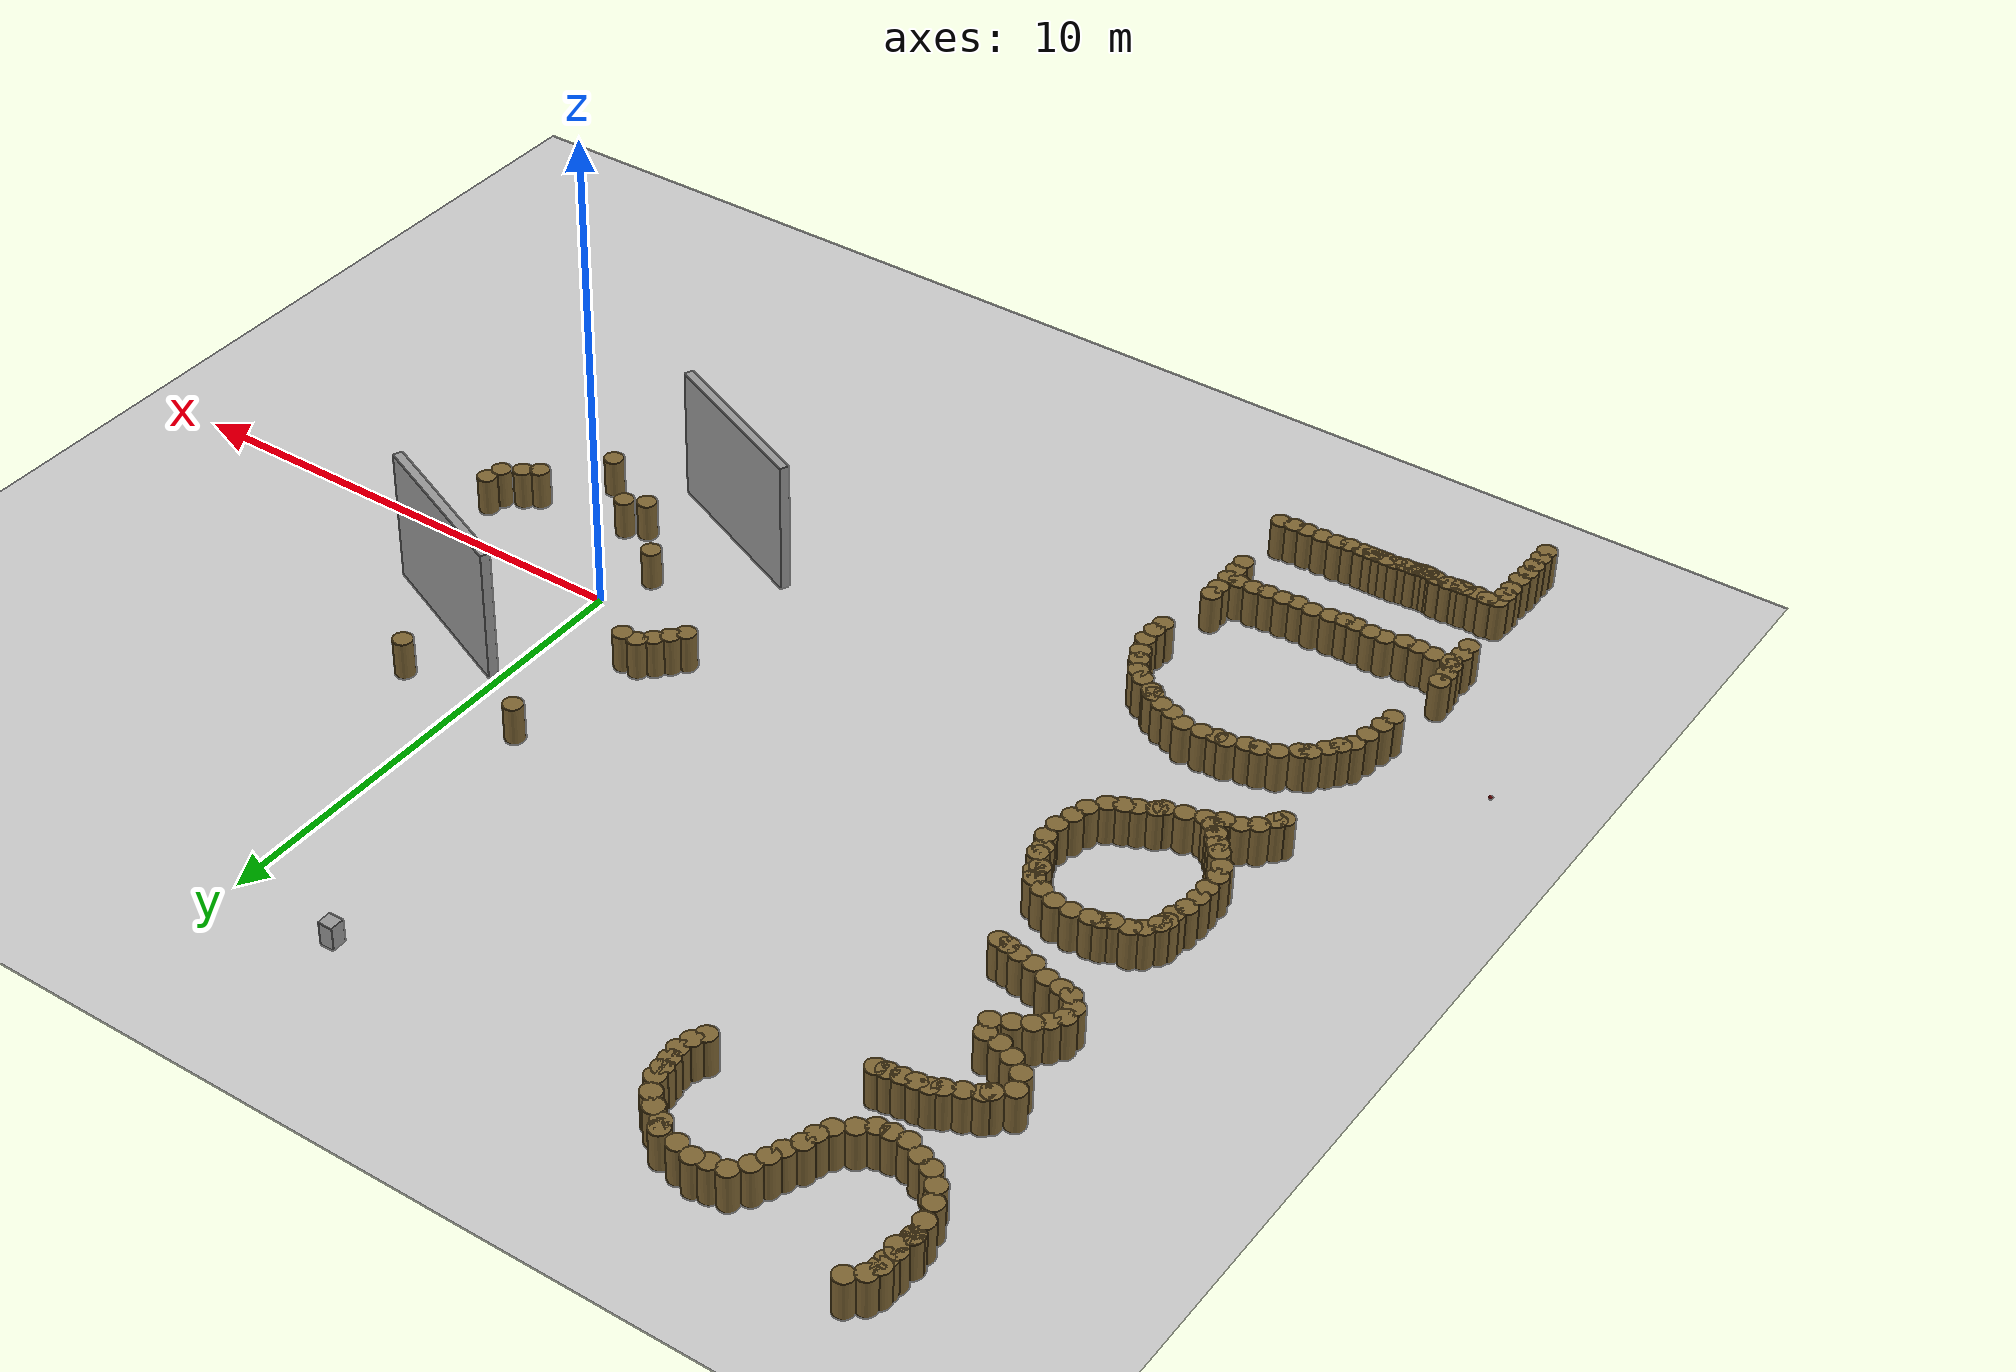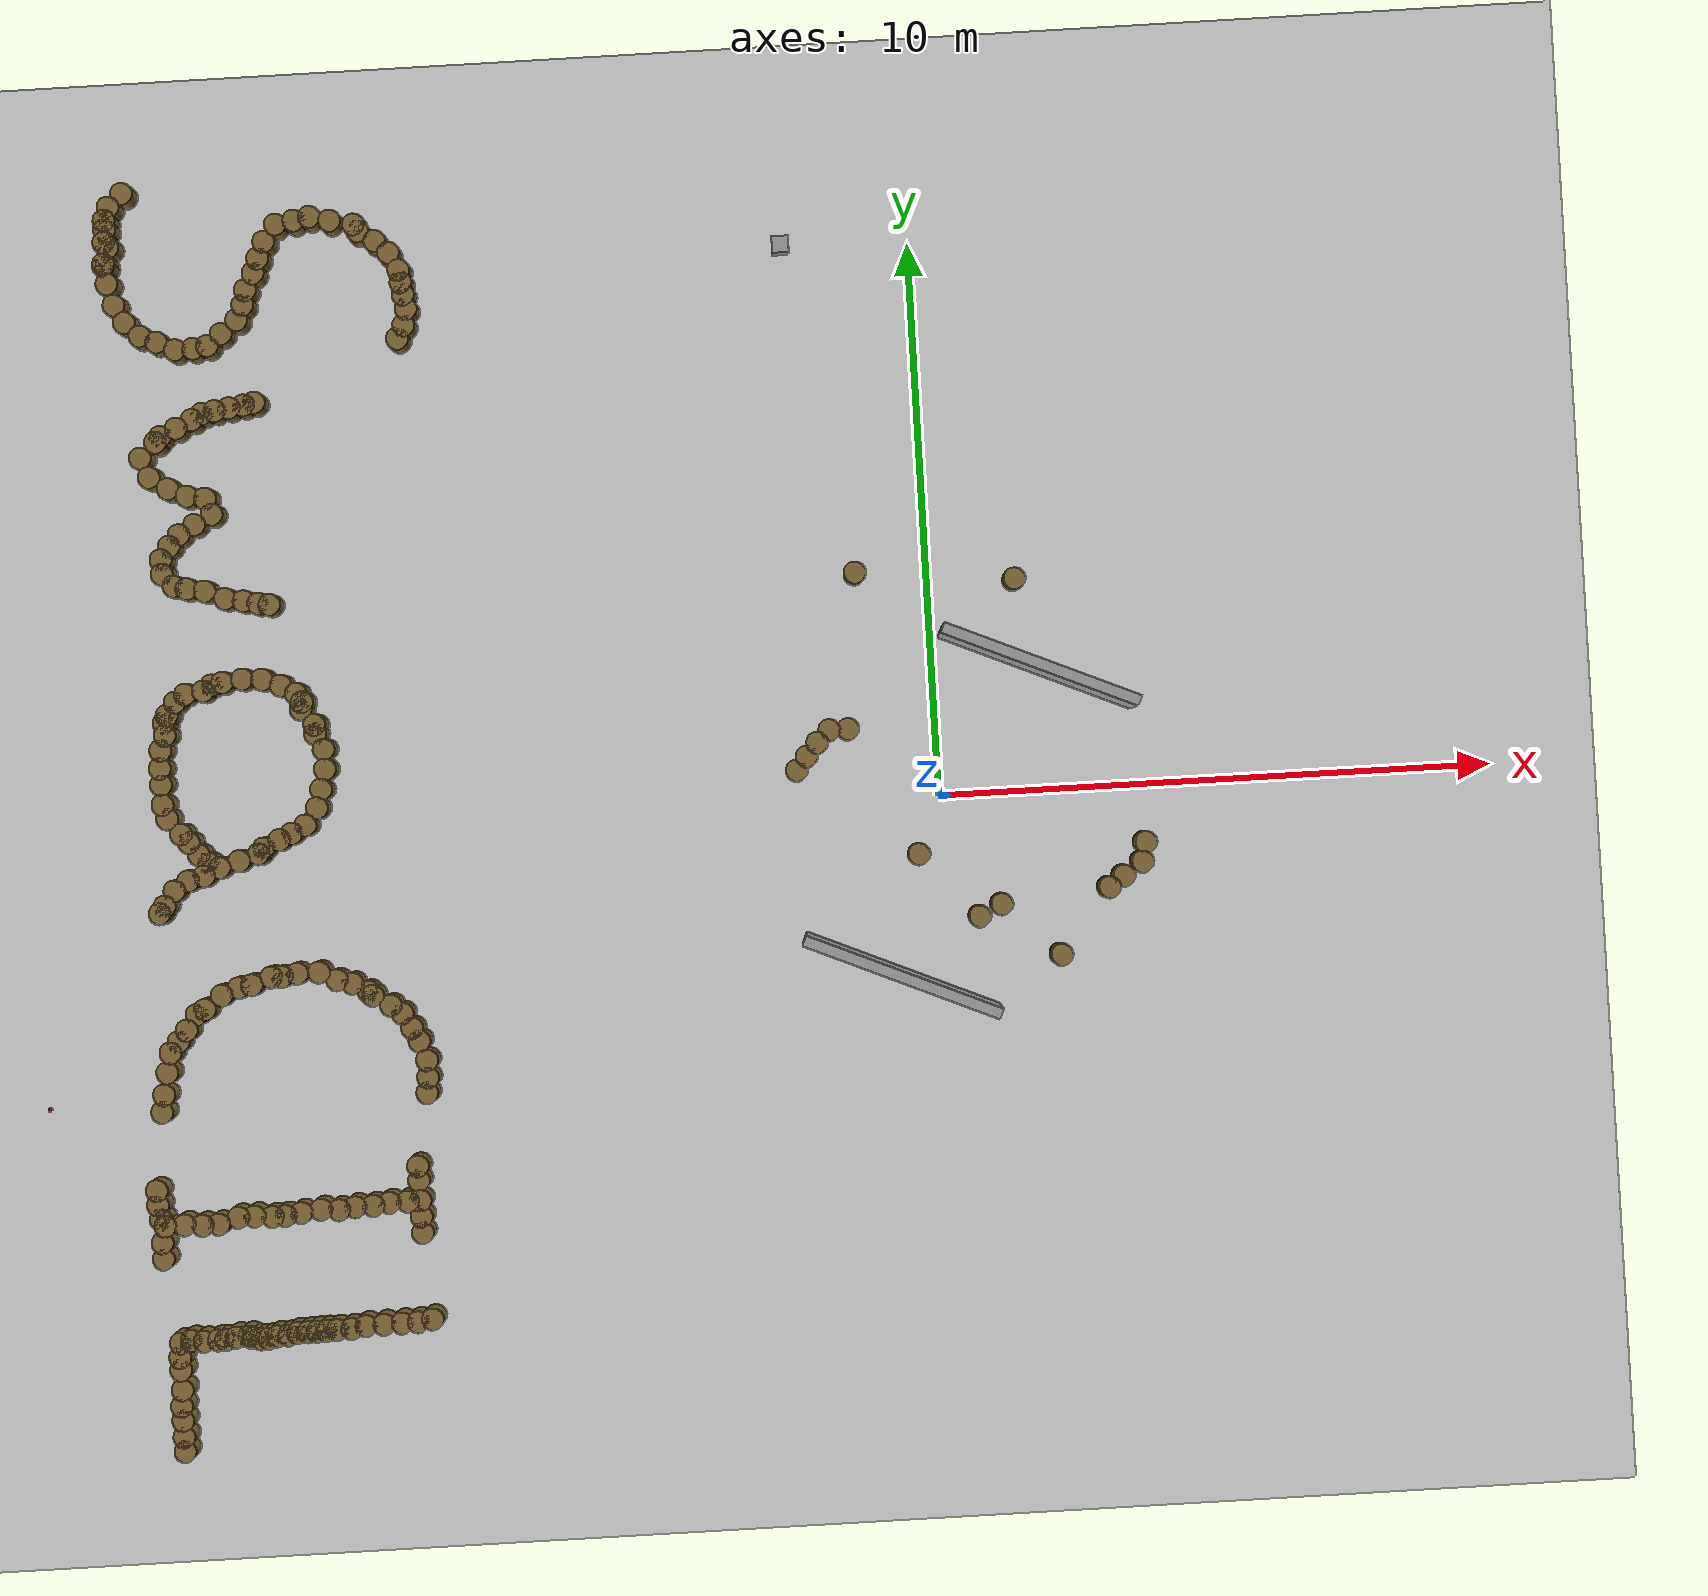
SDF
<sdf version="1.7">
 <world name="default">
  <scene><ambient>0.4 0.4 0.4 1</ambient><background>0.7 0.7 0.7 1</background><shadows>1</shadows></scene>
  <light name="sun" type="directional">
   <pose>0 0 10 0 -0 0</pose>
   <diffuse>0.8 0.8 0.8 1</diffuse>
   <specular>0.2 0.2 0.2 1</specular>
   <attenuation>
    <range>1000</range>
    <constant>0.9</constant>
    <linear>0.01</linear>
    <quadratic>0.001</quadratic>
   </attenuation>
   <direction>-0.5 0.1 -0.9</direction>
   <spot><inner_angle>0</inner_angle><outer_angle>0</outer_angle><falloff>0</falloff></spot>
  </light>
  <model name="ground_plane">
   <static>1</static>
   <link name="link">
    <collision name="collision">
     <geometry><plane><normal>0 0 1</normal><size>100 100</size></plane></geometry>
     <surface><friction><ode><mu>100</mu><mu2>50</mu2></ode></friction></surface>
    </collision>
    <visual name="visual">
     <cast_shadows>0</cast_shadows>
     <geometry><plane><normal>0 0 1</normal><size>100 100</size></plane></geometry>
     <material>
      <script><uri>file://media/materials/scripts/gazebo.material</uri><name>Gazebo/Grey</name></script>
     </material>
    </visual>
   </link>
  </model>
  <physics name="default_physics" default="0" type="ode">
   <real_time_update_rate>1000</real_time_update_rate>
   <max_step_size>0.02</max_step_size>
   <real_time_factor>0</real_time_factor>
   <ode>
    <solver>
     <type>quick</type>
     <iters>150</iters>
     <precon_iters>0</precon_iters>
     <sor>1.4</sor>
     <use_dynamic_moi_rescaling>1</use_dynamic_moi_rescaling>
    </solver>
    <constraints>
     <cfm>1e-05</cfm>
     <erp>0.2</erp>
     <contact_max_correcting_vel>2000</contact_max_correcting_vel>
     <contact_surface_layer>0.01</contact_surface_layer>
    </constraints>
   </ode>
  </physics>
  <gravity>0 0 -9.8</gravity>
  <magnetic_field>6e-06 2.3e-05 -4.2e-05</magnetic_field>
  <atmosphere type="adiabatic"/>
  <spherical_coordinates>
   <surface_model>EARTH_WGS84</surface_model>
   <latitude_deg>0</latitude_deg>
   <longitude_deg>0</longitude_deg>
   <elevation>0</elevation>
   <heading_deg>0</heading_deg>
  </spherical_coordinates>
  <audio><device>default</device></audio>
  <model name="target_5">
   <link name="link">
    <pose>0 0 0.0375 0 -0 0</pose>
    <inertial>
     <mass>0.1467</mass>
     <inertia>
      <ixx>8.25187e-05</ixx>
      <ixy>0</ixy>
      <ixz>0</ixz>
      <iyy>8.25187e-05</iyy>
      <iyz>0</iyz>
      <izz>8.25187e-05</izz>
     </inertia>
    </inertial>
    <velocity_decay><linear>0</linear><angular>0.005</angular></velocity_decay>
    <visual name="visual">
     <geometry><sphere><radius>0.0375</radius></sphere></geometry>
     <material>
      <script><uri>file://media/materials/scripts/gazebo.material</uri><name>Gazebo/Red</name></script>
      <shader type="pixel"/>
     </material>
    </visual>
    <collision name="collision">
     <geometry><sphere><radius>0.0375</radius></sphere></geometry>
     <surface>
      <friction>
       <ode><mu>1</mu><mu2>1</mu2><fdir1>0 0 0</fdir1><slip1>0</slip1><slip2>0</slip2></ode>
       <torsional>
        <coefficient>1</coefficient>
        <patch_radius>0</patch_radius>
        <surface_radius>0.01</surface_radius>
        <use_patch_radius>0</use_patch_radius>
        <ode><slip>0</slip></ode>
       </torsional>
      </friction>
      <bounce><restitution_coefficient>0</restitution_coefficient><threshold>1e+06</threshold></bounce>
      <contact>
       <collide_without_contact>0</collide_without_contact>
       <collide_without_contact_bitmask>1</collide_without_contact_bitmask>
       <collide_bitmask>1</collide_bitmask>
       <ode>
        <soft_cfm>0</soft_cfm>
        <soft_erp>0.2</soft_erp>
        <kp>100000</kp>
        <kd>100</kd>
        <max_vel>100</max_vel>
        <min_depth>0.001</min_depth>
       </ode>
       <bullet>
        <split_impulse>1</split_impulse>
        <split_impulse_penetration_threshold>-0.01</split_impulse_penetration_threshold>
        <soft_cfm>0</soft_cfm>
        <soft_erp>0.2</soft_erp>
        <kp>100000</kp>
        <kd>100</kd>
       </bullet>
      </contact>
     </surface>
    </collision>
   </link>
   <static>0</static>
   <pose>-16.3973 -4.73224 -0.001014 0 -0 0</pose>
  </model>
  <model name="mini_cylinder_0_clone_0_clone_clone_clone_clone_0">
   <link name="link">
    <inertial>
     <mass>1</mass>
     <inertia><ixx>0.145833</ixx><ixy>0</ixy><ixz>0</ixz><iyy>0.145833</iyy><iyz>0</iyz><izz>0.125</izz></inertia>
    </inertial>
    <visual name="visual">
     <geometry><cylinder><radius>0.2</radius><length>0.8</length></cylinder></geometry>
     <material>
      <script><name>Gazebo/Grey</name><uri>file://media/materials/scripts/gazebo.material</uri></script>
      <shader type="vertex"><normal_map>__default__</normal_map></shader>
      <ambient>0.5 0.4 0.2 1</ambient>
      <diffuse>0.7 0.7 0.7 1</diffuse>
      <specular>0.01 0.01 0.01 1</specular>
      <emissive>0 0 0 1</emissive>
     </material>
    </visual>
    <collision name="collision">
     <geometry><cylinder><radius>0.2</radius><length>0.8</length></cylinder></geometry>
     <surface>
      <friction>
       <ode><mu>1</mu><mu2>1</mu2><fdir1>0 0 0</fdir1><slip1>0</slip1><slip2>0</slip2></ode>
       <torsional>
        <coefficient>1</coefficient>
        <patch_radius>0</patch_radius>
        <surface_radius>0</surface_radius>
        <use_patch_radius>1</use_patch_radius>
        <ode><slip>0</slip></ode>
       </torsional>
      </friction>
      <bounce><restitution_coefficient>0</restitution_coefficient><threshold>1e+06</threshold></bounce>
      <contact>
       <collide_without_contact>0</collide_without_contact>
       <collide_without_contact_bitmask>1</collide_without_contact_bitmask>
       <collide_bitmask>1</collide_bitmask>
       <ode>
        <soft_cfm>0</soft_cfm>
        <soft_erp>0.2</soft_erp>
        <kp>1e+13</kp>
        <kd>1</kd>
        <max_vel>0.01</max_vel>
        <min_depth>0</min_depth>
       </ode>
       <bullet>
        <split_impulse>1</split_impulse>
        <split_impulse_penetration_threshold>-0.01</split_impulse_penetration_threshold>
        <soft_cfm>0</soft_cfm>
        <soft_erp>0.2</soft_erp>
        <kp>1e+13</kp>
        <kd>1</kd>
       </bullet>
      </contact>
     </surface>
    </collision>
   </link>
   <static>1</static>
   <pose>-2.15189 1.08832 0.4 0 -0 0</pose>
  </model>
  <model name="mini_cylinder_0_clone_0_clone_clone_clone_clone_4">
   <link name="link">
    <inertial>
     <mass>1</mass>
     <inertia><ixx>0.145833</ixx><ixy>0</ixy><ixz>0</ixz><iyy>0.145833</iyy><iyz>0</iyz><izz>0.125</izz></inertia>
    </inertial>
    <visual name="visual">
     <geometry><cylinder><radius>0.2</radius><length>0.8</length></cylinder></geometry>
     <material>
      <script><name>Gazebo/Grey</name><uri>file://media/materials/scripts/gazebo.material</uri></script>
      <shader type="vertex"><normal_map>__default__</normal_map></shader>
      <ambient>0.5 0.4 0.2 1</ambient>
      <diffuse>0.7 0.7 0.7 1</diffuse>
      <specular>0.01 0.01 0.01 1</specular>
      <emissive>0 0 0 1</emissive>
     </material>
    </visual>
    <collision name="collision">
     <geometry><cylinder><radius>0.2</radius><length>0.8</length></cylinder></geometry>
     <surface>
      <friction>
       <ode><mu>1</mu><mu2>1</mu2><fdir1>0 0 0</fdir1><slip1>0</slip1><slip2>0</slip2></ode>
       <torsional>
        <coefficient>1</coefficient>
        <patch_radius>0</patch_radius>
        <surface_radius>0</surface_radius>
        <use_patch_radius>1</use_patch_radius>
        <ode><slip>0</slip></ode>
       </torsional>
      </friction>
      <bounce><restitution_coefficient>0</restitution_coefficient><threshold>1e+06</threshold></bounce>
      <contact>
       <collide_without_contact>0</collide_without_contact>
       <collide_without_contact_bitmask>1</collide_without_contact_bitmask>
       <collide_bitmask>1</collide_bitmask>
       <ode>
        <soft_cfm>0</soft_cfm>
        <soft_erp>0.2</soft_erp>
        <kp>1e+13</kp>
        <kd>1</kd>
        <max_vel>0.01</max_vel>
        <min_depth>0</min_depth>
       </ode>
       <bullet>
        <split_impulse>1</split_impulse>
        <split_impulse_penetration_threshold>-0.01</split_impulse_penetration_threshold>
        <soft_cfm>0</soft_cfm>
        <soft_erp>0.2</soft_erp>
        <kp>1e+13</kp>
        <kd>1</kd>
       </bullet>
      </contact>
     </surface>
    </collision>
   </link>
   <static>1</static>
   <pose>-1.92181 1.30291 0.4 0 -0 0</pose>
  </model>
  <model name="mini_cylinder_0_clone_0_clone_clone_clone_clone_5">
   <link name="link">
    <inertial>
     <mass>1</mass>
     <inertia><ixx>0.145833</ixx><ixy>0</ixy><ixz>0</ixz><iyy>0.145833</iyy><iyz>0</iyz><izz>0.125</izz></inertia>
    </inertial>
    <visual name="visual">
     <geometry><cylinder><radius>0.2</radius><length>0.8</length></cylinder></geometry>
     <material>
      <script><name>Gazebo/Grey</name><uri>file://media/materials/scripts/gazebo.material</uri></script>
      <shader type="vertex"><normal_map>__default__</normal_map></shader>
      <ambient>0.5 0.4 0.2 1</ambient>
      <diffuse>0.7 0.7 0.7 1</diffuse>
      <specular>0.01 0.01 0.01 1</specular>
      <emissive>0 0 0 1</emissive>
     </material>
    </visual>
    <collision name="collision">
     <geometry><cylinder><radius>0.2</radius><length>0.8</length></cylinder></geometry>
     <surface>
      <friction>
       <ode><mu>1</mu><mu2>1</mu2><fdir1>0 0 0</fdir1><slip1>0</slip1><slip2>0</slip2></ode>
       <torsional>
        <coefficient>1</coefficient>
        <patch_radius>0</patch_radius>
        <surface_radius>0</surface_radius>
        <use_patch_radius>1</use_patch_radius>
        <ode><slip>0</slip></ode>
       </torsional>
      </friction>
      <bounce><restitution_coefficient>0</restitution_coefficient><threshold>1e+06</threshold></bounce>
      <contact>
       <collide_without_contact>0</collide_without_contact>
       <collide_without_contact_bitmask>1</collide_without_contact_bitmask>
       <collide_bitmask>1</collide_bitmask>
       <ode>
        <soft_cfm>0</soft_cfm>
        <soft_erp>0.2</soft_erp>
        <kp>1e+13</kp>
        <kd>1</kd>
        <max_vel>0.01</max_vel>
        <min_depth>0</min_depth>
       </ode>
       <bullet>
        <split_impulse>1</split_impulse>
        <split_impulse_penetration_threshold>-0.01</split_impulse_penetration_threshold>
        <soft_cfm>0</soft_cfm>
        <soft_erp>0.2</soft_erp>
        <kp>1e+13</kp>
        <kd>1</kd>
       </bullet>
      </contact>
     </surface>
    </collision>
   </link>
   <static>1</static>
   <pose>0.594741 -2.19524 0.4 0 -0 0</pose>
  </model>
  <model name="mini_cylinder_0_clone_0_clone_clone_clone_clone_6">
   <link name="link">
    <inertial>
     <mass>1</mass>
     <inertia><ixx>0.145833</ixx><ixy>0</ixy><ixz>0</ixz><iyy>0.145833</iyy><iyz>0</iyz><izz>0.125</izz></inertia>
    </inertial>
    <visual name="visual">
     <geometry><cylinder><radius>0.2</radius><length>0.8</length></cylinder></geometry>
     <material>
      <script><name>Gazebo/Grey</name><uri>file://media/materials/scripts/gazebo.material</uri></script>
      <shader type="vertex"><normal_map>__default__</normal_map></shader>
      <ambient>0.5 0.4 0.2 1</ambient>
      <diffuse>0.7 0.7 0.7 1</diffuse>
      <specular>0.01 0.01 0.01 1</specular>
      <emissive>0 0 0 1</emissive>
     </material>
    </visual>
    <collision name="collision">
     <geometry><cylinder><radius>0.2</radius><length>0.8</length></cylinder></geometry>
     <surface>
      <friction>
       <ode><mu>1</mu><mu2>1</mu2><fdir1>0 0 0</fdir1><slip1>0</slip1><slip2>0</slip2></ode>
       <torsional>
        <coefficient>1</coefficient>
        <patch_radius>0</patch_radius>
        <surface_radius>0</surface_radius>
        <use_patch_radius>1</use_patch_radius>
        <ode><slip>0</slip></ode>
       </torsional>
      </friction>
      <bounce><restitution_coefficient>0</restitution_coefficient><threshold>1e+06</threshold></bounce>
      <contact>
       <collide_without_contact>0</collide_without_contact>
       <collide_without_contact_bitmask>1</collide_without_contact_bitmask>
       <collide_bitmask>1</collide_bitmask>
       <ode>
        <soft_cfm>0</soft_cfm>
        <soft_erp>0.2</soft_erp>
        <kp>1e+13</kp>
        <kd>1</kd>
        <max_vel>0.01</max_vel>
        <min_depth>0</min_depth>
       </ode>
       <bullet>
        <split_impulse>1</split_impulse>
        <split_impulse_penetration_threshold>-0.01</split_impulse_penetration_threshold>
        <soft_cfm>0</soft_cfm>
        <soft_erp>0.2</soft_erp>
        <kp>1e+13</kp>
        <kd>1</kd>
       </bullet>
      </contact>
     </surface>
    </collision>
   </link>
   <static>1</static>
   <pose>1 -2 0.4 0 -0 0</pose>
  </model>
  <model name="mini_cylinder_0_clone_0_clone_clone_clone_clone_7">
   <link name="link">
    <inertial>
     <mass>1</mass>
     <inertia><ixx>0.145833</ixx><ixy>0</ixy><ixz>0</ixz><iyy>0.145833</iyy><iyz>0</iyz><izz>0.125</izz></inertia>
    </inertial>
    <visual name="visual">
     <geometry><cylinder><radius>0.2</radius><length>0.8</length></cylinder></geometry>
     <material>
      <script><name>Gazebo/Grey</name><uri>file://media/materials/scripts/gazebo.material</uri></script>
      <shader type="vertex"><normal_map>__default__</normal_map></shader>
      <ambient>0.5 0.4 0.2 1</ambient>
      <diffuse>0.7 0.7 0.7 1</diffuse>
      <specular>0.01 0.01 0.01 1</specular>
      <emissive>0 0 0 1</emissive>
     </material>
    </visual>
    <collision name="collision">
     <geometry><cylinder><radius>0.2</radius><length>0.8</length></cylinder></geometry>
     <surface>
      <friction>
       <ode><mu>1</mu><mu2>1</mu2><fdir1>0 0 0</fdir1><slip1>0</slip1><slip2>0</slip2></ode>
       <torsional>
        <coefficient>1</coefficient>
        <patch_radius>0</patch_radius>
        <surface_radius>0</surface_radius>
        <use_patch_radius>1</use_patch_radius>
        <ode><slip>0</slip></ode>
       </torsional>
      </friction>
      <bounce><restitution_coefficient>0</restitution_coefficient><threshold>1e+06</threshold></bounce>
      <contact>
       <collide_without_contact>0</collide_without_contact>
       <collide_without_contact_bitmask>1</collide_without_contact_bitmask>
       <collide_bitmask>1</collide_bitmask>
       <ode>
        <soft_cfm>0</soft_cfm>
        <soft_erp>0.2</soft_erp>
        <kp>1e+13</kp>
        <kd>1</kd>
        <max_vel>0.01</max_vel>
        <min_depth>0</min_depth>
       </ode>
       <bullet>
        <split_impulse>1</split_impulse>
        <split_impulse_penetration_threshold>-0.01</split_impulse_penetration_threshold>
        <soft_cfm>0</soft_cfm>
        <soft_erp>0.2</soft_erp>
        <kp>1e+13</kp>
        <kd>1</kd>
       </bullet>
      </contact>
     </surface>
    </collision>
   </link>
   <static>1</static>
   <pose>2.95172 -1.80895 0.4 0 -0 0</pose>
  </model>
  <model name="mini_cylinder_0_clone_0_clone_clone_clone_clone_8">
   <link name="link">
    <inertial>
     <mass>1</mass>
     <inertia><ixx>0.145833</ixx><ixy>0</ixy><ixz>0</ixz><iyy>0.145833</iyy><iyz>0</iyz><izz>0.125</izz></inertia>
    </inertial>
    <visual name="visual">
     <geometry><cylinder><radius>0.2</radius><length>0.8</length></cylinder></geometry>
     <material>
      <script><name>Gazebo/Grey</name><uri>file://media/materials/scripts/gazebo.material</uri></script>
      <shader type="vertex"><normal_map>__default__</normal_map></shader>
      <ambient>0.5 0.4 0.2 1</ambient>
      <diffuse>0.7 0.7 0.7 1</diffuse>
      <specular>0.01 0.01 0.01 1</specular>
      <emissive>0 0 0 1</emissive>
     </material>
    </visual>
    <collision name="collision">
     <geometry><cylinder><radius>0.2</radius><length>0.8</length></cylinder></geometry>
     <surface>
      <friction>
       <ode><mu>1</mu><mu2>1</mu2><fdir1>0 0 0</fdir1><slip1>0</slip1><slip2>0</slip2></ode>
       <torsional>
        <coefficient>1</coefficient>
        <patch_radius>0</patch_radius>
        <surface_radius>0</surface_radius>
        <use_patch_radius>1</use_patch_radius>
        <ode><slip>0</slip></ode>
       </torsional>
      </friction>
      <bounce><restitution_coefficient>0</restitution_coefficient><threshold>1e+06</threshold></bounce>
      <contact>
       <collide_without_contact>0</collide_without_contact>
       <collide_without_contact_bitmask>1</collide_without_contact_bitmask>
       <collide_bitmask>1</collide_bitmask>
       <ode>
        <soft_cfm>0</soft_cfm>
        <soft_erp>0.2</soft_erp>
        <kp>1e+13</kp>
        <kd>1</kd>
        <max_vel>0.01</max_vel>
        <min_depth>0</min_depth>
       </ode>
       <bullet>
        <split_impulse>1</split_impulse>
        <split_impulse_penetration_threshold>-0.01</split_impulse_penetration_threshold>
        <soft_cfm>0</soft_cfm>
        <soft_erp>0.2</soft_erp>
        <kp>1e+13</kp>
        <kd>1</kd>
       </bullet>
      </contact>
     </surface>
    </collision>
   </link>
   <static>1</static>
   <pose>3.22202 -1.6158 0.4 0 -0 0</pose>
  </model>
  <model name="mini_cylinder_0_clone_0_clone_clone_clone_clone_9">
   <link name="link">
    <inertial>
     <mass>1</mass>
     <inertia><ixx>0.145833</ixx><ixy>0</ixy><ixz>0</ixz><iyy>0.145833</iyy><iyz>0</iyz><izz>0.125</izz></inertia>
    </inertial>
    <visual name="visual">
     <geometry><cylinder><radius>0.2</radius><length>0.8</length></cylinder></geometry>
     <material>
      <script><name>Gazebo/Grey</name><uri>file://media/materials/scripts/gazebo.material</uri></script>
      <shader type="vertex"><normal_map>__default__</normal_map></shader>
      <ambient>0.5 0.4 0.2 1</ambient>
      <diffuse>0.7 0.7 0.7 1</diffuse>
      <specular>0.01 0.01 0.01 1</specular>
      <emissive>0 0 0 1</emissive>
     </material>
    </visual>
    <collision name="collision">
     <geometry><cylinder><radius>0.2</radius><length>0.8</length></cylinder></geometry>
     <surface>
      <friction>
       <ode><mu>1</mu><mu2>1</mu2><fdir1>0 0 0</fdir1><slip1>0</slip1><slip2>0</slip2></ode>
       <torsional>
        <coefficient>1</coefficient>
        <patch_radius>0</patch_radius>
        <surface_radius>0</surface_radius>
        <use_patch_radius>1</use_patch_radius>
        <ode><slip>0</slip></ode>
       </torsional>
      </friction>
      <bounce><restitution_coefficient>0</restitution_coefficient><threshold>1e+06</threshold></bounce>
      <contact>
       <collide_without_contact>0</collide_without_contact>
       <collide_without_contact_bitmask>1</collide_without_contact_bitmask>
       <collide_bitmask>1</collide_bitmask>
       <ode>
        <soft_cfm>0</soft_cfm>
        <soft_erp>0.2</soft_erp>
        <kp>1e+13</kp>
        <kd>1</kd>
        <max_vel>0.01</max_vel>
        <min_depth>0</min_depth>
       </ode>
       <bullet>
        <split_impulse>1</split_impulse>
        <split_impulse_penetration_threshold>-0.01</split_impulse_penetration_threshold>
        <soft_cfm>0</soft_cfm>
        <soft_erp>0.2</soft_erp>
        <kp>1e+13</kp>
        <kd>1</kd>
       </bullet>
      </contact>
     </surface>
    </collision>
   </link>
   <static>1</static>
   <pose>3.56983 -1.38381 0.4 0 -0 0</pose>
  </model>
  <model name="mini_cylinder_0_clone_0_clone_clone_clone_clone_10">
   <link name="link">
    <inertial>
     <mass>1</mass>
     <inertia><ixx>0.145833</ixx><ixy>0</ixy><ixz>0</ixz><iyy>0.145833</iyy><iyz>0</iyz><izz>0.125</izz></inertia>
    </inertial>
    <visual name="visual">
     <geometry><cylinder><radius>0.2</radius><length>0.8</length></cylinder></geometry>
     <material>
      <script><name>Gazebo/Grey</name><uri>file://media/materials/scripts/gazebo.material</uri></script>
      <shader type="vertex"><normal_map>__default__</normal_map></shader>
      <ambient>0.5 0.4 0.2 1</ambient>
      <diffuse>0.7 0.7 0.7 1</diffuse>
      <specular>0.01 0.01 0.01 1</specular>
      <emissive>0 0 0 1</emissive>
     </material>
    </visual>
    <collision name="collision">
     <geometry><cylinder><radius>0.2</radius><length>0.8</length></cylinder></geometry>
     <surface>
      <friction>
       <ode><mu>1</mu><mu2>1</mu2><fdir1>0 0 0</fdir1><slip1>0</slip1><slip2>0</slip2></ode>
       <torsional>
        <coefficient>1</coefficient>
        <patch_radius>0</patch_radius>
        <surface_radius>0</surface_radius>
        <use_patch_radius>1</use_patch_radius>
        <ode><slip>0</slip></ode>
       </torsional>
      </friction>
      <bounce><restitution_coefficient>0</restitution_coefficient><threshold>1e+06</threshold></bounce>
      <contact>
       <collide_without_contact>0</collide_without_contact>
       <collide_without_contact_bitmask>1</collide_without_contact_bitmask>
       <collide_bitmask>1</collide_bitmask>
       <ode>
        <soft_cfm>0</soft_cfm>
        <soft_erp>0.2</soft_erp>
        <kp>1e+13</kp>
        <kd>1</kd>
        <max_vel>0.01</max_vel>
        <min_depth>0</min_depth>
       </ode>
       <bullet>
        <split_impulse>1</split_impulse>
        <split_impulse_penetration_threshold>-0.01</split_impulse_penetration_threshold>
        <soft_cfm>0</soft_cfm>
        <soft_erp>0.2</soft_erp>
        <kp>1e+13</kp>
        <kd>1</kd>
       </bullet>
      </contact>
     </surface>
    </collision>
   </link>
   <static>1</static>
   <pose>3.64698 -1.03635 0.4 0 -0 0</pose>
  </model>
  <model name="mini_cylinder_0_clone_0_clone_clone_clone_clone_11">
   <link name="link">
    <inertial>
     <mass>1</mass>
     <inertia><ixx>0.145833</ixx><ixy>0</ixy><ixz>0</ixz><iyy>0.145833</iyy><iyz>0</iyz><izz>0.125</izz></inertia>
    </inertial>
    <visual name="visual">
     <geometry><cylinder><radius>0.2</radius><length>0.8</length></cylinder></geometry>
     <material>
      <script><name>Gazebo/Grey</name><uri>file://media/materials/scripts/gazebo.material</uri></script>
      <shader type="vertex"><normal_map>__default__</normal_map></shader>
      <ambient>0.5 0.4 0.2 1</ambient>
      <diffuse>0.7 0.7 0.7 1</diffuse>
      <specular>0.01 0.01 0.01 1</specular>
      <emissive>0 0 0 1</emissive>
     </material>
    </visual>
    <collision name="collision">
     <geometry><cylinder><radius>0.2</radius><length>0.8</length></cylinder></geometry>
     <surface>
      <friction>
       <ode><mu>1</mu><mu2>1</mu2><fdir1>0 0 0</fdir1><slip1>0</slip1><slip2>0</slip2></ode>
       <torsional>
        <coefficient>1</coefficient>
        <patch_radius>0</patch_radius>
        <surface_radius>0</surface_radius>
        <use_patch_radius>1</use_patch_radius>
        <ode><slip>0</slip></ode>
       </torsional>
      </friction>
      <bounce><restitution_coefficient>0</restitution_coefficient><threshold>1e+06</threshold></bounce>
      <contact>
       <collide_without_contact>0</collide_without_contact>
       <collide_without_contact_bitmask>1</collide_without_contact_bitmask>
       <collide_bitmask>1</collide_bitmask>
       <ode>
        <soft_cfm>0</soft_cfm>
        <soft_erp>0.2</soft_erp>
        <kp>1e+13</kp>
        <kd>1</kd>
        <max_vel>0.01</max_vel>
        <min_depth>0</min_depth>
       </ode>
       <bullet>
        <split_impulse>1</split_impulse>
        <split_impulse_penetration_threshold>-0.01</split_impulse_penetration_threshold>
        <soft_cfm>0</soft_cfm>
        <soft_erp>0.2</soft_erp>
        <kp>1e+13</kp>
        <kd>1</kd>
       </bullet>
      </contact>
     </surface>
    </collision>
   </link>
   <static>1</static>
   <pose>2.02446 -2.96819 0.4 0 -0 0</pose>
  </model>
  <model name="mini_cylinder_0_clone_0_clone_clone_clone_clone_12">
   <link name="link">
    <inertial>
     <mass>1</mass>
     <inertia><ixx>0.145833</ixx><ixy>0</ixy><ixz>0</ixz><iyy>0.145833</iyy><iyz>0</iyz><izz>0.125</izz></inertia>
    </inertial>
    <visual name="visual">
     <geometry><cylinder><radius>0.2</radius><length>0.8</length></cylinder></geometry>
     <material>
      <script><name>Gazebo/Grey</name><uri>file://media/materials/scripts/gazebo.material</uri></script>
      <shader type="vertex"><normal_map>__default__</normal_map></shader>
      <ambient>0.5 0.4 0.2 1</ambient>
      <diffuse>0.7 0.7 0.7 1</diffuse>
      <specular>0.01 0.01 0.01 1</specular>
      <emissive>0 0 0 1</emissive>
     </material>
    </visual>
    <collision name="collision">
     <geometry><cylinder><radius>0.2</radius><length>0.8</length></cylinder></geometry>
     <surface>
      <friction>
       <ode><mu>1</mu><mu2>1</mu2><fdir1>0 0 0</fdir1><slip1>0</slip1><slip2>0</slip2></ode>
       <torsional>
        <coefficient>1</coefficient>
        <patch_radius>0</patch_radius>
        <surface_radius>0</surface_radius>
        <use_patch_radius>1</use_patch_radius>
        <ode><slip>0</slip></ode>
       </torsional>
      </friction>
      <bounce><restitution_coefficient>0</restitution_coefficient><threshold>1e+06</threshold></bounce>
      <contact>
       <collide_without_contact>0</collide_without_contact>
       <collide_without_contact_bitmask>1</collide_without_contact_bitmask>
       <collide_bitmask>1</collide_bitmask>
       <ode>
        <soft_cfm>0</soft_cfm>
        <soft_erp>0.2</soft_erp>
        <kp>1e+13</kp>
        <kd>1</kd>
        <max_vel>0.01</max_vel>
        <min_depth>0</min_depth>
       </ode>
       <bullet>
        <split_impulse>1</split_impulse>
        <split_impulse_penetration_threshold>-0.01</split_impulse_penetration_threshold>
        <soft_cfm>0</soft_cfm>
        <soft_erp>0.2</soft_erp>
        <kp>1e+13</kp>
        <kd>1</kd>
       </bullet>
      </contact>
     </surface>
    </collision>
   </link>
   <static>1</static>
   <pose>1.56031 3.83174 0.4 0 -0 0</pose>
  </model>
  <model name="mini_cylinder_0_clone_0_clone_clone_clone_clone_13">
   <link name="link">
    <inertial>
     <mass>1</mass>
     <inertia><ixx>0.145833</ixx><ixy>0</ixy><ixz>0</ixz><iyy>0.145833</iyy><iyz>0</iyz><izz>0.125</izz></inertia>
    </inertial>
    <visual name="visual">
     <geometry><cylinder><radius>0.2</radius><length>0.8</length></cylinder></geometry>
     <material>
      <script><name>Gazebo/Grey</name><uri>file://media/materials/scripts/gazebo.material</uri></script>
      <shader type="vertex"><normal_map>__default__</normal_map></shader>
      <ambient>0.5 0.4 0.2 1</ambient>
      <diffuse>0.7 0.7 0.7 1</diffuse>
      <specular>0.01 0.01 0.01 1</specular>
      <emissive>0 0 0 1</emissive>
     </material>
    </visual>
    <collision name="collision">
     <geometry><cylinder><radius>0.2</radius><length>0.8</length></cylinder></geometry>
     <surface>
      <friction>
       <ode><mu>1</mu><mu2>1</mu2><fdir1>0 0 0</fdir1><slip1>0</slip1><slip2>0</slip2></ode>
       <torsional>
        <coefficient>1</coefficient>
        <patch_radius>0</patch_radius>
        <surface_radius>0</surface_radius>
        <use_patch_radius>1</use_patch_radius>
        <ode><slip>0</slip></ode>
       </torsional>
      </friction>
      <bounce><restitution_coefficient>0</restitution_coefficient><threshold>1e+06</threshold></bounce>
      <contact>
       <collide_without_contact>0</collide_without_contact>
       <collide_without_contact_bitmask>1</collide_without_contact_bitmask>
       <collide_bitmask>1</collide_bitmask>
       <ode>
        <soft_cfm>0</soft_cfm>
        <soft_erp>0.2</soft_erp>
        <kp>1e+13</kp>
        <kd>1</kd>
        <max_vel>0.01</max_vel>
        <min_depth>0</min_depth>
       </ode>
       <bullet>
        <split_impulse>1</split_impulse>
        <split_impulse_penetration_threshold>-0.01</split_impulse_penetration_threshold>
        <soft_cfm>0</soft_cfm>
        <soft_erp>0.2</soft_erp>
        <kp>1e+13</kp>
        <kd>1</kd>
       </bullet>
      </contact>
     </surface>
    </collision>
   </link>
   <static>1</static>
   <pose>-1.29879 4.10222 0.4 0 -0 0</pose>
  </model>
  <model name="mini_cylinder_0_clone_0_clone_clone_clone_clone_3_clone">
   <link name="link">
    <inertial>
     <mass>1</mass>
     <inertia><ixx>0.145833</ixx><ixy>0</ixy><ixz>0</ixz><iyy>0.145833</iyy><iyz>0</iyz><izz>0.125</izz></inertia>
    </inertial>
    <visual name="visual">
     <geometry><cylinder><radius>0.2</radius><length>0.8</length></cylinder></geometry>
     <material>
      <script><name>Gazebo/Grey</name><uri>file://media/materials/scripts/gazebo.material</uri></script>
      <shader type="vertex"><normal_map>__default__</normal_map></shader>
      <ambient>0.5 0.4 0.2 1</ambient>
      <diffuse>0.7 0.7 0.7 1</diffuse>
      <specular>0.01 0.01 0.01 1</specular>
      <emissive>0 0 0 1</emissive>
     </material>
    </visual>
    <collision name="collision">
     <geometry><cylinder><radius>0.2</radius><length>0.8</length></cylinder></geometry>
     <surface>
      <friction>
       <ode><mu>1</mu><mu2>1</mu2><fdir1>0 0 0</fdir1><slip1>0</slip1><slip2>0</slip2></ode>
       <torsional>
        <coefficient>1</coefficient>
        <patch_radius>0</patch_radius>
        <surface_radius>0</surface_radius>
        <use_patch_radius>1</use_patch_radius>
        <ode><slip>0</slip></ode>
       </torsional>
      </friction>
      <bounce><restitution_coefficient>0</restitution_coefficient><threshold>1e+06</threshold></bounce>
      <contact>
       <collide_without_contact>0</collide_without_contact>
       <collide_without_contact_bitmask>1</collide_without_contact_bitmask>
       <collide_bitmask>1</collide_bitmask>
       <ode>
        <soft_cfm>0</soft_cfm>
        <soft_erp>0.2</soft_erp>
        <kp>1e+13</kp>
        <kd>1</kd>
        <max_vel>0.01</max_vel>
        <min_depth>0</min_depth>
       </ode>
       <bullet>
        <split_impulse>1</split_impulse>
        <split_impulse_penetration_threshold>-0.01</split_impulse_penetration_threshold>
        <soft_cfm>0</soft_cfm>
        <soft_erp>0.2</soft_erp>
        <kp>1e+13</kp>
        <kd>1</kd>
       </bullet>
      </contact>
     </surface>
    </collision>
   </link>
   <static>1</static>
   <pose>-14.0743 -3.80563 0.4 0 -0 0</pose>
  </model>
  <model name="mini_cylinder_0_clone_0_clone_clone_clone_clone_3_clone_0">
   <link name="link">
    <inertial>
     <mass>1</mass>
     <inertia><ixx>0.145833</ixx><ixy>0</ixy><ixz>0</ixz><iyy>0.145833</iyy><iyz>0</iyz><izz>0.125</izz></inertia>
    </inertial>
    <visual name="visual">
     <geometry><cylinder><radius>0.2</radius><length>0.8</length></cylinder></geometry>
     <material>
      <script><name>Gazebo/Grey</name><uri>file://media/materials/scripts/gazebo.material</uri></script>
      <shader type="vertex"><normal_map>__default__</normal_map></shader>
      <ambient>0.5 0.4 0.2 1</ambient>
      <diffuse>0.7 0.7 0.7 1</diffuse>
      <specular>0.01 0.01 0.01 1</specular>
      <emissive>0 0 0 1</emissive>
     </material>
    </visual>
    <collision name="collision">
     <geometry><cylinder><radius>0.2</radius><length>0.8</length></cylinder></geometry>
     <surface>
      <friction>
       <ode><mu>1</mu><mu2>1</mu2><fdir1>0 0 0</fdir1><slip1>0</slip1><slip2>0</slip2></ode>
       <torsional>
        <coefficient>1</coefficient>
        <patch_radius>0</patch_radius>
        <surface_radius>0</surface_radius>
        <use_patch_radius>1</use_patch_radius>
        <ode><slip>0</slip></ode>
       </torsional>
      </friction>
      <bounce><restitution_coefficient>0</restitution_coefficient><threshold>1e+06</threshold></bounce>
      <contact>
       <collide_without_contact>0</collide_without_contact>
       <collide_without_contact_bitmask>1</collide_without_contact_bitmask>
       <collide_bitmask>1</collide_bitmask>
       <ode>
        <soft_cfm>0</soft_cfm>
        <soft_erp>0.2</soft_erp>
        <kp>1e+13</kp>
        <kd>1</kd>
        <max_vel>0.01</max_vel>
        <min_depth>0</min_depth>
       </ode>
       <bullet>
        <split_impulse>1</split_impulse>
        <split_impulse_penetration_threshold>-0.01</split_impulse_penetration_threshold>
        <soft_cfm>0</soft_cfm>
        <soft_erp>0.2</soft_erp>
        <kp>1e+13</kp>
        <kd>1</kd>
       </bullet>
      </contact>
     </surface>
    </collision>
   </link>
   <static>1</static>
   <pose>-13.7598 -3.41261 0.4 0 -0 0</pose>
  </model>
  <model name="mini_cylinder_0_clone_0_clone_clone_clone_clone_3_clone_1">
   <link name="link">
    <inertial>
     <mass>1</mass>
     <inertia><ixx>0.145833</ixx><ixy>0</ixy><ixz>0</ixz><iyy>0.145833</iyy><iyz>0</iyz><izz>0.125</izz></inertia>
    </inertial>
    <visual name="visual">
     <geometry><cylinder><radius>0.2</radius><length>0.8</length></cylinder></geometry>
     <material>
      <script><name>Gazebo/Grey</name><uri>file://media/materials/scripts/gazebo.material</uri></script>
      <shader type="vertex"><normal_map>__default__</normal_map></shader>
      <ambient>0.5 0.4 0.2 1</ambient>
      <diffuse>0.7 0.7 0.7 1</diffuse>
      <specular>0.01 0.01 0.01 1</specular>
      <emissive>0 0 0 1</emissive>
     </material>
    </visual>
    <collision name="collision">
     <geometry><cylinder><radius>0.2</radius><length>0.8</length></cylinder></geometry>
     <surface>
      <friction>
       <ode><mu>1</mu><mu2>1</mu2><fdir1>0 0 0</fdir1><slip1>0</slip1><slip2>0</slip2></ode>
       <torsional>
        <coefficient>1</coefficient>
        <patch_radius>0</patch_radius>
        <surface_radius>0</surface_radius>
        <use_patch_radius>1</use_patch_radius>
        <ode><slip>0</slip></ode>
       </torsional>
      </friction>
      <bounce><restitution_coefficient>0</restitution_coefficient><threshold>1e+06</threshold></bounce>
      <contact>
       <collide_without_contact>0</collide_without_contact>
       <collide_without_contact_bitmask>1</collide_without_contact_bitmask>
       <collide_bitmask>1</collide_bitmask>
       <ode>
        <soft_cfm>0</soft_cfm>
        <soft_erp>0.2</soft_erp>
        <kp>1e+13</kp>
        <kd>1</kd>
        <max_vel>0.01</max_vel>
        <min_depth>0</min_depth>
       </ode>
       <bullet>
        <split_impulse>1</split_impulse>
        <split_impulse_penetration_threshold>-0.01</split_impulse_penetration_threshold>
        <soft_cfm>0</soft_cfm>
        <soft_erp>0.2</soft_erp>
        <kp>1e+13</kp>
        <kd>1</kd>
       </bullet>
      </contact>
     </surface>
    </collision>
   </link>
   <static>1</static>
   <pose>-13.4068 -3.05888 0.4 0 -0 0</pose>
  </model>
  <model name="mini_cylinder_0_clone_0_clone_clone_clone_clone_3_clone_2">
   <link name="link">
    <inertial>
     <mass>1</mass>
     <inertia><ixx>0.145833</ixx><ixy>0</ixy><ixz>0</ixz><iyy>0.145833</iyy><iyz>0</iyz><izz>0.125</izz></inertia>
    </inertial>
    <visual name="visual">
     <geometry><cylinder><radius>0.2</radius><length>0.8</length></cylinder></geometry>
     <material>
      <script><name>Gazebo/Grey</name><uri>file://media/materials/scripts/gazebo.material</uri></script>
      <shader type="vertex"><normal_map>__default__</normal_map></shader>
      <ambient>0.5 0.4 0.2 1</ambient>
      <diffuse>0.7 0.7 0.7 1</diffuse>
      <specular>0.01 0.01 0.01 1</specular>
      <emissive>0 0 0 1</emissive>
     </material>
    </visual>
    <collision name="collision">
     <geometry><cylinder><radius>0.2</radius><length>0.8</length></cylinder></geometry>
     <surface>
      <friction>
       <ode><mu>1</mu><mu2>1</mu2><fdir1>0 0 0</fdir1><slip1>0</slip1><slip2>0</slip2></ode>
       <torsional>
        <coefficient>1</coefficient>
        <patch_radius>0</patch_radius>
        <surface_radius>0</surface_radius>
        <use_patch_radius>1</use_patch_radius>
        <ode><slip>0</slip></ode>
       </torsional>
      </friction>
      <bounce><restitution_coefficient>0</restitution_coefficient><threshold>1e+06</threshold></bounce>
      <contact>
       <collide_without_contact>0</collide_without_contact>
       <collide_without_contact_bitmask>1</collide_without_contact_bitmask>
       <collide_bitmask>1</collide_bitmask>
       <ode>
        <soft_cfm>0</soft_cfm>
        <soft_erp>0.2</soft_erp>
        <kp>1e+13</kp>
        <kd>1</kd>
        <max_vel>0.01</max_vel>
        <min_depth>0</min_depth>
       </ode>
       <bullet>
        <split_impulse>1</split_impulse>
        <split_impulse_penetration_threshold>-0.01</split_impulse_penetration_threshold>
        <soft_cfm>0</soft_cfm>
        <soft_erp>0.2</soft_erp>
        <kp>1e+13</kp>
        <kd>1</kd>
       </bullet>
      </contact>
     </surface>
    </collision>
   </link>
   <static>1</static>
   <pose>-13.0931 -2.82342 0.4 0 -0 0</pose>
  </model>
  <model name="mini_cylinder_0_clone_0_clone_clone_clone_clone_3_clone_3">
   <link name="link">
    <inertial>
     <mass>1</mass>
     <inertia><ixx>0.145833</ixx><ixy>0</ixy><ixz>0</ixz><iyy>0.145833</iyy><iyz>0</iyz><izz>0.125</izz></inertia>
    </inertial>
    <visual name="visual">
     <geometry><cylinder><radius>0.2</radius><length>0.8</length></cylinder></geometry>
     <material>
      <script><name>Gazebo/Grey</name><uri>file://media/materials/scripts/gazebo.material</uri></script>
      <shader type="vertex"><normal_map>__default__</normal_map></shader>
      <ambient>0.5 0.4 0.2 1</ambient>
      <diffuse>0.7 0.7 0.7 1</diffuse>
      <specular>0.01 0.01 0.01 1</specular>
      <emissive>0 0 0 1</emissive>
     </material>
    </visual>
    <collision name="collision">
     <geometry><cylinder><radius>0.2</radius><length>0.8</length></cylinder></geometry>
     <surface>
      <friction>
       <ode><mu>1</mu><mu2>1</mu2><fdir1>0 0 0</fdir1><slip1>0</slip1><slip2>0</slip2></ode>
       <torsional>
        <coefficient>1</coefficient>
        <patch_radius>0</patch_radius>
        <surface_radius>0</surface_radius>
        <use_patch_radius>1</use_patch_radius>
        <ode><slip>0</slip></ode>
       </torsional>
      </friction>
      <bounce><restitution_coefficient>0</restitution_coefficient><threshold>1e+06</threshold></bounce>
      <contact>
       <collide_without_contact>0</collide_without_contact>
       <collide_without_contact_bitmask>1</collide_without_contact_bitmask>
       <collide_bitmask>1</collide_bitmask>
       <ode>
        <soft_cfm>0</soft_cfm>
        <soft_erp>0.2</soft_erp>
        <kp>1e+13</kp>
        <kd>1</kd>
        <max_vel>0.01</max_vel>
        <min_depth>0</min_depth>
       </ode>
       <bullet>
        <split_impulse>1</split_impulse>
        <split_impulse_penetration_threshold>-0.01</split_impulse_penetration_threshold>
        <soft_cfm>0</soft_cfm>
        <soft_erp>0.2</soft_erp>
        <kp>1e+13</kp>
        <kd>1</kd>
       </bullet>
      </contact>
     </surface>
    </collision>
   </link>
   <static>1</static>
   <pose>-12.5422 -2.66693 0.4 0 -0 0</pose>
  </model>
  <model name="mini_cylinder_0_clone_0_clone_clone_clone_clone_3_clone_4">
   <link name="link">
    <inertial>
     <mass>1</mass>
     <inertia><ixx>0.145833</ixx><ixy>0</ixy><ixz>0</ixz><iyy>0.145833</iyy><iyz>0</iyz><izz>0.125</izz></inertia>
    </inertial>
    <visual name="visual">
     <geometry><cylinder><radius>0.2</radius><length>0.8</length></cylinder></geometry>
     <material>
      <script><name>Gazebo/Grey</name><uri>file://media/materials/scripts/gazebo.material</uri></script>
      <shader type="vertex"><normal_map>__default__</normal_map></shader>
      <ambient>0.5 0.4 0.2 1</ambient>
      <diffuse>0.7 0.7 0.7 1</diffuse>
      <specular>0.01 0.01 0.01 1</specular>
      <emissive>0 0 0 1</emissive>
     </material>
    </visual>
    <collision name="collision">
     <geometry><cylinder><radius>0.2</radius><length>0.8</length></cylinder></geometry>
     <surface>
      <friction>
       <ode><mu>1</mu><mu2>1</mu2><fdir1>0 0 0</fdir1><slip1>0</slip1><slip2>0</slip2></ode>
       <torsional>
        <coefficient>1</coefficient>
        <patch_radius>0</patch_radius>
        <surface_radius>0</surface_radius>
        <use_patch_radius>1</use_patch_radius>
        <ode><slip>0</slip></ode>
       </torsional>
      </friction>
      <bounce><restitution_coefficient>0</restitution_coefficient><threshold>1e+06</threshold></bounce>
      <contact>
       <collide_without_contact>0</collide_without_contact>
       <collide_without_contact_bitmask>1</collide_without_contact_bitmask>
       <collide_bitmask>1</collide_bitmask>
       <ode>
        <soft_cfm>0</soft_cfm>
        <soft_erp>0.2</soft_erp>
        <kp>1e+13</kp>
        <kd>1</kd>
        <max_vel>0.01</max_vel>
        <min_depth>0</min_depth>
       </ode>
       <bullet>
        <split_impulse>1</split_impulse>
        <split_impulse_penetration_threshold>-0.01</split_impulse_penetration_threshold>
        <soft_cfm>0</soft_cfm>
        <soft_erp>0.2</soft_erp>
        <kp>1e+13</kp>
        <kd>1</kd>
       </bullet>
      </contact>
     </surface>
    </collision>
   </link>
   <static>1</static>
   <pose>-12.7787 -2.70587 0.4 0 -0 0</pose>
  </model>
  <model name="mini_cylinder_0_clone_0_clone_clone_clone_clone_3_clone_5">
   <link name="link">
    <inertial>
     <mass>1</mass>
     <inertia><ixx>0.145833</ixx><ixy>0</ixy><ixz>0</ixz><iyy>0.145833</iyy><iyz>0</iyz><izz>0.125</izz></inertia>
    </inertial>
    <visual name="visual">
     <geometry><cylinder><radius>0.2</radius><length>0.8</length></cylinder></geometry>
     <material>
      <script><name>Gazebo/Grey</name><uri>file://media/materials/scripts/gazebo.material</uri></script>
      <shader type="vertex"><normal_map>__default__</normal_map></shader>
      <ambient>0.5 0.4 0.2 1</ambient>
      <diffuse>0.7 0.7 0.7 1</diffuse>
      <specular>0.01 0.01 0.01 1</specular>
      <emissive>0 0 0 1</emissive>
     </material>
    </visual>
    <collision name="collision">
     <geometry><cylinder><radius>0.2</radius><length>0.8</length></cylinder></geometry>
     <surface>
      <friction>
       <ode><mu>1</mu><mu2>1</mu2><fdir1>0 0 0</fdir1><slip1>0</slip1><slip2>0</slip2></ode>
       <torsional>
        <coefficient>1</coefficient>
        <patch_radius>0</patch_radius>
        <surface_radius>0</surface_radius>
        <use_patch_radius>1</use_patch_radius>
        <ode><slip>0</slip></ode>
       </torsional>
      </friction>
      <bounce><restitution_coefficient>0</restitution_coefficient><threshold>1e+06</threshold></bounce>
      <contact>
       <collide_without_contact>0</collide_without_contact>
       <collide_without_contact_bitmask>1</collide_without_contact_bitmask>
       <collide_bitmask>1</collide_bitmask>
       <ode>
        <soft_cfm>0</soft_cfm>
        <soft_erp>0.2</soft_erp>
        <kp>1e+13</kp>
        <kd>1</kd>
        <max_vel>0.01</max_vel>
        <min_depth>0</min_depth>
       </ode>
       <bullet>
        <split_impulse>1</split_impulse>
        <split_impulse_penetration_threshold>-0.01</split_impulse_penetration_threshold>
        <soft_cfm>0</soft_cfm>
        <soft_erp>0.2</soft_erp>
        <kp>1e+13</kp>
        <kd>1</kd>
       </bullet>
      </contact>
     </surface>
    </collision>
   </link>
   <static>1</static>
   <pose>-12.1892 -2.54938 0.4 0 -0 0</pose>
  </model>
  <model name="mini_cylinder_0_clone_0_clone_clone_clone_clone_3_clone_6">
   <link name="link">
    <inertial>
     <mass>1</mass>
     <inertia><ixx>0.145833</ixx><ixy>0</ixy><ixz>0</ixz><iyy>0.145833</iyy><iyz>0</iyz><izz>0.125</izz></inertia>
    </inertial>
    <visual name="visual">
     <geometry><cylinder><radius>0.2</radius><length>0.8</length></cylinder></geometry>
     <material>
      <script><name>Gazebo/Grey</name><uri>file://media/materials/scripts/gazebo.material</uri></script>
      <shader type="vertex"><normal_map>__default__</normal_map></shader>
      <ambient>0.5 0.4 0.2 1</ambient>
      <diffuse>0.7 0.7 0.7 1</diffuse>
      <specular>0.01 0.01 0.01 1</specular>
      <emissive>0 0 0 1</emissive>
     </material>
    </visual>
    <collision name="collision">
     <geometry><cylinder><radius>0.2</radius><length>0.8</length></cylinder></geometry>
     <surface>
      <friction>
       <ode><mu>1</mu><mu2>1</mu2><fdir1>0 0 0</fdir1><slip1>0</slip1><slip2>0</slip2></ode>
       <torsional>
        <coefficient>1</coefficient>
        <patch_radius>0</patch_radius>
        <surface_radius>0</surface_radius>
        <use_patch_radius>1</use_patch_radius>
        <ode><slip>0</slip></ode>
       </torsional>
      </friction>
      <bounce><restitution_coefficient>0</restitution_coefficient><threshold>1e+06</threshold></bounce>
      <contact>
       <collide_without_contact>0</collide_without_contact>
       <collide_without_contact_bitmask>1</collide_without_contact_bitmask>
       <collide_bitmask>1</collide_bitmask>
       <ode>
        <soft_cfm>0</soft_cfm>
        <soft_erp>0.2</soft_erp>
        <kp>1e+13</kp>
        <kd>1</kd>
        <max_vel>0.01</max_vel>
        <min_depth>0</min_depth>
       </ode>
       <bullet>
        <split_impulse>1</split_impulse>
        <split_impulse_penetration_threshold>-0.01</split_impulse_penetration_threshold>
        <soft_cfm>0</soft_cfm>
        <soft_erp>0.2</soft_erp>
        <kp>1e+13</kp>
        <kd>1</kd>
       </bullet>
      </contact>
     </surface>
    </collision>
   </link>
   <static>1</static>
   <pose>-11.9927 -2.54938 0.4 0 -0 0</pose>
  </model>
  <model name="mini_cylinder_0_clone_0_clone_clone_clone_clone_3_clone_7">
   <link name="link">
    <inertial>
     <mass>1</mass>
     <inertia><ixx>0.145833</ixx><ixy>0</ixy><ixz>0</ixz><iyy>0.145833</iyy><iyz>0</iyz><izz>0.125</izz></inertia>
    </inertial>
    <visual name="visual">
     <geometry><cylinder><radius>0.2</radius><length>0.8</length></cylinder></geometry>
     <material>
      <script><name>Gazebo/Grey</name><uri>file://media/materials/scripts/gazebo.material</uri></script>
      <shader type="vertex"><normal_map>__default__</normal_map></shader>
      <ambient>0.5 0.4 0.2 1</ambient>
      <diffuse>0.7 0.7 0.7 1</diffuse>
      <specular>0.01 0.01 0.01 1</specular>
      <emissive>0 0 0 1</emissive>
     </material>
    </visual>
    <collision name="collision">
     <geometry><cylinder><radius>0.2</radius><length>0.8</length></cylinder></geometry>
     <surface>
      <friction>
       <ode><mu>1</mu><mu2>1</mu2><fdir1>0 0 0</fdir1><slip1>0</slip1><slip2>0</slip2></ode>
       <torsional>
        <coefficient>1</coefficient>
        <patch_radius>0</patch_radius>
        <surface_radius>0</surface_radius>
        <use_patch_radius>1</use_patch_radius>
        <ode><slip>0</slip></ode>
       </torsional>
      </friction>
      <bounce><restitution_coefficient>0</restitution_coefficient><threshold>1e+06</threshold></bounce>
      <contact>
       <collide_without_contact>0</collide_without_contact>
       <collide_without_contact_bitmask>1</collide_without_contact_bitmask>
       <collide_bitmask>1</collide_bitmask>
       <ode>
        <soft_cfm>0</soft_cfm>
        <soft_erp>0.2</soft_erp>
        <kp>1e+13</kp>
        <kd>1</kd>
        <max_vel>0.01</max_vel>
        <min_depth>0</min_depth>
       </ode>
       <bullet>
        <split_impulse>1</split_impulse>
        <split_impulse_penetration_threshold>-0.01</split_impulse_penetration_threshold>
        <soft_cfm>0</soft_cfm>
        <soft_erp>0.2</soft_erp>
        <kp>1e+13</kp>
        <kd>1</kd>
       </bullet>
      </contact>
     </surface>
    </collision>
   </link>
   <static>1</static>
   <pose>-11.7175 -2.50936 0.4 0 -0 0</pose>
  </model>
  <model name="mini_cylinder_0_clone_0_clone_clone_clone_clone_3_clone_8">
   <link name="link">
    <inertial>
     <mass>1</mass>
     <inertia><ixx>0.145833</ixx><ixy>0</ixy><ixz>0</ixz><iyy>0.145833</iyy><iyz>0</iyz><izz>0.125</izz></inertia>
    </inertial>
    <visual name="visual">
     <geometry><cylinder><radius>0.2</radius><length>0.8</length></cylinder></geometry>
     <material>
      <script><name>Gazebo/Grey</name><uri>file://media/materials/scripts/gazebo.material</uri></script>
      <shader type="vertex"><normal_map>__default__</normal_map></shader>
      <ambient>0.5 0.4 0.2 1</ambient>
      <diffuse>0.7 0.7 0.7 1</diffuse>
      <specular>0.01 0.01 0.01 1</specular>
      <emissive>0 0 0 1</emissive>
     </material>
    </visual>
    <collision name="collision">
     <geometry><cylinder><radius>0.2</radius><length>0.8</length></cylinder></geometry>
     <surface>
      <friction>
       <ode><mu>1</mu><mu2>1</mu2><fdir1>0 0 0</fdir1><slip1>0</slip1><slip2>0</slip2></ode>
       <torsional>
        <coefficient>1</coefficient>
        <patch_radius>0</patch_radius>
        <surface_radius>0</surface_radius>
        <use_patch_radius>1</use_patch_radius>
        <ode><slip>0</slip></ode>
       </torsional>
      </friction>
      <bounce><restitution_coefficient>0</restitution_coefficient><threshold>1e+06</threshold></bounce>
      <contact>
       <collide_without_contact>0</collide_without_contact>
       <collide_without_contact_bitmask>1</collide_without_contact_bitmask>
       <collide_bitmask>1</collide_bitmask>
       <ode>
        <soft_cfm>0</soft_cfm>
        <soft_erp>0.2</soft_erp>
        <kp>1e+13</kp>
        <kd>1</kd>
        <max_vel>0.01</max_vel>
        <min_depth>0</min_depth>
       </ode>
       <bullet>
        <split_impulse>1</split_impulse>
        <split_impulse_penetration_threshold>-0.01</split_impulse_penetration_threshold>
        <soft_cfm>0</soft_cfm>
        <soft_erp>0.2</soft_erp>
        <kp>1e+13</kp>
        <kd>1</kd>
       </bullet>
      </contact>
     </surface>
    </collision>
   </link>
   <static>1</static>
   <pose>-11.3252 -2.50936 0.4 0 -0 0</pose>
  </model>
  <model name="mini_cylinder_0_clone_0_clone_clone_clone_clone_3_clone_9">
   <link name="link">
    <inertial>
     <mass>1</mass>
     <inertia><ixx>0.145833</ixx><ixy>0</ixy><ixz>0</ixz><iyy>0.145833</iyy><iyz>0</iyz><izz>0.125</izz></inertia>
    </inertial>
    <visual name="visual">
     <geometry><cylinder><radius>0.2</radius><length>0.8</length></cylinder></geometry>
     <material>
      <script><name>Gazebo/Grey</name><uri>file://media/materials/scripts/gazebo.material</uri></script>
      <shader type="vertex"><normal_map>__default__</normal_map></shader>
      <ambient>0.5 0.4 0.2 1</ambient>
      <diffuse>0.7 0.7 0.7 1</diffuse>
      <specular>0.01 0.01 0.01 1</specular>
      <emissive>0 0 0 1</emissive>
     </material>
    </visual>
    <collision name="collision">
     <geometry><cylinder><radius>0.2</radius><length>0.8</length></cylinder></geometry>
     <surface>
      <friction>
       <ode><mu>1</mu><mu2>1</mu2><fdir1>0 0 0</fdir1><slip1>0</slip1><slip2>0</slip2></ode>
       <torsional>
        <coefficient>1</coefficient>
        <patch_radius>0</patch_radius>
        <surface_radius>0</surface_radius>
        <use_patch_radius>1</use_patch_radius>
        <ode><slip>0</slip></ode>
       </torsional>
      </friction>
      <bounce><restitution_coefficient>0</restitution_coefficient><threshold>1e+06</threshold></bounce>
      <contact>
       <collide_without_contact>0</collide_without_contact>
       <collide_without_contact_bitmask>1</collide_without_contact_bitmask>
       <collide_bitmask>1</collide_bitmask>
       <ode>
        <soft_cfm>0</soft_cfm>
        <soft_erp>0.2</soft_erp>
        <kp>1e+13</kp>
        <kd>1</kd>
        <max_vel>0.01</max_vel>
        <min_depth>0</min_depth>
       </ode>
       <bullet>
        <split_impulse>1</split_impulse>
        <split_impulse_penetration_threshold>-0.01</split_impulse_penetration_threshold>
        <soft_cfm>0</soft_cfm>
        <soft_erp>0.2</soft_erp>
        <kp>1e+13</kp>
        <kd>1</kd>
       </bullet>
      </contact>
     </surface>
    </collision>
   </link>
   <static>1</static>
   <pose>-11.0108 -2.66693 0.4 0 -0 0</pose>
  </model>
  <model name="mini_cylinder_0_clone_0_clone_clone_clone_clone_3_clone_10">
   <link name="link">
    <inertial>
     <mass>1</mass>
     <inertia><ixx>0.145833</ixx><ixy>0</ixy><ixz>0</ixz><iyy>0.145833</iyy><iyz>0</iyz><izz>0.125</izz></inertia>
    </inertial>
    <visual name="visual">
     <geometry><cylinder><radius>0.2</radius><length>0.8</length></cylinder></geometry>
     <material>
      <script><name>Gazebo/Grey</name><uri>file://media/materials/scripts/gazebo.material</uri></script>
      <shader type="vertex"><normal_map>__default__</normal_map></shader>
      <ambient>0.5 0.4 0.2 1</ambient>
      <diffuse>0.7 0.7 0.7 1</diffuse>
      <specular>0.01 0.01 0.01 1</specular>
      <emissive>0 0 0 1</emissive>
     </material>
    </visual>
    <collision name="collision">
     <geometry><cylinder><radius>0.2</radius><length>0.8</length></cylinder></geometry>
     <surface>
      <friction>
       <ode><mu>1</mu><mu2>1</mu2><fdir1>0 0 0</fdir1><slip1>0</slip1><slip2>0</slip2></ode>
       <torsional>
        <coefficient>1</coefficient>
        <patch_radius>0</patch_radius>
        <surface_radius>0</surface_radius>
        <use_patch_radius>1</use_patch_radius>
        <ode><slip>0</slip></ode>
       </torsional>
      </friction>
      <bounce><restitution_coefficient>0</restitution_coefficient><threshold>1e+06</threshold></bounce>
      <contact>
       <collide_without_contact>0</collide_without_contact>
       <collide_without_contact_bitmask>1</collide_without_contact_bitmask>
       <collide_bitmask>1</collide_bitmask>
       <ode>
        <soft_cfm>0</soft_cfm>
        <soft_erp>0.2</soft_erp>
        <kp>1e+13</kp>
        <kd>1</kd>
        <max_vel>0.01</max_vel>
        <min_depth>0</min_depth>
       </ode>
       <bullet>
        <split_impulse>1</split_impulse>
        <split_impulse_penetration_threshold>-0.01</split_impulse_penetration_threshold>
        <soft_cfm>0</soft_cfm>
        <soft_erp>0.2</soft_erp>
        <kp>1e+13</kp>
        <kd>1</kd>
       </bullet>
      </contact>
     </surface>
    </collision>
   </link>
   <static>1</static>
   <pose>-10.7357 -2.74518 0.4 0 -0 0</pose>
  </model>
  <model name="mini_cylinder_0_clone_0_clone_clone_clone_clone_3_clone_11">
   <link name="link">
    <inertial>
     <mass>1</mass>
     <inertia><ixx>0.145833</ixx><ixy>0</ixy><ixz>0</ixz><iyy>0.145833</iyy><iyz>0</iyz><izz>0.125</izz></inertia>
    </inertial>
    <visual name="visual">
     <geometry><cylinder><radius>0.2</radius><length>0.8</length></cylinder></geometry>
     <material>
      <script><name>Gazebo/Grey</name><uri>file://media/materials/scripts/gazebo.material</uri></script>
      <shader type="vertex"><normal_map>__default__</normal_map></shader>
      <ambient>0.5 0.4 0.2 1</ambient>
      <diffuse>0.7 0.7 0.7 1</diffuse>
      <specular>0.01 0.01 0.01 1</specular>
      <emissive>0 0 0 1</emissive>
     </material>
    </visual>
    <collision name="collision">
     <geometry><cylinder><radius>0.2</radius><length>0.8</length></cylinder></geometry>
     <surface>
      <friction>
       <ode><mu>1</mu><mu2>1</mu2><fdir1>0 0 0</fdir1><slip1>0</slip1><slip2>0</slip2></ode>
       <torsional>
        <coefficient>1</coefficient>
        <patch_radius>0</patch_radius>
        <surface_radius>0</surface_radius>
        <use_patch_radius>1</use_patch_radius>
        <ode><slip>0</slip></ode>
       </torsional>
      </friction>
      <bounce><restitution_coefficient>0</restitution_coefficient><threshold>1e+06</threshold></bounce>
      <contact>
       <collide_without_contact>0</collide_without_contact>
       <collide_without_contact_bitmask>1</collide_without_contact_bitmask>
       <collide_bitmask>1</collide_bitmask>
       <ode>
        <soft_cfm>0</soft_cfm>
        <soft_erp>0.2</soft_erp>
        <kp>1e+13</kp>
        <kd>1</kd>
        <max_vel>0.01</max_vel>
        <min_depth>0</min_depth>
       </ode>
       <bullet>
        <split_impulse>1</split_impulse>
        <split_impulse_penetration_threshold>-0.01</split_impulse_penetration_threshold>
        <soft_cfm>0</soft_cfm>
        <soft_erp>0.2</soft_erp>
        <kp>1e+13</kp>
        <kd>1</kd>
       </bullet>
      </contact>
     </surface>
    </collision>
   </link>
   <static>1</static>
   <pose>-10.3827 -2.98135 0.4 0 -0 0</pose>
  </model>
  <model name="mini_cylinder_0_clone_0_clone_clone_clone_clone_3_clone_12">
   <link name="link">
    <inertial>
     <mass>1</mass>
     <inertia><ixx>0.145833</ixx><ixy>0</ixy><ixz>0</ixz><iyy>0.145833</iyy><iyz>0</iyz><izz>0.125</izz></inertia>
    </inertial>
    <visual name="visual">
     <geometry><cylinder><radius>0.2</radius><length>0.8</length></cylinder></geometry>
     <material>
      <script><name>Gazebo/Grey</name><uri>file://media/materials/scripts/gazebo.material</uri></script>
      <shader type="vertex"><normal_map>__default__</normal_map></shader>
      <ambient>0.5 0.4 0.2 1</ambient>
      <diffuse>0.7 0.7 0.7 1</diffuse>
      <specular>0.01 0.01 0.01 1</specular>
      <emissive>0 0 0 1</emissive>
     </material>
    </visual>
    <collision name="collision">
     <geometry><cylinder><radius>0.2</radius><length>0.8</length></cylinder></geometry>
     <surface>
      <friction>
       <ode><mu>1</mu><mu2>1</mu2><fdir1>0 0 0</fdir1><slip1>0</slip1><slip2>0</slip2></ode>
       <torsional>
        <coefficient>1</coefficient>
        <patch_radius>0</patch_radius>
        <surface_radius>0</surface_radius>
        <use_patch_radius>1</use_patch_radius>
        <ode><slip>0</slip></ode>
       </torsional>
      </friction>
      <bounce><restitution_coefficient>0</restitution_coefficient><threshold>1e+06</threshold></bounce>
      <contact>
       <collide_without_contact>0</collide_without_contact>
       <collide_without_contact_bitmask>1</collide_without_contact_bitmask>
       <collide_bitmask>1</collide_bitmask>
       <ode>
        <soft_cfm>0</soft_cfm>
        <soft_erp>0.2</soft_erp>
        <kp>1e+13</kp>
        <kd>1</kd>
        <max_vel>0.01</max_vel>
        <min_depth>0</min_depth>
       </ode>
       <bullet>
        <split_impulse>1</split_impulse>
        <split_impulse_penetration_threshold>-0.01</split_impulse_penetration_threshold>
        <soft_cfm>0</soft_cfm>
        <soft_erp>0.2</soft_erp>
        <kp>1e+13</kp>
        <kd>1</kd>
       </bullet>
      </contact>
     </surface>
    </collision>
   </link>
   <static>1</static>
   <pose>-10.4606 -2.90239 0.4 0 -0 0</pose>
  </model>
  <model name="mini_cylinder_0_clone_0_clone_clone_clone_clone_3_clone_13">
   <link name="link">
    <inertial>
     <mass>1</mass>
     <inertia><ixx>0.145833</ixx><ixy>0</ixy><ixz>0</ixz><iyy>0.145833</iyy><iyz>0</iyz><izz>0.125</izz></inertia>
    </inertial>
    <visual name="visual">
     <geometry><cylinder><radius>0.2</radius><length>0.8</length></cylinder></geometry>
     <material>
      <script><name>Gazebo/Grey</name><uri>file://media/materials/scripts/gazebo.material</uri></script>
      <shader type="vertex"><normal_map>__default__</normal_map></shader>
      <ambient>0.5 0.4 0.2 1</ambient>
      <diffuse>0.7 0.7 0.7 1</diffuse>
      <specular>0.01 0.01 0.01 1</specular>
      <emissive>0 0 0 1</emissive>
     </material>
    </visual>
    <collision name="collision">
     <geometry><cylinder><radius>0.2</radius><length>0.8</length></cylinder></geometry>
     <surface>
      <friction>
       <ode><mu>1</mu><mu2>1</mu2><fdir1>0 0 0</fdir1><slip1>0</slip1><slip2>0</slip2></ode>
       <torsional>
        <coefficient>1</coefficient>
        <patch_radius>0</patch_radius>
        <surface_radius>0</surface_radius>
        <use_patch_radius>1</use_patch_radius>
        <ode><slip>0</slip></ode>
       </torsional>
      </friction>
      <bounce><restitution_coefficient>0</restitution_coefficient><threshold>1e+06</threshold></bounce>
      <contact>
       <collide_without_contact>0</collide_without_contact>
       <collide_without_contact_bitmask>1</collide_without_contact_bitmask>
       <collide_bitmask>1</collide_bitmask>
       <ode>
        <soft_cfm>0</soft_cfm>
        <soft_erp>0.2</soft_erp>
        <kp>1e+13</kp>
        <kd>1</kd>
        <max_vel>0.01</max_vel>
        <min_depth>0</min_depth>
       </ode>
       <bullet>
        <split_impulse>1</split_impulse>
        <split_impulse_penetration_threshold>-0.01</split_impulse_penetration_threshold>
        <soft_cfm>0</soft_cfm>
        <soft_erp>0.2</soft_erp>
        <kp>1e+13</kp>
        <kd>1</kd>
       </bullet>
      </contact>
     </surface>
    </collision>
   </link>
   <static>1</static>
   <pose>-10.069 -3.1775 0.4 0 -0 0</pose>
  </model>
  <model name="mini_cylinder_0_clone_0_clone_clone_clone_clone_3_clone_14">
   <link name="link">
    <inertial>
     <mass>1</mass>
     <inertia><ixx>0.145833</ixx><ixy>0</ixy><ixz>0</ixz><iyy>0.145833</iyy><iyz>0</iyz><izz>0.125</izz></inertia>
    </inertial>
    <visual name="visual">
     <geometry><cylinder><radius>0.2</radius><length>0.8</length></cylinder></geometry>
     <material>
      <script><name>Gazebo/Grey</name><uri>file://media/materials/scripts/gazebo.material</uri></script>
      <shader type="vertex"><normal_map>__default__</normal_map></shader>
      <ambient>0.5 0.4 0.2 1</ambient>
      <diffuse>0.7 0.7 0.7 1</diffuse>
      <specular>0.01 0.01 0.01 1</specular>
      <emissive>0 0 0 1</emissive>
     </material>
    </visual>
    <collision name="collision">
     <geometry><cylinder><radius>0.2</radius><length>0.8</length></cylinder></geometry>
     <surface>
      <friction>
       <ode><mu>1</mu><mu2>1</mu2><fdir1>0 0 0</fdir1><slip1>0</slip1><slip2>0</slip2></ode>
       <torsional>
        <coefficient>1</coefficient>
        <patch_radius>0</patch_radius>
        <surface_radius>0</surface_radius>
        <use_patch_radius>1</use_patch_radius>
        <ode><slip>0</slip></ode>
       </torsional>
      </friction>
      <bounce><restitution_coefficient>0</restitution_coefficient><threshold>1e+06</threshold></bounce>
      <contact>
       <collide_without_contact>0</collide_without_contact>
       <collide_without_contact_bitmask>1</collide_without_contact_bitmask>
       <collide_bitmask>1</collide_bitmask>
       <ode>
        <soft_cfm>0</soft_cfm>
        <soft_erp>0.2</soft_erp>
        <kp>1e+13</kp>
        <kd>1</kd>
        <max_vel>0.01</max_vel>
        <min_depth>0</min_depth>
       </ode>
       <bullet>
        <split_impulse>1</split_impulse>
        <split_impulse_penetration_threshold>-0.01</split_impulse_penetration_threshold>
        <soft_cfm>0</soft_cfm>
        <soft_erp>0.2</soft_erp>
        <kp>1e+13</kp>
        <kd>1</kd>
       </bullet>
      </contact>
     </surface>
    </collision>
   </link>
   <static>1</static>
   <pose>-9.87176 -3.33436 0.4 0 -0 0</pose>
  </model>
  <model name="mini_cylinder_0_clone_0_clone_clone_clone_clone_3_clone_15">
   <link name="link">
    <inertial>
     <mass>1</mass>
     <inertia><ixx>0.145833</ixx><ixy>0</ixy><ixz>0</ixz><iyy>0.145833</iyy><iyz>0</iyz><izz>0.125</izz></inertia>
    </inertial>
    <visual name="visual">
     <geometry><cylinder><radius>0.2</radius><length>0.8</length></cylinder></geometry>
     <material>
      <script><name>Gazebo/Grey</name><uri>file://media/materials/scripts/gazebo.material</uri></script>
      <shader type="vertex"><normal_map>__default__</normal_map></shader>
      <ambient>0.5 0.4 0.2 1</ambient>
      <diffuse>0.7 0.7 0.7 1</diffuse>
      <specular>0.01 0.01 0.01 1</specular>
      <emissive>0 0 0 1</emissive>
     </material>
    </visual>
    <collision name="collision">
     <geometry><cylinder><radius>0.2</radius><length>0.8</length></cylinder></geometry>
     <surface>
      <friction>
       <ode><mu>1</mu><mu2>1</mu2><fdir1>0 0 0</fdir1><slip1>0</slip1><slip2>0</slip2></ode>
       <torsional>
        <coefficient>1</coefficient>
        <patch_radius>0</patch_radius>
        <surface_radius>0</surface_radius>
        <use_patch_radius>1</use_patch_radius>
        <ode><slip>0</slip></ode>
       </torsional>
      </friction>
      <bounce><restitution_coefficient>0</restitution_coefficient><threshold>1e+06</threshold></bounce>
      <contact>
       <collide_without_contact>0</collide_without_contact>
       <collide_without_contact_bitmask>1</collide_without_contact_bitmask>
       <collide_bitmask>1</collide_bitmask>
       <ode>
        <soft_cfm>0</soft_cfm>
        <soft_erp>0.2</soft_erp>
        <kp>1e+13</kp>
        <kd>1</kd>
        <max_vel>0.01</max_vel>
        <min_depth>0</min_depth>
       </ode>
       <bullet>
        <split_impulse>1</split_impulse>
        <split_impulse_penetration_threshold>-0.01</split_impulse_penetration_threshold>
        <soft_cfm>0</soft_cfm>
        <soft_erp>0.2</soft_erp>
        <kp>1e+13</kp>
        <kd>1</kd>
       </bullet>
      </contact>
     </surface>
    </collision>
   </link>
   <static>1</static>
   <pose>-9.71455 -3.60876 0.4 0 -0 0</pose>
  </model>
  <model name="mini_cylinder_0_clone_0_clone_clone_clone_clone_3_clone_16">
   <link name="link">
    <inertial>
     <mass>1</mass>
     <inertia><ixx>0.145833</ixx><ixy>0</ixy><ixz>0</ixz><iyy>0.145833</iyy><iyz>0</iyz><izz>0.125</izz></inertia>
    </inertial>
    <visual name="visual">
     <geometry><cylinder><radius>0.2</radius><length>0.8</length></cylinder></geometry>
     <material>
      <script><name>Gazebo/Grey</name><uri>file://media/materials/scripts/gazebo.material</uri></script>
      <shader type="vertex"><normal_map>__default__</normal_map></shader>
      <ambient>0.5 0.4 0.2 1</ambient>
      <diffuse>0.7 0.7 0.7 1</diffuse>
      <specular>0.01 0.01 0.01 1</specular>
      <emissive>0 0 0 1</emissive>
     </material>
    </visual>
    <collision name="collision">
     <geometry><cylinder><radius>0.2</radius><length>0.8</length></cylinder></geometry>
     <surface>
      <friction>
       <ode><mu>1</mu><mu2>1</mu2><fdir1>0 0 0</fdir1><slip1>0</slip1><slip2>0</slip2></ode>
       <torsional>
        <coefficient>1</coefficient>
        <patch_radius>0</patch_radius>
        <surface_radius>0</surface_radius>
        <use_patch_radius>1</use_patch_radius>
        <ode><slip>0</slip></ode>
       </torsional>
      </friction>
      <bounce><restitution_coefficient>0</restitution_coefficient><threshold>1e+06</threshold></bounce>
      <contact>
       <collide_without_contact>0</collide_without_contact>
       <collide_without_contact_bitmask>1</collide_without_contact_bitmask>
       <collide_bitmask>1</collide_bitmask>
       <ode>
        <soft_cfm>0</soft_cfm>
        <soft_erp>0.2</soft_erp>
        <kp>1e+13</kp>
        <kd>1</kd>
        <max_vel>0.01</max_vel>
        <min_depth>0</min_depth>
       </ode>
       <bullet>
        <split_impulse>1</split_impulse>
        <split_impulse_penetration_threshold>-0.01</split_impulse_penetration_threshold>
        <soft_cfm>0</soft_cfm>
        <soft_erp>0.2</soft_erp>
        <kp>1e+13</kp>
        <kd>1</kd>
       </bullet>
      </contact>
     </surface>
    </collision>
   </link>
   <static>1</static>
   <pose>-9.59735 -3.84457 0.4 0 -0 0</pose>
  </model>
  <model name="mini_cylinder_0_clone_0_clone_clone_clone_clone_3_clone_17">
   <link name="link">
    <inertial>
     <mass>1</mass>
     <inertia><ixx>0.145833</ixx><ixy>0</ixy><ixz>0</ixz><iyy>0.145833</iyy><iyz>0</iyz><izz>0.125</izz></inertia>
    </inertial>
    <visual name="visual">
     <geometry><cylinder><radius>0.2</radius><length>0.8</length></cylinder></geometry>
     <material>
      <script><name>Gazebo/Grey</name><uri>file://media/materials/scripts/gazebo.material</uri></script>
      <shader type="vertex"><normal_map>__default__</normal_map></shader>
      <ambient>0.5 0.4 0.2 1</ambient>
      <diffuse>0.7 0.7 0.7 1</diffuse>
      <specular>0.01 0.01 0.01 1</specular>
      <emissive>0 0 0 1</emissive>
     </material>
    </visual>
    <collision name="collision">
     <geometry><cylinder><radius>0.2</radius><length>0.8</length></cylinder></geometry>
     <surface>
      <friction>
       <ode><mu>1</mu><mu2>1</mu2><fdir1>0 0 0</fdir1><slip1>0</slip1><slip2>0</slip2></ode>
       <torsional>
        <coefficient>1</coefficient>
        <patch_radius>0</patch_radius>
        <surface_radius>0</surface_radius>
        <use_patch_radius>1</use_patch_radius>
        <ode><slip>0</slip></ode>
       </torsional>
      </friction>
      <bounce><restitution_coefficient>0</restitution_coefficient><threshold>1e+06</threshold></bounce>
      <contact>
       <collide_without_contact>0</collide_without_contact>
       <collide_without_contact_bitmask>1</collide_without_contact_bitmask>
       <collide_bitmask>1</collide_bitmask>
       <ode>
        <soft_cfm>0</soft_cfm>
        <soft_erp>0.2</soft_erp>
        <kp>1e+13</kp>
        <kd>1</kd>
        <max_vel>0.01</max_vel>
        <min_depth>0</min_depth>
       </ode>
       <bullet>
        <split_impulse>1</split_impulse>
        <split_impulse_penetration_threshold>-0.01</split_impulse_penetration_threshold>
        <soft_cfm>0</soft_cfm>
        <soft_erp>0.2</soft_erp>
        <kp>1e+13</kp>
        <kd>1</kd>
       </bullet>
      </contact>
     </surface>
    </collision>
   </link>
   <static>1</static>
   <pose>-9.47945 -4.1983 0.4 0 -0 0</pose>
  </model>
  <model name="mini_cylinder_0_clone_0_clone_clone_clone_clone_3_clone_18">
   <link name="link">
    <inertial>
     <mass>1</mass>
     <inertia><ixx>0.145833</ixx><ixy>0</ixy><ixz>0</ixz><iyy>0.145833</iyy><iyz>0</iyz><izz>0.125</izz></inertia>
    </inertial>
    <visual name="visual">
     <geometry><cylinder><radius>0.2</radius><length>0.8</length></cylinder></geometry>
     <material>
      <script><name>Gazebo/Grey</name><uri>file://media/materials/scripts/gazebo.material</uri></script>
      <shader type="vertex"><normal_map>__default__</normal_map></shader>
      <ambient>0.5 0.4 0.2 1</ambient>
      <diffuse>0.7 0.7 0.7 1</diffuse>
      <specular>0.01 0.01 0.01 1</specular>
      <emissive>0 0 0 1</emissive>
     </material>
    </visual>
    <collision name="collision">
     <geometry><cylinder><radius>0.2</radius><length>0.8</length></cylinder></geometry>
     <surface>
      <friction>
       <ode><mu>1</mu><mu2>1</mu2><fdir1>0 0 0</fdir1><slip1>0</slip1><slip2>0</slip2></ode>
       <torsional>
        <coefficient>1</coefficient>
        <patch_radius>0</patch_radius>
        <surface_radius>0</surface_radius>
        <use_patch_radius>1</use_patch_radius>
        <ode><slip>0</slip></ode>
       </torsional>
      </friction>
      <bounce><restitution_coefficient>0</restitution_coefficient><threshold>1e+06</threshold></bounce>
      <contact>
       <collide_without_contact>0</collide_without_contact>
       <collide_without_contact_bitmask>1</collide_without_contact_bitmask>
       <collide_bitmask>1</collide_bitmask>
       <ode>
        <soft_cfm>0</soft_cfm>
        <soft_erp>0.2</soft_erp>
        <kp>1e+13</kp>
        <kd>1</kd>
        <max_vel>0.01</max_vel>
        <min_depth>0</min_depth>
       </ode>
       <bullet>
        <split_impulse>1</split_impulse>
        <split_impulse_penetration_threshold>-0.01</split_impulse_penetration_threshold>
        <soft_cfm>0</soft_cfm>
        <soft_erp>0.2</soft_erp>
        <kp>1e+13</kp>
        <kd>1</kd>
       </bullet>
      </contact>
     </surface>
    </collision>
   </link>
   <static>1</static>
   <pose>-9.47945 -4.512 0.4 0 -0 0</pose>
  </model>
  <model name="mini_cylinder_0_clone_0_clone_clone_clone_clone_3_clone_19">
   <link name="link">
    <inertial>
     <mass>1</mass>
     <inertia><ixx>0.145833</ixx><ixy>0</ixy><ixz>0</ixz><iyy>0.145833</iyy><iyz>0</iyz><izz>0.125</izz></inertia>
    </inertial>
    <visual name="visual">
     <geometry><cylinder><radius>0.2</radius><length>0.8</length></cylinder></geometry>
     <material>
      <script><name>Gazebo/Grey</name><uri>file://media/materials/scripts/gazebo.material</uri></script>
      <shader type="vertex"><normal_map>__default__</normal_map></shader>
      <ambient>0.5 0.4 0.2 1</ambient>
      <diffuse>0.7 0.7 0.7 1</diffuse>
      <specular>0.01 0.01 0.01 1</specular>
      <emissive>0 0 0 1</emissive>
     </material>
    </visual>
    <collision name="collision">
     <geometry><cylinder><radius>0.2</radius><length>0.8</length></cylinder></geometry>
     <surface>
      <friction>
       <ode><mu>1</mu><mu2>1</mu2><fdir1>0 0 0</fdir1><slip1>0</slip1><slip2>0</slip2></ode>
       <torsional>
        <coefficient>1</coefficient>
        <patch_radius>0</patch_radius>
        <surface_radius>0</surface_radius>
        <use_patch_radius>1</use_patch_radius>
        <ode><slip>0</slip></ode>
       </torsional>
      </friction>
      <bounce><restitution_coefficient>0</restitution_coefficient><threshold>1e+06</threshold></bounce>
      <contact>
       <collide_without_contact>0</collide_without_contact>
       <collide_without_contact_bitmask>1</collide_without_contact_bitmask>
       <collide_bitmask>1</collide_bitmask>
       <ode>
        <soft_cfm>0</soft_cfm>
        <soft_erp>0.2</soft_erp>
        <kp>1e+13</kp>
        <kd>1</kd>
        <max_vel>0.01</max_vel>
        <min_depth>0</min_depth>
       </ode>
       <bullet>
        <split_impulse>1</split_impulse>
        <split_impulse_penetration_threshold>-0.01</split_impulse_penetration_threshold>
        <soft_cfm>0</soft_cfm>
        <soft_erp>0.2</soft_erp>
        <kp>1e+13</kp>
        <kd>1</kd>
       </bullet>
      </contact>
     </surface>
    </collision>
   </link>
   <static>1</static>
   <pose>-14.1529 -4.159 0.4 0 -0 0</pose>
  </model>
  <model name="mini_cylinder_0_clone_0_clone_clone_clone_clone_3_clone_20">
   <link name="link">
    <inertial>
     <mass>1</mass>
     <inertia><ixx>0.145833</ixx><ixy>0</ixy><ixz>0</ixz><iyy>0.145833</iyy><iyz>0</iyz><izz>0.125</izz></inertia>
    </inertial>
    <visual name="visual">
     <geometry><cylinder><radius>0.2</radius><length>0.8</length></cylinder></geometry>
     <material>
      <script><name>Gazebo/Grey</name><uri>file://media/materials/scripts/gazebo.material</uri></script>
      <shader type="vertex"><normal_map>__default__</normal_map></shader>
      <ambient>0.5 0.4 0.2 1</ambient>
      <diffuse>0.7 0.7 0.7 1</diffuse>
      <specular>0.01 0.01 0.01 1</specular>
      <emissive>0 0 0 1</emissive>
     </material>
    </visual>
    <collision name="collision">
     <geometry><cylinder><radius>0.2</radius><length>0.8</length></cylinder></geometry>
     <surface>
      <friction>
       <ode><mu>1</mu><mu2>1</mu2><fdir1>0 0 0</fdir1><slip1>0</slip1><slip2>0</slip2></ode>
       <torsional>
        <coefficient>1</coefficient>
        <patch_radius>0</patch_radius>
        <surface_radius>0</surface_radius>
        <use_patch_radius>1</use_patch_radius>
        <ode><slip>0</slip></ode>
       </torsional>
      </friction>
      <bounce><restitution_coefficient>0</restitution_coefficient><threshold>1e+06</threshold></bounce>
      <contact>
       <collide_without_contact>0</collide_without_contact>
       <collide_without_contact_bitmask>1</collide_without_contact_bitmask>
       <collide_bitmask>1</collide_bitmask>
       <ode>
        <soft_cfm>0</soft_cfm>
        <soft_erp>0.2</soft_erp>
        <kp>1e+13</kp>
        <kd>1</kd>
        <max_vel>0.01</max_vel>
        <min_depth>0</min_depth>
       </ode>
       <bullet>
        <split_impulse>1</split_impulse>
        <split_impulse_penetration_threshold>-0.01</split_impulse_penetration_threshold>
        <soft_cfm>0</soft_cfm>
        <soft_erp>0.2</soft_erp>
        <kp>1e+13</kp>
        <kd>1</kd>
       </bullet>
      </contact>
     </surface>
    </collision>
   </link>
   <static>1</static>
   <pose>-14.2315 -4.55202 0.4 0 -0 0</pose>
  </model>
  <model name="mini_cylinder_0_clone_0_clone_clone_clone_clone_3_clone_21">
   <link name="link">
    <inertial>
     <mass>1</mass>
     <inertia><ixx>0.145833</ixx><ixy>0</ixy><ixz>0</ixz><iyy>0.145833</iyy><iyz>0</iyz><izz>0.125</izz></inertia>
    </inertial>
    <visual name="visual">
     <geometry><cylinder><radius>0.2</radius><length>0.8</length></cylinder></geometry>
     <material>
      <script><name>Gazebo/Grey</name><uri>file://media/materials/scripts/gazebo.material</uri></script>
      <shader type="vertex"><normal_map>__default__</normal_map></shader>
      <ambient>0.5 0.4 0.2 1</ambient>
      <diffuse>0.7 0.7 0.7 1</diffuse>
      <specular>0.01 0.01 0.01 1</specular>
      <emissive>0 0 0 1</emissive>
     </material>
    </visual>
    <collision name="collision">
     <geometry><cylinder><radius>0.2</radius><length>0.8</length></cylinder></geometry>
     <surface>
      <friction>
       <ode><mu>1</mu><mu2>1</mu2><fdir1>0 0 0</fdir1><slip1>0</slip1><slip2>0</slip2></ode>
       <torsional>
        <coefficient>1</coefficient>
        <patch_radius>0</patch_radius>
        <surface_radius>0</surface_radius>
        <use_patch_radius>1</use_patch_radius>
        <ode><slip>0</slip></ode>
       </torsional>
      </friction>
      <bounce><restitution_coefficient>0</restitution_coefficient><threshold>1e+06</threshold></bounce>
      <contact>
       <collide_without_contact>0</collide_without_contact>
       <collide_without_contact_bitmask>1</collide_without_contact_bitmask>
       <collide_bitmask>1</collide_bitmask>
       <ode>
        <soft_cfm>0</soft_cfm>
        <soft_erp>0.2</soft_erp>
        <kp>1e+13</kp>
        <kd>1</kd>
        <max_vel>0.01</max_vel>
        <min_depth>0</min_depth>
       </ode>
       <bullet>
        <split_impulse>1</split_impulse>
        <split_impulse_penetration_threshold>-0.01</split_impulse_penetration_threshold>
        <soft_cfm>0</soft_cfm>
        <soft_erp>0.2</soft_erp>
        <kp>1e+13</kp>
        <kd>1</kd>
       </bullet>
      </contact>
     </surface>
    </collision>
   </link>
   <static>1</static>
   <pose>-13.9171 -3.60876 0.4 0 -0 0</pose>
  </model>
  <model name="mini_cylinder_0_clone_0_clone_clone_clone_clone_3_clone_22">
   <link name="link">
    <inertial>
     <mass>1</mass>
     <inertia><ixx>0.145833</ixx><ixy>0</ixy><ixz>0</ixz><iyy>0.145833</iyy><iyz>0</iyz><izz>0.125</izz></inertia>
    </inertial>
    <visual name="visual">
     <geometry><cylinder><radius>0.2</radius><length>0.8</length></cylinder></geometry>
     <material>
      <script><name>Gazebo/Grey</name><uri>file://media/materials/scripts/gazebo.material</uri></script>
      <shader type="vertex"><normal_map>__default__</normal_map></shader>
      <ambient>0.5 0.4 0.2 1</ambient>
      <diffuse>0.7 0.7 0.7 1</diffuse>
      <specular>0.01 0.01 0.01 1</specular>
      <emissive>0 0 0 1</emissive>
     </material>
    </visual>
    <collision name="collision">
     <geometry><cylinder><radius>0.2</radius><length>0.8</length></cylinder></geometry>
     <surface>
      <friction>
       <ode><mu>1</mu><mu2>1</mu2><fdir1>0 0 0</fdir1><slip1>0</slip1><slip2>0</slip2></ode>
       <torsional>
        <coefficient>1</coefficient>
        <patch_radius>0</patch_radius>
        <surface_radius>0</surface_radius>
        <use_patch_radius>1</use_patch_radius>
        <ode><slip>0</slip></ode>
       </torsional>
      </friction>
      <bounce><restitution_coefficient>0</restitution_coefficient><threshold>1e+06</threshold></bounce>
      <contact>
       <collide_without_contact>0</collide_without_contact>
       <collide_without_contact_bitmask>1</collide_without_contact_bitmask>
       <collide_bitmask>1</collide_bitmask>
       <ode>
        <soft_cfm>0</soft_cfm>
        <soft_erp>0.2</soft_erp>
        <kp>1e+13</kp>
        <kd>1</kd>
        <max_vel>0.01</max_vel>
        <min_depth>0</min_depth>
       </ode>
       <bullet>
        <split_impulse>1</split_impulse>
        <split_impulse_penetration_threshold>-0.01</split_impulse_penetration_threshold>
        <soft_cfm>0</soft_cfm>
        <soft_erp>0.2</soft_erp>
        <kp>1e+13</kp>
        <kd>1</kd>
       </bullet>
      </contact>
     </surface>
    </collision>
   </link>
   <static>1</static>
   <pose>-13.564 -3.14385 0.4 0 -0 0</pose>
  </model>
  <model name="mini_cylinder_0_clone_0_clone_clone_clone_clone_3_clone_20_clone">
   <link name="link">
    <inertial>
     <mass>1</mass>
     <inertia><ixx>0.145833</ixx><ixy>0</ixy><ixz>0</ixz><iyy>0.145833</iyy><iyz>0</iyz><izz>0.125</izz></inertia>
    </inertial>
    <visual name="visual">
     <geometry><cylinder><radius>0.2</radius><length>0.8</length></cylinder></geometry>
     <material>
      <script><name>Gazebo/Grey</name><uri>file://media/materials/scripts/gazebo.material</uri></script>
      <shader type="vertex"><normal_map>__default__</normal_map></shader>
      <ambient>0.5 0.4 0.2 1</ambient>
      <diffuse>0.7 0.7 0.7 1</diffuse>
      <specular>0.01 0.01 0.01 1</specular>
      <emissive>0 0 0 1</emissive>
     </material>
    </visual>
    <collision name="collision">
     <geometry><cylinder><radius>0.2</radius><length>0.8</length></cylinder></geometry>
     <surface>
      <friction>
       <ode><mu>1</mu><mu2>1</mu2><fdir1>0 0 0</fdir1><slip1>0</slip1><slip2>0</slip2></ode>
       <torsional>
        <coefficient>1</coefficient>
        <patch_radius>0</patch_radius>
        <surface_radius>0</surface_radius>
        <use_patch_radius>1</use_patch_radius>
        <ode><slip>0</slip></ode>
       </torsional>
      </friction>
      <bounce><restitution_coefficient>0</restitution_coefficient><threshold>1e+06</threshold></bounce>
      <contact>
       <collide_without_contact>0</collide_without_contact>
       <collide_without_contact_bitmask>1</collide_without_contact_bitmask>
       <collide_bitmask>1</collide_bitmask>
       <ode>
        <soft_cfm>0</soft_cfm>
        <soft_erp>0.2</soft_erp>
        <kp>1e+13</kp>
        <kd>1</kd>
        <max_vel>0.01</max_vel>
        <min_depth>0</min_depth>
       </ode>
       <bullet>
        <split_impulse>1</split_impulse>
        <split_impulse_penetration_threshold>-0.01</split_impulse_penetration_threshold>
        <soft_cfm>0</soft_cfm>
        <soft_erp>0.2</soft_erp>
        <kp>1e+13</kp>
        <kd>1</kd>
       </bullet>
      </contact>
     </surface>
    </collision>
   </link>
   <static>1</static>
   <pose>-14.121 -1.29709 0.4 0 -0 0</pose>
  </model>
  <model name="mini_cylinder_0_clone_0_clone_clone_clone_clone_3_clone_20_clone_0">
   <link name="link">
    <inertial>
     <mass>1</mass>
     <inertia><ixx>0.145833</ixx><ixy>0</ixy><ixz>0</ixz><iyy>0.145833</iyy><iyz>0</iyz><izz>0.125</izz></inertia>
    </inertial>
    <visual name="visual">
     <geometry><cylinder><radius>0.2</radius><length>0.8</length></cylinder></geometry>
     <material>
      <script><name>Gazebo/Grey</name><uri>file://media/materials/scripts/gazebo.material</uri></script>
      <shader type="vertex"><normal_map>__default__</normal_map></shader>
      <ambient>0.5 0.4 0.2 1</ambient>
      <diffuse>0.7 0.7 0.7 1</diffuse>
      <specular>0.01 0.01 0.01 1</specular>
      <emissive>0 0 0 1</emissive>
     </material>
    </visual>
    <collision name="collision">
     <geometry><cylinder><radius>0.2</radius><length>0.8</length></cylinder></geometry>
     <surface>
      <friction>
       <ode><mu>1</mu><mu2>1</mu2><fdir1>0 0 0</fdir1><slip1>0</slip1><slip2>0</slip2></ode>
       <torsional>
        <coefficient>1</coefficient>
        <patch_radius>0</patch_radius>
        <surface_radius>0</surface_radius>
        <use_patch_radius>1</use_patch_radius>
        <ode><slip>0</slip></ode>
       </torsional>
      </friction>
      <bounce><restitution_coefficient>0</restitution_coefficient><threshold>1e+06</threshold></bounce>
      <contact>
       <collide_without_contact>0</collide_without_contact>
       <collide_without_contact_bitmask>1</collide_without_contact_bitmask>
       <collide_bitmask>1</collide_bitmask>
       <ode>
        <soft_cfm>0</soft_cfm>
        <soft_erp>0.2</soft_erp>
        <kp>1e+13</kp>
        <kd>1</kd>
        <max_vel>0.01</max_vel>
        <min_depth>0</min_depth>
       </ode>
       <bullet>
        <split_impulse>1</split_impulse>
        <split_impulse_penetration_threshold>-0.01</split_impulse_penetration_threshold>
        <soft_cfm>0</soft_cfm>
        <soft_erp>0.2</soft_erp>
        <kp>1e+13</kp>
        <kd>1</kd>
       </bullet>
      </contact>
     </surface>
    </collision>
   </link>
   <static>1</static>
   <pose>-14.0258 -1.16567 0.4 0 -0 0</pose>
  </model>
  <model name="mini_cylinder_0_clone_0_clone_clone_clone_clone_3_clone_20_clone_1">
   <link name="link">
    <inertial>
     <mass>1</mass>
     <inertia><ixx>0.145833</ixx><ixy>0</ixy><ixz>0</ixz><iyy>0.145833</iyy><iyz>0</iyz><izz>0.125</izz></inertia>
    </inertial>
    <visual name="visual">
     <geometry><cylinder><radius>0.2</radius><length>0.8</length></cylinder></geometry>
     <material>
      <script><name>Gazebo/Grey</name><uri>file://media/materials/scripts/gazebo.material</uri></script>
      <shader type="vertex"><normal_map>__default__</normal_map></shader>
      <ambient>0.5 0.4 0.2 1</ambient>
      <diffuse>0.7 0.7 0.7 1</diffuse>
      <specular>0.01 0.01 0.01 1</specular>
      <emissive>0 0 0 1</emissive>
     </material>
    </visual>
    <collision name="collision">
     <geometry><cylinder><radius>0.2</radius><length>0.8</length></cylinder></geometry>
     <surface>
      <friction>
       <ode><mu>1</mu><mu2>1</mu2><fdir1>0 0 0</fdir1><slip1>0</slip1><slip2>0</slip2></ode>
       <torsional>
        <coefficient>1</coefficient>
        <patch_radius>0</patch_radius>
        <surface_radius>0</surface_radius>
        <use_patch_radius>1</use_patch_radius>
        <ode><slip>0</slip></ode>
       </torsional>
      </friction>
      <bounce><restitution_coefficient>0</restitution_coefficient><threshold>1e+06</threshold></bounce>
      <contact>
       <collide_without_contact>0</collide_without_contact>
       <collide_without_contact_bitmask>1</collide_without_contact_bitmask>
       <collide_bitmask>1</collide_bitmask>
       <ode>
        <soft_cfm>0</soft_cfm>
        <soft_erp>0.2</soft_erp>
        <kp>1e+13</kp>
        <kd>1</kd>
        <max_vel>0.01</max_vel>
        <min_depth>0</min_depth>
       </ode>
       <bullet>
        <split_impulse>1</split_impulse>
        <split_impulse_penetration_threshold>-0.01</split_impulse_penetration_threshold>
        <soft_cfm>0</soft_cfm>
        <soft_erp>0.2</soft_erp>
        <kp>1e+13</kp>
        <kd>1</kd>
       </bullet>
      </contact>
     </surface>
    </collision>
   </link>
   <static>1</static>
   <pose>-13.8351 -0.902632 0.4 0 -0 0</pose>
  </model>
  <model name="mini_cylinder_0_clone_0_clone_clone_clone_clone_3_clone_20_clone_2">
   <link name="link">
    <inertial>
     <mass>1</mass>
     <inertia><ixx>0.145833</ixx><ixy>0</ixy><ixz>0</ixz><iyy>0.145833</iyy><iyz>0</iyz><izz>0.125</izz></inertia>
    </inertial>
    <visual name="visual">
     <geometry><cylinder><radius>0.2</radius><length>0.8</length></cylinder></geometry>
     <material>
      <script><name>Gazebo/Grey</name><uri>file://media/materials/scripts/gazebo.material</uri></script>
      <shader type="vertex"><normal_map>__default__</normal_map></shader>
      <ambient>0.5 0.4 0.2 1</ambient>
      <diffuse>0.7 0.7 0.7 1</diffuse>
      <specular>0.01 0.01 0.01 1</specular>
      <emissive>0 0 0 1</emissive>
     </material>
    </visual>
    <collision name="collision">
     <geometry><cylinder><radius>0.2</radius><length>0.8</length></cylinder></geometry>
     <surface>
      <friction>
       <ode><mu>1</mu><mu2>1</mu2><fdir1>0 0 0</fdir1><slip1>0</slip1><slip2>0</slip2></ode>
       <torsional>
        <coefficient>1</coefficient>
        <patch_radius>0</patch_radius>
        <surface_radius>0</surface_radius>
        <use_patch_radius>1</use_patch_radius>
        <ode><slip>0</slip></ode>
       </torsional>
      </friction>
      <bounce><restitution_coefficient>0</restitution_coefficient><threshold>1e+06</threshold></bounce>
      <contact>
       <collide_without_contact>0</collide_without_contact>
       <collide_without_contact_bitmask>1</collide_without_contact_bitmask>
       <collide_bitmask>1</collide_bitmask>
       <ode>
        <soft_cfm>0</soft_cfm>
        <soft_erp>0.2</soft_erp>
        <kp>1e+13</kp>
        <kd>1</kd>
        <max_vel>0.01</max_vel>
        <min_depth>0</min_depth>
       </ode>
       <bullet>
        <split_impulse>1</split_impulse>
        <split_impulse_penetration_threshold>-0.01</split_impulse_penetration_threshold>
        <soft_cfm>0</soft_cfm>
        <soft_erp>0.2</soft_erp>
        <kp>1e+13</kp>
        <kd>1</kd>
       </bullet>
      </contact>
     </surface>
    </collision>
   </link>
   <static>1</static>
   <pose>-13.5779 -0.736125 0.4 0 -0 0</pose>
  </model>
  <model name="mini_cylinder_0_clone_0_clone_clone_clone_clone_3_clone_20_clone_3">
   <link name="link">
    <inertial>
     <mass>1</mass>
     <inertia><ixx>0.145833</ixx><ixy>0</ixy><ixz>0</ixz><iyy>0.145833</iyy><iyz>0</iyz><izz>0.125</izz></inertia>
    </inertial>
    <visual name="visual">
     <geometry><cylinder><radius>0.2</radius><length>0.8</length></cylinder></geometry>
     <material>
      <script><name>Gazebo/Grey</name><uri>file://media/materials/scripts/gazebo.material</uri></script>
      <shader type="vertex"><normal_map>__default__</normal_map></shader>
      <ambient>0.5 0.4 0.2 1</ambient>
      <diffuse>0.7 0.7 0.7 1</diffuse>
      <specular>0.01 0.01 0.01 1</specular>
      <emissive>0 0 0 1</emissive>
     </material>
    </visual>
    <collision name="collision">
     <geometry><cylinder><radius>0.2</radius><length>0.8</length></cylinder></geometry>
     <surface>
      <friction>
       <ode><mu>1</mu><mu2>1</mu2><fdir1>0 0 0</fdir1><slip1>0</slip1><slip2>0</slip2></ode>
       <torsional>
        <coefficient>1</coefficient>
        <patch_radius>0</patch_radius>
        <surface_radius>0</surface_radius>
        <use_patch_radius>1</use_patch_radius>
        <ode><slip>0</slip></ode>
       </torsional>
      </friction>
      <bounce><restitution_coefficient>0</restitution_coefficient><threshold>1e+06</threshold></bounce>
      <contact>
       <collide_without_contact>0</collide_without_contact>
       <collide_without_contact_bitmask>1</collide_without_contact_bitmask>
       <collide_bitmask>1</collide_bitmask>
       <ode>
        <soft_cfm>0</soft_cfm>
        <soft_erp>0.2</soft_erp>
        <kp>1e+13</kp>
        <kd>1</kd>
        <max_vel>0.01</max_vel>
        <min_depth>0</min_depth>
       </ode>
       <bullet>
        <split_impulse>1</split_impulse>
        <split_impulse_penetration_threshold>-0.01</split_impulse_penetration_threshold>
        <soft_cfm>0</soft_cfm>
        <soft_erp>0.2</soft_erp>
        <kp>1e+13</kp>
        <kd>1</kd>
       </bullet>
      </contact>
     </surface>
    </collision>
   </link>
   <static>1</static>
   <pose>-13.2871 -0.666545 0.4 0 -0 0</pose>
  </model>
  <model name="mini_cylinder_0_clone_0_clone_clone_clone_clone_3_clone_20_clone_4">
   <link name="link">
    <inertial>
     <mass>1</mass>
     <inertia><ixx>0.145833</ixx><ixy>0</ixy><ixz>0</ixz><iyy>0.145833</iyy><iyz>0</iyz><izz>0.125</izz></inertia>
    </inertial>
    <visual name="visual">
     <geometry><cylinder><radius>0.2</radius><length>0.8</length></cylinder></geometry>
     <material>
      <script><name>Gazebo/Grey</name><uri>file://media/materials/scripts/gazebo.material</uri></script>
      <shader type="vertex"><normal_map>__default__</normal_map></shader>
      <ambient>0.5 0.4 0.2 1</ambient>
      <diffuse>0.7 0.7 0.7 1</diffuse>
      <specular>0.01 0.01 0.01 1</specular>
      <emissive>0 0 0 1</emissive>
     </material>
    </visual>
    <collision name="collision">
     <geometry><cylinder><radius>0.2</radius><length>0.8</length></cylinder></geometry>
     <surface>
      <friction>
       <ode><mu>1</mu><mu2>1</mu2><fdir1>0 0 0</fdir1><slip1>0</slip1><slip2>0</slip2></ode>
       <torsional>
        <coefficient>1</coefficient>
        <patch_radius>0</patch_radius>
        <surface_radius>0</surface_radius>
        <use_patch_radius>1</use_patch_radius>
        <ode><slip>0</slip></ode>
       </torsional>
      </friction>
      <bounce><restitution_coefficient>0</restitution_coefficient><threshold>1e+06</threshold></bounce>
      <contact>
       <collide_without_contact>0</collide_without_contact>
       <collide_without_contact_bitmask>1</collide_without_contact_bitmask>
       <collide_bitmask>1</collide_bitmask>
       <ode>
        <soft_cfm>0</soft_cfm>
        <soft_erp>0.2</soft_erp>
        <kp>1e+13</kp>
        <kd>1</kd>
        <max_vel>0.01</max_vel>
        <min_depth>0</min_depth>
       </ode>
       <bullet>
        <split_impulse>1</split_impulse>
        <split_impulse_penetration_threshold>-0.01</split_impulse_penetration_threshold>
        <soft_cfm>0</soft_cfm>
        <soft_erp>0.2</soft_erp>
        <kp>1e+13</kp>
        <kd>1</kd>
       </bullet>
      </contact>
     </surface>
    </collision>
   </link>
   <static>1</static>
   <pose>-13 -0.531483 0.4 0 -0 0</pose>
  </model>
  <model name="mini_cylinder_0_clone_0_clone_clone_clone_clone_3_clone_20_clone_5">
   <link name="link">
    <inertial>
     <mass>1</mass>
     <inertia><ixx>0.145833</ixx><ixy>0</ixy><ixz>0</ixz><iyy>0.145833</iyy><iyz>0</iyz><izz>0.125</izz></inertia>
    </inertial>
    <visual name="visual">
     <geometry><cylinder><radius>0.2</radius><length>0.8</length></cylinder></geometry>
     <material>
      <script><name>Gazebo/Grey</name><uri>file://media/materials/scripts/gazebo.material</uri></script>
      <shader type="vertex"><normal_map>__default__</normal_map></shader>
      <ambient>0.5 0.4 0.2 1</ambient>
      <diffuse>0.7 0.7 0.7 1</diffuse>
      <specular>0.01 0.01 0.01 1</specular>
      <emissive>0 0 0 1</emissive>
     </material>
    </visual>
    <collision name="collision">
     <geometry><cylinder><radius>0.2</radius><length>0.8</length></cylinder></geometry>
     <surface>
      <friction>
       <ode><mu>1</mu><mu2>1</mu2><fdir1>0 0 0</fdir1><slip1>0</slip1><slip2>0</slip2></ode>
       <torsional>
        <coefficient>1</coefficient>
        <patch_radius>0</patch_radius>
        <surface_radius>0</surface_radius>
        <use_patch_radius>1</use_patch_radius>
        <ode><slip>0</slip></ode>
       </torsional>
      </friction>
      <bounce><restitution_coefficient>0</restitution_coefficient><threshold>1e+06</threshold></bounce>
      <contact>
       <collide_without_contact>0</collide_without_contact>
       <collide_without_contact_bitmask>1</collide_without_contact_bitmask>
       <collide_bitmask>1</collide_bitmask>
       <ode>
        <soft_cfm>0</soft_cfm>
        <soft_erp>0.2</soft_erp>
        <kp>1e+13</kp>
        <kd>1</kd>
        <max_vel>0.01</max_vel>
        <min_depth>0</min_depth>
       </ode>
       <bullet>
        <split_impulse>1</split_impulse>
        <split_impulse_penetration_threshold>-0.01</split_impulse_penetration_threshold>
        <soft_cfm>0</soft_cfm>
        <soft_erp>0.2</soft_erp>
        <kp>1e+13</kp>
        <kd>1</kd>
       </bullet>
      </contact>
     </surface>
    </collision>
   </link>
   <static>1</static>
   <pose>-12.6404 -0.428911 0.4 0 -0 0</pose>
  </model>
  <model name="mini_cylinder_0_clone_0_clone_clone_clone_clone_3_clone_20_clone_6">
   <link name="link">
    <inertial>
     <mass>1</mass>
     <inertia><ixx>0.145833</ixx><ixy>0</ixy><ixz>0</ixz><iyy>0.145833</iyy><iyz>0</iyz><izz>0.125</izz></inertia>
    </inertial>
    <visual name="visual">
     <geometry><cylinder><radius>0.2</radius><length>0.8</length></cylinder></geometry>
     <material>
      <script><name>Gazebo/Grey</name><uri>file://media/materials/scripts/gazebo.material</uri></script>
      <shader type="vertex"><normal_map>__default__</normal_map></shader>
      <ambient>0.5 0.4 0.2 1</ambient>
      <diffuse>0.7 0.7 0.7 1</diffuse>
      <specular>0.01 0.01 0.01 1</specular>
      <emissive>0 0 0 1</emissive>
     </material>
    </visual>
    <collision name="collision">
     <geometry><cylinder><radius>0.2</radius><length>0.8</length></cylinder></geometry>
     <surface>
      <friction>
       <ode><mu>1</mu><mu2>1</mu2><fdir1>0 0 0</fdir1><slip1>0</slip1><slip2>0</slip2></ode>
       <torsional>
        <coefficient>1</coefficient>
        <patch_radius>0</patch_radius>
        <surface_radius>0</surface_radius>
        <use_patch_radius>1</use_patch_radius>
        <ode><slip>0</slip></ode>
       </torsional>
      </friction>
      <bounce><restitution_coefficient>0</restitution_coefficient><threshold>1e+06</threshold></bounce>
      <contact>
       <collide_without_contact>0</collide_without_contact>
       <collide_without_contact_bitmask>1</collide_without_contact_bitmask>
       <collide_bitmask>1</collide_bitmask>
       <ode>
        <soft_cfm>0</soft_cfm>
        <soft_erp>0.2</soft_erp>
        <kp>1e+13</kp>
        <kd>1</kd>
        <max_vel>0.01</max_vel>
        <min_depth>0</min_depth>
       </ode>
       <bullet>
        <split_impulse>1</split_impulse>
        <split_impulse_penetration_threshold>-0.01</split_impulse_penetration_threshold>
        <soft_cfm>0</soft_cfm>
        <soft_erp>0.2</soft_erp>
        <kp>1e+13</kp>
        <kd>1</kd>
       </bullet>
      </contact>
     </surface>
    </collision>
   </link>
   <static>1</static>
   <pose>-12.2846 -0.325811 0.4 0 -0 0</pose>
  </model>
  <model name="mini_cylinder_0_clone_0_clone_clone_clone_clone_3_clone_20_clone_7">
   <link name="link">
    <inertial>
     <mass>1</mass>
     <inertia><ixx>0.145833</ixx><ixy>0</ixy><ixz>0</ixz><iyy>0.145833</iyy><iyz>0</iyz><izz>0.125</izz></inertia>
    </inertial>
    <visual name="visual">
     <geometry><cylinder><radius>0.2</radius><length>0.8</length></cylinder></geometry>
     <material>
      <script><name>Gazebo/Grey</name><uri>file://media/materials/scripts/gazebo.material</uri></script>
      <shader type="vertex"><normal_map>__default__</normal_map></shader>
      <ambient>0.5 0.4 0.2 1</ambient>
      <diffuse>0.7 0.7 0.7 1</diffuse>
      <specular>0.01 0.01 0.01 1</specular>
      <emissive>0 0 0 1</emissive>
     </material>
    </visual>
    <collision name="collision">
     <geometry><cylinder><radius>0.2</radius><length>0.8</length></cylinder></geometry>
     <surface>
      <friction>
       <ode><mu>1</mu><mu2>1</mu2><fdir1>0 0 0</fdir1><slip1>0</slip1><slip2>0</slip2></ode>
       <torsional>
        <coefficient>1</coefficient>
        <patch_radius>0</patch_radius>
        <surface_radius>0</surface_radius>
        <use_patch_radius>1</use_patch_radius>
        <ode><slip>0</slip></ode>
       </torsional>
      </friction>
      <bounce><restitution_coefficient>0</restitution_coefficient><threshold>1e+06</threshold></bounce>
      <contact>
       <collide_without_contact>0</collide_without_contact>
       <collide_without_contact_bitmask>1</collide_without_contact_bitmask>
       <collide_bitmask>1</collide_bitmask>
       <ode>
        <soft_cfm>0</soft_cfm>
        <soft_erp>0.2</soft_erp>
        <kp>1e+13</kp>
        <kd>1</kd>
        <max_vel>0.01</max_vel>
        <min_depth>0</min_depth>
       </ode>
       <bullet>
        <split_impulse>1</split_impulse>
        <split_impulse_penetration_threshold>-0.01</split_impulse_penetration_threshold>
        <soft_cfm>0</soft_cfm>
        <soft_erp>0.2</soft_erp>
        <kp>1e+13</kp>
        <kd>1</kd>
       </bullet>
      </contact>
     </surface>
    </collision>
   </link>
   <static>1</static>
   <pose>-11.899 -0.092159 0.4 0 -0 0</pose>
  </model>
  <model name="mini_cylinder_0_clone_0_clone_clone_clone_clone_3_clone_20_clone_8">
   <link name="link">
    <inertial>
     <mass>1</mass>
     <inertia><ixx>0.145833</ixx><ixy>0</ixy><ixz>0</ixz><iyy>0.145833</iyy><iyz>0</iyz><izz>0.125</izz></inertia>
    </inertial>
    <visual name="visual">
     <geometry><cylinder><radius>0.2</radius><length>0.8</length></cylinder></geometry>
     <material>
      <script><name>Gazebo/Grey</name><uri>file://media/materials/scripts/gazebo.material</uri></script>
      <shader type="vertex"><normal_map>__default__</normal_map></shader>
      <ambient>0.5 0.4 0.2 1</ambient>
      <diffuse>0.7 0.7 0.7 1</diffuse>
      <specular>0.01 0.01 0.01 1</specular>
      <emissive>0 0 0 1</emissive>
     </material>
    </visual>
    <collision name="collision">
     <geometry><cylinder><radius>0.2</radius><length>0.8</length></cylinder></geometry>
     <surface>
      <friction>
       <ode><mu>1</mu><mu2>1</mu2><fdir1>0 0 0</fdir1><slip1>0</slip1><slip2>0</slip2></ode>
       <torsional>
        <coefficient>1</coefficient>
        <patch_radius>0</patch_radius>
        <surface_radius>0</surface_radius>
        <use_patch_radius>1</use_patch_radius>
        <ode><slip>0</slip></ode>
       </torsional>
      </friction>
      <bounce><restitution_coefficient>0</restitution_coefficient><threshold>1e+06</threshold></bounce>
      <contact>
       <collide_without_contact>0</collide_without_contact>
       <collide_without_contact_bitmask>1</collide_without_contact_bitmask>
       <collide_bitmask>1</collide_bitmask>
       <ode>
        <soft_cfm>0</soft_cfm>
        <soft_erp>0.2</soft_erp>
        <kp>1e+13</kp>
        <kd>1</kd>
        <max_vel>0.01</max_vel>
        <min_depth>0</min_depth>
       </ode>
       <bullet>
        <split_impulse>1</split_impulse>
        <split_impulse_penetration_threshold>-0.01</split_impulse_penetration_threshold>
        <soft_cfm>0</soft_cfm>
        <soft_erp>0.2</soft_erp>
        <kp>1e+13</kp>
        <kd>1</kd>
       </bullet>
      </contact>
     </surface>
    </collision>
   </link>
   <static>1</static>
   <pose>-11.6728 0.008912 0.4 0 -0 0</pose>
  </model>
  <model name="mini_cylinder_0_clone_0_clone_clone_clone_clone_3_clone_20_clone_9">
   <link name="link">
    <inertial>
     <mass>1</mass>
     <inertia><ixx>0.145833</ixx><ixy>0</ixy><ixz>0</ixz><iyy>0.145833</iyy><iyz>0</iyz><izz>0.125</izz></inertia>
    </inertial>
    <visual name="visual">
     <geometry><cylinder><radius>0.2</radius><length>0.8</length></cylinder></geometry>
     <material>
      <script><name>Gazebo/Grey</name><uri>file://media/materials/scripts/gazebo.material</uri></script>
      <shader type="vertex"><normal_map>__default__</normal_map></shader>
      <ambient>0.5 0.4 0.2 1</ambient>
      <diffuse>0.7 0.7 0.7 1</diffuse>
      <specular>0.01 0.01 0.01 1</specular>
      <emissive>0 0 0 1</emissive>
     </material>
    </visual>
    <collision name="collision">
     <geometry><cylinder><radius>0.2</radius><length>0.8</length></cylinder></geometry>
     <surface>
      <friction>
       <ode><mu>1</mu><mu2>1</mu2><fdir1>0 0 0</fdir1><slip1>0</slip1><slip2>0</slip2></ode>
       <torsional>
        <coefficient>1</coefficient>
        <patch_radius>0</patch_radius>
        <surface_radius>0</surface_radius>
        <use_patch_radius>1</use_patch_radius>
        <ode><slip>0</slip></ode>
       </torsional>
      </friction>
      <bounce><restitution_coefficient>0</restitution_coefficient><threshold>1e+06</threshold></bounce>
      <contact>
       <collide_without_contact>0</collide_without_contact>
       <collide_without_contact_bitmask>1</collide_without_contact_bitmask>
       <collide_bitmask>1</collide_bitmask>
       <ode>
        <soft_cfm>0</soft_cfm>
        <soft_erp>0.2</soft_erp>
        <kp>1e+13</kp>
        <kd>1</kd>
        <max_vel>0.01</max_vel>
        <min_depth>0</min_depth>
       </ode>
       <bullet>
        <split_impulse>1</split_impulse>
        <split_impulse_penetration_threshold>-0.01</split_impulse_penetration_threshold>
        <soft_cfm>0</soft_cfm>
        <soft_erp>0.2</soft_erp>
        <kp>1e+13</kp>
        <kd>1</kd>
       </bullet>
      </contact>
     </surface>
    </collision>
   </link>
   <static>1</static>
   <pose>-11.4147 0.142919 0.4 0 -0 0</pose>
  </model>
  <model name="mini_cylinder_0_clone_0_clone_clone_clone_clone_3_clone_20_clone_10">
   <link name="link">
    <inertial>
     <mass>1</mass>
     <inertia><ixx>0.145833</ixx><ixy>0</ixy><ixz>0</ixz><iyy>0.145833</iyy><iyz>0</iyz><izz>0.125</izz></inertia>
    </inertial>
    <visual name="visual">
     <geometry><cylinder><radius>0.2</radius><length>0.8</length></cylinder></geometry>
     <material>
      <script><name>Gazebo/Grey</name><uri>file://media/materials/scripts/gazebo.material</uri></script>
      <shader type="vertex"><normal_map>__default__</normal_map></shader>
      <ambient>0.5 0.4 0.2 1</ambient>
      <diffuse>0.7 0.7 0.7 1</diffuse>
      <specular>0.01 0.01 0.01 1</specular>
      <emissive>0 0 0 1</emissive>
     </material>
    </visual>
    <collision name="collision">
     <geometry><cylinder><radius>0.2</radius><length>0.8</length></cylinder></geometry>
     <surface>
      <friction>
       <ode><mu>1</mu><mu2>1</mu2><fdir1>0 0 0</fdir1><slip1>0</slip1><slip2>0</slip2></ode>
       <torsional>
        <coefficient>1</coefficient>
        <patch_radius>0</patch_radius>
        <surface_radius>0</surface_radius>
        <use_patch_radius>1</use_patch_radius>
        <ode><slip>0</slip></ode>
       </torsional>
      </friction>
      <bounce><restitution_coefficient>0</restitution_coefficient><threshold>1e+06</threshold></bounce>
      <contact>
       <collide_without_contact>0</collide_without_contact>
       <collide_without_contact_bitmask>1</collide_without_contact_bitmask>
       <collide_bitmask>1</collide_bitmask>
       <ode>
        <soft_cfm>0</soft_cfm>
        <soft_erp>0.2</soft_erp>
        <kp>1e+13</kp>
        <kd>1</kd>
        <max_vel>0.01</max_vel>
        <min_depth>0</min_depth>
       </ode>
       <bullet>
        <split_impulse>1</split_impulse>
        <split_impulse_penetration_threshold>-0.01</split_impulse_penetration_threshold>
        <soft_cfm>0</soft_cfm>
        <soft_erp>0.2</soft_erp>
        <kp>1e+13</kp>
        <kd>1</kd>
       </bullet>
      </contact>
     </surface>
    </collision>
   </link>
   <static>1</static>
   <pose>-11.1925 0.439163 0.4 0 -0 0</pose>
  </model>
  <model name="mini_cylinder_0_clone_0_clone_clone_clone_clone_3_clone_20_clone_11">
   <link name="link">
    <inertial>
     <mass>1</mass>
     <inertia><ixx>0.145833</ixx><ixy>0</ixy><ixz>0</ixz><iyy>0.145833</iyy><iyz>0</iyz><izz>0.125</izz></inertia>
    </inertial>
    <visual name="visual">
     <geometry><cylinder><radius>0.2</radius><length>0.8</length></cylinder></geometry>
     <material>
      <script><name>Gazebo/Grey</name><uri>file://media/materials/scripts/gazebo.material</uri></script>
      <shader type="vertex"><normal_map>__default__</normal_map></shader>
      <ambient>0.5 0.4 0.2 1</ambient>
      <diffuse>0.7 0.7 0.7 1</diffuse>
      <specular>0.01 0.01 0.01 1</specular>
      <emissive>0 0 0 1</emissive>
     </material>
    </visual>
    <collision name="collision">
     <geometry><cylinder><radius>0.2</radius><length>0.8</length></cylinder></geometry>
     <surface>
      <friction>
       <ode><mu>1</mu><mu2>1</mu2><fdir1>0 0 0</fdir1><slip1>0</slip1><slip2>0</slip2></ode>
       <torsional>
        <coefficient>1</coefficient>
        <patch_radius>0</patch_radius>
        <surface_radius>0</surface_radius>
        <use_patch_radius>1</use_patch_radius>
        <ode><slip>0</slip></ode>
       </torsional>
      </friction>
      <bounce><restitution_coefficient>0</restitution_coefficient><threshold>1e+06</threshold></bounce>
      <contact>
       <collide_without_contact>0</collide_without_contact>
       <collide_without_contact_bitmask>1</collide_without_contact_bitmask>
       <collide_bitmask>1</collide_bitmask>
       <ode>
        <soft_cfm>0</soft_cfm>
        <soft_erp>0.2</soft_erp>
        <kp>1e+13</kp>
        <kd>1</kd>
        <max_vel>0.01</max_vel>
        <min_depth>0</min_depth>
       </ode>
       <bullet>
        <split_impulse>1</split_impulse>
        <split_impulse_penetration_threshold>-0.01</split_impulse_penetration_threshold>
        <soft_cfm>0</soft_cfm>
        <soft_erp>0.2</soft_erp>
        <kp>1e+13</kp>
        <kd>1</kd>
       </bullet>
      </contact>
     </surface>
    </collision>
   </link>
   <static>1</static>
   <pose>-11.0994 0.765678 0.4 0 -0 0</pose>
  </model>
  <model name="mini_cylinder_0_clone_0_clone_clone_clone_clone_3_clone_20_clone_12">
   <link name="link">
    <inertial>
     <mass>1</mass>
     <inertia><ixx>0.145833</ixx><ixy>0</ixy><ixz>0</ixz><iyy>0.145833</iyy><iyz>0</iyz><izz>0.125</izz></inertia>
    </inertial>
    <visual name="visual">
     <geometry><cylinder><radius>0.2</radius><length>0.8</length></cylinder></geometry>
     <material>
      <script><name>Gazebo/Grey</name><uri>file://media/materials/scripts/gazebo.material</uri></script>
      <shader type="vertex"><normal_map>__default__</normal_map></shader>
      <ambient>0.5 0.4 0.2 1</ambient>
      <diffuse>0.7 0.7 0.7 1</diffuse>
      <specular>0.01 0.01 0.01 1</specular>
      <emissive>0 0 0 1</emissive>
     </material>
    </visual>
    <collision name="collision">
     <geometry><cylinder><radius>0.2</radius><length>0.8</length></cylinder></geometry>
     <surface>
      <friction>
       <ode><mu>1</mu><mu2>1</mu2><fdir1>0 0 0</fdir1><slip1>0</slip1><slip2>0</slip2></ode>
       <torsional>
        <coefficient>1</coefficient>
        <patch_radius>0</patch_radius>
        <surface_radius>0</surface_radius>
        <use_patch_radius>1</use_patch_radius>
        <ode><slip>0</slip></ode>
       </torsional>
      </friction>
      <bounce><restitution_coefficient>0</restitution_coefficient><threshold>1e+06</threshold></bounce>
      <contact>
       <collide_without_contact>0</collide_without_contact>
       <collide_without_contact_bitmask>1</collide_without_contact_bitmask>
       <collide_bitmask>1</collide_bitmask>
       <ode>
        <soft_cfm>0</soft_cfm>
        <soft_erp>0.2</soft_erp>
        <kp>1e+13</kp>
        <kd>1</kd>
        <max_vel>0.01</max_vel>
        <min_depth>0</min_depth>
       </ode>
       <bullet>
        <split_impulse>1</split_impulse>
        <split_impulse_penetration_threshold>-0.01</split_impulse_penetration_threshold>
        <soft_cfm>0</soft_cfm>
        <soft_erp>0.2</soft_erp>
        <kp>1e+13</kp>
        <kd>1</kd>
       </bullet>
      </contact>
     </surface>
    </collision>
   </link>
   <static>1</static>
   <pose>-11.0079 1.12482 0.4 0 -0 0</pose>
  </model>
  <model name="mini_cylinder_0_clone_0_clone_clone_clone_clone_3_clone_20_clone_13">
   <link name="link">
    <inertial>
     <mass>1</mass>
     <inertia><ixx>0.145833</ixx><ixy>0</ixy><ixz>0</ixz><iyy>0.145833</iyy><iyz>0</iyz><izz>0.125</izz></inertia>
    </inertial>
    <visual name="visual">
     <geometry><cylinder><radius>0.2</radius><length>0.8</length></cylinder></geometry>
     <material>
      <script><name>Gazebo/Grey</name><uri>file://media/materials/scripts/gazebo.material</uri></script>
      <shader type="vertex"><normal_map>__default__</normal_map></shader>
      <ambient>0.5 0.4 0.2 1</ambient>
      <diffuse>0.7 0.7 0.7 1</diffuse>
      <specular>0.01 0.01 0.01 1</specular>
      <emissive>0 0 0 1</emissive>
     </material>
    </visual>
    <collision name="collision">
     <geometry><cylinder><radius>0.2</radius><length>0.8</length></cylinder></geometry>
     <surface>
      <friction>
       <ode><mu>1</mu><mu2>1</mu2><fdir1>0 0 0</fdir1><slip1>0</slip1><slip2>0</slip2></ode>
       <torsional>
        <coefficient>1</coefficient>
        <patch_radius>0</patch_radius>
        <surface_radius>0</surface_radius>
        <use_patch_radius>1</use_patch_radius>
        <ode><slip>0</slip></ode>
       </torsional>
      </friction>
      <bounce><restitution_coefficient>0</restitution_coefficient><threshold>1e+06</threshold></bounce>
      <contact>
       <collide_without_contact>0</collide_without_contact>
       <collide_without_contact_bitmask>1</collide_without_contact_bitmask>
       <collide_bitmask>1</collide_bitmask>
       <ode>
        <soft_cfm>0</soft_cfm>
        <soft_erp>0.2</soft_erp>
        <kp>1e+13</kp>
        <kd>1</kd>
        <max_vel>0.01</max_vel>
        <min_depth>0</min_depth>
       </ode>
       <bullet>
        <split_impulse>1</split_impulse>
        <split_impulse_penetration_threshold>-0.01</split_impulse_penetration_threshold>
        <soft_cfm>0</soft_cfm>
        <soft_erp>0.2</soft_erp>
        <kp>1e+13</kp>
        <kd>1</kd>
       </bullet>
      </contact>
     </surface>
    </collision>
   </link>
   <static>1</static>
   <pose>-11.0137 1.48252 0.4 0 -0 0</pose>
  </model>
  <model name="mini_cylinder_0_clone_0_clone_clone_clone_clone_3_clone_20_clone_14">
   <link name="link">
    <inertial>
     <mass>1</mass>
     <inertia><ixx>0.145833</ixx><ixy>0</ixy><ixz>0</ixz><iyy>0.145833</iyy><iyz>0</iyz><izz>0.125</izz></inertia>
    </inertial>
    <visual name="visual">
     <geometry><cylinder><radius>0.2</radius><length>0.8</length></cylinder></geometry>
     <material>
      <script><name>Gazebo/Grey</name><uri>file://media/materials/scripts/gazebo.material</uri></script>
      <shader type="vertex"><normal_map>__default__</normal_map></shader>
      <ambient>0.5 0.4 0.2 1</ambient>
      <diffuse>0.7 0.7 0.7 1</diffuse>
      <specular>0.01 0.01 0.01 1</specular>
      <emissive>0 0 0 1</emissive>
     </material>
    </visual>
    <collision name="collision">
     <geometry><cylinder><radius>0.2</radius><length>0.8</length></cylinder></geometry>
     <surface>
      <friction>
       <ode><mu>1</mu><mu2>1</mu2><fdir1>0 0 0</fdir1><slip1>0</slip1><slip2>0</slip2></ode>
       <torsional>
        <coefficient>1</coefficient>
        <patch_radius>0</patch_radius>
        <surface_radius>0</surface_radius>
        <use_patch_radius>1</use_patch_radius>
        <ode><slip>0</slip></ode>
       </torsional>
      </friction>
      <bounce><restitution_coefficient>0</restitution_coefficient><threshold>1e+06</threshold></bounce>
      <contact>
       <collide_without_contact>0</collide_without_contact>
       <collide_without_contact_bitmask>1</collide_without_contact_bitmask>
       <collide_bitmask>1</collide_bitmask>
       <ode>
        <soft_cfm>0</soft_cfm>
        <soft_erp>0.2</soft_erp>
        <kp>1e+13</kp>
        <kd>1</kd>
        <max_vel>0.01</max_vel>
        <min_depth>0</min_depth>
       </ode>
       <bullet>
        <split_impulse>1</split_impulse>
        <split_impulse_penetration_threshold>-0.01</split_impulse_penetration_threshold>
        <soft_cfm>0</soft_cfm>
        <soft_erp>0.2</soft_erp>
        <kp>1e+13</kp>
        <kd>1</kd>
       </bullet>
      </contact>
     </surface>
    </collision>
   </link>
   <static>1</static>
   <pose>-11.1516 1.93585 0.4 0 -0 0</pose>
  </model>
  <model name="mini_cylinder_0_clone_0_clone_clone_clone_clone_3_clone_20_clone_15">
   <link name="link">
    <inertial>
     <mass>1</mass>
     <inertia><ixx>0.145833</ixx><ixy>0</ixy><ixz>0</ixz><iyy>0.145833</iyy><iyz>0</iyz><izz>0.125</izz></inertia>
    </inertial>
    <visual name="visual">
     <geometry><cylinder><radius>0.2</radius><length>0.8</length></cylinder></geometry>
     <material>
      <script><name>Gazebo/Grey</name><uri>file://media/materials/scripts/gazebo.material</uri></script>
      <shader type="vertex"><normal_map>__default__</normal_map></shader>
      <ambient>0.5 0.4 0.2 1</ambient>
      <diffuse>0.7 0.7 0.7 1</diffuse>
      <specular>0.01 0.01 0.01 1</specular>
      <emissive>0 0 0 1</emissive>
     </material>
    </visual>
    <collision name="collision">
     <geometry><cylinder><radius>0.2</radius><length>0.8</length></cylinder></geometry>
     <surface>
      <friction>
       <ode><mu>1</mu><mu2>1</mu2><fdir1>0 0 0</fdir1><slip1>0</slip1><slip2>0</slip2></ode>
       <torsional>
        <coefficient>1</coefficient>
        <patch_radius>0</patch_radius>
        <surface_radius>0</surface_radius>
        <use_patch_radius>1</use_patch_radius>
        <ode><slip>0</slip></ode>
       </torsional>
      </friction>
      <bounce><restitution_coefficient>0</restitution_coefficient><threshold>1e+06</threshold></bounce>
      <contact>
       <collide_without_contact>0</collide_without_contact>
       <collide_without_contact_bitmask>1</collide_without_contact_bitmask>
       <collide_bitmask>1</collide_bitmask>
       <ode>
        <soft_cfm>0</soft_cfm>
        <soft_erp>0.2</soft_erp>
        <kp>1e+13</kp>
        <kd>1</kd>
        <max_vel>0.01</max_vel>
        <min_depth>0</min_depth>
       </ode>
       <bullet>
        <split_impulse>1</split_impulse>
        <split_impulse_penetration_threshold>-0.01</split_impulse_penetration_threshold>
        <soft_cfm>0</soft_cfm>
        <soft_erp>0.2</soft_erp>
        <kp>1e+13</kp>
        <kd>1</kd>
       </bullet>
      </contact>
     </surface>
    </collision>
   </link>
   <static>1</static>
   <pose>-11.353 2.35543 0.4 0 -0 0</pose>
  </model>
  <model name="mini_cylinder_0_clone_0_clone_clone_clone_clone_3_clone_20_clone_16">
   <link name="link">
    <inertial>
     <mass>1</mass>
     <inertia><ixx>0.145833</ixx><ixy>0</ixy><ixz>0</ixz><iyy>0.145833</iyy><iyz>0</iyz><izz>0.125</izz></inertia>
    </inertial>
    <visual name="visual">
     <geometry><cylinder><radius>0.2</radius><length>0.8</length></cylinder></geometry>
     <material>
      <script><name>Gazebo/Grey</name><uri>file://media/materials/scripts/gazebo.material</uri></script>
      <shader type="vertex"><normal_map>__default__</normal_map></shader>
      <ambient>0.5 0.4 0.2 1</ambient>
      <diffuse>0.7 0.7 0.7 1</diffuse>
      <specular>0.01 0.01 0.01 1</specular>
      <emissive>0 0 0 1</emissive>
     </material>
    </visual>
    <collision name="collision">
     <geometry><cylinder><radius>0.2</radius><length>0.8</length></cylinder></geometry>
     <surface>
      <friction>
       <ode><mu>1</mu><mu2>1</mu2><fdir1>0 0 0</fdir1><slip1>0</slip1><slip2>0</slip2></ode>
       <torsional>
        <coefficient>1</coefficient>
        <patch_radius>0</patch_radius>
        <surface_radius>0</surface_radius>
        <use_patch_radius>1</use_patch_radius>
        <ode><slip>0</slip></ode>
       </torsional>
      </friction>
      <bounce><restitution_coefficient>0</restitution_coefficient><threshold>1e+06</threshold></bounce>
      <contact>
       <collide_without_contact>0</collide_without_contact>
       <collide_without_contact_bitmask>1</collide_without_contact_bitmask>
       <collide_bitmask>1</collide_bitmask>
       <ode>
        <soft_cfm>0</soft_cfm>
        <soft_erp>0.2</soft_erp>
        <kp>1e+13</kp>
        <kd>1</kd>
        <max_vel>0.01</max_vel>
        <min_depth>0</min_depth>
       </ode>
       <bullet>
        <split_impulse>1</split_impulse>
        <split_impulse_penetration_threshold>-0.01</split_impulse_penetration_threshold>
        <soft_cfm>0</soft_cfm>
        <soft_erp>0.2</soft_erp>
        <kp>1e+13</kp>
        <kd>1</kd>
       </bullet>
      </contact>
     </surface>
    </collision>
   </link>
   <static>1</static>
   <pose>-11.1486 1.77327 0.4 0 -0 0</pose>
  </model>
  <model name="mini_cylinder_0_clone_0_clone_clone_clone_clone_3_clone_20_clone_17">
   <link name="link">
    <inertial>
     <mass>1</mass>
     <inertia><ixx>0.145833</ixx><ixy>0</ixy><ixz>0</ixz><iyy>0.145833</iyy><iyz>0</iyz><izz>0.125</izz></inertia>
    </inertial>
    <visual name="visual">
     <geometry><cylinder><radius>0.2</radius><length>0.8</length></cylinder></geometry>
     <material>
      <script><name>Gazebo/Grey</name><uri>file://media/materials/scripts/gazebo.material</uri></script>
      <shader type="vertex"><normal_map>__default__</normal_map></shader>
      <ambient>0.5 0.4 0.2 1</ambient>
      <diffuse>0.7 0.7 0.7 1</diffuse>
      <specular>0.01 0.01 0.01 1</specular>
      <emissive>0 0 0 1</emissive>
     </material>
    </visual>
    <collision name="collision">
     <geometry><cylinder><radius>0.2</radius><length>0.8</length></cylinder></geometry>
     <surface>
      <friction>
       <ode><mu>1</mu><mu2>1</mu2><fdir1>0 0 0</fdir1><slip1>0</slip1><slip2>0</slip2></ode>
       <torsional>
        <coefficient>1</coefficient>
        <patch_radius>0</patch_radius>
        <surface_radius>0</surface_radius>
        <use_patch_radius>1</use_patch_radius>
        <ode><slip>0</slip></ode>
       </torsional>
      </friction>
      <bounce><restitution_coefficient>0</restitution_coefficient><threshold>1e+06</threshold></bounce>
      <contact>
       <collide_without_contact>0</collide_without_contact>
       <collide_without_contact_bitmask>1</collide_without_contact_bitmask>
       <collide_bitmask>1</collide_bitmask>
       <ode>
        <soft_cfm>0</soft_cfm>
        <soft_erp>0.2</soft_erp>
        <kp>1e+13</kp>
        <kd>1</kd>
        <max_vel>0.01</max_vel>
        <min_depth>0</min_depth>
       </ode>
       <bullet>
        <split_impulse>1</split_impulse>
        <split_impulse_penetration_threshold>-0.01</split_impulse_penetration_threshold>
        <soft_cfm>0</soft_cfm>
        <soft_erp>0.2</soft_erp>
        <kp>1e+13</kp>
        <kd>1</kd>
       </bullet>
      </contact>
     </surface>
    </collision>
   </link>
   <static>1</static>
   <pose>-11.3832 2.22483 0.4 0 -0 0</pose>
  </model>
  <model name="mini_cylinder_0_clone_0_clone_clone_clone_clone_3_clone_20_clone_18">
   <link name="link">
    <inertial>
     <mass>1</mass>
     <inertia><ixx>0.145833</ixx><ixy>0</ixy><ixz>0</ixz><iyy>0.145833</iyy><iyz>0</iyz><izz>0.125</izz></inertia>
    </inertial>
    <visual name="visual">
     <geometry><cylinder><radius>0.2</radius><length>0.8</length></cylinder></geometry>
     <material>
      <script><name>Gazebo/Grey</name><uri>file://media/materials/scripts/gazebo.material</uri></script>
      <shader type="vertex"><normal_map>__default__</normal_map></shader>
      <ambient>0.5 0.4 0.2 1</ambient>
      <diffuse>0.7 0.7 0.7 1</diffuse>
      <specular>0.01 0.01 0.01 1</specular>
      <emissive>0 0 0 1</emissive>
     </material>
    </visual>
    <collision name="collision">
     <geometry><cylinder><radius>0.2</radius><length>0.8</length></cylinder></geometry>
     <surface>
      <friction>
       <ode><mu>1</mu><mu2>1</mu2><fdir1>0 0 0</fdir1><slip1>0</slip1><slip2>0</slip2></ode>
       <torsional>
        <coefficient>1</coefficient>
        <patch_radius>0</patch_radius>
        <surface_radius>0</surface_radius>
        <use_patch_radius>1</use_patch_radius>
        <ode><slip>0</slip></ode>
       </torsional>
      </friction>
      <bounce><restitution_coefficient>0</restitution_coefficient><threshold>1e+06</threshold></bounce>
      <contact>
       <collide_without_contact>0</collide_without_contact>
       <collide_without_contact_bitmask>1</collide_without_contact_bitmask>
       <collide_bitmask>1</collide_bitmask>
       <ode>
        <soft_cfm>0</soft_cfm>
        <soft_erp>0.2</soft_erp>
        <kp>1e+13</kp>
        <kd>1</kd>
        <max_vel>0.01</max_vel>
        <min_depth>0</min_depth>
       </ode>
       <bullet>
        <split_impulse>1</split_impulse>
        <split_impulse_penetration_threshold>-0.01</split_impulse_penetration_threshold>
        <soft_cfm>0</soft_cfm>
        <soft_erp>0.2</soft_erp>
        <kp>1e+13</kp>
        <kd>1</kd>
       </bullet>
      </contact>
     </surface>
    </collision>
   </link>
   <static>1</static>
   <pose>-11.453 2.5165 0.4 0 -0 0</pose>
  </model>
  <model name="mini_cylinder_0_clone_0_clone_clone_clone_clone_3_clone_20_clone_19">
   <link name="link">
    <inertial>
     <mass>1</mass>
     <inertia><ixx>0.145833</ixx><ixy>0</ixy><ixz>0</ixz><iyy>0.145833</iyy><iyz>0</iyz><izz>0.125</izz></inertia>
    </inertial>
    <visual name="visual">
     <geometry><cylinder><radius>0.2</radius><length>0.8</length></cylinder></geometry>
     <material>
      <script><name>Gazebo/Grey</name><uri>file://media/materials/scripts/gazebo.material</uri></script>
      <shader type="vertex"><normal_map>__default__</normal_map></shader>
      <ambient>0.5 0.4 0.2 1</ambient>
      <diffuse>0.7 0.7 0.7 1</diffuse>
      <specular>0.01 0.01 0.01 1</specular>
      <emissive>0 0 0 1</emissive>
     </material>
    </visual>
    <collision name="collision">
     <geometry><cylinder><radius>0.2</radius><length>0.8</length></cylinder></geometry>
     <surface>
      <friction>
       <ode><mu>1</mu><mu2>1</mu2><fdir1>0 0 0</fdir1><slip1>0</slip1><slip2>0</slip2></ode>
       <torsional>
        <coefficient>1</coefficient>
        <patch_radius>0</patch_radius>
        <surface_radius>0</surface_radius>
        <use_patch_radius>1</use_patch_radius>
        <ode><slip>0</slip></ode>
       </torsional>
      </friction>
      <bounce><restitution_coefficient>0</restitution_coefficient><threshold>1e+06</threshold></bounce>
      <contact>
       <collide_without_contact>0</collide_without_contact>
       <collide_without_contact_bitmask>1</collide_without_contact_bitmask>
       <collide_bitmask>1</collide_bitmask>
       <ode>
        <soft_cfm>0</soft_cfm>
        <soft_erp>0.2</soft_erp>
        <kp>1e+13</kp>
        <kd>1</kd>
        <max_vel>0.01</max_vel>
        <min_depth>0</min_depth>
       </ode>
       <bullet>
        <split_impulse>1</split_impulse>
        <split_impulse_penetration_threshold>-0.01</split_impulse_penetration_threshold>
        <soft_cfm>0</soft_cfm>
        <soft_erp>0.2</soft_erp>
        <kp>1e+13</kp>
        <kd>1</kd>
       </bullet>
      </contact>
     </surface>
    </collision>
   </link>
   <static>1</static>
   <pose>-11.7157 2.67491 0.4 0 -0 0</pose>
  </model>
  <model name="mini_cylinder_0_clone_0_clone_clone_clone_clone_3_clone_20_clone_20">
   <link name="link">
    <inertial>
     <mass>1</mass>
     <inertia><ixx>0.145833</ixx><ixy>0</ixy><ixz>0</ixz><iyy>0.145833</iyy><iyz>0</iyz><izz>0.125</izz></inertia>
    </inertial>
    <visual name="visual">
     <geometry><cylinder><radius>0.2</radius><length>0.8</length></cylinder></geometry>
     <material>
      <script><name>Gazebo/Grey</name><uri>file://media/materials/scripts/gazebo.material</uri></script>
      <shader type="vertex"><normal_map>__default__</normal_map></shader>
      <ambient>0.5 0.4 0.2 1</ambient>
      <diffuse>0.7 0.7 0.7 1</diffuse>
      <specular>0.01 0.01 0.01 1</specular>
      <emissive>0 0 0 1</emissive>
     </material>
    </visual>
    <collision name="collision">
     <geometry><cylinder><radius>0.2</radius><length>0.8</length></cylinder></geometry>
     <surface>
      <friction>
       <ode><mu>1</mu><mu2>1</mu2><fdir1>0 0 0</fdir1><slip1>0</slip1><slip2>0</slip2></ode>
       <torsional>
        <coefficient>1</coefficient>
        <patch_radius>0</patch_radius>
        <surface_radius>0</surface_radius>
        <use_patch_radius>1</use_patch_radius>
        <ode><slip>0</slip></ode>
       </torsional>
      </friction>
      <bounce><restitution_coefficient>0</restitution_coefficient><threshold>1e+06</threshold></bounce>
      <contact>
       <collide_without_contact>0</collide_without_contact>
       <collide_without_contact_bitmask>1</collide_without_contact_bitmask>
       <collide_bitmask>1</collide_bitmask>
       <ode>
        <soft_cfm>0</soft_cfm>
        <soft_erp>0.2</soft_erp>
        <kp>1e+13</kp>
        <kd>1</kd>
        <max_vel>0.01</max_vel>
        <min_depth>0</min_depth>
       </ode>
       <bullet>
        <split_impulse>1</split_impulse>
        <split_impulse_penetration_threshold>-0.01</split_impulse_penetration_threshold>
        <soft_cfm>0</soft_cfm>
        <soft_erp>0.2</soft_erp>
        <kp>1e+13</kp>
        <kd>1</kd>
       </bullet>
      </contact>
     </surface>
    </collision>
   </link>
   <static>1</static>
   <pose>-12.0426 2.79993 0.4 0 -0 0</pose>
  </model>
  <model name="mini_cylinder_0_clone_0_clone_clone_clone_clone_3_clone_20_clone_21">
   <link name="link">
    <inertial>
     <mass>1</mass>
     <inertia><ixx>0.145833</ixx><ixy>0</ixy><ixz>0</ixz><iyy>0.145833</iyy><iyz>0</iyz><izz>0.125</izz></inertia>
    </inertial>
    <visual name="visual">
     <geometry><cylinder><radius>0.2</radius><length>0.8</length></cylinder></geometry>
     <material>
      <script><name>Gazebo/Grey</name><uri>file://media/materials/scripts/gazebo.material</uri></script>
      <shader type="vertex"><normal_map>__default__</normal_map></shader>
      <ambient>0.5 0.4 0.2 1</ambient>
      <diffuse>0.7 0.7 0.7 1</diffuse>
      <specular>0.01 0.01 0.01 1</specular>
      <emissive>0 0 0 1</emissive>
     </material>
    </visual>
    <collision name="collision">
     <geometry><cylinder><radius>0.2</radius><length>0.8</length></cylinder></geometry>
     <surface>
      <friction>
       <ode><mu>1</mu><mu2>1</mu2><fdir1>0 0 0</fdir1><slip1>0</slip1><slip2>0</slip2></ode>
       <torsional>
        <coefficient>1</coefficient>
        <patch_radius>0</patch_radius>
        <surface_radius>0</surface_radius>
        <use_patch_radius>1</use_patch_radius>
        <ode><slip>0</slip></ode>
       </torsional>
      </friction>
      <bounce><restitution_coefficient>0</restitution_coefficient><threshold>1e+06</threshold></bounce>
      <contact>
       <collide_without_contact>0</collide_without_contact>
       <collide_without_contact_bitmask>1</collide_without_contact_bitmask>
       <collide_bitmask>1</collide_bitmask>
       <ode>
        <soft_cfm>0</soft_cfm>
        <soft_erp>0.2</soft_erp>
        <kp>1e+13</kp>
        <kd>1</kd>
        <max_vel>0.01</max_vel>
        <min_depth>0</min_depth>
       </ode>
       <bullet>
        <split_impulse>1</split_impulse>
        <split_impulse_penetration_threshold>-0.01</split_impulse_penetration_threshold>
        <soft_cfm>0</soft_cfm>
        <soft_erp>0.2</soft_erp>
        <kp>1e+13</kp>
        <kd>1</kd>
       </bullet>
      </contact>
     </surface>
    </collision>
   </link>
   <static>1</static>
   <pose>-12.4008 2.82689 0.4 0 -0 0</pose>
  </model>
  <model name="mini_cylinder_0_clone_0_clone_clone_clone_clone_3_clone_20_clone_22">
   <link name="link">
    <inertial>
     <mass>1</mass>
     <inertia><ixx>0.145833</ixx><ixy>0</ixy><ixz>0</ixz><iyy>0.145833</iyy><iyz>0</iyz><izz>0.125</izz></inertia>
    </inertial>
    <visual name="visual">
     <geometry><cylinder><radius>0.2</radius><length>0.8</length></cylinder></geometry>
     <material>
      <script><name>Gazebo/Grey</name><uri>file://media/materials/scripts/gazebo.material</uri></script>
      <shader type="vertex"><normal_map>__default__</normal_map></shader>
      <ambient>0.5 0.4 0.2 1</ambient>
      <diffuse>0.7 0.7 0.7 1</diffuse>
      <specular>0.01 0.01 0.01 1</specular>
      <emissive>0 0 0 1</emissive>
     </material>
    </visual>
    <collision name="collision">
     <geometry><cylinder><radius>0.2</radius><length>0.8</length></cylinder></geometry>
     <surface>
      <friction>
       <ode><mu>1</mu><mu2>1</mu2><fdir1>0 0 0</fdir1><slip1>0</slip1><slip2>0</slip2></ode>
       <torsional>
        <coefficient>1</coefficient>
        <patch_radius>0</patch_radius>
        <surface_radius>0</surface_radius>
        <use_patch_radius>1</use_patch_radius>
        <ode><slip>0</slip></ode>
       </torsional>
      </friction>
      <bounce><restitution_coefficient>0</restitution_coefficient><threshold>1e+06</threshold></bounce>
      <contact>
       <collide_without_contact>0</collide_without_contact>
       <collide_without_contact_bitmask>1</collide_without_contact_bitmask>
       <collide_bitmask>1</collide_bitmask>
       <ode>
        <soft_cfm>0</soft_cfm>
        <soft_erp>0.2</soft_erp>
        <kp>1e+13</kp>
        <kd>1</kd>
        <max_vel>0.01</max_vel>
        <min_depth>0</min_depth>
       </ode>
       <bullet>
        <split_impulse>1</split_impulse>
        <split_impulse_penetration_threshold>-0.01</split_impulse_penetration_threshold>
        <soft_cfm>0</soft_cfm>
        <soft_erp>0.2</soft_erp>
        <kp>1e+13</kp>
        <kd>1</kd>
       </bullet>
      </contact>
     </surface>
    </collision>
   </link>
   <static>1</static>
   <pose>-12.7576 2.7888 0.4 0 -0 0</pose>
  </model>
  <model name="mini_cylinder_0_clone_0_clone_clone_clone_clone_3_clone_20_clone_23">
   <link name="link">
    <inertial>
     <mass>1</mass>
     <inertia><ixx>0.145833</ixx><ixy>0</ixy><ixz>0</ixz><iyy>0.145833</iyy><iyz>0</iyz><izz>0.125</izz></inertia>
    </inertial>
    <visual name="visual">
     <geometry><cylinder><radius>0.2</radius><length>0.8</length></cylinder></geometry>
     <material>
      <script><name>Gazebo/Grey</name><uri>file://media/materials/scripts/gazebo.material</uri></script>
      <shader type="vertex"><normal_map>__default__</normal_map></shader>
      <ambient>0.5 0.4 0.2 1</ambient>
      <diffuse>0.7 0.7 0.7 1</diffuse>
      <specular>0.01 0.01 0.01 1</specular>
      <emissive>0 0 0 1</emissive>
     </material>
    </visual>
    <collision name="collision">
     <geometry><cylinder><radius>0.2</radius><length>0.8</length></cylinder></geometry>
     <surface>
      <friction>
       <ode><mu>1</mu><mu2>1</mu2><fdir1>0 0 0</fdir1><slip1>0</slip1><slip2>0</slip2></ode>
       <torsional>
        <coefficient>1</coefficient>
        <patch_radius>0</patch_radius>
        <surface_radius>0</surface_radius>
        <use_patch_radius>1</use_patch_radius>
        <ode><slip>0</slip></ode>
       </torsional>
      </friction>
      <bounce><restitution_coefficient>0</restitution_coefficient><threshold>1e+06</threshold></bounce>
      <contact>
       <collide_without_contact>0</collide_without_contact>
       <collide_without_contact_bitmask>1</collide_without_contact_bitmask>
       <collide_bitmask>1</collide_bitmask>
       <ode>
        <soft_cfm>0</soft_cfm>
        <soft_erp>0.2</soft_erp>
        <kp>1e+13</kp>
        <kd>1</kd>
        <max_vel>0.01</max_vel>
        <min_depth>0</min_depth>
       </ode>
       <bullet>
        <split_impulse>1</split_impulse>
        <split_impulse_penetration_threshold>-0.01</split_impulse_penetration_threshold>
        <soft_cfm>0</soft_cfm>
        <soft_erp>0.2</soft_erp>
        <kp>1e+13</kp>
        <kd>1</kd>
       </bullet>
      </contact>
     </surface>
    </collision>
   </link>
   <static>1</static>
   <pose>-13.1132 2.65293 0.4 0 -0 0</pose>
  </model>
  <model name="mini_cylinder_0_clone_0_clone_clone_clone_clone_3_clone_20_clone_24">
   <link name="link">
    <inertial>
     <mass>1</mass>
     <inertia><ixx>0.145833</ixx><ixy>0</ixy><ixz>0</ixz><iyy>0.145833</iyy><iyz>0</iyz><izz>0.125</izz></inertia>
    </inertial>
    <visual name="visual">
     <geometry><cylinder><radius>0.2</radius><length>0.8</length></cylinder></geometry>
     <material>
      <script><name>Gazebo/Grey</name><uri>file://media/materials/scripts/gazebo.material</uri></script>
      <shader type="vertex"><normal_map>__default__</normal_map></shader>
      <ambient>0.5 0.4 0.2 1</ambient>
      <diffuse>0.7 0.7 0.7 1</diffuse>
      <specular>0.01 0.01 0.01 1</specular>
      <emissive>0 0 0 1</emissive>
     </material>
    </visual>
    <collision name="collision">
     <geometry><cylinder><radius>0.2</radius><length>0.8</length></cylinder></geometry>
     <surface>
      <friction>
       <ode><mu>1</mu><mu2>1</mu2><fdir1>0 0 0</fdir1><slip1>0</slip1><slip2>0</slip2></ode>
       <torsional>
        <coefficient>1</coefficient>
        <patch_radius>0</patch_radius>
        <surface_radius>0</surface_radius>
        <use_patch_radius>1</use_patch_radius>
        <ode><slip>0</slip></ode>
       </torsional>
      </friction>
      <bounce><restitution_coefficient>0</restitution_coefficient><threshold>1e+06</threshold></bounce>
      <contact>
       <collide_without_contact>0</collide_without_contact>
       <collide_without_contact_bitmask>1</collide_without_contact_bitmask>
       <collide_bitmask>1</collide_bitmask>
       <ode>
        <soft_cfm>0</soft_cfm>
        <soft_erp>0.2</soft_erp>
        <kp>1e+13</kp>
        <kd>1</kd>
        <max_vel>0.01</max_vel>
        <min_depth>0</min_depth>
       </ode>
       <bullet>
        <split_impulse>1</split_impulse>
        <split_impulse_penetration_threshold>-0.01</split_impulse_penetration_threshold>
        <soft_cfm>0</soft_cfm>
        <soft_erp>0.2</soft_erp>
        <kp>1e+13</kp>
        <kd>1</kd>
       </bullet>
      </contact>
     </surface>
    </collision>
   </link>
   <static>1</static>
   <pose>-13.4377 2.61527 0.4 0 -0 0</pose>
  </model>
  <model name="mini_cylinder_0_clone_0_clone_clone_clone_clone_3_clone_20_clone_25">
   <link name="link">
    <inertial>
     <mass>1</mass>
     <inertia><ixx>0.145833</ixx><ixy>0</ixy><ixz>0</ixz><iyy>0.145833</iyy><iyz>0</iyz><izz>0.125</izz></inertia>
    </inertial>
    <visual name="visual">
     <geometry><cylinder><radius>0.2</radius><length>0.8</length></cylinder></geometry>
     <material>
      <script><name>Gazebo/Grey</name><uri>file://media/materials/scripts/gazebo.material</uri></script>
      <shader type="vertex"><normal_map>__default__</normal_map></shader>
      <ambient>0.5 0.4 0.2 1</ambient>
      <diffuse>0.7 0.7 0.7 1</diffuse>
      <specular>0.01 0.01 0.01 1</specular>
      <emissive>0 0 0 1</emissive>
     </material>
    </visual>
    <collision name="collision">
     <geometry><cylinder><radius>0.2</radius><length>0.8</length></cylinder></geometry>
     <surface>
      <friction>
       <ode><mu>1</mu><mu2>1</mu2><fdir1>0 0 0</fdir1><slip1>0</slip1><slip2>0</slip2></ode>
       <torsional>
        <coefficient>1</coefficient>
        <patch_radius>0</patch_radius>
        <surface_radius>0</surface_radius>
        <use_patch_radius>1</use_patch_radius>
        <ode><slip>0</slip></ode>
       </torsional>
      </friction>
      <bounce><restitution_coefficient>0</restitution_coefficient><threshold>1e+06</threshold></bounce>
      <contact>
       <collide_without_contact>0</collide_without_contact>
       <collide_without_contact_bitmask>1</collide_without_contact_bitmask>
       <collide_bitmask>1</collide_bitmask>
       <ode>
        <soft_cfm>0</soft_cfm>
        <soft_erp>0.2</soft_erp>
        <kp>1e+13</kp>
        <kd>1</kd>
        <max_vel>0.01</max_vel>
        <min_depth>0</min_depth>
       </ode>
       <bullet>
        <split_impulse>1</split_impulse>
        <split_impulse_penetration_threshold>-0.01</split_impulse_penetration_threshold>
        <soft_cfm>0</soft_cfm>
        <soft_erp>0.2</soft_erp>
        <kp>1e+13</kp>
        <kd>1</kd>
       </bullet>
      </contact>
     </surface>
    </collision>
   </link>
   <static>1</static>
   <pose>-13.6303 2.482 0.4 0 -0 0</pose>
  </model>
  <model name="mini_cylinder_0_clone_0_clone_clone_clone_clone_3_clone_20_clone_26">
   <link name="link">
    <inertial>
     <mass>1</mass>
     <inertia><ixx>0.145833</ixx><ixy>0</ixy><ixz>0</ixz><iyy>0.145833</iyy><iyz>0</iyz><izz>0.125</izz></inertia>
    </inertial>
    <visual name="visual">
     <geometry><cylinder><radius>0.2</radius><length>0.8</length></cylinder></geometry>
     <material>
      <script><name>Gazebo/Grey</name><uri>file://media/materials/scripts/gazebo.material</uri></script>
      <shader type="vertex"><normal_map>__default__</normal_map></shader>
      <ambient>0.5 0.4 0.2 1</ambient>
      <diffuse>0.7 0.7 0.7 1</diffuse>
      <specular>0.01 0.01 0.01 1</specular>
      <emissive>0 0 0 1</emissive>
     </material>
    </visual>
    <collision name="collision">
     <geometry><cylinder><radius>0.2</radius><length>0.8</length></cylinder></geometry>
     <surface>
      <friction>
       <ode><mu>1</mu><mu2>1</mu2><fdir1>0 0 0</fdir1><slip1>0</slip1><slip2>0</slip2></ode>
       <torsional>
        <coefficient>1</coefficient>
        <patch_radius>0</patch_radius>
        <surface_radius>0</surface_radius>
        <use_patch_radius>1</use_patch_radius>
        <ode><slip>0</slip></ode>
       </torsional>
      </friction>
      <bounce><restitution_coefficient>0</restitution_coefficient><threshold>1e+06</threshold></bounce>
      <contact>
       <collide_without_contact>0</collide_without_contact>
       <collide_without_contact_bitmask>1</collide_without_contact_bitmask>
       <collide_bitmask>1</collide_bitmask>
       <ode>
        <soft_cfm>0</soft_cfm>
        <soft_erp>0.2</soft_erp>
        <kp>1e+13</kp>
        <kd>1</kd>
        <max_vel>0.01</max_vel>
        <min_depth>0</min_depth>
       </ode>
       <bullet>
        <split_impulse>1</split_impulse>
        <split_impulse_penetration_threshold>-0.01</split_impulse_penetration_threshold>
        <soft_cfm>0</soft_cfm>
        <soft_erp>0.2</soft_erp>
        <kp>1e+13</kp>
        <kd>1</kd>
       </bullet>
      </contact>
     </surface>
    </collision>
   </link>
   <static>1</static>
   <pose>-13.7894 2.25201 0.4 0 -0 0</pose>
  </model>
  <model name="mini_cylinder_0_clone_0_clone_clone_clone_clone_3_clone_20_clone_27">
   <link name="link">
    <inertial>
     <mass>1</mass>
     <inertia><ixx>0.145833</ixx><ixy>0</ixy><ixz>0</ixz><iyy>0.145833</iyy><iyz>0</iyz><izz>0.125</izz></inertia>
    </inertial>
    <visual name="visual">
     <geometry><cylinder><radius>0.2</radius><length>0.8</length></cylinder></geometry>
     <material>
      <script><name>Gazebo/Grey</name><uri>file://media/materials/scripts/gazebo.material</uri></script>
      <shader type="vertex"><normal_map>__default__</normal_map></shader>
      <ambient>0.5 0.4 0.2 1</ambient>
      <diffuse>0.7 0.7 0.7 1</diffuse>
      <specular>0.01 0.01 0.01 1</specular>
      <emissive>0 0 0 1</emissive>
     </material>
    </visual>
    <collision name="collision">
     <geometry><cylinder><radius>0.2</radius><length>0.8</length></cylinder></geometry>
     <surface>
      <friction>
       <ode><mu>1</mu><mu2>1</mu2><fdir1>0 0 0</fdir1><slip1>0</slip1><slip2>0</slip2></ode>
       <torsional>
        <coefficient>1</coefficient>
        <patch_radius>0</patch_radius>
        <surface_radius>0</surface_radius>
        <use_patch_radius>1</use_patch_radius>
        <ode><slip>0</slip></ode>
       </torsional>
      </friction>
      <bounce><restitution_coefficient>0</restitution_coefficient><threshold>1e+06</threshold></bounce>
      <contact>
       <collide_without_contact>0</collide_without_contact>
       <collide_without_contact_bitmask>1</collide_without_contact_bitmask>
       <collide_bitmask>1</collide_bitmask>
       <ode>
        <soft_cfm>0</soft_cfm>
        <soft_erp>0.2</soft_erp>
        <kp>1e+13</kp>
        <kd>1</kd>
        <max_vel>0.01</max_vel>
        <min_depth>0</min_depth>
       </ode>
       <bullet>
        <split_impulse>1</split_impulse>
        <split_impulse_penetration_threshold>-0.01</split_impulse_penetration_threshold>
        <soft_cfm>0</soft_cfm>
        <soft_erp>0.2</soft_erp>
        <kp>1e+13</kp>
        <kd>1</kd>
       </bullet>
      </contact>
     </surface>
    </collision>
   </link>
   <static>1</static>
   <pose>-13.8483 1.89327 0.4 0 -0 0</pose>
  </model>
  <model name="mini_cylinder_0_clone_0_clone_clone_clone_clone_3_clone_20_clone_28">
   <link name="link">
    <inertial>
     <mass>1</mass>
     <inertia><ixx>0.145833</ixx><ixy>0</ixy><ixz>0</ixz><iyy>0.145833</iyy><iyz>0</iyz><izz>0.125</izz></inertia>
    </inertial>
    <visual name="visual">
     <geometry><cylinder><radius>0.2</radius><length>0.8</length></cylinder></geometry>
     <material>
      <script><name>Gazebo/Grey</name><uri>file://media/materials/scripts/gazebo.material</uri></script>
      <shader type="vertex"><normal_map>__default__</normal_map></shader>
      <ambient>0.5 0.4 0.2 1</ambient>
      <diffuse>0.7 0.7 0.7 1</diffuse>
      <specular>0.01 0.01 0.01 1</specular>
      <emissive>0 0 0 1</emissive>
     </material>
    </visual>
    <collision name="collision">
     <geometry><cylinder><radius>0.2</radius><length>0.8</length></cylinder></geometry>
     <surface>
      <friction>
       <ode><mu>1</mu><mu2>1</mu2><fdir1>0 0 0</fdir1><slip1>0</slip1><slip2>0</slip2></ode>
       <torsional>
        <coefficient>1</coefficient>
        <patch_radius>0</patch_radius>
        <surface_radius>0</surface_radius>
        <use_patch_radius>1</use_patch_radius>
        <ode><slip>0</slip></ode>
       </torsional>
      </friction>
      <bounce><restitution_coefficient>0</restitution_coefficient><threshold>1e+06</threshold></bounce>
      <contact>
       <collide_without_contact>0</collide_without_contact>
       <collide_without_contact_bitmask>1</collide_without_contact_bitmask>
       <collide_bitmask>1</collide_bitmask>
       <ode>
        <soft_cfm>0</soft_cfm>
        <soft_erp>0.2</soft_erp>
        <kp>1e+13</kp>
        <kd>1</kd>
        <max_vel>0.01</max_vel>
        <min_depth>0</min_depth>
       </ode>
       <bullet>
        <split_impulse>1</split_impulse>
        <split_impulse_penetration_threshold>-0.01</split_impulse_penetration_threshold>
        <soft_cfm>0</soft_cfm>
        <soft_erp>0.2</soft_erp>
        <kp>1e+13</kp>
        <kd>1</kd>
       </bullet>
      </contact>
     </surface>
    </collision>
   </link>
   <static>1</static>
   <pose>-13.9409 1.63155 0.4 0 -0 0</pose>
  </model>
  <model name="mini_cylinder_0_clone_0_clone_clone_clone_clone_3_clone_20_clone_29">
   <link name="link">
    <inertial>
     <mass>1</mass>
     <inertia><ixx>0.145833</ixx><ixy>0</ixy><ixz>0</ixz><iyy>0.145833</iyy><iyz>0</iyz><izz>0.125</izz></inertia>
    </inertial>
    <visual name="visual">
     <geometry><cylinder><radius>0.2</radius><length>0.8</length></cylinder></geometry>
     <material>
      <script><name>Gazebo/Grey</name><uri>file://media/materials/scripts/gazebo.material</uri></script>
      <shader type="vertex"><normal_map>__default__</normal_map></shader>
      <ambient>0.5 0.4 0.2 1</ambient>
      <diffuse>0.7 0.7 0.7 1</diffuse>
      <specular>0.01 0.01 0.01 1</specular>
      <emissive>0 0 0 1</emissive>
     </material>
    </visual>
    <collision name="collision">
     <geometry><cylinder><radius>0.2</radius><length>0.8</length></cylinder></geometry>
     <surface>
      <friction>
       <ode><mu>1</mu><mu2>1</mu2><fdir1>0 0 0</fdir1><slip1>0</slip1><slip2>0</slip2></ode>
       <torsional>
        <coefficient>1</coefficient>
        <patch_radius>0</patch_radius>
        <surface_radius>0</surface_radius>
        <use_patch_radius>1</use_patch_radius>
        <ode><slip>0</slip></ode>
       </torsional>
      </friction>
      <bounce><restitution_coefficient>0</restitution_coefficient><threshold>1e+06</threshold></bounce>
      <contact>
       <collide_without_contact>0</collide_without_contact>
       <collide_without_contact_bitmask>1</collide_without_contact_bitmask>
       <collide_bitmask>1</collide_bitmask>
       <ode>
        <soft_cfm>0</soft_cfm>
        <soft_erp>0.2</soft_erp>
        <kp>1e+13</kp>
        <kd>1</kd>
        <max_vel>0.01</max_vel>
        <min_depth>0</min_depth>
       </ode>
       <bullet>
        <split_impulse>1</split_impulse>
        <split_impulse_penetration_threshold>-0.01</split_impulse_penetration_threshold>
        <soft_cfm>0</soft_cfm>
        <soft_erp>0.2</soft_erp>
        <kp>1e+13</kp>
        <kd>1</kd>
       </bullet>
      </contact>
     </surface>
    </collision>
   </link>
   <static>1</static>
   <pose>-13.9687 1.3061 0.4 0 -0 0</pose>
  </model>
  <model name="mini_cylinder_0_clone_0_clone_clone_clone_clone_3_clone_20_clone_30">
   <link name="link">
    <inertial>
     <mass>1</mass>
     <inertia><ixx>0.145833</ixx><ixy>0</ixy><ixz>0</ixz><iyy>0.145833</iyy><iyz>0</iyz><izz>0.125</izz></inertia>
    </inertial>
    <visual name="visual">
     <geometry><cylinder><radius>0.2</radius><length>0.8</length></cylinder></geometry>
     <material>
      <script><name>Gazebo/Grey</name><uri>file://media/materials/scripts/gazebo.material</uri></script>
      <shader type="vertex"><normal_map>__default__</normal_map></shader>
      <ambient>0.5 0.4 0.2 1</ambient>
      <diffuse>0.7 0.7 0.7 1</diffuse>
      <specular>0.01 0.01 0.01 1</specular>
      <emissive>0 0 0 1</emissive>
     </material>
    </visual>
    <collision name="collision">
     <geometry><cylinder><radius>0.2</radius><length>0.8</length></cylinder></geometry>
     <surface>
      <friction>
       <ode><mu>1</mu><mu2>1</mu2><fdir1>0 0 0</fdir1><slip1>0</slip1><slip2>0</slip2></ode>
       <torsional>
        <coefficient>1</coefficient>
        <patch_radius>0</patch_radius>
        <surface_radius>0</surface_radius>
        <use_patch_radius>1</use_patch_radius>
        <ode><slip>0</slip></ode>
       </torsional>
      </friction>
      <bounce><restitution_coefficient>0</restitution_coefficient><threshold>1e+06</threshold></bounce>
      <contact>
       <collide_without_contact>0</collide_without_contact>
       <collide_without_contact_bitmask>1</collide_without_contact_bitmask>
       <collide_bitmask>1</collide_bitmask>
       <ode>
        <soft_cfm>0</soft_cfm>
        <soft_erp>0.2</soft_erp>
        <kp>1e+13</kp>
        <kd>1</kd>
        <max_vel>0.01</max_vel>
        <min_depth>0</min_depth>
       </ode>
       <bullet>
        <split_impulse>1</split_impulse>
        <split_impulse_penetration_threshold>-0.01</split_impulse_penetration_threshold>
        <soft_cfm>0</soft_cfm>
        <soft_erp>0.2</soft_erp>
        <kp>1e+13</kp>
        <kd>1</kd>
       </bullet>
      </contact>
     </surface>
    </collision>
   </link>
   <static>1</static>
   <pose>-13.964 1.01349 0.4 0 -0 0</pose>
  </model>
  <model name="mini_cylinder_0_clone_0_clone_clone_clone_clone_3_clone_20_clone_31">
   <link name="link">
    <inertial>
     <mass>1</mass>
     <inertia><ixx>0.145833</ixx><ixy>0</ixy><ixz>0</ixz><iyy>0.145833</iyy><iyz>0</iyz><izz>0.125</izz></inertia>
    </inertial>
    <visual name="visual">
     <geometry><cylinder><radius>0.2</radius><length>0.8</length></cylinder></geometry>
     <material>
      <script><name>Gazebo/Grey</name><uri>file://media/materials/scripts/gazebo.material</uri></script>
      <shader type="vertex"><normal_map>__default__</normal_map></shader>
      <ambient>0.5 0.4 0.2 1</ambient>
      <diffuse>0.7 0.7 0.7 1</diffuse>
      <specular>0.01 0.01 0.01 1</specular>
      <emissive>0 0 0 1</emissive>
     </material>
    </visual>
    <collision name="collision">
     <geometry><cylinder><radius>0.2</radius><length>0.8</length></cylinder></geometry>
     <surface>
      <friction>
       <ode><mu>1</mu><mu2>1</mu2><fdir1>0 0 0</fdir1><slip1>0</slip1><slip2>0</slip2></ode>
       <torsional>
        <coefficient>1</coefficient>
        <patch_radius>0</patch_radius>
        <surface_radius>0</surface_radius>
        <use_patch_radius>1</use_patch_radius>
        <ode><slip>0</slip></ode>
       </torsional>
      </friction>
      <bounce><restitution_coefficient>0</restitution_coefficient><threshold>1e+06</threshold></bounce>
      <contact>
       <collide_without_contact>0</collide_without_contact>
       <collide_without_contact_bitmask>1</collide_without_contact_bitmask>
       <collide_bitmask>1</collide_bitmask>
       <ode>
        <soft_cfm>0</soft_cfm>
        <soft_erp>0.2</soft_erp>
        <kp>1e+13</kp>
        <kd>1</kd>
        <max_vel>0.01</max_vel>
        <min_depth>0</min_depth>
       </ode>
       <bullet>
        <split_impulse>1</split_impulse>
        <split_impulse_penetration_threshold>-0.01</split_impulse_penetration_threshold>
        <soft_cfm>0</soft_cfm>
        <soft_erp>0.2</soft_erp>
        <kp>1e+13</kp>
        <kd>1</kd>
       </bullet>
      </contact>
     </surface>
    </collision>
   </link>
   <static>1</static>
   <pose>-13.9581 0.655887 0.4 0 -0 0</pose>
  </model>
  <model name="mini_cylinder_0_clone_0_clone_clone_clone_clone_3_clone_20_clone_32">
   <link name="link">
    <inertial>
     <mass>1</mass>
     <inertia><ixx>0.145833</ixx><ixy>0</ixy><ixz>0</ixz><iyy>0.145833</iyy><iyz>0</iyz><izz>0.125</izz></inertia>
    </inertial>
    <visual name="visual">
     <geometry><cylinder><radius>0.2</radius><length>0.8</length></cylinder></geometry>
     <material>
      <script><name>Gazebo/Grey</name><uri>file://media/materials/scripts/gazebo.material</uri></script>
      <shader type="vertex"><normal_map>__default__</normal_map></shader>
      <ambient>0.5 0.4 0.2 1</ambient>
      <diffuse>0.7 0.7 0.7 1</diffuse>
      <specular>0.01 0.01 0.01 1</specular>
      <emissive>0 0 0 1</emissive>
     </material>
    </visual>
    <collision name="collision">
     <geometry><cylinder><radius>0.2</radius><length>0.8</length></cylinder></geometry>
     <surface>
      <friction>
       <ode><mu>1</mu><mu2>1</mu2><fdir1>0 0 0</fdir1><slip1>0</slip1><slip2>0</slip2></ode>
       <torsional>
        <coefficient>1</coefficient>
        <patch_radius>0</patch_radius>
        <surface_radius>0</surface_radius>
        <use_patch_radius>1</use_patch_radius>
        <ode><slip>0</slip></ode>
       </torsional>
      </friction>
      <bounce><restitution_coefficient>0</restitution_coefficient><threshold>1e+06</threshold></bounce>
      <contact>
       <collide_without_contact>0</collide_without_contact>
       <collide_without_contact_bitmask>1</collide_without_contact_bitmask>
       <collide_bitmask>1</collide_bitmask>
       <ode>
        <soft_cfm>0</soft_cfm>
        <soft_erp>0.2</soft_erp>
        <kp>1e+13</kp>
        <kd>1</kd>
        <max_vel>0.01</max_vel>
        <min_depth>0</min_depth>
       </ode>
       <bullet>
        <split_impulse>1</split_impulse>
        <split_impulse_penetration_threshold>-0.01</split_impulse_penetration_threshold>
        <soft_cfm>0</soft_cfm>
        <soft_erp>0.2</soft_erp>
        <kp>1e+13</kp>
        <kd>1</kd>
       </bullet>
      </contact>
     </surface>
    </collision>
   </link>
   <static>1</static>
   <pose>-13.8886 0.396803 0.4 0 -0 0</pose>
  </model>
  <model name="mini_cylinder_0_clone_0_clone_clone_clone_clone_3_clone_20_clone_33">
   <link name="link">
    <inertial>
     <mass>1</mass>
     <inertia><ixx>0.145833</ixx><ixy>0</ixy><ixz>0</ixz><iyy>0.145833</iyy><iyz>0</iyz><izz>0.125</izz></inertia>
    </inertial>
    <visual name="visual">
     <geometry><cylinder><radius>0.2</radius><length>0.8</length></cylinder></geometry>
     <material>
      <script><name>Gazebo/Grey</name><uri>file://media/materials/scripts/gazebo.material</uri></script>
      <shader type="vertex"><normal_map>__default__</normal_map></shader>
      <ambient>0.5 0.4 0.2 1</ambient>
      <diffuse>0.7 0.7 0.7 1</diffuse>
      <specular>0.01 0.01 0.01 1</specular>
      <emissive>0 0 0 1</emissive>
     </material>
    </visual>
    <collision name="collision">
     <geometry><cylinder><radius>0.2</radius><length>0.8</length></cylinder></geometry>
     <surface>
      <friction>
       <ode><mu>1</mu><mu2>1</mu2><fdir1>0 0 0</fdir1><slip1>0</slip1><slip2>0</slip2></ode>
       <torsional>
        <coefficient>1</coefficient>
        <patch_radius>0</patch_radius>
        <surface_radius>0</surface_radius>
        <use_patch_radius>1</use_patch_radius>
        <ode><slip>0</slip></ode>
       </torsional>
      </friction>
      <bounce><restitution_coefficient>0</restitution_coefficient><threshold>1e+06</threshold></bounce>
      <contact>
       <collide_without_contact>0</collide_without_contact>
       <collide_without_contact_bitmask>1</collide_without_contact_bitmask>
       <collide_bitmask>1</collide_bitmask>
       <ode>
        <soft_cfm>0</soft_cfm>
        <soft_erp>0.2</soft_erp>
        <kp>1e+13</kp>
        <kd>1</kd>
        <max_vel>0.01</max_vel>
        <min_depth>0</min_depth>
       </ode>
       <bullet>
        <split_impulse>1</split_impulse>
        <split_impulse_penetration_threshold>-0.01</split_impulse_penetration_threshold>
        <soft_cfm>0</soft_cfm>
        <soft_erp>0.2</soft_erp>
        <kp>1e+13</kp>
        <kd>1</kd>
       </bullet>
      </contact>
     </surface>
    </collision>
   </link>
   <static>1</static>
   <pose>-13.6562 0.107864 0.4 0 -0 0</pose>
  </model>
  <model name="mini_cylinder_0_clone_0_clone_clone_clone_clone_3_clone_20_clone_34">
   <link name="link">
    <inertial>
     <mass>1</mass>
     <inertia><ixx>0.145833</ixx><ixy>0</ixy><ixz>0</ixz><iyy>0.145833</iyy><iyz>0</iyz><izz>0.125</izz></inertia>
    </inertial>
    <visual name="visual">
     <geometry><cylinder><radius>0.2</radius><length>0.8</length></cylinder></geometry>
     <material>
      <script><name>Gazebo/Grey</name><uri>file://media/materials/scripts/gazebo.material</uri></script>
      <shader type="vertex"><normal_map>__default__</normal_map></shader>
      <ambient>0.5 0.4 0.2 1</ambient>
      <diffuse>0.7 0.7 0.7 1</diffuse>
      <specular>0.01 0.01 0.01 1</specular>
      <emissive>0 0 0 1</emissive>
     </material>
    </visual>
    <collision name="collision">
     <geometry><cylinder><radius>0.2</radius><length>0.8</length></cylinder></geometry>
     <surface>
      <friction>
       <ode><mu>1</mu><mu2>1</mu2><fdir1>0 0 0</fdir1><slip1>0</slip1><slip2>0</slip2></ode>
       <torsional>
        <coefficient>1</coefficient>
        <patch_radius>0</patch_radius>
        <surface_radius>0</surface_radius>
        <use_patch_radius>1</use_patch_radius>
        <ode><slip>0</slip></ode>
       </torsional>
      </friction>
      <bounce><restitution_coefficient>0</restitution_coefficient><threshold>1e+06</threshold></bounce>
      <contact>
       <collide_without_contact>0</collide_without_contact>
       <collide_without_contact_bitmask>1</collide_without_contact_bitmask>
       <collide_bitmask>1</collide_bitmask>
       <ode>
        <soft_cfm>0</soft_cfm>
        <soft_erp>0.2</soft_erp>
        <kp>1e+13</kp>
        <kd>1</kd>
        <max_vel>0.01</max_vel>
        <min_depth>0</min_depth>
       </ode>
       <bullet>
        <split_impulse>1</split_impulse>
        <split_impulse_penetration_threshold>-0.01</split_impulse_penetration_threshold>
        <soft_cfm>0</soft_cfm>
        <soft_erp>0.2</soft_erp>
        <kp>1e+13</kp>
        <kd>1</kd>
       </bullet>
      </contact>
     </surface>
    </collision>
   </link>
   <static>1</static>
   <pose>-13.5237 -0.052555 0.4 0 -0 0</pose>
  </model>
  <model name="mini_cylinder_0_clone_0_clone_clone_clone_clone_3_clone_20_clone_35">
   <link name="link">
    <inertial>
     <mass>1</mass>
     <inertia><ixx>0.145833</ixx><ixy>0</ixy><ixz>0</ixz><iyy>0.145833</iyy><iyz>0</iyz><izz>0.125</izz></inertia>
    </inertial>
    <visual name="visual">
     <geometry><cylinder><radius>0.2</radius><length>0.8</length></cylinder></geometry>
     <material>
      <script><name>Gazebo/Grey</name><uri>file://media/materials/scripts/gazebo.material</uri></script>
      <shader type="vertex"><normal_map>__default__</normal_map></shader>
      <ambient>0.5 0.4 0.2 1</ambient>
      <diffuse>0.7 0.7 0.7 1</diffuse>
      <specular>0.01 0.01 0.01 1</specular>
      <emissive>0 0 0 1</emissive>
     </material>
    </visual>
    <collision name="collision">
     <geometry><cylinder><radius>0.2</radius><length>0.8</length></cylinder></geometry>
     <surface>
      <friction>
       <ode><mu>1</mu><mu2>1</mu2><fdir1>0 0 0</fdir1><slip1>0</slip1><slip2>0</slip2></ode>
       <torsional>
        <coefficient>1</coefficient>
        <patch_radius>0</patch_radius>
        <surface_radius>0</surface_radius>
        <use_patch_radius>1</use_patch_radius>
        <ode><slip>0</slip></ode>
       </torsional>
      </friction>
      <bounce><restitution_coefficient>0</restitution_coefficient><threshold>1e+06</threshold></bounce>
      <contact>
       <collide_without_contact>0</collide_without_contact>
       <collide_without_contact_bitmask>1</collide_without_contact_bitmask>
       <collide_bitmask>1</collide_bitmask>
       <ode>
        <soft_cfm>0</soft_cfm>
        <soft_erp>0.2</soft_erp>
        <kp>1e+13</kp>
        <kd>1</kd>
        <max_vel>0.01</max_vel>
        <min_depth>0</min_depth>
       </ode>
       <bullet>
        <split_impulse>1</split_impulse>
        <split_impulse_penetration_threshold>-0.01</split_impulse_penetration_threshold>
        <soft_cfm>0</soft_cfm>
        <soft_erp>0.2</soft_erp>
        <kp>1e+13</kp>
        <kd>1</kd>
       </bullet>
      </contact>
     </surface>
    </collision>
   </link>
   <static>1</static>
   <pose>-13.3581 -0.277548 0.4 0 -0 0</pose>
  </model>
  <model name="mini_cylinder_0_clone_0_clone_clone_clone_clone_3_clone_20_clone_36">
   <link name="link">
    <inertial>
     <mass>1</mass>
     <inertia><ixx>0.145833</ixx><ixy>0</ixy><ixz>0</ixz><iyy>0.145833</iyy><iyz>0</iyz><izz>0.125</izz></inertia>
    </inertial>
    <visual name="visual">
     <geometry><cylinder><radius>0.2</radius><length>0.8</length></cylinder></geometry>
     <material>
      <script><name>Gazebo/Grey</name><uri>file://media/materials/scripts/gazebo.material</uri></script>
      <shader type="vertex"><normal_map>__default__</normal_map></shader>
      <ambient>0.5 0.4 0.2 1</ambient>
      <diffuse>0.7 0.7 0.7 1</diffuse>
      <specular>0.01 0.01 0.01 1</specular>
      <emissive>0 0 0 1</emissive>
     </material>
    </visual>
    <collision name="collision">
     <geometry><cylinder><radius>0.2</radius><length>0.8</length></cylinder></geometry>
     <surface>
      <friction>
       <ode><mu>1</mu><mu2>1</mu2><fdir1>0 0 0</fdir1><slip1>0</slip1><slip2>0</slip2></ode>
       <torsional>
        <coefficient>1</coefficient>
        <patch_radius>0</patch_radius>
        <surface_radius>0</surface_radius>
        <use_patch_radius>1</use_patch_radius>
        <ode><slip>0</slip></ode>
       </torsional>
      </friction>
      <bounce><restitution_coefficient>0</restitution_coefficient><threshold>1e+06</threshold></bounce>
      <contact>
       <collide_without_contact>0</collide_without_contact>
       <collide_without_contact_bitmask>1</collide_without_contact_bitmask>
       <collide_bitmask>1</collide_bitmask>
       <ode>
        <soft_cfm>0</soft_cfm>
        <soft_erp>0.2</soft_erp>
        <kp>1e+13</kp>
        <kd>1</kd>
        <max_vel>0.01</max_vel>
        <min_depth>0</min_depth>
       </ode>
       <bullet>
        <split_impulse>1</split_impulse>
        <split_impulse_penetration_threshold>-0.01</split_impulse_penetration_threshold>
        <soft_cfm>0</soft_cfm>
        <soft_erp>0.2</soft_erp>
        <kp>1e+13</kp>
        <kd>1</kd>
       </bullet>
      </contact>
     </surface>
    </collision>
   </link>
   <static>1</static>
   <pose>-12.1893 -0.226715 0.4 0 -0 0</pose>
  </model>
  <model name="mini_cylinder_0_clone_0_clone_clone_clone_clone_3_clone_20_clone_37">
   <link name="link">
    <inertial>
     <mass>1</mass>
     <inertia><ixx>0.145833</ixx><ixy>0</ixy><ixz>0</ixz><iyy>0.145833</iyy><iyz>0</iyz><izz>0.125</izz></inertia>
    </inertial>
    <visual name="visual">
     <geometry><cylinder><radius>0.2</radius><length>0.8</length></cylinder></geometry>
     <material>
      <script><name>Gazebo/Grey</name><uri>file://media/materials/scripts/gazebo.material</uri></script>
      <shader type="vertex"><normal_map>__default__</normal_map></shader>
      <ambient>0.5 0.4 0.2 1</ambient>
      <diffuse>0.7 0.7 0.7 1</diffuse>
      <specular>0.01 0.01 0.01 1</specular>
      <emissive>0 0 0 1</emissive>
     </material>
    </visual>
    <collision name="collision">
     <geometry><cylinder><radius>0.2</radius><length>0.8</length></cylinder></geometry>
     <surface>
      <friction>
       <ode><mu>1</mu><mu2>1</mu2><fdir1>0 0 0</fdir1><slip1>0</slip1><slip2>0</slip2></ode>
       <torsional>
        <coefficient>1</coefficient>
        <patch_radius>0</patch_radius>
        <surface_radius>0</surface_radius>
        <use_patch_radius>1</use_patch_radius>
        <ode><slip>0</slip></ode>
       </torsional>
      </friction>
      <bounce><restitution_coefficient>0</restitution_coefficient><threshold>1e+06</threshold></bounce>
      <contact>
       <collide_without_contact>0</collide_without_contact>
       <collide_without_contact_bitmask>1</collide_without_contact_bitmask>
       <collide_bitmask>1</collide_bitmask>
       <ode>
        <soft_cfm>0</soft_cfm>
        <soft_erp>0.2</soft_erp>
        <kp>1e+13</kp>
        <kd>1</kd>
        <max_vel>0.01</max_vel>
        <min_depth>0</min_depth>
       </ode>
       <bullet>
        <split_impulse>1</split_impulse>
        <split_impulse_penetration_threshold>-0.01</split_impulse_penetration_threshold>
        <soft_cfm>0</soft_cfm>
        <soft_erp>0.2</soft_erp>
        <kp>1e+13</kp>
        <kd>1</kd>
       </bullet>
      </contact>
     </surface>
    </collision>
   </link>
   <static>1</static>
   <pose>-12.9523 2.75298 0.4 0 -0 0</pose>
  </model>
  <model name="mini_cylinder_0_clone_0_clone_clone_clone_clone_3_clone_20_clone_38">
   <link name="link">
    <inertial>
     <mass>1</mass>
     <inertia><ixx>0.145833</ixx><ixy>0</ixy><ixz>0</ixz><iyy>0.145833</iyy><iyz>0</iyz><izz>0.125</izz></inertia>
    </inertial>
    <visual name="visual">
     <geometry><cylinder><radius>0.2</radius><length>0.8</length></cylinder></geometry>
     <material>
      <script><name>Gazebo/Grey</name><uri>file://media/materials/scripts/gazebo.material</uri></script>
      <shader type="vertex"><normal_map>__default__</normal_map></shader>
      <ambient>0.5 0.4 0.2 1</ambient>
      <diffuse>0.7 0.7 0.7 1</diffuse>
      <specular>0.01 0.01 0.01 1</specular>
      <emissive>0 0 0 1</emissive>
     </material>
    </visual>
    <collision name="collision">
     <geometry><cylinder><radius>0.2</radius><length>0.8</length></cylinder></geometry>
     <surface>
      <friction>
       <ode><mu>1</mu><mu2>1</mu2><fdir1>0 0 0</fdir1><slip1>0</slip1><slip2>0</slip2></ode>
       <torsional>
        <coefficient>1</coefficient>
        <patch_radius>0</patch_radius>
        <surface_radius>0</surface_radius>
        <use_patch_radius>1</use_patch_radius>
        <ode><slip>0</slip></ode>
       </torsional>
      </friction>
      <bounce><restitution_coefficient>0</restitution_coefficient><threshold>1e+06</threshold></bounce>
      <contact>
       <collide_without_contact>0</collide_without_contact>
       <collide_without_contact_bitmask>1</collide_without_contact_bitmask>
       <collide_bitmask>1</collide_bitmask>
       <ode>
        <soft_cfm>0</soft_cfm>
        <soft_erp>0.2</soft_erp>
        <kp>1e+13</kp>
        <kd>1</kd>
        <max_vel>0.01</max_vel>
        <min_depth>0</min_depth>
       </ode>
       <bullet>
        <split_impulse>1</split_impulse>
        <split_impulse_penetration_threshold>-0.01</split_impulse_penetration_threshold>
        <soft_cfm>0</soft_cfm>
        <soft_erp>0.2</soft_erp>
        <kp>1e+13</kp>
        <kd>1</kd>
       </bullet>
      </contact>
     </surface>
    </collision>
   </link>
   <static>1</static>
   <pose>-13.8516 2.12086 0.4 0 -0 0</pose>
  </model>
  <model name="mini_cylinder_0_clone_0_clone_clone_clone_clone_3_clone_20_clone_39">
   <link name="link">
    <inertial>
     <mass>1</mass>
     <inertia><ixx>0.145833</ixx><ixy>0</ixy><ixz>0</ixz><iyy>0.145833</iyy><iyz>0</iyz><izz>0.125</izz></inertia>
    </inertial>
    <visual name="visual">
     <geometry><cylinder><radius>0.2</radius><length>0.8</length></cylinder></geometry>
     <material>
      <script><name>Gazebo/Grey</name><uri>file://media/materials/scripts/gazebo.material</uri></script>
      <shader type="vertex"><normal_map>__default__</normal_map></shader>
      <ambient>0.5 0.4 0.2 1</ambient>
      <diffuse>0.7 0.7 0.7 1</diffuse>
      <specular>0.01 0.01 0.01 1</specular>
      <emissive>0 0 0 1</emissive>
     </material>
    </visual>
    <collision name="collision">
     <geometry><cylinder><radius>0.2</radius><length>0.8</length></cylinder></geometry>
     <surface>
      <friction>
       <ode><mu>1</mu><mu2>1</mu2><fdir1>0 0 0</fdir1><slip1>0</slip1><slip2>0</slip2></ode>
       <torsional>
        <coefficient>1</coefficient>
        <patch_radius>0</patch_radius>
        <surface_radius>0</surface_radius>
        <use_patch_radius>1</use_patch_radius>
        <ode><slip>0</slip></ode>
       </torsional>
      </friction>
      <bounce><restitution_coefficient>0</restitution_coefficient><threshold>1e+06</threshold></bounce>
      <contact>
       <collide_without_contact>0</collide_without_contact>
       <collide_without_contact_bitmask>1</collide_without_contact_bitmask>
       <collide_bitmask>1</collide_bitmask>
       <ode>
        <soft_cfm>0</soft_cfm>
        <soft_erp>0.2</soft_erp>
        <kp>1e+13</kp>
        <kd>1</kd>
        <max_vel>0.01</max_vel>
        <min_depth>0</min_depth>
       </ode>
       <bullet>
        <split_impulse>1</split_impulse>
        <split_impulse_penetration_threshold>-0.01</split_impulse_penetration_threshold>
        <soft_cfm>0</soft_cfm>
        <soft_erp>0.2</soft_erp>
        <kp>1e+13</kp>
        <kd>1</kd>
       </bullet>
      </contact>
     </surface>
    </collision>
   </link>
   <static>1</static>
   <pose>-13.1925 -0.437523 0.4 0 -0 0</pose>
  </model>
  <model name="mini_cylinder_0_clone_0_clone_clone_clone_clone_3_clone_20_clone_40">
   <link name="link">
    <inertial>
     <mass>1</mass>
     <inertia><ixx>0.145833</ixx><ixy>0</ixy><ixz>0</ixz><iyy>0.145833</iyy><iyz>0</iyz><izz>0.125</izz></inertia>
    </inertial>
    <visual name="visual">
     <geometry><cylinder><radius>0.2</radius><length>0.8</length></cylinder></geometry>
     <material>
      <script><name>Gazebo/Grey</name><uri>file://media/materials/scripts/gazebo.material</uri></script>
      <shader type="vertex"><normal_map>__default__</normal_map></shader>
      <ambient>0.5 0.4 0.2 1</ambient>
      <diffuse>0.7 0.7 0.7 1</diffuse>
      <specular>0.01 0.01 0.01 1</specular>
      <emissive>0 0 0 1</emissive>
     </material>
    </visual>
    <collision name="collision">
     <geometry><cylinder><radius>0.2</radius><length>0.8</length></cylinder></geometry>
     <surface>
      <friction>
       <ode><mu>1</mu><mu2>1</mu2><fdir1>0 0 0</fdir1><slip1>0</slip1><slip2>0</slip2></ode>
       <torsional>
        <coefficient>1</coefficient>
        <patch_radius>0</patch_radius>
        <surface_radius>0</surface_radius>
        <use_patch_radius>1</use_patch_radius>
        <ode><slip>0</slip></ode>
       </torsional>
      </friction>
      <bounce><restitution_coefficient>0</restitution_coefficient><threshold>1e+06</threshold></bounce>
      <contact>
       <collide_without_contact>0</collide_without_contact>
       <collide_without_contact_bitmask>1</collide_without_contact_bitmask>
       <collide_bitmask>1</collide_bitmask>
       <ode>
        <soft_cfm>0</soft_cfm>
        <soft_erp>0.2</soft_erp>
        <kp>1e+13</kp>
        <kd>1</kd>
        <max_vel>0.01</max_vel>
        <min_depth>0</min_depth>
       </ode>
       <bullet>
        <split_impulse>1</split_impulse>
        <split_impulse_penetration_threshold>-0.01</split_impulse_penetration_threshold>
        <soft_cfm>0</soft_cfm>
        <soft_erp>0.2</soft_erp>
        <kp>1e+13</kp>
        <kd>1</kd>
       </bullet>
      </contact>
     </surface>
    </collision>
   </link>
   <static>1</static>
   <pose>-11.8364 4.13701 0.4 0 -0 0</pose>
  </model>
  <model name="mini_cylinder_0_clone_0_clone_clone_clone_clone_3_clone_20_clone_41">
   <link name="link">
    <inertial>
     <mass>1</mass>
     <inertia><ixx>0.145833</ixx><ixy>0</ixy><ixz>0</ixz><iyy>0.145833</iyy><iyz>0</iyz><izz>0.125</izz></inertia>
    </inertial>
    <visual name="visual">
     <geometry><cylinder><radius>0.2</radius><length>0.8</length></cylinder></geometry>
     <material>
      <script><name>Gazebo/Grey</name><uri>file://media/materials/scripts/gazebo.material</uri></script>
      <shader type="vertex"><normal_map>__default__</normal_map></shader>
      <ambient>0.5 0.4 0.2 1</ambient>
      <diffuse>0.7 0.7 0.7 1</diffuse>
      <specular>0.01 0.01 0.01 1</specular>
      <emissive>0 0 0 1</emissive>
     </material>
    </visual>
    <collision name="collision">
     <geometry><cylinder><radius>0.2</radius><length>0.8</length></cylinder></geometry>
     <surface>
      <friction>
       <ode><mu>1</mu><mu2>1</mu2><fdir1>0 0 0</fdir1><slip1>0</slip1><slip2>0</slip2></ode>
       <torsional>
        <coefficient>1</coefficient>
        <patch_radius>0</patch_radius>
        <surface_radius>0</surface_radius>
        <use_patch_radius>1</use_patch_radius>
        <ode><slip>0</slip></ode>
       </torsional>
      </friction>
      <bounce><restitution_coefficient>0</restitution_coefficient><threshold>1e+06</threshold></bounce>
      <contact>
       <collide_without_contact>0</collide_without_contact>
       <collide_without_contact_bitmask>1</collide_without_contact_bitmask>
       <collide_bitmask>1</collide_bitmask>
       <ode>
        <soft_cfm>0</soft_cfm>
        <soft_erp>0.2</soft_erp>
        <kp>1e+13</kp>
        <kd>1</kd>
        <max_vel>0.01</max_vel>
        <min_depth>0</min_depth>
       </ode>
       <bullet>
        <split_impulse>1</split_impulse>
        <split_impulse_penetration_threshold>-0.01</split_impulse_penetration_threshold>
        <soft_cfm>0</soft_cfm>
        <soft_erp>0.2</soft_erp>
        <kp>1e+13</kp>
        <kd>1</kd>
       </bullet>
      </contact>
     </surface>
    </collision>
   </link>
   <static>1</static>
   <pose>-12.0326 4.16648 0.4 0 -0 0</pose>
  </model>
  <model name="mini_cylinder_0_clone_0_clone_clone_clone_clone_3_clone_20_clone_42">
   <link name="link">
    <inertial>
     <mass>1</mass>
     <inertia><ixx>0.145833</ixx><ixy>0</ixy><ixz>0</ixz><iyy>0.145833</iyy><iyz>0</iyz><izz>0.125</izz></inertia>
    </inertial>
    <visual name="visual">
     <geometry><cylinder><radius>0.2</radius><length>0.8</length></cylinder></geometry>
     <material>
      <script><name>Gazebo/Grey</name><uri>file://media/materials/scripts/gazebo.material</uri></script>
      <shader type="vertex"><normal_map>__default__</normal_map></shader>
      <ambient>0.5 0.4 0.2 1</ambient>
      <diffuse>0.7 0.7 0.7 1</diffuse>
      <specular>0.01 0.01 0.01 1</specular>
      <emissive>0 0 0 1</emissive>
     </material>
    </visual>
    <collision name="collision">
     <geometry><cylinder><radius>0.2</radius><length>0.8</length></cylinder></geometry>
     <surface>
      <friction>
       <ode><mu>1</mu><mu2>1</mu2><fdir1>0 0 0</fdir1><slip1>0</slip1><slip2>0</slip2></ode>
       <torsional>
        <coefficient>1</coefficient>
        <patch_radius>0</patch_radius>
        <surface_radius>0</surface_radius>
        <use_patch_radius>1</use_patch_radius>
        <ode><slip>0</slip></ode>
       </torsional>
      </friction>
      <bounce><restitution_coefficient>0</restitution_coefficient><threshold>1e+06</threshold></bounce>
      <contact>
       <collide_without_contact>0</collide_without_contact>
       <collide_without_contact_bitmask>1</collide_without_contact_bitmask>
       <collide_bitmask>1</collide_bitmask>
       <ode>
        <soft_cfm>0</soft_cfm>
        <soft_erp>0.2</soft_erp>
        <kp>1e+13</kp>
        <kd>1</kd>
        <max_vel>0.01</max_vel>
        <min_depth>0</min_depth>
       </ode>
       <bullet>
        <split_impulse>1</split_impulse>
        <split_impulse_penetration_threshold>-0.01</split_impulse_penetration_threshold>
        <soft_cfm>0</soft_cfm>
        <soft_erp>0.2</soft_erp>
        <kp>1e+13</kp>
        <kd>1</kd>
       </bullet>
      </contact>
     </surface>
    </collision>
   </link>
   <static>1</static>
   <pose>-12.2932 4.2275 0.4 0 -0 0</pose>
  </model>
  <model name="mini_cylinder_0_clone_0_clone_clone_clone_clone_3_clone_20_clone_43">
   <link name="link">
    <inertial>
     <mass>1</mass>
     <inertia><ixx>0.145833</ixx><ixy>0</ixy><ixz>0</ixz><iyy>0.145833</iyy><iyz>0</iyz><izz>0.125</izz></inertia>
    </inertial>
    <visual name="visual">
     <geometry><cylinder><radius>0.2</radius><length>0.8</length></cylinder></geometry>
     <material>
      <script><name>Gazebo/Grey</name><uri>file://media/materials/scripts/gazebo.material</uri></script>
      <shader type="vertex"><normal_map>__default__</normal_map></shader>
      <ambient>0.5 0.4 0.2 1</ambient>
      <diffuse>0.7 0.7 0.7 1</diffuse>
      <specular>0.01 0.01 0.01 1</specular>
      <emissive>0 0 0 1</emissive>
     </material>
    </visual>
    <collision name="collision">
     <geometry><cylinder><radius>0.2</radius><length>0.8</length></cylinder></geometry>
     <surface>
      <friction>
       <ode><mu>1</mu><mu2>1</mu2><fdir1>0 0 0</fdir1><slip1>0</slip1><slip2>0</slip2></ode>
       <torsional>
        <coefficient>1</coefficient>
        <patch_radius>0</patch_radius>
        <surface_radius>0</surface_radius>
        <use_patch_radius>1</use_patch_radius>
        <ode><slip>0</slip></ode>
       </torsional>
      </friction>
      <bounce><restitution_coefficient>0</restitution_coefficient><threshold>1e+06</threshold></bounce>
      <contact>
       <collide_without_contact>0</collide_without_contact>
       <collide_without_contact_bitmask>1</collide_without_contact_bitmask>
       <collide_bitmask>1</collide_bitmask>
       <ode>
        <soft_cfm>0</soft_cfm>
        <soft_erp>0.2</soft_erp>
        <kp>1e+13</kp>
        <kd>1</kd>
        <max_vel>0.01</max_vel>
        <min_depth>0</min_depth>
       </ode>
       <bullet>
        <split_impulse>1</split_impulse>
        <split_impulse_penetration_threshold>-0.01</split_impulse_penetration_threshold>
        <soft_cfm>0</soft_cfm>
        <soft_erp>0.2</soft_erp>
        <kp>1e+13</kp>
        <kd>1</kd>
       </bullet>
      </contact>
     </surface>
    </collision>
   </link>
   <static>1</static>
   <pose>-12.6192 4.28741 0.4 0 -0 0</pose>
  </model>
  <model name="mini_cylinder_0_clone_0_clone_clone_clone_clone_3_clone_20_clone_44">
   <link name="link">
    <inertial>
     <mass>1</mass>
     <inertia><ixx>0.145833</ixx><ixy>0</ixy><ixz>0</ixz><iyy>0.145833</iyy><iyz>0</iyz><izz>0.125</izz></inertia>
    </inertial>
    <visual name="visual">
     <geometry><cylinder><radius>0.2</radius><length>0.8</length></cylinder></geometry>
     <material>
      <script><name>Gazebo/Grey</name><uri>file://media/materials/scripts/gazebo.material</uri></script>
      <shader type="vertex"><normal_map>__default__</normal_map></shader>
      <ambient>0.5 0.4 0.2 1</ambient>
      <diffuse>0.7 0.7 0.7 1</diffuse>
      <specular>0.01 0.01 0.01 1</specular>
      <emissive>0 0 0 1</emissive>
     </material>
    </visual>
    <collision name="collision">
     <geometry><cylinder><radius>0.2</radius><length>0.8</length></cylinder></geometry>
     <surface>
      <friction>
       <ode><mu>1</mu><mu2>1</mu2><fdir1>0 0 0</fdir1><slip1>0</slip1><slip2>0</slip2></ode>
       <torsional>
        <coefficient>1</coefficient>
        <patch_radius>0</patch_radius>
        <surface_radius>0</surface_radius>
        <use_patch_radius>1</use_patch_radius>
        <ode><slip>0</slip></ode>
       </torsional>
      </friction>
      <bounce><restitution_coefficient>0</restitution_coefficient><threshold>1e+06</threshold></bounce>
      <contact>
       <collide_without_contact>0</collide_without_contact>
       <collide_without_contact_bitmask>1</collide_without_contact_bitmask>
       <collide_bitmask>1</collide_bitmask>
       <ode>
        <soft_cfm>0</soft_cfm>
        <soft_erp>0.2</soft_erp>
        <kp>1e+13</kp>
        <kd>1</kd>
        <max_vel>0.01</max_vel>
        <min_depth>0</min_depth>
       </ode>
       <bullet>
        <split_impulse>1</split_impulse>
        <split_impulse_penetration_threshold>-0.01</split_impulse_penetration_threshold>
        <soft_cfm>0</soft_cfm>
        <soft_erp>0.2</soft_erp>
        <kp>1e+13</kp>
        <kd>1</kd>
       </bullet>
      </contact>
     </surface>
    </collision>
   </link>
   <static>1</static>
   <pose>-12.9796 4.44444 0.4 0 -0 0</pose>
  </model>
  <model name="mini_cylinder_0_clone_0_clone_clone_clone_clone_3_clone_20_clone_45">
   <link name="link">
    <inertial>
     <mass>1</mass>
     <inertia><ixx>0.145833</ixx><ixy>0</ixy><ixz>0</ixz><iyy>0.145833</iyy><iyz>0</iyz><izz>0.125</izz></inertia>
    </inertial>
    <visual name="visual">
     <geometry><cylinder><radius>0.2</radius><length>0.8</length></cylinder></geometry>
     <material>
      <script><name>Gazebo/Grey</name><uri>file://media/materials/scripts/gazebo.material</uri></script>
      <shader type="vertex"><normal_map>__default__</normal_map></shader>
      <ambient>0.5 0.4 0.2 1</ambient>
      <diffuse>0.7 0.7 0.7 1</diffuse>
      <specular>0.01 0.01 0.01 1</specular>
      <emissive>0 0 0 1</emissive>
     </material>
    </visual>
    <collision name="collision">
     <geometry><cylinder><radius>0.2</radius><length>0.8</length></cylinder></geometry>
     <surface>
      <friction>
       <ode><mu>1</mu><mu2>1</mu2><fdir1>0 0 0</fdir1><slip1>0</slip1><slip2>0</slip2></ode>
       <torsional>
        <coefficient>1</coefficient>
        <patch_radius>0</patch_radius>
        <surface_radius>0</surface_radius>
        <use_patch_radius>1</use_patch_radius>
        <ode><slip>0</slip></ode>
       </torsional>
      </friction>
      <bounce><restitution_coefficient>0</restitution_coefficient><threshold>1e+06</threshold></bounce>
      <contact>
       <collide_without_contact>0</collide_without_contact>
       <collide_without_contact_bitmask>1</collide_without_contact_bitmask>
       <collide_bitmask>1</collide_bitmask>
       <ode>
        <soft_cfm>0</soft_cfm>
        <soft_erp>0.2</soft_erp>
        <kp>1e+13</kp>
        <kd>1</kd>
        <max_vel>0.01</max_vel>
        <min_depth>0</min_depth>
       </ode>
       <bullet>
        <split_impulse>1</split_impulse>
        <split_impulse_penetration_threshold>-0.01</split_impulse_penetration_threshold>
        <soft_cfm>0</soft_cfm>
        <soft_erp>0.2</soft_erp>
        <kp>1e+13</kp>
        <kd>1</kd>
       </bullet>
      </contact>
     </surface>
    </collision>
   </link>
   <static>1</static>
   <pose>-13.3056 4.50446 0.4 0 -0 0</pose>
  </model>
  <model name="mini_cylinder_0_clone_0_clone_clone_clone_clone_3_clone_20_clone_46">
   <link name="link">
    <inertial>
     <mass>1</mass>
     <inertia><ixx>0.145833</ixx><ixy>0</ixy><ixz>0</ixz><iyy>0.145833</iyy><iyz>0</iyz><izz>0.125</izz></inertia>
    </inertial>
    <visual name="visual">
     <geometry><cylinder><radius>0.2</radius><length>0.8</length></cylinder></geometry>
     <material>
      <script><name>Gazebo/Grey</name><uri>file://media/materials/scripts/gazebo.material</uri></script>
      <shader type="vertex"><normal_map>__default__</normal_map></shader>
      <ambient>0.5 0.4 0.2 1</ambient>
      <diffuse>0.7 0.7 0.7 1</diffuse>
      <specular>0.01 0.01 0.01 1</specular>
      <emissive>0 0 0 1</emissive>
     </material>
    </visual>
    <collision name="collision">
     <geometry><cylinder><radius>0.2</radius><length>0.8</length></cylinder></geometry>
     <surface>
      <friction>
       <ode><mu>1</mu><mu2>1</mu2><fdir1>0 0 0</fdir1><slip1>0</slip1><slip2>0</slip2></ode>
       <torsional>
        <coefficient>1</coefficient>
        <patch_radius>0</patch_radius>
        <surface_radius>0</surface_radius>
        <use_patch_radius>1</use_patch_radius>
        <ode><slip>0</slip></ode>
       </torsional>
      </friction>
      <bounce><restitution_coefficient>0</restitution_coefficient><threshold>1e+06</threshold></bounce>
      <contact>
       <collide_without_contact>0</collide_without_contact>
       <collide_without_contact_bitmask>1</collide_without_contact_bitmask>
       <collide_bitmask>1</collide_bitmask>
       <ode>
        <soft_cfm>0</soft_cfm>
        <soft_erp>0.2</soft_erp>
        <kp>1e+13</kp>
        <kd>1</kd>
        <max_vel>0.01</max_vel>
        <min_depth>0</min_depth>
       </ode>
       <bullet>
        <split_impulse>1</split_impulse>
        <split_impulse_penetration_threshold>-0.01</split_impulse_penetration_threshold>
        <soft_cfm>0</soft_cfm>
        <soft_erp>0.2</soft_erp>
        <kp>1e+13</kp>
        <kd>1</kd>
       </bullet>
      </contact>
     </surface>
    </collision>
   </link>
   <static>1</static>
   <pose>-13.534 4.56588 0.4 0 -0 0</pose>
  </model>
  <model name="mini_cylinder_0_clone_0_clone_clone_clone_clone_3_clone_20_clone_47">
   <link name="link">
    <inertial>
     <mass>1</mass>
     <inertia><ixx>0.145833</ixx><ixy>0</ixy><ixz>0</ixz><iyy>0.145833</iyy><iyz>0</iyz><izz>0.125</izz></inertia>
    </inertial>
    <visual name="visual">
     <geometry><cylinder><radius>0.2</radius><length>0.8</length></cylinder></geometry>
     <material>
      <script><name>Gazebo/Grey</name><uri>file://media/materials/scripts/gazebo.material</uri></script>
      <shader type="vertex"><normal_map>__default__</normal_map></shader>
      <ambient>0.5 0.4 0.2 1</ambient>
      <diffuse>0.7 0.7 0.7 1</diffuse>
      <specular>0.01 0.01 0.01 1</specular>
      <emissive>0 0 0 1</emissive>
     </material>
    </visual>
    <collision name="collision">
     <geometry><cylinder><radius>0.2</radius><length>0.8</length></cylinder></geometry>
     <surface>
      <friction>
       <ode><mu>1</mu><mu2>1</mu2><fdir1>0 0 0</fdir1><slip1>0</slip1><slip2>0</slip2></ode>
       <torsional>
        <coefficient>1</coefficient>
        <patch_radius>0</patch_radius>
        <surface_radius>0</surface_radius>
        <use_patch_radius>1</use_patch_radius>
        <ode><slip>0</slip></ode>
       </torsional>
      </friction>
      <bounce><restitution_coefficient>0</restitution_coefficient><threshold>1e+06</threshold></bounce>
      <contact>
       <collide_without_contact>0</collide_without_contact>
       <collide_without_contact_bitmask>1</collide_without_contact_bitmask>
       <collide_bitmask>1</collide_bitmask>
       <ode>
        <soft_cfm>0</soft_cfm>
        <soft_erp>0.2</soft_erp>
        <kp>1e+13</kp>
        <kd>1</kd>
        <max_vel>0.01</max_vel>
        <min_depth>0</min_depth>
       </ode>
       <bullet>
        <split_impulse>1</split_impulse>
        <split_impulse_penetration_threshold>-0.01</split_impulse_penetration_threshold>
        <soft_cfm>0</soft_cfm>
        <soft_erp>0.2</soft_erp>
        <kp>1e+13</kp>
        <kd>1</kd>
       </bullet>
      </contact>
     </surface>
    </collision>
   </link>
   <static>1</static>
   <pose>-13.7328 4.79047 0.4 0 -0 0</pose>
  </model>
  <model name="mini_cylinder_0_clone_0_clone_clone_clone_clone_3_clone_20_clone_48">
   <link name="link">
    <inertial>
     <mass>1</mass>
     <inertia><ixx>0.145833</ixx><ixy>0</ixy><ixz>0</ixz><iyy>0.145833</iyy><iyz>0</iyz><izz>0.125</izz></inertia>
    </inertial>
    <visual name="visual">
     <geometry><cylinder><radius>0.2</radius><length>0.8</length></cylinder></geometry>
     <material>
      <script><name>Gazebo/Grey</name><uri>file://media/materials/scripts/gazebo.material</uri></script>
      <shader type="vertex"><normal_map>__default__</normal_map></shader>
      <ambient>0.5 0.4 0.2 1</ambient>
      <diffuse>0.7 0.7 0.7 1</diffuse>
      <specular>0.01 0.01 0.01 1</specular>
      <emissive>0 0 0 1</emissive>
     </material>
    </visual>
    <collision name="collision">
     <geometry><cylinder><radius>0.2</radius><length>0.8</length></cylinder></geometry>
     <surface>
      <friction>
       <ode><mu>1</mu><mu2>1</mu2><fdir1>0 0 0</fdir1><slip1>0</slip1><slip2>0</slip2></ode>
       <torsional>
        <coefficient>1</coefficient>
        <patch_radius>0</patch_radius>
        <surface_radius>0</surface_radius>
        <use_patch_radius>1</use_patch_radius>
        <ode><slip>0</slip></ode>
       </torsional>
      </friction>
      <bounce><restitution_coefficient>0</restitution_coefficient><threshold>1e+06</threshold></bounce>
      <contact>
       <collide_without_contact>0</collide_without_contact>
       <collide_without_contact_bitmask>1</collide_without_contact_bitmask>
       <collide_bitmask>1</collide_bitmask>
       <ode>
        <soft_cfm>0</soft_cfm>
        <soft_erp>0.2</soft_erp>
        <kp>1e+13</kp>
        <kd>1</kd>
        <max_vel>0.01</max_vel>
        <min_depth>0</min_depth>
       </ode>
       <bullet>
        <split_impulse>1</split_impulse>
        <split_impulse_penetration_threshold>-0.01</split_impulse_penetration_threshold>
        <soft_cfm>0</soft_cfm>
        <soft_erp>0.2</soft_erp>
        <kp>1e+13</kp>
        <kd>1</kd>
       </bullet>
      </contact>
     </surface>
    </collision>
   </link>
   <static>1</static>
   <pose>-13.7376 5.05056 0.4 0 -0 0</pose>
  </model>
  <model name="mini_cylinder_0_clone_0_clone_clone_clone_clone_3_clone_20_clone_49">
   <link name="link">
    <inertial>
     <mass>1</mass>
     <inertia><ixx>0.145833</ixx><ixy>0</ixy><ixz>0</ixz><iyy>0.145833</iyy><iyz>0</iyz><izz>0.125</izz></inertia>
    </inertial>
    <visual name="visual">
     <geometry><cylinder><radius>0.2</radius><length>0.8</length></cylinder></geometry>
     <material>
      <script><name>Gazebo/Grey</name><uri>file://media/materials/scripts/gazebo.material</uri></script>
      <shader type="vertex"><normal_map>__default__</normal_map></shader>
      <ambient>0.5 0.4 0.2 1</ambient>
      <diffuse>0.7 0.7 0.7 1</diffuse>
      <specular>0.01 0.01 0.01 1</specular>
      <emissive>0 0 0 1</emissive>
     </material>
    </visual>
    <collision name="collision">
     <geometry><cylinder><radius>0.2</radius><length>0.8</length></cylinder></geometry>
     <surface>
      <friction>
       <ode><mu>1</mu><mu2>1</mu2><fdir1>0 0 0</fdir1><slip1>0</slip1><slip2>0</slip2></ode>
       <torsional>
        <coefficient>1</coefficient>
        <patch_radius>0</patch_radius>
        <surface_radius>0</surface_radius>
        <use_patch_radius>1</use_patch_radius>
        <ode><slip>0</slip></ode>
       </torsional>
      </friction>
      <bounce><restitution_coefficient>0</restitution_coefficient><threshold>1e+06</threshold></bounce>
      <contact>
       <collide_without_contact>0</collide_without_contact>
       <collide_without_contact_bitmask>1</collide_without_contact_bitmask>
       <collide_bitmask>1</collide_bitmask>
       <ode>
        <soft_cfm>0</soft_cfm>
        <soft_erp>0.2</soft_erp>
        <kp>1e+13</kp>
        <kd>1</kd>
        <max_vel>0.01</max_vel>
        <min_depth>0</min_depth>
       </ode>
       <bullet>
        <split_impulse>1</split_impulse>
        <split_impulse_penetration_threshold>-0.01</split_impulse_penetration_threshold>
        <soft_cfm>0</soft_cfm>
        <soft_erp>0.2</soft_erp>
        <kp>1e+13</kp>
        <kd>1</kd>
       </bullet>
      </contact>
     </surface>
    </collision>
   </link>
   <static>1</static>
   <pose>-13.5781 5.28069 0.4 0 -0 0</pose>
  </model>
  <model name="mini_cylinder_0_clone_0_clone_clone_clone_clone_3_clone_20_clone_50">
   <link name="link">
    <inertial>
     <mass>1</mass>
     <inertia><ixx>0.145833</ixx><ixy>0</ixy><ixz>0</ixz><iyy>0.145833</iyy><iyz>0</iyz><izz>0.125</izz></inertia>
    </inertial>
    <visual name="visual">
     <geometry><cylinder><radius>0.2</radius><length>0.8</length></cylinder></geometry>
     <material>
      <script><name>Gazebo/Grey</name><uri>file://media/materials/scripts/gazebo.material</uri></script>
      <shader type="vertex"><normal_map>__default__</normal_map></shader>
      <ambient>0.5 0.4 0.2 1</ambient>
      <diffuse>0.7 0.7 0.7 1</diffuse>
      <specular>0.01 0.01 0.01 1</specular>
      <emissive>0 0 0 1</emissive>
     </material>
    </visual>
    <collision name="collision">
     <geometry><cylinder><radius>0.2</radius><length>0.8</length></cylinder></geometry>
     <surface>
      <friction>
       <ode><mu>1</mu><mu2>1</mu2><fdir1>0 0 0</fdir1><slip1>0</slip1><slip2>0</slip2></ode>
       <torsional>
        <coefficient>1</coefficient>
        <patch_radius>0</patch_radius>
        <surface_radius>0</surface_radius>
        <use_patch_radius>1</use_patch_radius>
        <ode><slip>0</slip></ode>
       </torsional>
      </friction>
      <bounce><restitution_coefficient>0</restitution_coefficient><threshold>1e+06</threshold></bounce>
      <contact>
       <collide_without_contact>0</collide_without_contact>
       <collide_without_contact_bitmask>1</collide_without_contact_bitmask>
       <collide_bitmask>1</collide_bitmask>
       <ode>
        <soft_cfm>0</soft_cfm>
        <soft_erp>0.2</soft_erp>
        <kp>1e+13</kp>
        <kd>1</kd>
        <max_vel>0.01</max_vel>
        <min_depth>0</min_depth>
       </ode>
       <bullet>
        <split_impulse>1</split_impulse>
        <split_impulse_penetration_threshold>-0.01</split_impulse_penetration_threshold>
        <soft_cfm>0</soft_cfm>
        <soft_erp>0.2</soft_erp>
        <kp>1e+13</kp>
        <kd>1</kd>
       </bullet>
      </contact>
     </surface>
    </collision>
   </link>
   <static>1</static>
   <pose>-13.3864 5.47905 0.4 0 -0 0</pose>
  </model>
  <model name="mini_cylinder_0_clone_0_clone_clone_clone_clone_3_clone_20_clone_51">
   <link name="link">
    <inertial>
     <mass>1</mass>
     <inertia><ixx>0.145833</ixx><ixy>0</ixy><ixz>0</ixz><iyy>0.145833</iyy><iyz>0</iyz><izz>0.125</izz></inertia>
    </inertial>
    <visual name="visual">
     <geometry><cylinder><radius>0.2</radius><length>0.8</length></cylinder></geometry>
     <material>
      <script><name>Gazebo/Grey</name><uri>file://media/materials/scripts/gazebo.material</uri></script>
      <shader type="vertex"><normal_map>__default__</normal_map></shader>
      <ambient>0.5 0.4 0.2 1</ambient>
      <diffuse>0.7 0.7 0.7 1</diffuse>
      <specular>0.01 0.01 0.01 1</specular>
      <emissive>0 0 0 1</emissive>
     </material>
    </visual>
    <collision name="collision">
     <geometry><cylinder><radius>0.2</radius><length>0.8</length></cylinder></geometry>
     <surface>
      <friction>
       <ode><mu>1</mu><mu2>1</mu2><fdir1>0 0 0</fdir1><slip1>0</slip1><slip2>0</slip2></ode>
       <torsional>
        <coefficient>1</coefficient>
        <patch_radius>0</patch_radius>
        <surface_radius>0</surface_radius>
        <use_patch_radius>1</use_patch_radius>
        <ode><slip>0</slip></ode>
       </torsional>
      </friction>
      <bounce><restitution_coefficient>0</restitution_coefficient><threshold>1e+06</threshold></bounce>
      <contact>
       <collide_without_contact>0</collide_without_contact>
       <collide_without_contact_bitmask>1</collide_without_contact_bitmask>
       <collide_bitmask>1</collide_bitmask>
       <ode>
        <soft_cfm>0</soft_cfm>
        <soft_erp>0.2</soft_erp>
        <kp>1e+13</kp>
        <kd>1</kd>
        <max_vel>0.01</max_vel>
        <min_depth>0</min_depth>
       </ode>
       <bullet>
        <split_impulse>1</split_impulse>
        <split_impulse_penetration_threshold>-0.01</split_impulse_penetration_threshold>
        <soft_cfm>0</soft_cfm>
        <soft_erp>0.2</soft_erp>
        <kp>1e+13</kp>
        <kd>1</kd>
       </bullet>
      </contact>
     </surface>
    </collision>
   </link>
   <static>1</static>
   <pose>-13.0966 5.64671 0.4 0 -0 0</pose>
  </model>
  <model name="mini_cylinder_0_clone_0_clone_clone_clone_clone_3_clone_20_clone_52">
   <link name="link">
    <inertial>
     <mass>1</mass>
     <inertia><ixx>0.145833</ixx><ixy>0</ixy><ixz>0</ixz><iyy>0.145833</iyy><iyz>0</iyz><izz>0.125</izz></inertia>
    </inertial>
    <visual name="visual">
     <geometry><cylinder><radius>0.2</radius><length>0.8</length></cylinder></geometry>
     <material>
      <script><name>Gazebo/Grey</name><uri>file://media/materials/scripts/gazebo.material</uri></script>
      <shader type="vertex"><normal_map>__default__</normal_map></shader>
      <ambient>0.5 0.4 0.2 1</ambient>
      <diffuse>0.7 0.7 0.7 1</diffuse>
      <specular>0.01 0.01 0.01 1</specular>
      <emissive>0 0 0 1</emissive>
     </material>
    </visual>
    <collision name="collision">
     <geometry><cylinder><radius>0.2</radius><length>0.8</length></cylinder></geometry>
     <surface>
      <friction>
       <ode><mu>1</mu><mu2>1</mu2><fdir1>0 0 0</fdir1><slip1>0</slip1><slip2>0</slip2></ode>
       <torsional>
        <coefficient>1</coefficient>
        <patch_radius>0</patch_radius>
        <surface_radius>0</surface_radius>
        <use_patch_radius>1</use_patch_radius>
        <ode><slip>0</slip></ode>
       </torsional>
      </friction>
      <bounce><restitution_coefficient>0</restitution_coefficient><threshold>1e+06</threshold></bounce>
      <contact>
       <collide_without_contact>0</collide_without_contact>
       <collide_without_contact_bitmask>1</collide_without_contact_bitmask>
       <collide_bitmask>1</collide_bitmask>
       <ode>
        <soft_cfm>0</soft_cfm>
        <soft_erp>0.2</soft_erp>
        <kp>1e+13</kp>
        <kd>1</kd>
        <max_vel>0.01</max_vel>
        <min_depth>0</min_depth>
       </ode>
       <bullet>
        <split_impulse>1</split_impulse>
        <split_impulse_penetration_threshold>-0.01</split_impulse_penetration_threshold>
        <soft_cfm>0</soft_cfm>
        <soft_erp>0.2</soft_erp>
        <kp>1e+13</kp>
        <kd>1</kd>
       </bullet>
      </contact>
     </surface>
    </collision>
   </link>
   <static>1</static>
   <pose>-12.7744 5.81436 0.4 0 -0 0</pose>
  </model>
  <model name="mini_cylinder_0_clone_0_clone_clone_clone_clone_3_clone_20_clone_53">
   <link name="link">
    <inertial>
     <mass>1</mass>
     <inertia><ixx>0.145833</ixx><ixy>0</ixy><ixz>0</ixz><iyy>0.145833</iyy><iyz>0</iyz><izz>0.125</izz></inertia>
    </inertial>
    <visual name="visual">
     <geometry><cylinder><radius>0.2</radius><length>0.8</length></cylinder></geometry>
     <material>
      <script><name>Gazebo/Grey</name><uri>file://media/materials/scripts/gazebo.material</uri></script>
      <shader type="vertex"><normal_map>__default__</normal_map></shader>
      <ambient>0.5 0.4 0.2 1</ambient>
      <diffuse>0.7 0.7 0.7 1</diffuse>
      <specular>0.01 0.01 0.01 1</specular>
      <emissive>0 0 0 1</emissive>
     </material>
    </visual>
    <collision name="collision">
     <geometry><cylinder><radius>0.2</radius><length>0.8</length></cylinder></geometry>
     <surface>
      <friction>
       <ode><mu>1</mu><mu2>1</mu2><fdir1>0 0 0</fdir1><slip1>0</slip1><slip2>0</slip2></ode>
       <torsional>
        <coefficient>1</coefficient>
        <patch_radius>0</patch_radius>
        <surface_radius>0</surface_radius>
        <use_patch_radius>1</use_patch_radius>
        <ode><slip>0</slip></ode>
       </torsional>
      </friction>
      <bounce><restitution_coefficient>0</restitution_coefficient><threshold>1e+06</threshold></bounce>
      <contact>
       <collide_without_contact>0</collide_without_contact>
       <collide_without_contact_bitmask>1</collide_without_contact_bitmask>
       <collide_bitmask>1</collide_bitmask>
       <ode>
        <soft_cfm>0</soft_cfm>
        <soft_erp>0.2</soft_erp>
        <kp>1e+13</kp>
        <kd>1</kd>
        <max_vel>0.01</max_vel>
        <min_depth>0</min_depth>
       </ode>
       <bullet>
        <split_impulse>1</split_impulse>
        <split_impulse_penetration_threshold>-0.01</split_impulse_penetration_threshold>
        <soft_cfm>0</soft_cfm>
        <soft_erp>0.2</soft_erp>
        <kp>1e+13</kp>
        <kd>1</kd>
       </bullet>
      </contact>
     </surface>
    </collision>
   </link>
   <static>1</static>
   <pose>-12.8762 6.10548 0.4 0 -0 0</pose>
  </model>
  <model name="mini_cylinder_0_clone_0_clone_clone_clone_clone_3_clone_20_clone_54">
   <link name="link">
    <inertial>
     <mass>1</mass>
     <inertia><ixx>0.145833</ixx><ixy>0</ixy><ixz>0</ixz><iyy>0.145833</iyy><iyz>0</iyz><izz>0.125</izz></inertia>
    </inertial>
    <visual name="visual">
     <geometry><cylinder><radius>0.2</radius><length>0.8</length></cylinder></geometry>
     <material>
      <script><name>Gazebo/Grey</name><uri>file://media/materials/scripts/gazebo.material</uri></script>
      <shader type="vertex"><normal_map>__default__</normal_map></shader>
      <ambient>0.5 0.4 0.2 1</ambient>
      <diffuse>0.7 0.7 0.7 1</diffuse>
      <specular>0.01 0.01 0.01 1</specular>
      <emissive>0 0 0 1</emissive>
     </material>
    </visual>
    <collision name="collision">
     <geometry><cylinder><radius>0.2</radius><length>0.8</length></cylinder></geometry>
     <surface>
      <friction>
       <ode><mu>1</mu><mu2>1</mu2><fdir1>0 0 0</fdir1><slip1>0</slip1><slip2>0</slip2></ode>
       <torsional>
        <coefficient>1</coefficient>
        <patch_radius>0</patch_radius>
        <surface_radius>0</surface_radius>
        <use_patch_radius>1</use_patch_radius>
        <ode><slip>0</slip></ode>
       </torsional>
      </friction>
      <bounce><restitution_coefficient>0</restitution_coefficient><threshold>1e+06</threshold></bounce>
      <contact>
       <collide_without_contact>0</collide_without_contact>
       <collide_without_contact_bitmask>1</collide_without_contact_bitmask>
       <collide_bitmask>1</collide_bitmask>
       <ode>
        <soft_cfm>0</soft_cfm>
        <soft_erp>0.2</soft_erp>
        <kp>1e+13</kp>
        <kd>1</kd>
        <max_vel>0.01</max_vel>
        <min_depth>0</min_depth>
       </ode>
       <bullet>
        <split_impulse>1</split_impulse>
        <split_impulse_penetration_threshold>-0.01</split_impulse_penetration_threshold>
        <soft_cfm>0</soft_cfm>
        <soft_erp>0.2</soft_erp>
        <kp>1e+13</kp>
        <kd>1</kd>
       </bullet>
      </contact>
     </surface>
    </collision>
   </link>
   <static>1</static>
   <pose>-13.2033 6.16621 0.4 0 -0 0</pose>
  </model>
  <model name="mini_cylinder_0_clone_0_clone_clone_clone_clone_3_clone_20_clone_55">
   <link name="link">
    <inertial>
     <mass>1</mass>
     <inertia><ixx>0.145833</ixx><ixy>0</ixy><ixz>0</ixz><iyy>0.145833</iyy><iyz>0</iyz><izz>0.125</izz></inertia>
    </inertial>
    <visual name="visual">
     <geometry><cylinder><radius>0.2</radius><length>0.8</length></cylinder></geometry>
     <material>
      <script><name>Gazebo/Grey</name><uri>file://media/materials/scripts/gazebo.material</uri></script>
      <shader type="vertex"><normal_map>__default__</normal_map></shader>
      <ambient>0.5 0.4 0.2 1</ambient>
      <diffuse>0.7 0.7 0.7 1</diffuse>
      <specular>0.01 0.01 0.01 1</specular>
      <emissive>0 0 0 1</emissive>
     </material>
    </visual>
    <collision name="collision">
     <geometry><cylinder><radius>0.2</radius><length>0.8</length></cylinder></geometry>
     <surface>
      <friction>
       <ode><mu>1</mu><mu2>1</mu2><fdir1>0 0 0</fdir1><slip1>0</slip1><slip2>0</slip2></ode>
       <torsional>
        <coefficient>1</coefficient>
        <patch_radius>0</patch_radius>
        <surface_radius>0</surface_radius>
        <use_patch_radius>1</use_patch_radius>
        <ode><slip>0</slip></ode>
       </torsional>
      </friction>
      <bounce><restitution_coefficient>0</restitution_coefficient><threshold>1e+06</threshold></bounce>
      <contact>
       <collide_without_contact>0</collide_without_contact>
       <collide_without_contact_bitmask>1</collide_without_contact_bitmask>
       <collide_bitmask>1</collide_bitmask>
       <ode>
        <soft_cfm>0</soft_cfm>
        <soft_erp>0.2</soft_erp>
        <kp>1e+13</kp>
        <kd>1</kd>
        <max_vel>0.01</max_vel>
        <min_depth>0</min_depth>
       </ode>
       <bullet>
        <split_impulse>1</split_impulse>
        <split_impulse_penetration_threshold>-0.01</split_impulse_penetration_threshold>
        <soft_cfm>0</soft_cfm>
        <soft_erp>0.2</soft_erp>
        <kp>1e+13</kp>
        <kd>1</kd>
       </bullet>
      </contact>
     </surface>
    </collision>
   </link>
   <static>1</static>
   <pose>-13.5352 6.31781 0.4 0 -0 0</pose>
  </model>
  <model name="mini_cylinder_0_clone_0_clone_clone_clone_clone_3_clone_20_clone_56">
   <link name="link">
    <inertial>
     <mass>1</mass>
     <inertia><ixx>0.145833</ixx><ixy>0</ixy><ixz>0</ixz><iyy>0.145833</iyy><iyz>0</iyz><izz>0.125</izz></inertia>
    </inertial>
    <visual name="visual">
     <geometry><cylinder><radius>0.2</radius><length>0.8</length></cylinder></geometry>
     <material>
      <script><name>Gazebo/Grey</name><uri>file://media/materials/scripts/gazebo.material</uri></script>
      <shader type="vertex"><normal_map>__default__</normal_map></shader>
      <ambient>0.5 0.4 0.2 1</ambient>
      <diffuse>0.7 0.7 0.7 1</diffuse>
      <specular>0.01 0.01 0.01 1</specular>
      <emissive>0 0 0 1</emissive>
     </material>
    </visual>
    <collision name="collision">
     <geometry><cylinder><radius>0.2</radius><length>0.8</length></cylinder></geometry>
     <surface>
      <friction>
       <ode><mu>1</mu><mu2>1</mu2><fdir1>0 0 0</fdir1><slip1>0</slip1><slip2>0</slip2></ode>
       <torsional>
        <coefficient>1</coefficient>
        <patch_radius>0</patch_radius>
        <surface_radius>0</surface_radius>
        <use_patch_radius>1</use_patch_radius>
        <ode><slip>0</slip></ode>
       </torsional>
      </friction>
      <bounce><restitution_coefficient>0</restitution_coefficient><threshold>1e+06</threshold></bounce>
      <contact>
       <collide_without_contact>0</collide_without_contact>
       <collide_without_contact_bitmask>1</collide_without_contact_bitmask>
       <collide_bitmask>1</collide_bitmask>
       <ode>
        <soft_cfm>0</soft_cfm>
        <soft_erp>0.2</soft_erp>
        <kp>1e+13</kp>
        <kd>1</kd>
        <max_vel>0.01</max_vel>
        <min_depth>0</min_depth>
       </ode>
       <bullet>
        <split_impulse>1</split_impulse>
        <split_impulse_penetration_threshold>-0.01</split_impulse_penetration_threshold>
        <soft_cfm>0</soft_cfm>
        <soft_erp>0.2</soft_erp>
        <kp>1e+13</kp>
        <kd>1</kd>
       </bullet>
      </contact>
     </surface>
    </collision>
   </link>
   <static>1</static>
   <pose>-13.8634 6.54035 0.4 0 -0 0</pose>
  </model>
  <model name="mini_cylinder_0_clone_0_clone_clone_clone_clone_3_clone_20_clone_57">
   <link name="link">
    <inertial>
     <mass>1</mass>
     <inertia><ixx>0.145833</ixx><ixy>0</ixy><ixz>0</ixz><iyy>0.145833</iyy><iyz>0</iyz><izz>0.125</izz></inertia>
    </inertial>
    <visual name="visual">
     <geometry><cylinder><radius>0.2</radius><length>0.8</length></cylinder></geometry>
     <material>
      <script><name>Gazebo/Grey</name><uri>file://media/materials/scripts/gazebo.material</uri></script>
      <shader type="vertex"><normal_map>__default__</normal_map></shader>
      <ambient>0.5 0.4 0.2 1</ambient>
      <diffuse>0.7 0.7 0.7 1</diffuse>
      <specular>0.01 0.01 0.01 1</specular>
      <emissive>0 0 0 1</emissive>
     </material>
    </visual>
    <collision name="collision">
     <geometry><cylinder><radius>0.2</radius><length>0.8</length></cylinder></geometry>
     <surface>
      <friction>
       <ode><mu>1</mu><mu2>1</mu2><fdir1>0 0 0</fdir1><slip1>0</slip1><slip2>0</slip2></ode>
       <torsional>
        <coefficient>1</coefficient>
        <patch_radius>0</patch_radius>
        <surface_radius>0</surface_radius>
        <use_patch_radius>1</use_patch_radius>
        <ode><slip>0</slip></ode>
       </torsional>
      </friction>
      <bounce><restitution_coefficient>0</restitution_coefficient><threshold>1e+06</threshold></bounce>
      <contact>
       <collide_without_contact>0</collide_without_contact>
       <collide_without_contact_bitmask>1</collide_without_contact_bitmask>
       <collide_bitmask>1</collide_bitmask>
       <ode>
        <soft_cfm>0</soft_cfm>
        <soft_erp>0.2</soft_erp>
        <kp>1e+13</kp>
        <kd>1</kd>
        <max_vel>0.01</max_vel>
        <min_depth>0</min_depth>
       </ode>
       <bullet>
        <split_impulse>1</split_impulse>
        <split_impulse_penetration_threshold>-0.01</split_impulse_penetration_threshold>
        <soft_cfm>0</soft_cfm>
        <soft_erp>0.2</soft_erp>
        <kp>1e+13</kp>
        <kd>1</kd>
       </bullet>
      </contact>
     </surface>
    </collision>
   </link>
   <static>1</static>
   <pose>-14.0001 6.89604 0.4 0 -0 0</pose>
  </model>
  <model name="mini_cylinder_0_clone_0_clone_clone_clone_clone_3_clone_20_clone_58">
   <link name="link">
    <inertial>
     <mass>1</mass>
     <inertia><ixx>0.145833</ixx><ixy>0</ixy><ixz>0</ixz><iyy>0.145833</iyy><iyz>0</iyz><izz>0.125</izz></inertia>
    </inertial>
    <visual name="visual">
     <geometry><cylinder><radius>0.2</radius><length>0.8</length></cylinder></geometry>
     <material>
      <script><name>Gazebo/Grey</name><uri>file://media/materials/scripts/gazebo.material</uri></script>
      <shader type="vertex"><normal_map>__default__</normal_map></shader>
      <ambient>0.5 0.4 0.2 1</ambient>
      <diffuse>0.7 0.7 0.7 1</diffuse>
      <specular>0.01 0.01 0.01 1</specular>
      <emissive>0 0 0 1</emissive>
     </material>
    </visual>
    <collision name="collision">
     <geometry><cylinder><radius>0.2</radius><length>0.8</length></cylinder></geometry>
     <surface>
      <friction>
       <ode><mu>1</mu><mu2>1</mu2><fdir1>0 0 0</fdir1><slip1>0</slip1><slip2>0</slip2></ode>
       <torsional>
        <coefficient>1</coefficient>
        <patch_radius>0</patch_radius>
        <surface_radius>0</surface_radius>
        <use_patch_radius>1</use_patch_radius>
        <ode><slip>0</slip></ode>
       </torsional>
      </friction>
      <bounce><restitution_coefficient>0</restitution_coefficient><threshold>1e+06</threshold></bounce>
      <contact>
       <collide_without_contact>0</collide_without_contact>
       <collide_without_contact_bitmask>1</collide_without_contact_bitmask>
       <collide_bitmask>1</collide_bitmask>
       <ode>
        <soft_cfm>0</soft_cfm>
        <soft_erp>0.2</soft_erp>
        <kp>1e+13</kp>
        <kd>1</kd>
        <max_vel>0.01</max_vel>
        <min_depth>0</min_depth>
       </ode>
       <bullet>
        <split_impulse>1</split_impulse>
        <split_impulse_penetration_threshold>-0.01</split_impulse_penetration_threshold>
        <soft_cfm>0</soft_cfm>
        <soft_erp>0.2</soft_erp>
        <kp>1e+13</kp>
        <kd>1</kd>
       </bullet>
      </contact>
     </surface>
    </collision>
   </link>
   <static>1</static>
   <pose>-13.7124 7.16198 0.4 0 -0 0</pose>
  </model>
  <model name="mini_cylinder_0_clone_0_clone_clone_clone_clone_3_clone_20_clone_59">
   <link name="link">
    <inertial>
     <mass>1</mass>
     <inertia><ixx>0.145833</ixx><ixy>0</ixy><ixz>0</ixz><iyy>0.145833</iyy><iyz>0</iyz><izz>0.125</izz></inertia>
    </inertial>
    <visual name="visual">
     <geometry><cylinder><radius>0.2</radius><length>0.8</length></cylinder></geometry>
     <material>
      <script><name>Gazebo/Grey</name><uri>file://media/materials/scripts/gazebo.material</uri></script>
      <shader type="vertex"><normal_map>__default__</normal_map></shader>
      <ambient>0.5 0.4 0.2 1</ambient>
      <diffuse>0.7 0.7 0.7 1</diffuse>
      <specular>0.01 0.01 0.01 1</specular>
      <emissive>0 0 0 1</emissive>
     </material>
    </visual>
    <collision name="collision">
     <geometry><cylinder><radius>0.2</radius><length>0.8</length></cylinder></geometry>
     <surface>
      <friction>
       <ode><mu>1</mu><mu2>1</mu2><fdir1>0 0 0</fdir1><slip1>0</slip1><slip2>0</slip2></ode>
       <torsional>
        <coefficient>1</coefficient>
        <patch_radius>0</patch_radius>
        <surface_radius>0</surface_radius>
        <use_patch_radius>1</use_patch_radius>
        <ode><slip>0</slip></ode>
       </torsional>
      </friction>
      <bounce><restitution_coefficient>0</restitution_coefficient><threshold>1e+06</threshold></bounce>
      <contact>
       <collide_without_contact>0</collide_without_contact>
       <collide_without_contact_bitmask>1</collide_without_contact_bitmask>
       <collide_bitmask>1</collide_bitmask>
       <ode>
        <soft_cfm>0</soft_cfm>
        <soft_erp>0.2</soft_erp>
        <kp>1e+13</kp>
        <kd>1</kd>
        <max_vel>0.01</max_vel>
        <min_depth>0</min_depth>
       </ode>
       <bullet>
        <split_impulse>1</split_impulse>
        <split_impulse_penetration_threshold>-0.01</split_impulse_penetration_threshold>
        <soft_cfm>0</soft_cfm>
        <soft_erp>0.2</soft_erp>
        <kp>1e+13</kp>
        <kd>1</kd>
       </bullet>
      </contact>
     </surface>
    </collision>
   </link>
   <static>1</static>
   <pose>-13.3251 7.39537 0.4 0 -0 0</pose>
  </model>
  <model name="mini_cylinder_0_clone_0_clone_clone_clone_clone_3_clone_20_clone_60">
   <link name="link">
    <inertial>
     <mass>1</mass>
     <inertia><ixx>0.145833</ixx><ixy>0</ixy><ixz>0</ixz><iyy>0.145833</iyy><iyz>0</iyz><izz>0.125</izz></inertia>
    </inertial>
    <visual name="visual">
     <geometry><cylinder><radius>0.2</radius><length>0.8</length></cylinder></geometry>
     <material>
      <script><name>Gazebo/Grey</name><uri>file://media/materials/scripts/gazebo.material</uri></script>
      <shader type="vertex"><normal_map>__default__</normal_map></shader>
      <ambient>0.5 0.4 0.2 1</ambient>
      <diffuse>0.7 0.7 0.7 1</diffuse>
      <specular>0.01 0.01 0.01 1</specular>
      <emissive>0 0 0 1</emissive>
     </material>
    </visual>
    <collision name="collision">
     <geometry><cylinder><radius>0.2</radius><length>0.8</length></cylinder></geometry>
     <surface>
      <friction>
       <ode><mu>1</mu><mu2>1</mu2><fdir1>0 0 0</fdir1><slip1>0</slip1><slip2>0</slip2></ode>
       <torsional>
        <coefficient>1</coefficient>
        <patch_radius>0</patch_radius>
        <surface_radius>0</surface_radius>
        <use_patch_radius>1</use_patch_radius>
        <ode><slip>0</slip></ode>
       </torsional>
      </friction>
      <bounce><restitution_coefficient>0</restitution_coefficient><threshold>1e+06</threshold></bounce>
      <contact>
       <collide_without_contact>0</collide_without_contact>
       <collide_without_contact_bitmask>1</collide_without_contact_bitmask>
       <collide_bitmask>1</collide_bitmask>
       <ode>
        <soft_cfm>0</soft_cfm>
        <soft_erp>0.2</soft_erp>
        <kp>1e+13</kp>
        <kd>1</kd>
        <max_vel>0.01</max_vel>
        <min_depth>0</min_depth>
       </ode>
       <bullet>
        <split_impulse>1</split_impulse>
        <split_impulse_penetration_threshold>-0.01</split_impulse_penetration_threshold>
        <soft_cfm>0</soft_cfm>
        <soft_erp>0.2</soft_erp>
        <kp>1e+13</kp>
        <kd>1</kd>
       </bullet>
      </contact>
     </surface>
    </collision>
   </link>
   <static>1</static>
   <pose>-13.0347 7.53038 0.4 0 -0 0</pose>
  </model>
  <model name="mini_cylinder_0_clone_0_clone_clone_clone_clone_3_clone_20_clone_61">
   <link name="link">
    <inertial>
     <mass>1</mass>
     <inertia><ixx>0.145833</ixx><ixy>0</ixy><ixz>0</ixz><iyy>0.145833</iyy><iyz>0</iyz><izz>0.125</izz></inertia>
    </inertial>
    <visual name="visual">
     <geometry><cylinder><radius>0.2</radius><length>0.8</length></cylinder></geometry>
     <material>
      <script><name>Gazebo/Grey</name><uri>file://media/materials/scripts/gazebo.material</uri></script>
      <shader type="vertex"><normal_map>__default__</normal_map></shader>
      <ambient>0.5 0.4 0.2 1</ambient>
      <diffuse>0.7 0.7 0.7 1</diffuse>
      <specular>0.01 0.01 0.01 1</specular>
      <emissive>0 0 0 1</emissive>
     </material>
    </visual>
    <collision name="collision">
     <geometry><cylinder><radius>0.2</radius><length>0.8</length></cylinder></geometry>
     <surface>
      <friction>
       <ode><mu>1</mu><mu2>1</mu2><fdir1>0 0 0</fdir1><slip1>0</slip1><slip2>0</slip2></ode>
       <torsional>
        <coefficient>1</coefficient>
        <patch_radius>0</patch_radius>
        <surface_radius>0</surface_radius>
        <use_patch_radius>1</use_patch_radius>
        <ode><slip>0</slip></ode>
       </torsional>
      </friction>
      <bounce><restitution_coefficient>0</restitution_coefficient><threshold>1e+06</threshold></bounce>
      <contact>
       <collide_without_contact>0</collide_without_contact>
       <collide_without_contact_bitmask>1</collide_without_contact_bitmask>
       <collide_bitmask>1</collide_bitmask>
       <ode>
        <soft_cfm>0</soft_cfm>
        <soft_erp>0.2</soft_erp>
        <kp>1e+13</kp>
        <kd>1</kd>
        <max_vel>0.01</max_vel>
        <min_depth>0</min_depth>
       </ode>
       <bullet>
        <split_impulse>1</split_impulse>
        <split_impulse_penetration_threshold>-0.01</split_impulse_penetration_threshold>
        <soft_cfm>0</soft_cfm>
        <soft_erp>0.2</soft_erp>
        <kp>1e+13</kp>
        <kd>1</kd>
       </bullet>
      </contact>
     </surface>
    </collision>
   </link>
   <static>1</static>
   <pose>-12.6146 7.668 0.4 0 -0 0</pose>
  </model>
  <model name="mini_cylinder_0_clone_0_clone_clone_clone_clone_3_clone_20_clone_62">
   <link name="link">
    <inertial>
     <mass>1</mass>
     <inertia><ixx>0.145833</ixx><ixy>0</ixy><ixz>0</ixz><iyy>0.145833</iyy><iyz>0</iyz><izz>0.125</izz></inertia>
    </inertial>
    <visual name="visual">
     <geometry><cylinder><radius>0.2</radius><length>0.8</length></cylinder></geometry>
     <material>
      <script><name>Gazebo/Grey</name><uri>file://media/materials/scripts/gazebo.material</uri></script>
      <shader type="vertex"><normal_map>__default__</normal_map></shader>
      <ambient>0.5 0.4 0.2 1</ambient>
      <diffuse>0.7 0.7 0.7 1</diffuse>
      <specular>0.01 0.01 0.01 1</specular>
      <emissive>0 0 0 1</emissive>
     </material>
    </visual>
    <collision name="collision">
     <geometry><cylinder><radius>0.2</radius><length>0.8</length></cylinder></geometry>
     <surface>
      <friction>
       <ode><mu>1</mu><mu2>1</mu2><fdir1>0 0 0</fdir1><slip1>0</slip1><slip2>0</slip2></ode>
       <torsional>
        <coefficient>1</coefficient>
        <patch_radius>0</patch_radius>
        <surface_radius>0</surface_radius>
        <use_patch_radius>1</use_patch_radius>
        <ode><slip>0</slip></ode>
       </torsional>
      </friction>
      <bounce><restitution_coefficient>0</restitution_coefficient><threshold>1e+06</threshold></bounce>
      <contact>
       <collide_without_contact>0</collide_without_contact>
       <collide_without_contact_bitmask>1</collide_without_contact_bitmask>
       <collide_bitmask>1</collide_bitmask>
       <ode>
        <soft_cfm>0</soft_cfm>
        <soft_erp>0.2</soft_erp>
        <kp>1e+13</kp>
        <kd>1</kd>
        <max_vel>0.01</max_vel>
        <min_depth>0</min_depth>
       </ode>
       <bullet>
        <split_impulse>1</split_impulse>
        <split_impulse_penetration_threshold>-0.01</split_impulse_penetration_threshold>
        <soft_cfm>0</soft_cfm>
        <soft_erp>0.2</soft_erp>
        <kp>1e+13</kp>
        <kd>1</kd>
       </bullet>
      </contact>
     </surface>
    </collision>
   </link>
   <static>1</static>
   <pose>-13.6156 7.26108 0.4 0 -0 0</pose>
  </model>
  <model name="mini_cylinder_0_clone_0_clone_clone_clone_clone_3_clone_20_clone_63">
   <link name="link">
    <inertial>
     <mass>1</mass>
     <inertia><ixx>0.145833</ixx><ixy>0</ixy><ixz>0</ixz><iyy>0.145833</iyy><iyz>0</iyz><izz>0.125</izz></inertia>
    </inertial>
    <visual name="visual">
     <geometry><cylinder><radius>0.2</radius><length>0.8</length></cylinder></geometry>
     <material>
      <script><name>Gazebo/Grey</name><uri>file://media/materials/scripts/gazebo.material</uri></script>
      <shader type="vertex"><normal_map>__default__</normal_map></shader>
      <ambient>0.5 0.4 0.2 1</ambient>
      <diffuse>0.7 0.7 0.7 1</diffuse>
      <specular>0.01 0.01 0.01 1</specular>
      <emissive>0 0 0 1</emissive>
     </material>
    </visual>
    <collision name="collision">
     <geometry><cylinder><radius>0.2</radius><length>0.8</length></cylinder></geometry>
     <surface>
      <friction>
       <ode><mu>1</mu><mu2>1</mu2><fdir1>0 0 0</fdir1><slip1>0</slip1><slip2>0</slip2></ode>
       <torsional>
        <coefficient>1</coefficient>
        <patch_radius>0</patch_radius>
        <surface_radius>0</surface_radius>
        <use_patch_radius>1</use_patch_radius>
        <ode><slip>0</slip></ode>
       </torsional>
      </friction>
      <bounce><restitution_coefficient>0</restitution_coefficient><threshold>1e+06</threshold></bounce>
      <contact>
       <collide_without_contact>0</collide_without_contact>
       <collide_without_contact_bitmask>1</collide_without_contact_bitmask>
       <collide_bitmask>1</collide_bitmask>
       <ode>
        <soft_cfm>0</soft_cfm>
        <soft_erp>0.2</soft_erp>
        <kp>1e+13</kp>
        <kd>1</kd>
        <max_vel>0.01</max_vel>
        <min_depth>0</min_depth>
       </ode>
       <bullet>
        <split_impulse>1</split_impulse>
        <split_impulse_penetration_threshold>-0.01</split_impulse_penetration_threshold>
        <soft_cfm>0</soft_cfm>
        <soft_erp>0.2</soft_erp>
        <kp>1e+13</kp>
        <kd>1</kd>
       </bullet>
      </contact>
     </surface>
    </collision>
   </link>
   <static>1</static>
   <pose>-12.8414 7.63132 0.4 0 -0 0</pose>
  </model>
  <model name="mini_cylinder_0_clone_0_clone_clone_clone_clone_3_clone_20_clone_64">
   <link name="link">
    <inertial>
     <mass>1</mass>
     <inertia><ixx>0.145833</ixx><ixy>0</ixy><ixz>0</ixz><iyy>0.145833</iyy><iyz>0</iyz><izz>0.125</izz></inertia>
    </inertial>
    <visual name="visual">
     <geometry><cylinder><radius>0.2</radius><length>0.8</length></cylinder></geometry>
     <material>
      <script><name>Gazebo/Grey</name><uri>file://media/materials/scripts/gazebo.material</uri></script>
      <shader type="vertex"><normal_map>__default__</normal_map></shader>
      <ambient>0.5 0.4 0.2 1</ambient>
      <diffuse>0.7 0.7 0.7 1</diffuse>
      <specular>0.01 0.01 0.01 1</specular>
      <emissive>0 0 0 1</emissive>
     </material>
    </visual>
    <collision name="collision">
     <geometry><cylinder><radius>0.2</radius><length>0.8</length></cylinder></geometry>
     <surface>
      <friction>
       <ode><mu>1</mu><mu2>1</mu2><fdir1>0 0 0</fdir1><slip1>0</slip1><slip2>0</slip2></ode>
       <torsional>
        <coefficient>1</coefficient>
        <patch_radius>0</patch_radius>
        <surface_radius>0</surface_radius>
        <use_patch_radius>1</use_patch_radius>
        <ode><slip>0</slip></ode>
       </torsional>
      </friction>
      <bounce><restitution_coefficient>0</restitution_coefficient><threshold>1e+06</threshold></bounce>
      <contact>
       <collide_without_contact>0</collide_without_contact>
       <collide_without_contact_bitmask>1</collide_without_contact_bitmask>
       <collide_bitmask>1</collide_bitmask>
       <ode>
        <soft_cfm>0</soft_cfm>
        <soft_erp>0.2</soft_erp>
        <kp>1e+13</kp>
        <kd>1</kd>
        <max_vel>0.01</max_vel>
        <min_depth>0</min_depth>
       </ode>
       <bullet>
        <split_impulse>1</split_impulse>
        <split_impulse_penetration_threshold>-0.01</split_impulse_penetration_threshold>
        <soft_cfm>0</soft_cfm>
        <soft_erp>0.2</soft_erp>
        <kp>1e+13</kp>
        <kd>1</kd>
       </bullet>
      </contact>
     </surface>
    </collision>
   </link>
   <static>1</static>
   <pose>-12.3554 7.70459 0.4 0 -0 0</pose>
  </model>
  <model name="mini_cylinder_0_clone_0_clone_clone_clone_clone_3_clone_20_clone_65">
   <link name="link">
    <inertial>
     <mass>1</mass>
     <inertia><ixx>0.145833</ixx><ixy>0</ixy><ixz>0</ixz><iyy>0.145833</iyy><iyz>0</iyz><izz>0.125</izz></inertia>
    </inertial>
    <visual name="visual">
     <geometry><cylinder><radius>0.2</radius><length>0.8</length></cylinder></geometry>
     <material>
      <script><name>Gazebo/Grey</name><uri>file://media/materials/scripts/gazebo.material</uri></script>
      <shader type="vertex"><normal_map>__default__</normal_map></shader>
      <ambient>0.5 0.4 0.2 1</ambient>
      <diffuse>0.7 0.7 0.7 1</diffuse>
      <specular>0.01 0.01 0.01 1</specular>
      <emissive>0 0 0 1</emissive>
     </material>
    </visual>
    <collision name="collision">
     <geometry><cylinder><radius>0.2</radius><length>0.8</length></cylinder></geometry>
     <surface>
      <friction>
       <ode><mu>1</mu><mu2>1</mu2><fdir1>0 0 0</fdir1><slip1>0</slip1><slip2>0</slip2></ode>
       <torsional>
        <coefficient>1</coefficient>
        <patch_radius>0</patch_radius>
        <surface_radius>0</surface_radius>
        <use_patch_radius>1</use_patch_radius>
        <ode><slip>0</slip></ode>
       </torsional>
      </friction>
      <bounce><restitution_coefficient>0</restitution_coefficient><threshold>1e+06</threshold></bounce>
      <contact>
       <collide_without_contact>0</collide_without_contact>
       <collide_without_contact_bitmask>1</collide_without_contact_bitmask>
       <collide_bitmask>1</collide_bitmask>
       <ode>
        <soft_cfm>0</soft_cfm>
        <soft_erp>0.2</soft_erp>
        <kp>1e+13</kp>
        <kd>1</kd>
        <max_vel>0.01</max_vel>
        <min_depth>0</min_depth>
       </ode>
       <bullet>
        <split_impulse>1</split_impulse>
        <split_impulse_penetration_threshold>-0.01</split_impulse_penetration_threshold>
        <soft_cfm>0</soft_cfm>
        <soft_erp>0.2</soft_erp>
        <kp>1e+13</kp>
        <kd>1</kd>
       </bullet>
      </contact>
     </surface>
    </collision>
   </link>
   <static>1</static>
   <pose>-12.0949 7.74118 0.4 0 -0 0</pose>
  </model>
  <model name="mini_cylinder_0_clone_0_clone_clone_clone_clone_3_clone_20_clone_66">
   <link name="link">
    <inertial>
     <mass>1</mass>
     <inertia><ixx>0.145833</ixx><ixy>0</ixy><ixz>0</ixz><iyy>0.145833</iyy><iyz>0</iyz><izz>0.125</izz></inertia>
    </inertial>
    <visual name="visual">
     <geometry><cylinder><radius>0.2</radius><length>0.8</length></cylinder></geometry>
     <material>
      <script><name>Gazebo/Grey</name><uri>file://media/materials/scripts/gazebo.material</uri></script>
      <shader type="vertex"><normal_map>__default__</normal_map></shader>
      <ambient>0.5 0.4 0.2 1</ambient>
      <diffuse>0.7 0.7 0.7 1</diffuse>
      <specular>0.01 0.01 0.01 1</specular>
      <emissive>0 0 0 1</emissive>
     </material>
    </visual>
    <collision name="collision">
     <geometry><cylinder><radius>0.2</radius><length>0.8</length></cylinder></geometry>
     <surface>
      <friction>
       <ode><mu>1</mu><mu2>1</mu2><fdir1>0 0 0</fdir1><slip1>0</slip1><slip2>0</slip2></ode>
       <torsional>
        <coefficient>1</coefficient>
        <patch_radius>0</patch_radius>
        <surface_radius>0</surface_radius>
        <use_patch_radius>1</use_patch_radius>
        <ode><slip>0</slip></ode>
       </torsional>
      </friction>
      <bounce><restitution_coefficient>0</restitution_coefficient><threshold>1e+06</threshold></bounce>
      <contact>
       <collide_without_contact>0</collide_without_contact>
       <collide_without_contact_bitmask>1</collide_without_contact_bitmask>
       <collide_bitmask>1</collide_bitmask>
       <ode>
        <soft_cfm>0</soft_cfm>
        <soft_erp>0.2</soft_erp>
        <kp>1e+13</kp>
        <kd>1</kd>
        <max_vel>0.01</max_vel>
        <min_depth>0</min_depth>
       </ode>
       <bullet>
        <split_impulse>1</split_impulse>
        <split_impulse_penetration_threshold>-0.01</split_impulse_penetration_threshold>
        <soft_cfm>0</soft_cfm>
        <soft_erp>0.2</soft_erp>
        <kp>1e+13</kp>
        <kd>1</kd>
       </bullet>
      </contact>
     </surface>
    </collision>
   </link>
   <static>1</static>
   <pose>-11.9005 7.77677 0.4 0 -0 0</pose>
  </model>
  <model name="mini_cylinder_0_clone_0_clone_clone_clone_clone_3_clone_20_clone_67">
   <link name="link">
    <inertial>
     <mass>1</mass>
     <inertia><ixx>0.145833</ixx><ixy>0</ixy><ixz>0</ixz><iyy>0.145833</iyy><iyz>0</iyz><izz>0.125</izz></inertia>
    </inertial>
    <visual name="visual">
     <geometry><cylinder><radius>0.2</radius><length>0.8</length></cylinder></geometry>
     <material>
      <script><name>Gazebo/Grey</name><uri>file://media/materials/scripts/gazebo.material</uri></script>
      <shader type="vertex"><normal_map>__default__</normal_map></shader>
      <ambient>0.5 0.4 0.2 1</ambient>
      <diffuse>0.7 0.7 0.7 1</diffuse>
      <specular>0.01 0.01 0.01 1</specular>
      <emissive>0 0 0 1</emissive>
     </material>
    </visual>
    <collision name="collision">
     <geometry><cylinder><radius>0.2</radius><length>0.8</length></cylinder></geometry>
     <surface>
      <friction>
       <ode><mu>1</mu><mu2>1</mu2><fdir1>0 0 0</fdir1><slip1>0</slip1><slip2>0</slip2></ode>
       <torsional>
        <coefficient>1</coefficient>
        <patch_radius>0</patch_radius>
        <surface_radius>0</surface_radius>
        <use_patch_radius>1</use_patch_radius>
        <ode><slip>0</slip></ode>
       </torsional>
      </friction>
      <bounce><restitution_coefficient>0</restitution_coefficient><threshold>1e+06</threshold></bounce>
      <contact>
       <collide_without_contact>0</collide_without_contact>
       <collide_without_contact_bitmask>1</collide_without_contact_bitmask>
       <collide_bitmask>1</collide_bitmask>
       <ode>
        <soft_cfm>0</soft_cfm>
        <soft_erp>0.2</soft_erp>
        <kp>1e+13</kp>
        <kd>1</kd>
        <max_vel>0.01</max_vel>
        <min_depth>0</min_depth>
       </ode>
       <bullet>
        <split_impulse>1</split_impulse>
        <split_impulse_penetration_threshold>-0.01</split_impulse_penetration_threshold>
        <soft_cfm>0</soft_cfm>
        <soft_erp>0.2</soft_erp>
        <kp>1e+13</kp>
        <kd>1</kd>
       </bullet>
      </contact>
     </surface>
    </collision>
   </link>
   <static>1</static>
   <pose>-9.17055 10.0028 0.4 0 -0 0</pose>
  </model>
  <model name="mini_cylinder_0_clone_0_clone_clone_clone_clone_3_clone_20_clone_68">
   <link name="link">
    <inertial>
     <mass>1</mass>
     <inertia><ixx>0.145833</ixx><ixy>0</ixy><ixz>0</ixz><iyy>0.145833</iyy><iyz>0</iyz><izz>0.125</izz></inertia>
    </inertial>
    <visual name="visual">
     <geometry><cylinder><radius>0.2</radius><length>0.8</length></cylinder></geometry>
     <material>
      <script><name>Gazebo/Grey</name><uri>file://media/materials/scripts/gazebo.material</uri></script>
      <shader type="vertex"><normal_map>__default__</normal_map></shader>
      <ambient>0.5 0.4 0.2 1</ambient>
      <diffuse>0.7 0.7 0.7 1</diffuse>
      <specular>0.01 0.01 0.01 1</specular>
      <emissive>0 0 0 1</emissive>
     </material>
    </visual>
    <collision name="collision">
     <geometry><cylinder><radius>0.2</radius><length>0.8</length></cylinder></geometry>
     <surface>
      <friction>
       <ode><mu>1</mu><mu2>1</mu2><fdir1>0 0 0</fdir1><slip1>0</slip1><slip2>0</slip2></ode>
       <torsional>
        <coefficient>1</coefficient>
        <patch_radius>0</patch_radius>
        <surface_radius>0</surface_radius>
        <use_patch_radius>1</use_patch_radius>
        <ode><slip>0</slip></ode>
       </torsional>
      </friction>
      <bounce><restitution_coefficient>0</restitution_coefficient><threshold>1e+06</threshold></bounce>
      <contact>
       <collide_without_contact>0</collide_without_contact>
       <collide_without_contact_bitmask>1</collide_without_contact_bitmask>
       <collide_bitmask>1</collide_bitmask>
       <ode>
        <soft_cfm>0</soft_cfm>
        <soft_erp>0.2</soft_erp>
        <kp>1e+13</kp>
        <kd>1</kd>
        <max_vel>0.01</max_vel>
        <min_depth>0</min_depth>
       </ode>
       <bullet>
        <split_impulse>1</split_impulse>
        <split_impulse_penetration_threshold>-0.01</split_impulse_penetration_threshold>
        <soft_cfm>0</soft_cfm>
        <soft_erp>0.2</soft_erp>
        <kp>1e+13</kp>
        <kd>1</kd>
       </bullet>
      </contact>
     </surface>
    </collision>
   </link>
   <static>1</static>
   <pose>-9.33863 10.3265 0.4 0 -0 0</pose>
  </model>
  <model name="mini_cylinder_0_clone_0_clone_clone_clone_clone_3_clone_20_clone_69">
   <link name="link">
    <inertial>
     <mass>1</mass>
     <inertia><ixx>0.145833</ixx><ixy>0</ixy><ixz>0</ixz><iyy>0.145833</iyy><iyz>0</iyz><izz>0.125</izz></inertia>
    </inertial>
    <visual name="visual">
     <geometry><cylinder><radius>0.2</radius><length>0.8</length></cylinder></geometry>
     <material>
      <script><name>Gazebo/Grey</name><uri>file://media/materials/scripts/gazebo.material</uri></script>
      <shader type="vertex"><normal_map>__default__</normal_map></shader>
      <ambient>0.5 0.4 0.2 1</ambient>
      <diffuse>0.7 0.7 0.7 1</diffuse>
      <specular>0.01 0.01 0.01 1</specular>
      <emissive>0 0 0 1</emissive>
     </material>
    </visual>
    <collision name="collision">
     <geometry><cylinder><radius>0.2</radius><length>0.8</length></cylinder></geometry>
     <surface>
      <friction>
       <ode><mu>1</mu><mu2>1</mu2><fdir1>0 0 0</fdir1><slip1>0</slip1><slip2>0</slip2></ode>
       <torsional>
        <coefficient>1</coefficient>
        <patch_radius>0</patch_radius>
        <surface_radius>0</surface_radius>
        <use_patch_radius>1</use_patch_radius>
        <ode><slip>0</slip></ode>
       </torsional>
      </friction>
      <bounce><restitution_coefficient>0</restitution_coefficient><threshold>1e+06</threshold></bounce>
      <contact>
       <collide_without_contact>0</collide_without_contact>
       <collide_without_contact_bitmask>1</collide_without_contact_bitmask>
       <collide_bitmask>1</collide_bitmask>
       <ode>
        <soft_cfm>0</soft_cfm>
        <soft_erp>0.2</soft_erp>
        <kp>1e+13</kp>
        <kd>1</kd>
        <max_vel>0.01</max_vel>
        <min_depth>0</min_depth>
       </ode>
       <bullet>
        <split_impulse>1</split_impulse>
        <split_impulse_penetration_threshold>-0.01</split_impulse_penetration_threshold>
        <soft_cfm>0</soft_cfm>
        <soft_erp>0.2</soft_erp>
        <kp>1e+13</kp>
        <kd>1</kd>
       </bullet>
      </contact>
     </surface>
    </collision>
   </link>
   <static>1</static>
   <pose>-9.57017 10.5508 0.4 0 -0 0</pose>
  </model>
  <model name="mini_cylinder_0_clone_0_clone_clone_clone_clone_3_clone_20_clone_70">
   <link name="link">
    <inertial>
     <mass>1</mass>
     <inertia><ixx>0.145833</ixx><ixy>0</ixy><ixz>0</ixz><iyy>0.145833</iyy><iyz>0</iyz><izz>0.125</izz></inertia>
    </inertial>
    <visual name="visual">
     <geometry><cylinder><radius>0.2</radius><length>0.8</length></cylinder></geometry>
     <material>
      <script><name>Gazebo/Grey</name><uri>file://media/materials/scripts/gazebo.material</uri></script>
      <shader type="vertex"><normal_map>__default__</normal_map></shader>
      <ambient>0.5 0.4 0.2 1</ambient>
      <diffuse>0.7 0.7 0.7 1</diffuse>
      <specular>0.01 0.01 0.01 1</specular>
      <emissive>0 0 0 1</emissive>
     </material>
    </visual>
    <collision name="collision">
     <geometry><cylinder><radius>0.2</radius><length>0.8</length></cylinder></geometry>
     <surface>
      <friction>
       <ode><mu>1</mu><mu2>1</mu2><fdir1>0 0 0</fdir1><slip1>0</slip1><slip2>0</slip2></ode>
       <torsional>
        <coefficient>1</coefficient>
        <patch_radius>0</patch_radius>
        <surface_radius>0</surface_radius>
        <use_patch_radius>1</use_patch_radius>
        <ode><slip>0</slip></ode>
       </torsional>
      </friction>
      <bounce><restitution_coefficient>0</restitution_coefficient><threshold>1e+06</threshold></bounce>
      <contact>
       <collide_without_contact>0</collide_without_contact>
       <collide_without_contact_bitmask>1</collide_without_contact_bitmask>
       <collide_bitmask>1</collide_bitmask>
       <ode>
        <soft_cfm>0</soft_cfm>
        <soft_erp>0.2</soft_erp>
        <kp>1e+13</kp>
        <kd>1</kd>
        <max_vel>0.01</max_vel>
        <min_depth>0</min_depth>
       </ode>
       <bullet>
        <split_impulse>1</split_impulse>
        <split_impulse_penetration_threshold>-0.01</split_impulse_penetration_threshold>
        <soft_cfm>0</soft_cfm>
        <soft_erp>0.2</soft_erp>
        <kp>1e+13</kp>
        <kd>1</kd>
       </bullet>
      </contact>
     </surface>
    </collision>
   </link>
   <static>1</static>
   <pose>-9.93318 10.8706 0.4 0 -0 0</pose>
  </model>
  <model name="mini_cylinder_0_clone_0_clone_clone_clone_clone_3_clone_20_clone_71">
   <link name="link">
    <inertial>
     <mass>1</mass>
     <inertia><ixx>0.145833</ixx><ixy>0</ixy><ixz>0</ixz><iyy>0.145833</iyy><iyz>0</iyz><izz>0.125</izz></inertia>
    </inertial>
    <visual name="visual">
     <geometry><cylinder><radius>0.2</radius><length>0.8</length></cylinder></geometry>
     <material>
      <script><name>Gazebo/Grey</name><uri>file://media/materials/scripts/gazebo.material</uri></script>
      <shader type="vertex"><normal_map>__default__</normal_map></shader>
      <ambient>0.5 0.4 0.2 1</ambient>
      <diffuse>0.7 0.7 0.7 1</diffuse>
      <specular>0.01 0.01 0.01 1</specular>
      <emissive>0 0 0 1</emissive>
     </material>
    </visual>
    <collision name="collision">
     <geometry><cylinder><radius>0.2</radius><length>0.8</length></cylinder></geometry>
     <surface>
      <friction>
       <ode><mu>1</mu><mu2>1</mu2><fdir1>0 0 0</fdir1><slip1>0</slip1><slip2>0</slip2></ode>
       <torsional>
        <coefficient>1</coefficient>
        <patch_radius>0</patch_radius>
        <surface_radius>0</surface_radius>
        <use_patch_radius>1</use_patch_radius>
        <ode><slip>0</slip></ode>
       </torsional>
      </friction>
      <bounce><restitution_coefficient>0</restitution_coefficient><threshold>1e+06</threshold></bounce>
      <contact>
       <collide_without_contact>0</collide_without_contact>
       <collide_without_contact_bitmask>1</collide_without_contact_bitmask>
       <collide_bitmask>1</collide_bitmask>
       <ode>
        <soft_cfm>0</soft_cfm>
        <soft_erp>0.2</soft_erp>
        <kp>1e+13</kp>
        <kd>1</kd>
        <max_vel>0.01</max_vel>
        <min_depth>0</min_depth>
       </ode>
       <bullet>
        <split_impulse>1</split_impulse>
        <split_impulse_penetration_threshold>-0.01</split_impulse_penetration_threshold>
        <soft_cfm>0</soft_cfm>
        <soft_erp>0.2</soft_erp>
        <kp>1e+13</kp>
        <kd>1</kd>
       </bullet>
      </contact>
     </surface>
    </collision>
   </link>
   <static>1</static>
   <pose>-9.86597 10.7414 0.4 0 -0 0</pose>
  </model>
  <model name="mini_cylinder_0_clone_0_clone_clone_clone_clone_3_clone_20_clone_72">
   <link name="link">
    <inertial>
     <mass>1</mass>
     <inertia><ixx>0.145833</ixx><ixy>0</ixy><ixz>0</ixz><iyy>0.145833</iyy><iyz>0</iyz><izz>0.125</izz></inertia>
    </inertial>
    <visual name="visual">
     <geometry><cylinder><radius>0.2</radius><length>0.8</length></cylinder></geometry>
     <material>
      <script><name>Gazebo/Grey</name><uri>file://media/materials/scripts/gazebo.material</uri></script>
      <shader type="vertex"><normal_map>__default__</normal_map></shader>
      <ambient>0.5 0.4 0.2 1</ambient>
      <diffuse>0.7 0.7 0.7 1</diffuse>
      <specular>0.01 0.01 0.01 1</specular>
      <emissive>0 0 0 1</emissive>
     </material>
    </visual>
    <collision name="collision">
     <geometry><cylinder><radius>0.2</radius><length>0.8</length></cylinder></geometry>
     <surface>
      <friction>
       <ode><mu>1</mu><mu2>1</mu2><fdir1>0 0 0</fdir1><slip1>0</slip1><slip2>0</slip2></ode>
       <torsional>
        <coefficient>1</coefficient>
        <patch_radius>0</patch_radius>
        <surface_radius>0</surface_radius>
        <use_patch_radius>1</use_patch_radius>
        <ode><slip>0</slip></ode>
       </torsional>
      </friction>
      <bounce><restitution_coefficient>0</restitution_coefficient><threshold>1e+06</threshold></bounce>
      <contact>
       <collide_without_contact>0</collide_without_contact>
       <collide_without_contact_bitmask>1</collide_without_contact_bitmask>
       <collide_bitmask>1</collide_bitmask>
       <ode>
        <soft_cfm>0</soft_cfm>
        <soft_erp>0.2</soft_erp>
        <kp>1e+13</kp>
        <kd>1</kd>
        <max_vel>0.01</max_vel>
        <min_depth>0</min_depth>
       </ode>
       <bullet>
        <split_impulse>1</split_impulse>
        <split_impulse_penetration_threshold>-0.01</split_impulse_penetration_threshold>
        <soft_cfm>0</soft_cfm>
        <soft_erp>0.2</soft_erp>
        <kp>1e+13</kp>
        <kd>1</kd>
       </bullet>
      </contact>
     </surface>
    </collision>
   </link>
   <static>1</static>
   <pose>-10.3575 10.9616 0.4 0 -0 0</pose>
  </model>
  <model name="mini_cylinder_0_clone_0_clone_clone_clone_clone_3_clone_20_clone_73">
   <link name="link">
    <inertial>
     <mass>1</mass>
     <inertia><ixx>0.145833</ixx><ixy>0</ixy><ixz>0</ixz><iyy>0.145833</iyy><iyz>0</iyz><izz>0.125</izz></inertia>
    </inertial>
    <visual name="visual">
     <geometry><cylinder><radius>0.2</radius><length>0.8</length></cylinder></geometry>
     <material>
      <script><name>Gazebo/Grey</name><uri>file://media/materials/scripts/gazebo.material</uri></script>
      <shader type="vertex"><normal_map>__default__</normal_map></shader>
      <ambient>0.5 0.4 0.2 1</ambient>
      <diffuse>0.7 0.7 0.7 1</diffuse>
      <specular>0.01 0.01 0.01 1</specular>
      <emissive>0 0 0 1</emissive>
     </material>
    </visual>
    <collision name="collision">
     <geometry><cylinder><radius>0.2</radius><length>0.8</length></cylinder></geometry>
     <surface>
      <friction>
       <ode><mu>1</mu><mu2>1</mu2><fdir1>0 0 0</fdir1><slip1>0</slip1><slip2>0</slip2></ode>
       <torsional>
        <coefficient>1</coefficient>
        <patch_radius>0</patch_radius>
        <surface_radius>0</surface_radius>
        <use_patch_radius>1</use_patch_radius>
        <ode><slip>0</slip></ode>
       </torsional>
      </friction>
      <bounce><restitution_coefficient>0</restitution_coefficient><threshold>1e+06</threshold></bounce>
      <contact>
       <collide_without_contact>0</collide_without_contact>
       <collide_without_contact_bitmask>1</collide_without_contact_bitmask>
       <collide_bitmask>1</collide_bitmask>
       <ode>
        <soft_cfm>0</soft_cfm>
        <soft_erp>0.2</soft_erp>
        <kp>1e+13</kp>
        <kd>1</kd>
        <max_vel>0.01</max_vel>
        <min_depth>0</min_depth>
       </ode>
       <bullet>
        <split_impulse>1</split_impulse>
        <split_impulse_penetration_threshold>-0.01</split_impulse_penetration_threshold>
        <soft_cfm>0</soft_cfm>
        <soft_erp>0.2</soft_erp>
        <kp>1e+13</kp>
        <kd>1</kd>
       </bullet>
      </contact>
     </surface>
    </collision>
   </link>
   <static>1</static>
   <pose>-10.7169 11.0528 0.4 0 -0 0</pose>
  </model>
  <model name="mini_cylinder_0_clone_0_clone_clone_clone_clone_3_clone_20_clone_74">
   <link name="link">
    <inertial>
     <mass>1</mass>
     <inertia><ixx>0.145833</ixx><ixy>0</ixy><ixz>0</ixz><iyy>0.145833</iyy><iyz>0</iyz><izz>0.125</izz></inertia>
    </inertial>
    <visual name="visual">
     <geometry><cylinder><radius>0.2</radius><length>0.8</length></cylinder></geometry>
     <material>
      <script><name>Gazebo/Grey</name><uri>file://media/materials/scripts/gazebo.material</uri></script>
      <shader type="vertex"><normal_map>__default__</normal_map></shader>
      <ambient>0.5 0.4 0.2 1</ambient>
      <diffuse>0.7 0.7 0.7 1</diffuse>
      <specular>0.01 0.01 0.01 1</specular>
      <emissive>0 0 0 1</emissive>
     </material>
    </visual>
    <collision name="collision">
     <geometry><cylinder><radius>0.2</radius><length>0.8</length></cylinder></geometry>
     <surface>
      <friction>
       <ode><mu>1</mu><mu2>1</mu2><fdir1>0 0 0</fdir1><slip1>0</slip1><slip2>0</slip2></ode>
       <torsional>
        <coefficient>1</coefficient>
        <patch_radius>0</patch_radius>
        <surface_radius>0</surface_radius>
        <use_patch_radius>1</use_patch_radius>
        <ode><slip>0</slip></ode>
       </torsional>
      </friction>
      <bounce><restitution_coefficient>0</restitution_coefficient><threshold>1e+06</threshold></bounce>
      <contact>
       <collide_without_contact>0</collide_without_contact>
       <collide_without_contact_bitmask>1</collide_without_contact_bitmask>
       <collide_bitmask>1</collide_bitmask>
       <ode>
        <soft_cfm>0</soft_cfm>
        <soft_erp>0.2</soft_erp>
        <kp>1e+13</kp>
        <kd>1</kd>
        <max_vel>0.01</max_vel>
        <min_depth>0</min_depth>
       </ode>
       <bullet>
        <split_impulse>1</split_impulse>
        <split_impulse_penetration_threshold>-0.01</split_impulse_penetration_threshold>
        <soft_cfm>0</soft_cfm>
        <soft_erp>0.2</soft_erp>
        <kp>1e+13</kp>
        <kd>1</kd>
       </bullet>
      </contact>
     </surface>
    </collision>
   </link>
   <static>1</static>
   <pose>-11 11 0.4 0 -0 0</pose>
  </model>
  <model name="mini_cylinder_0_clone_0_clone_clone_clone_clone_3_clone_20_clone_75">
   <link name="link">
    <inertial>
     <mass>1</mass>
     <inertia><ixx>0.145833</ixx><ixy>0</ixy><ixz>0</ixz><iyy>0.145833</iyy><iyz>0</iyz><izz>0.125</izz></inertia>
    </inertial>
    <visual name="visual">
     <geometry><cylinder><radius>0.2</radius><length>0.8</length></cylinder></geometry>
     <material>
      <script><name>Gazebo/Grey</name><uri>file://media/materials/scripts/gazebo.material</uri></script>
      <shader type="vertex"><normal_map>__default__</normal_map></shader>
      <ambient>0.5 0.4 0.2 1</ambient>
      <diffuse>0.7 0.7 0.7 1</diffuse>
      <specular>0.01 0.01 0.01 1</specular>
      <emissive>0 0 0 1</emissive>
     </material>
    </visual>
    <collision name="collision">
     <geometry><cylinder><radius>0.2</radius><length>0.8</length></cylinder></geometry>
     <surface>
      <friction>
       <ode><mu>1</mu><mu2>1</mu2><fdir1>0 0 0</fdir1><slip1>0</slip1><slip2>0</slip2></ode>
       <torsional>
        <coefficient>1</coefficient>
        <patch_radius>0</patch_radius>
        <surface_radius>0</surface_radius>
        <use_patch_radius>1</use_patch_radius>
        <ode><slip>0</slip></ode>
       </torsional>
      </friction>
      <bounce><restitution_coefficient>0</restitution_coefficient><threshold>1e+06</threshold></bounce>
      <contact>
       <collide_without_contact>0</collide_without_contact>
       <collide_without_contact_bitmask>1</collide_without_contact_bitmask>
       <collide_bitmask>1</collide_bitmask>
       <ode>
        <soft_cfm>0</soft_cfm>
        <soft_erp>0.2</soft_erp>
        <kp>1e+13</kp>
        <kd>1</kd>
        <max_vel>0.01</max_vel>
        <min_depth>0</min_depth>
       </ode>
       <bullet>
        <split_impulse>1</split_impulse>
        <split_impulse_penetration_threshold>-0.01</split_impulse_penetration_threshold>
        <soft_cfm>0</soft_cfm>
        <soft_erp>0.2</soft_erp>
        <kp>1e+13</kp>
        <kd>1</kd>
       </bullet>
      </contact>
     </surface>
    </collision>
   </link>
   <static>1</static>
   <pose>-11.3343 10.9508 0.4 0 -0 0</pose>
  </model>
  <model name="mini_cylinder_0_clone_0_clone_clone_clone_clone_3_clone_20_clone_76">
   <link name="link">
    <inertial>
     <mass>1</mass>
     <inertia><ixx>0.145833</ixx><ixy>0</ixy><ixz>0</ixz><iyy>0.145833</iyy><iyz>0</iyz><izz>0.125</izz></inertia>
    </inertial>
    <visual name="visual">
     <geometry><cylinder><radius>0.2</radius><length>0.8</length></cylinder></geometry>
     <material>
      <script><name>Gazebo/Grey</name><uri>file://media/materials/scripts/gazebo.material</uri></script>
      <shader type="vertex"><normal_map>__default__</normal_map></shader>
      <ambient>0.5 0.4 0.2 1</ambient>
      <diffuse>0.7 0.7 0.7 1</diffuse>
      <specular>0.01 0.01 0.01 1</specular>
      <emissive>0 0 0 1</emissive>
     </material>
    </visual>
    <collision name="collision">
     <geometry><cylinder><radius>0.2</radius><length>0.8</length></cylinder></geometry>
     <surface>
      <friction>
       <ode><mu>1</mu><mu2>1</mu2><fdir1>0 0 0</fdir1><slip1>0</slip1><slip2>0</slip2></ode>
       <torsional>
        <coefficient>1</coefficient>
        <patch_radius>0</patch_radius>
        <surface_radius>0</surface_radius>
        <use_patch_radius>1</use_patch_radius>
        <ode><slip>0</slip></ode>
       </torsional>
      </friction>
      <bounce><restitution_coefficient>0</restitution_coefficient><threshold>1e+06</threshold></bounce>
      <contact>
       <collide_without_contact>0</collide_without_contact>
       <collide_without_contact_bitmask>1</collide_without_contact_bitmask>
       <collide_bitmask>1</collide_bitmask>
       <ode>
        <soft_cfm>0</soft_cfm>
        <soft_erp>0.2</soft_erp>
        <kp>1e+13</kp>
        <kd>1</kd>
        <max_vel>0.01</max_vel>
        <min_depth>0</min_depth>
       </ode>
       <bullet>
        <split_impulse>1</split_impulse>
        <split_impulse_penetration_threshold>-0.01</split_impulse_penetration_threshold>
        <soft_cfm>0</soft_cfm>
        <soft_erp>0.2</soft_erp>
        <kp>1e+13</kp>
        <kd>1</kd>
       </bullet>
      </contact>
     </surface>
    </collision>
   </link>
   <static>1</static>
   <pose>-11.5616 10.6531 0.4 0 -0 0</pose>
  </model>
  <model name="mini_cylinder_0_clone_0_clone_clone_clone_clone_3_clone_20_clone_77">
   <link name="link">
    <inertial>
     <mass>1</mass>
     <inertia><ixx>0.145833</ixx><ixy>0</ixy><ixz>0</ixz><iyy>0.145833</iyy><iyz>0</iyz><izz>0.125</izz></inertia>
    </inertial>
    <visual name="visual">
     <geometry><cylinder><radius>0.2</radius><length>0.8</length></cylinder></geometry>
     <material>
      <script><name>Gazebo/Grey</name><uri>file://media/materials/scripts/gazebo.material</uri></script>
      <shader type="vertex"><normal_map>__default__</normal_map></shader>
      <ambient>0.5 0.4 0.2 1</ambient>
      <diffuse>0.7 0.7 0.7 1</diffuse>
      <specular>0.01 0.01 0.01 1</specular>
      <emissive>0 0 0 1</emissive>
     </material>
    </visual>
    <collision name="collision">
     <geometry><cylinder><radius>0.2</radius><length>0.8</length></cylinder></geometry>
     <surface>
      <friction>
       <ode><mu>1</mu><mu2>1</mu2><fdir1>0 0 0</fdir1><slip1>0</slip1><slip2>0</slip2></ode>
       <torsional>
        <coefficient>1</coefficient>
        <patch_radius>0</patch_radius>
        <surface_radius>0</surface_radius>
        <use_patch_radius>1</use_patch_radius>
        <ode><slip>0</slip></ode>
       </torsional>
      </friction>
      <bounce><restitution_coefficient>0</restitution_coefficient><threshold>1e+06</threshold></bounce>
      <contact>
       <collide_without_contact>0</collide_without_contact>
       <collide_without_contact_bitmask>1</collide_without_contact_bitmask>
       <collide_bitmask>1</collide_bitmask>
       <ode>
        <soft_cfm>0</soft_cfm>
        <soft_erp>0.2</soft_erp>
        <kp>1e+13</kp>
        <kd>1</kd>
        <max_vel>0.01</max_vel>
        <min_depth>0</min_depth>
       </ode>
       <bullet>
        <split_impulse>1</split_impulse>
        <split_impulse_penetration_threshold>-0.01</split_impulse_penetration_threshold>
        <soft_cfm>0</soft_cfm>
        <soft_erp>0.2</soft_erp>
        <kp>1e+13</kp>
        <kd>1</kd>
       </bullet>
      </contact>
     </surface>
    </collision>
   </link>
   <static>1</static>
   <pose>-11.6871 10.3583 0.4 0 -0 0</pose>
  </model>
  <model name="mini_cylinder_0_clone_0_clone_clone_clone_clone_3_clone_20_clone_78">
   <link name="link">
    <inertial>
     <mass>1</mass>
     <inertia><ixx>0.145833</ixx><ixy>0</ixy><ixz>0</ixz><iyy>0.145833</iyy><iyz>0</iyz><izz>0.125</izz></inertia>
    </inertial>
    <visual name="visual">
     <geometry><cylinder><radius>0.2</radius><length>0.8</length></cylinder></geometry>
     <material>
      <script><name>Gazebo/Grey</name><uri>file://media/materials/scripts/gazebo.material</uri></script>
      <shader type="vertex"><normal_map>__default__</normal_map></shader>
      <ambient>0.5 0.4 0.2 1</ambient>
      <diffuse>0.7 0.7 0.7 1</diffuse>
      <specular>0.01 0.01 0.01 1</specular>
      <emissive>0 0 0 1</emissive>
     </material>
    </visual>
    <collision name="collision">
     <geometry><cylinder><radius>0.2</radius><length>0.8</length></cylinder></geometry>
     <surface>
      <friction>
       <ode><mu>1</mu><mu2>1</mu2><fdir1>0 0 0</fdir1><slip1>0</slip1><slip2>0</slip2></ode>
       <torsional>
        <coefficient>1</coefficient>
        <patch_radius>0</patch_radius>
        <surface_radius>0</surface_radius>
        <use_patch_radius>1</use_patch_radius>
        <ode><slip>0</slip></ode>
       </torsional>
      </friction>
      <bounce><restitution_coefficient>0</restitution_coefficient><threshold>1e+06</threshold></bounce>
      <contact>
       <collide_without_contact>0</collide_without_contact>
       <collide_without_contact_bitmask>1</collide_without_contact_bitmask>
       <collide_bitmask>1</collide_bitmask>
       <ode>
        <soft_cfm>0</soft_cfm>
        <soft_erp>0.2</soft_erp>
        <kp>1e+13</kp>
        <kd>1</kd>
        <max_vel>0.01</max_vel>
        <min_depth>0</min_depth>
       </ode>
       <bullet>
        <split_impulse>1</split_impulse>
        <split_impulse_penetration_threshold>-0.01</split_impulse_penetration_threshold>
        <soft_cfm>0</soft_cfm>
        <soft_erp>0.2</soft_erp>
        <kp>1e+13</kp>
        <kd>1</kd>
       </bullet>
      </contact>
     </surface>
    </collision>
   </link>
   <static>1</static>
   <pose>-11.7857 10.0964 0.4 0 -0 0</pose>
  </model>
  <model name="mini_cylinder_0_clone_0_clone_clone_clone_clone_3_clone_20_clone_79">
   <link name="link">
    <inertial>
     <mass>1</mass>
     <inertia><ixx>0.145833</ixx><ixy>0</ixy><ixz>0</ixz><iyy>0.145833</iyy><iyz>0</iyz><izz>0.125</izz></inertia>
    </inertial>
    <visual name="visual">
     <geometry><cylinder><radius>0.2</radius><length>0.8</length></cylinder></geometry>
     <material>
      <script><name>Gazebo/Grey</name><uri>file://media/materials/scripts/gazebo.material</uri></script>
      <shader type="vertex"><normal_map>__default__</normal_map></shader>
      <ambient>0.5 0.4 0.2 1</ambient>
      <diffuse>0.7 0.7 0.7 1</diffuse>
      <specular>0.01 0.01 0.01 1</specular>
      <emissive>0 0 0 1</emissive>
     </material>
    </visual>
    <collision name="collision">
     <geometry><cylinder><radius>0.2</radius><length>0.8</length></cylinder></geometry>
     <surface>
      <friction>
       <ode><mu>1</mu><mu2>1</mu2><fdir1>0 0 0</fdir1><slip1>0</slip1><slip2>0</slip2></ode>
       <torsional>
        <coefficient>1</coefficient>
        <patch_radius>0</patch_radius>
        <surface_radius>0</surface_radius>
        <use_patch_radius>1</use_patch_radius>
        <ode><slip>0</slip></ode>
       </torsional>
      </friction>
      <bounce><restitution_coefficient>0</restitution_coefficient><threshold>1e+06</threshold></bounce>
      <contact>
       <collide_without_contact>0</collide_without_contact>
       <collide_without_contact_bitmask>1</collide_without_contact_bitmask>
       <collide_bitmask>1</collide_bitmask>
       <ode>
        <soft_cfm>0</soft_cfm>
        <soft_erp>0.2</soft_erp>
        <kp>1e+13</kp>
        <kd>1</kd>
        <max_vel>0.01</max_vel>
        <min_depth>0</min_depth>
       </ode>
       <bullet>
        <split_impulse>1</split_impulse>
        <split_impulse_penetration_threshold>-0.01</split_impulse_penetration_threshold>
        <soft_cfm>0</soft_cfm>
        <soft_erp>0.2</soft_erp>
        <kp>1e+13</kp>
        <kd>1</kd>
       </bullet>
      </contact>
     </surface>
    </collision>
   </link>
   <static>1</static>
   <pose>-11.9441 9.80101 0.4 0 -0 0</pose>
  </model>
  <model name="mini_cylinder_0_clone_0_clone_clone_clone_clone_3_clone_20_clone_80">
   <link name="link">
    <inertial>
     <mass>1</mass>
     <inertia><ixx>0.145833</ixx><ixy>0</ixy><ixz>0</ixz><iyy>0.145833</iyy><iyz>0</iyz><izz>0.125</izz></inertia>
    </inertial>
    <visual name="visual">
     <geometry><cylinder><radius>0.2</radius><length>0.8</length></cylinder></geometry>
     <material>
      <script><name>Gazebo/Grey</name><uri>file://media/materials/scripts/gazebo.material</uri></script>
      <shader type="vertex"><normal_map>__default__</normal_map></shader>
      <ambient>0.5 0.4 0.2 1</ambient>
      <diffuse>0.7 0.7 0.7 1</diffuse>
      <specular>0.01 0.01 0.01 1</specular>
      <emissive>0 0 0 1</emissive>
     </material>
    </visual>
    <collision name="collision">
     <geometry><cylinder><radius>0.2</radius><length>0.8</length></cylinder></geometry>
     <surface>
      <friction>
       <ode><mu>1</mu><mu2>1</mu2><fdir1>0 0 0</fdir1><slip1>0</slip1><slip2>0</slip2></ode>
       <torsional>
        <coefficient>1</coefficient>
        <patch_radius>0</patch_radius>
        <surface_radius>0</surface_radius>
        <use_patch_radius>1</use_patch_radius>
        <ode><slip>0</slip></ode>
       </torsional>
      </friction>
      <bounce><restitution_coefficient>0</restitution_coefficient><threshold>1e+06</threshold></bounce>
      <contact>
       <collide_without_contact>0</collide_without_contact>
       <collide_without_contact_bitmask>1</collide_without_contact_bitmask>
       <collide_bitmask>1</collide_bitmask>
       <ode>
        <soft_cfm>0</soft_cfm>
        <soft_erp>0.2</soft_erp>
        <kp>1e+13</kp>
        <kd>1</kd>
        <max_vel>0.01</max_vel>
        <min_depth>0</min_depth>
       </ode>
       <bullet>
        <split_impulse>1</split_impulse>
        <split_impulse_penetration_threshold>-0.01</split_impulse_penetration_threshold>
        <soft_cfm>0</soft_cfm>
        <soft_erp>0.2</soft_erp>
        <kp>1e+13</kp>
        <kd>1</kd>
       </bullet>
      </contact>
     </surface>
    </collision>
   </link>
   <static>1</static>
   <pose>-12.0046 9.539 0.4 0 -0 0</pose>
  </model>
  <model name="mini_cylinder_0_clone_0_clone_clone_clone_clone_3_clone_20_clone_81">
   <link name="link">
    <inertial>
     <mass>1</mass>
     <inertia><ixx>0.145833</ixx><ixy>0</ixy><ixz>0</ixz><iyy>0.145833</iyy><iyz>0</iyz><izz>0.125</izz></inertia>
    </inertial>
    <visual name="visual">
     <geometry><cylinder><radius>0.2</radius><length>0.8</length></cylinder></geometry>
     <material>
      <script><name>Gazebo/Grey</name><uri>file://media/materials/scripts/gazebo.material</uri></script>
      <shader type="vertex"><normal_map>__default__</normal_map></shader>
      <ambient>0.5 0.4 0.2 1</ambient>
      <diffuse>0.7 0.7 0.7 1</diffuse>
      <specular>0.01 0.01 0.01 1</specular>
      <emissive>0 0 0 1</emissive>
     </material>
    </visual>
    <collision name="collision">
     <geometry><cylinder><radius>0.2</radius><length>0.8</length></cylinder></geometry>
     <surface>
      <friction>
       <ode><mu>1</mu><mu2>1</mu2><fdir1>0 0 0</fdir1><slip1>0</slip1><slip2>0</slip2></ode>
       <torsional>
        <coefficient>1</coefficient>
        <patch_radius>0</patch_radius>
        <surface_radius>0</surface_radius>
        <use_patch_radius>1</use_patch_radius>
        <ode><slip>0</slip></ode>
       </torsional>
      </friction>
      <bounce><restitution_coefficient>0</restitution_coefficient><threshold>1e+06</threshold></bounce>
      <contact>
       <collide_without_contact>0</collide_without_contact>
       <collide_without_contact_bitmask>1</collide_without_contact_bitmask>
       <collide_bitmask>1</collide_bitmask>
       <ode>
        <soft_cfm>0</soft_cfm>
        <soft_erp>0.2</soft_erp>
        <kp>1e+13</kp>
        <kd>1</kd>
        <max_vel>0.01</max_vel>
        <min_depth>0</min_depth>
       </ode>
       <bullet>
        <split_impulse>1</split_impulse>
        <split_impulse_penetration_threshold>-0.01</split_impulse_penetration_threshold>
        <soft_cfm>0</soft_cfm>
        <soft_erp>0.2</soft_erp>
        <kp>1e+13</kp>
        <kd>1</kd>
       </bullet>
      </contact>
     </surface>
    </collision>
   </link>
   <static>1</static>
   <pose>-12.1303 9.27589 0.4 0 -0 0</pose>
  </model>
  <model name="mini_cylinder_0_clone_0_clone_clone_clone_clone_3_clone_20_clone_82">
   <link name="link">
    <inertial>
     <mass>1</mass>
     <inertia><ixx>0.145833</ixx><ixy>0</ixy><ixz>0</ixz><iyy>0.145833</iyy><iyz>0</iyz><izz>0.125</izz></inertia>
    </inertial>
    <visual name="visual">
     <geometry><cylinder><radius>0.2</radius><length>0.8</length></cylinder></geometry>
     <material>
      <script><name>Gazebo/Grey</name><uri>file://media/materials/scripts/gazebo.material</uri></script>
      <shader type="vertex"><normal_map>__default__</normal_map></shader>
      <ambient>0.5 0.4 0.2 1</ambient>
      <diffuse>0.7 0.7 0.7 1</diffuse>
      <specular>0.01 0.01 0.01 1</specular>
      <emissive>0 0 0 1</emissive>
     </material>
    </visual>
    <collision name="collision">
     <geometry><cylinder><radius>0.2</radius><length>0.8</length></cylinder></geometry>
     <surface>
      <friction>
       <ode><mu>1</mu><mu2>1</mu2><fdir1>0 0 0</fdir1><slip1>0</slip1><slip2>0</slip2></ode>
       <torsional>
        <coefficient>1</coefficient>
        <patch_radius>0</patch_radius>
        <surface_radius>0</surface_radius>
        <use_patch_radius>1</use_patch_radius>
        <ode><slip>0</slip></ode>
       </torsional>
      </friction>
      <bounce><restitution_coefficient>0</restitution_coefficient><threshold>1e+06</threshold></bounce>
      <contact>
       <collide_without_contact>0</collide_without_contact>
       <collide_without_contact_bitmask>1</collide_without_contact_bitmask>
       <collide_bitmask>1</collide_bitmask>
       <ode>
        <soft_cfm>0</soft_cfm>
        <soft_erp>0.2</soft_erp>
        <kp>1e+13</kp>
        <kd>1</kd>
        <max_vel>0.01</max_vel>
        <min_depth>0</min_depth>
       </ode>
       <bullet>
        <split_impulse>1</split_impulse>
        <split_impulse_penetration_threshold>-0.01</split_impulse_penetration_threshold>
        <soft_cfm>0</soft_cfm>
        <soft_erp>0.2</soft_erp>
        <kp>1e+13</kp>
        <kd>1</kd>
       </bullet>
      </contact>
     </surface>
    </collision>
   </link>
   <static>1</static>
   <pose>-12.4197 9.04399 0.4 0 -0 0</pose>
  </model>
  <model name="mini_cylinder_0_clone_0_clone_clone_clone_clone_3_clone_20_clone_83">
   <link name="link">
    <inertial>
     <mass>1</mass>
     <inertia><ixx>0.145833</ixx><ixy>0</ixy><ixz>0</ixz><iyy>0.145833</iyy><iyz>0</iyz><izz>0.125</izz></inertia>
    </inertial>
    <visual name="visual">
     <geometry><cylinder><radius>0.2</radius><length>0.8</length></cylinder></geometry>
     <material>
      <script><name>Gazebo/Grey</name><uri>file://media/materials/scripts/gazebo.material</uri></script>
      <shader type="vertex"><normal_map>__default__</normal_map></shader>
      <ambient>0.5 0.4 0.2 1</ambient>
      <diffuse>0.7 0.7 0.7 1</diffuse>
      <specular>0.01 0.01 0.01 1</specular>
      <emissive>0 0 0 1</emissive>
     </material>
    </visual>
    <collision name="collision">
     <geometry><cylinder><radius>0.2</radius><length>0.8</length></cylinder></geometry>
     <surface>
      <friction>
       <ode><mu>1</mu><mu2>1</mu2><fdir1>0 0 0</fdir1><slip1>0</slip1><slip2>0</slip2></ode>
       <torsional>
        <coefficient>1</coefficient>
        <patch_radius>0</patch_radius>
        <surface_radius>0</surface_radius>
        <use_patch_radius>1</use_patch_radius>
        <ode><slip>0</slip></ode>
       </torsional>
      </friction>
      <bounce><restitution_coefficient>0</restitution_coefficient><threshold>1e+06</threshold></bounce>
      <contact>
       <collide_without_contact>0</collide_without_contact>
       <collide_without_contact_bitmask>1</collide_without_contact_bitmask>
       <collide_bitmask>1</collide_bitmask>
       <ode>
        <soft_cfm>0</soft_cfm>
        <soft_erp>0.2</soft_erp>
        <kp>1e+13</kp>
        <kd>1</kd>
        <max_vel>0.01</max_vel>
        <min_depth>0</min_depth>
       </ode>
       <bullet>
        <split_impulse>1</split_impulse>
        <split_impulse_penetration_threshold>-0.01</split_impulse_penetration_threshold>
        <soft_cfm>0</soft_cfm>
        <soft_erp>0.2</soft_erp>
        <kp>1e+13</kp>
        <kd>1</kd>
       </bullet>
      </contact>
     </surface>
    </collision>
   </link>
   <static>1</static>
   <pose>-12.6767 8.84445 0.4 0 -0 0</pose>
  </model>
  <model name="mini_cylinder_0_clone_0_clone_clone_clone_clone_3_clone_20_clone_84">
   <link name="link">
    <inertial>
     <mass>1</mass>
     <inertia><ixx>0.145833</ixx><ixy>0</ixy><ixz>0</ixz><iyy>0.145833</iyy><iyz>0</iyz><izz>0.125</izz></inertia>
    </inertial>
    <visual name="visual">
     <geometry><cylinder><radius>0.2</radius><length>0.8</length></cylinder></geometry>
     <material>
      <script><name>Gazebo/Grey</name><uri>file://media/materials/scripts/gazebo.material</uri></script>
      <shader type="vertex"><normal_map>__default__</normal_map></shader>
      <ambient>0.5 0.4 0.2 1</ambient>
      <diffuse>0.7 0.7 0.7 1</diffuse>
      <specular>0.01 0.01 0.01 1</specular>
      <emissive>0 0 0 1</emissive>
     </material>
    </visual>
    <collision name="collision">
     <geometry><cylinder><radius>0.2</radius><length>0.8</length></cylinder></geometry>
     <surface>
      <friction>
       <ode><mu>1</mu><mu2>1</mu2><fdir1>0 0 0</fdir1><slip1>0</slip1><slip2>0</slip2></ode>
       <torsional>
        <coefficient>1</coefficient>
        <patch_radius>0</patch_radius>
        <surface_radius>0</surface_radius>
        <use_patch_radius>1</use_patch_radius>
        <ode><slip>0</slip></ode>
       </torsional>
      </friction>
      <bounce><restitution_coefficient>0</restitution_coefficient><threshold>1e+06</threshold></bounce>
      <contact>
       <collide_without_contact>0</collide_without_contact>
       <collide_without_contact_bitmask>1</collide_without_contact_bitmask>
       <collide_bitmask>1</collide_bitmask>
       <ode>
        <soft_cfm>0</soft_cfm>
        <soft_erp>0.2</soft_erp>
        <kp>1e+13</kp>
        <kd>1</kd>
        <max_vel>0.01</max_vel>
        <min_depth>0</min_depth>
       </ode>
       <bullet>
        <split_impulse>1</split_impulse>
        <split_impulse_penetration_threshold>-0.01</split_impulse_penetration_threshold>
        <soft_cfm>0</soft_cfm>
        <soft_erp>0.2</soft_erp>
        <kp>1e+13</kp>
        <kd>1</kd>
       </bullet>
      </contact>
     </surface>
    </collision>
   </link>
   <static>1</static>
   <pose>-12.9368 8.80782 0.4 0 -0 0</pose>
  </model>
  <model name="mini_cylinder_0_clone_0_clone_clone_clone_clone_3_clone_20_clone_85">
   <link name="link">
    <inertial>
     <mass>1</mass>
     <inertia><ixx>0.145833</ixx><ixy>0</ixy><ixz>0</ixz><iyy>0.145833</iyy><iyz>0</iyz><izz>0.125</izz></inertia>
    </inertial>
    <visual name="visual">
     <geometry><cylinder><radius>0.2</radius><length>0.8</length></cylinder></geometry>
     <material>
      <script><name>Gazebo/Grey</name><uri>file://media/materials/scripts/gazebo.material</uri></script>
      <shader type="vertex"><normal_map>__default__</normal_map></shader>
      <ambient>0.5 0.4 0.2 1</ambient>
      <diffuse>0.7 0.7 0.7 1</diffuse>
      <specular>0.01 0.01 0.01 1</specular>
      <emissive>0 0 0 1</emissive>
     </material>
    </visual>
    <collision name="collision">
     <geometry><cylinder><radius>0.2</radius><length>0.8</length></cylinder></geometry>
     <surface>
      <friction>
       <ode><mu>1</mu><mu2>1</mu2><fdir1>0 0 0</fdir1><slip1>0</slip1><slip2>0</slip2></ode>
       <torsional>
        <coefficient>1</coefficient>
        <patch_radius>0</patch_radius>
        <surface_radius>0</surface_radius>
        <use_patch_radius>1</use_patch_radius>
        <ode><slip>0</slip></ode>
       </torsional>
      </friction>
      <bounce><restitution_coefficient>0</restitution_coefficient><threshold>1e+06</threshold></bounce>
      <contact>
       <collide_without_contact>0</collide_without_contact>
       <collide_without_contact_bitmask>1</collide_without_contact_bitmask>
       <collide_bitmask>1</collide_bitmask>
       <ode>
        <soft_cfm>0</soft_cfm>
        <soft_erp>0.2</soft_erp>
        <kp>1e+13</kp>
        <kd>1</kd>
        <max_vel>0.01</max_vel>
        <min_depth>0</min_depth>
       </ode>
       <bullet>
        <split_impulse>1</split_impulse>
        <split_impulse_penetration_threshold>-0.01</split_impulse_penetration_threshold>
        <soft_cfm>0</soft_cfm>
        <soft_erp>0.2</soft_erp>
        <kp>1e+13</kp>
        <kd>1</kd>
       </bullet>
      </contact>
     </surface>
    </collision>
   </link>
   <static>1</static>
   <pose>-13.261 8.80201 0.4 0 -0 0</pose>
  </model>
  <model name="mini_cylinder_0_clone_0_clone_clone_clone_clone_3_clone_20_clone_86">
   <link name="link">
    <inertial>
     <mass>1</mass>
     <inertia><ixx>0.145833</ixx><ixy>0</ixy><ixz>0</ixz><iyy>0.145833</iyy><iyz>0</iyz><izz>0.125</izz></inertia>
    </inertial>
    <visual name="visual">
     <geometry><cylinder><radius>0.2</radius><length>0.8</length></cylinder></geometry>
     <material>
      <script><name>Gazebo/Grey</name><uri>file://media/materials/scripts/gazebo.material</uri></script>
      <shader type="vertex"><normal_map>__default__</normal_map></shader>
      <ambient>0.5 0.4 0.2 1</ambient>
      <diffuse>0.7 0.7 0.7 1</diffuse>
      <specular>0.01 0.01 0.01 1</specular>
      <emissive>0 0 0 1</emissive>
     </material>
    </visual>
    <collision name="collision">
     <geometry><cylinder><radius>0.2</radius><length>0.8</length></cylinder></geometry>
     <surface>
      <friction>
       <ode><mu>1</mu><mu2>1</mu2><fdir1>0 0 0</fdir1><slip1>0</slip1><slip2>0</slip2></ode>
       <torsional>
        <coefficient>1</coefficient>
        <patch_radius>0</patch_radius>
        <surface_radius>0</surface_radius>
        <use_patch_radius>1</use_patch_radius>
        <ode><slip>0</slip></ode>
       </torsional>
      </friction>
      <bounce><restitution_coefficient>0</restitution_coefficient><threshold>1e+06</threshold></bounce>
      <contact>
       <collide_without_contact>0</collide_without_contact>
       <collide_without_contact_bitmask>1</collide_without_contact_bitmask>
       <collide_bitmask>1</collide_bitmask>
       <ode>
        <soft_cfm>0</soft_cfm>
        <soft_erp>0.2</soft_erp>
        <kp>1e+13</kp>
        <kd>1</kd>
        <max_vel>0.01</max_vel>
        <min_depth>0</min_depth>
       </ode>
       <bullet>
        <split_impulse>1</split_impulse>
        <split_impulse_penetration_threshold>-0.01</split_impulse_penetration_threshold>
        <soft_cfm>0</soft_cfm>
        <soft_erp>0.2</soft_erp>
        <kp>1e+13</kp>
        <kd>1</kd>
       </bullet>
      </contact>
     </surface>
    </collision>
   </link>
   <static>1</static>
   <pose>-13.5889 8.95957 0.4 0 -0 0</pose>
  </model>
  <model name="mini_cylinder_0_clone_0_clone_clone_clone_clone_3_clone_20_clone_87">
   <link name="link">
    <inertial>
     <mass>1</mass>
     <inertia><ixx>0.145833</ixx><ixy>0</ixy><ixz>0</ixz><iyy>0.145833</iyy><iyz>0</iyz><izz>0.125</izz></inertia>
    </inertial>
    <visual name="visual">
     <geometry><cylinder><radius>0.2</radius><length>0.8</length></cylinder></geometry>
     <material>
      <script><name>Gazebo/Grey</name><uri>file://media/materials/scripts/gazebo.material</uri></script>
      <shader type="vertex"><normal_map>__default__</normal_map></shader>
      <ambient>0.5 0.4 0.2 1</ambient>
      <diffuse>0.7 0.7 0.7 1</diffuse>
      <specular>0.01 0.01 0.01 1</specular>
      <emissive>0 0 0 1</emissive>
     </material>
    </visual>
    <collision name="collision">
     <geometry><cylinder><radius>0.2</radius><length>0.8</length></cylinder></geometry>
     <surface>
      <friction>
       <ode><mu>1</mu><mu2>1</mu2><fdir1>0 0 0</fdir1><slip1>0</slip1><slip2>0</slip2></ode>
       <torsional>
        <coefficient>1</coefficient>
        <patch_radius>0</patch_radius>
        <surface_radius>0</surface_radius>
        <use_patch_radius>1</use_patch_radius>
        <ode><slip>0</slip></ode>
       </torsional>
      </friction>
      <bounce><restitution_coefficient>0</restitution_coefficient><threshold>1e+06</threshold></bounce>
      <contact>
       <collide_without_contact>0</collide_without_contact>
       <collide_without_contact_bitmask>1</collide_without_contact_bitmask>
       <collide_bitmask>1</collide_bitmask>
       <ode>
        <soft_cfm>0</soft_cfm>
        <soft_erp>0.2</soft_erp>
        <kp>1e+13</kp>
        <kd>1</kd>
        <max_vel>0.01</max_vel>
        <min_depth>0</min_depth>
       </ode>
       <bullet>
        <split_impulse>1</split_impulse>
        <split_impulse_penetration_threshold>-0.01</split_impulse_penetration_threshold>
        <soft_cfm>0</soft_cfm>
        <soft_erp>0.2</soft_erp>
        <kp>1e+13</kp>
        <kd>1</kd>
       </bullet>
      </contact>
     </surface>
    </collision>
   </link>
   <static>1</static>
   <pose>-13.8834 9.08479 0.4 0 -0 0</pose>
  </model>
  <model name="mini_cylinder_0_clone_0_clone_clone_clone_clone_3_clone_20_clone_88">
   <link name="link">
    <inertial>
     <mass>1</mass>
     <inertia><ixx>0.145833</ixx><ixy>0</ixy><ixz>0</ixz><iyy>0.145833</iyy><iyz>0</iyz><izz>0.125</izz></inertia>
    </inertial>
    <visual name="visual">
     <geometry><cylinder><radius>0.2</radius><length>0.8</length></cylinder></geometry>
     <material>
      <script><name>Gazebo/Grey</name><uri>file://media/materials/scripts/gazebo.material</uri></script>
      <shader type="vertex"><normal_map>__default__</normal_map></shader>
      <ambient>0.5 0.4 0.2 1</ambient>
      <diffuse>0.7 0.7 0.7 1</diffuse>
      <specular>0.01 0.01 0.01 1</specular>
      <emissive>0 0 0 1</emissive>
     </material>
    </visual>
    <collision name="collision">
     <geometry><cylinder><radius>0.2</radius><length>0.8</length></cylinder></geometry>
     <surface>
      <friction>
       <ode><mu>1</mu><mu2>1</mu2><fdir1>0 0 0</fdir1><slip1>0</slip1><slip2>0</slip2></ode>
       <torsional>
        <coefficient>1</coefficient>
        <patch_radius>0</patch_radius>
        <surface_radius>0</surface_radius>
        <use_patch_radius>1</use_patch_radius>
        <ode><slip>0</slip></ode>
       </torsional>
      </friction>
      <bounce><restitution_coefficient>0</restitution_coefficient><threshold>1e+06</threshold></bounce>
      <contact>
       <collide_without_contact>0</collide_without_contact>
       <collide_without_contact_bitmask>1</collide_without_contact_bitmask>
       <collide_bitmask>1</collide_bitmask>
       <ode>
        <soft_cfm>0</soft_cfm>
        <soft_erp>0.2</soft_erp>
        <kp>1e+13</kp>
        <kd>1</kd>
        <max_vel>0.01</max_vel>
        <min_depth>0</min_depth>
       </ode>
       <bullet>
        <split_impulse>1</split_impulse>
        <split_impulse_penetration_threshold>-0.01</split_impulse_penetration_threshold>
        <soft_cfm>0</soft_cfm>
        <soft_erp>0.2</soft_erp>
        <kp>1e+13</kp>
        <kd>1</kd>
       </bullet>
      </contact>
     </surface>
    </collision>
   </link>
   <static>1</static>
   <pose>-14.148 9.34129 0.4 0 -0 0</pose>
  </model>
  <model name="mini_cylinder_0_clone_0_clone_clone_clone_clone_3_clone_20_clone_89">
   <link name="link">
    <inertial>
     <mass>1</mass>
     <inertia><ixx>0.145833</ixx><ixy>0</ixy><ixz>0</ixz><iyy>0.145833</iyy><iyz>0</iyz><izz>0.125</izz></inertia>
    </inertial>
    <visual name="visual">
     <geometry><cylinder><radius>0.2</radius><length>0.8</length></cylinder></geometry>
     <material>
      <script><name>Gazebo/Grey</name><uri>file://media/materials/scripts/gazebo.material</uri></script>
      <shader type="vertex"><normal_map>__default__</normal_map></shader>
      <ambient>0.5 0.4 0.2 1</ambient>
      <diffuse>0.7 0.7 0.7 1</diffuse>
      <specular>0.01 0.01 0.01 1</specular>
      <emissive>0 0 0 1</emissive>
     </material>
    </visual>
    <collision name="collision">
     <geometry><cylinder><radius>0.2</radius><length>0.8</length></cylinder></geometry>
     <surface>
      <friction>
       <ode><mu>1</mu><mu2>1</mu2><fdir1>0 0 0</fdir1><slip1>0</slip1><slip2>0</slip2></ode>
       <torsional>
        <coefficient>1</coefficient>
        <patch_radius>0</patch_radius>
        <surface_radius>0</surface_radius>
        <use_patch_radius>1</use_patch_radius>
        <ode><slip>0</slip></ode>
       </torsional>
      </friction>
      <bounce><restitution_coefficient>0</restitution_coefficient><threshold>1e+06</threshold></bounce>
      <contact>
       <collide_without_contact>0</collide_without_contact>
       <collide_without_contact_bitmask>1</collide_without_contact_bitmask>
       <collide_bitmask>1</collide_bitmask>
       <ode>
        <soft_cfm>0</soft_cfm>
        <soft_erp>0.2</soft_erp>
        <kp>1e+13</kp>
        <kd>1</kd>
        <max_vel>0.01</max_vel>
        <min_depth>0</min_depth>
       </ode>
       <bullet>
        <split_impulse>1</split_impulse>
        <split_impulse_penetration_threshold>-0.01</split_impulse_penetration_threshold>
        <soft_cfm>0</soft_cfm>
        <soft_erp>0.2</soft_erp>
        <kp>1e+13</kp>
        <kd>1</kd>
       </bullet>
      </contact>
     </surface>
    </collision>
   </link>
   <static>1</static>
   <pose>-14.3158 9.66404 0.4 0 -0 0</pose>
  </model>
  <model name="mini_cylinder_0_clone_0_clone_clone_clone_clone_3_clone_20_clone_90">
   <link name="link">
    <inertial>
     <mass>1</mass>
     <inertia><ixx>0.145833</ixx><ixy>0</ixy><ixz>0</ixz><iyy>0.145833</iyy><iyz>0</iyz><izz>0.125</izz></inertia>
    </inertial>
    <visual name="visual">
     <geometry><cylinder><radius>0.2</radius><length>0.8</length></cylinder></geometry>
     <material>
      <script><name>Gazebo/Grey</name><uri>file://media/materials/scripts/gazebo.material</uri></script>
      <shader type="vertex"><normal_map>__default__</normal_map></shader>
      <ambient>0.5 0.4 0.2 1</ambient>
      <diffuse>0.7 0.7 0.7 1</diffuse>
      <specular>0.01 0.01 0.01 1</specular>
      <emissive>0 0 0 1</emissive>
     </material>
    </visual>
    <collision name="collision">
     <geometry><cylinder><radius>0.2</radius><length>0.8</length></cylinder></geometry>
     <surface>
      <friction>
       <ode><mu>1</mu><mu2>1</mu2><fdir1>0 0 0</fdir1><slip1>0</slip1><slip2>0</slip2></ode>
       <torsional>
        <coefficient>1</coefficient>
        <patch_radius>0</patch_radius>
        <surface_radius>0</surface_radius>
        <use_patch_radius>1</use_patch_radius>
        <ode><slip>0</slip></ode>
       </torsional>
      </friction>
      <bounce><restitution_coefficient>0</restitution_coefficient><threshold>1e+06</threshold></bounce>
      <contact>
       <collide_without_contact>0</collide_without_contact>
       <collide_without_contact_bitmask>1</collide_without_contact_bitmask>
       <collide_bitmask>1</collide_bitmask>
       <ode>
        <soft_cfm>0</soft_cfm>
        <soft_erp>0.2</soft_erp>
        <kp>1e+13</kp>
        <kd>1</kd>
        <max_vel>0.01</max_vel>
        <min_depth>0</min_depth>
       </ode>
       <bullet>
        <split_impulse>1</split_impulse>
        <split_impulse_penetration_threshold>-0.01</split_impulse_penetration_threshold>
        <soft_cfm>0</soft_cfm>
        <soft_erp>0.2</soft_erp>
        <kp>1e+13</kp>
        <kd>1</kd>
       </bullet>
      </contact>
     </surface>
    </collision>
   </link>
   <static>1</static>
   <pose>-14.4197 10.0537 0.4 0 -0 0</pose>
  </model>
  <model name="mini_cylinder_0_clone_0_clone_clone_clone_clone_3_clone_20_clone_91">
   <link name="link">
    <inertial>
     <mass>1</mass>
     <inertia><ixx>0.145833</ixx><ixy>0</ixy><ixz>0</ixz><iyy>0.145833</iyy><iyz>0</iyz><izz>0.125</izz></inertia>
    </inertial>
    <visual name="visual">
     <geometry><cylinder><radius>0.2</radius><length>0.8</length></cylinder></geometry>
     <material>
      <script><name>Gazebo/Grey</name><uri>file://media/materials/scripts/gazebo.material</uri></script>
      <shader type="vertex"><normal_map>__default__</normal_map></shader>
      <ambient>0.5 0.4 0.2 1</ambient>
      <diffuse>0.7 0.7 0.7 1</diffuse>
      <specular>0.01 0.01 0.01 1</specular>
      <emissive>0 0 0 1</emissive>
     </material>
    </visual>
    <collision name="collision">
     <geometry><cylinder><radius>0.2</radius><length>0.8</length></cylinder></geometry>
     <surface>
      <friction>
       <ode><mu>1</mu><mu2>1</mu2><fdir1>0 0 0</fdir1><slip1>0</slip1><slip2>0</slip2></ode>
       <torsional>
        <coefficient>1</coefficient>
        <patch_radius>0</patch_radius>
        <surface_radius>0</surface_radius>
        <use_patch_radius>1</use_patch_radius>
        <ode><slip>0</slip></ode>
       </torsional>
      </friction>
      <bounce><restitution_coefficient>0</restitution_coefficient><threshold>1e+06</threshold></bounce>
      <contact>
       <collide_without_contact>0</collide_without_contact>
       <collide_without_contact_bitmask>1</collide_without_contact_bitmask>
       <collide_bitmask>1</collide_bitmask>
       <ode>
        <soft_cfm>0</soft_cfm>
        <soft_erp>0.2</soft_erp>
        <kp>1e+13</kp>
        <kd>1</kd>
        <max_vel>0.01</max_vel>
        <min_depth>0</min_depth>
       </ode>
       <bullet>
        <split_impulse>1</split_impulse>
        <split_impulse_penetration_threshold>-0.01</split_impulse_penetration_threshold>
        <soft_cfm>0</soft_cfm>
        <soft_erp>0.2</soft_erp>
        <kp>1e+13</kp>
        <kd>1</kd>
       </bullet>
      </contact>
     </surface>
    </collision>
   </link>
   <static>1</static>
   <pose>-14.4579 10.4114 0.4 0 -0 0</pose>
  </model>
  <model name="mini_cylinder_0_clone_0_clone_clone_clone_clone_3_clone_20_clone_92">
   <link name="link">
    <inertial>
     <mass>1</mass>
     <inertia><ixx>0.145833</ixx><ixy>0</ixy><ixz>0</ixz><iyy>0.145833</iyy><iyz>0</iyz><izz>0.125</izz></inertia>
    </inertial>
    <visual name="visual">
     <geometry><cylinder><radius>0.2</radius><length>0.8</length></cylinder></geometry>
     <material>
      <script><name>Gazebo/Grey</name><uri>file://media/materials/scripts/gazebo.material</uri></script>
      <shader type="vertex"><normal_map>__default__</normal_map></shader>
      <ambient>0.5 0.4 0.2 1</ambient>
      <diffuse>0.7 0.7 0.7 1</diffuse>
      <specular>0.01 0.01 0.01 1</specular>
      <emissive>0 0 0 1</emissive>
     </material>
    </visual>
    <collision name="collision">
     <geometry><cylinder><radius>0.2</radius><length>0.8</length></cylinder></geometry>
     <surface>
      <friction>
       <ode><mu>1</mu><mu2>1</mu2><fdir1>0 0 0</fdir1><slip1>0</slip1><slip2>0</slip2></ode>
       <torsional>
        <coefficient>1</coefficient>
        <patch_radius>0</patch_radius>
        <surface_radius>0</surface_radius>
        <use_patch_radius>1</use_patch_radius>
        <ode><slip>0</slip></ode>
       </torsional>
      </friction>
      <bounce><restitution_coefficient>0</restitution_coefficient><threshold>1e+06</threshold></bounce>
      <contact>
       <collide_without_contact>0</collide_without_contact>
       <collide_without_contact_bitmask>1</collide_without_contact_bitmask>
       <collide_bitmask>1</collide_bitmask>
       <ode>
        <soft_cfm>0</soft_cfm>
        <soft_erp>0.2</soft_erp>
        <kp>1e+13</kp>
        <kd>1</kd>
        <max_vel>0.01</max_vel>
        <min_depth>0</min_depth>
       </ode>
       <bullet>
        <split_impulse>1</split_impulse>
        <split_impulse_penetration_threshold>-0.01</split_impulse_penetration_threshold>
        <soft_cfm>0</soft_cfm>
        <soft_erp>0.2</soft_erp>
        <kp>1e+13</kp>
        <kd>1</kd>
       </bullet>
      </contact>
     </surface>
    </collision>
   </link>
   <static>1</static>
   <pose>-14.4319 10.8018 0.4 0 -0 0</pose>
  </model>
  <model name="mini_cylinder_0_clone_0_clone_clone_clone_clone_3_clone_20_clone_93">
   <link name="link">
    <inertial>
     <mass>1</mass>
     <inertia><ixx>0.145833</ixx><ixy>0</ixy><ixz>0</ixz><iyy>0.145833</iyy><iyz>0</iyz><izz>0.125</izz></inertia>
    </inertial>
    <visual name="visual">
     <geometry><cylinder><radius>0.2</radius><length>0.8</length></cylinder></geometry>
     <material>
      <script><name>Gazebo/Grey</name><uri>file://media/materials/scripts/gazebo.material</uri></script>
      <shader type="vertex"><normal_map>__default__</normal_map></shader>
      <ambient>0.5 0.4 0.2 1</ambient>
      <diffuse>0.7 0.7 0.7 1</diffuse>
      <specular>0.01 0.01 0.01 1</specular>
      <emissive>0 0 0 1</emissive>
     </material>
    </visual>
    <collision name="collision">
     <geometry><cylinder><radius>0.2</radius><length>0.8</length></cylinder></geometry>
     <surface>
      <friction>
       <ode><mu>1</mu><mu2>1</mu2><fdir1>0 0 0</fdir1><slip1>0</slip1><slip2>0</slip2></ode>
       <torsional>
        <coefficient>1</coefficient>
        <patch_radius>0</patch_radius>
        <surface_radius>0</surface_radius>
        <use_patch_radius>1</use_patch_radius>
        <ode><slip>0</slip></ode>
       </torsional>
      </friction>
      <bounce><restitution_coefficient>0</restitution_coefficient><threshold>1e+06</threshold></bounce>
      <contact>
       <collide_without_contact>0</collide_without_contact>
       <collide_without_contact_bitmask>1</collide_without_contact_bitmask>
       <collide_bitmask>1</collide_bitmask>
       <ode>
        <soft_cfm>0</soft_cfm>
        <soft_erp>0.2</soft_erp>
        <kp>1e+13</kp>
        <kd>1</kd>
        <max_vel>0.01</max_vel>
        <min_depth>0</min_depth>
       </ode>
       <bullet>
        <split_impulse>1</split_impulse>
        <split_impulse_penetration_threshold>-0.01</split_impulse_penetration_threshold>
        <soft_cfm>0</soft_cfm>
        <soft_erp>0.2</soft_erp>
        <kp>1e+13</kp>
        <kd>1</kd>
       </bullet>
      </contact>
     </surface>
    </collision>
   </link>
   <static>1</static>
   <pose>-14.4055 11.1936 0.4 0 -0 0</pose>
  </model>
  <model name="mini_cylinder_0_clone_0_clone_clone_clone_clone_3_clone_20_clone_94">
   <link name="link">
    <inertial>
     <mass>1</mass>
     <inertia><ixx>0.145833</ixx><ixy>0</ixy><ixz>0</ixz><iyy>0.145833</iyy><iyz>0</iyz><izz>0.125</izz></inertia>
    </inertial>
    <visual name="visual">
     <geometry><cylinder><radius>0.2</radius><length>0.8</length></cylinder></geometry>
     <material>
      <script><name>Gazebo/Grey</name><uri>file://media/materials/scripts/gazebo.material</uri></script>
      <shader type="vertex"><normal_map>__default__</normal_map></shader>
      <ambient>0.5 0.4 0.2 1</ambient>
      <diffuse>0.7 0.7 0.7 1</diffuse>
      <specular>0.01 0.01 0.01 1</specular>
      <emissive>0 0 0 1</emissive>
     </material>
    </visual>
    <collision name="collision">
     <geometry><cylinder><radius>0.2</radius><length>0.8</length></cylinder></geometry>
     <surface>
      <friction>
       <ode><mu>1</mu><mu2>1</mu2><fdir1>0 0 0</fdir1><slip1>0</slip1><slip2>0</slip2></ode>
       <torsional>
        <coefficient>1</coefficient>
        <patch_radius>0</patch_radius>
        <surface_radius>0</surface_radius>
        <use_patch_radius>1</use_patch_radius>
        <ode><slip>0</slip></ode>
       </torsional>
      </friction>
      <bounce><restitution_coefficient>0</restitution_coefficient><threshold>1e+06</threshold></bounce>
      <contact>
       <collide_without_contact>0</collide_without_contact>
       <collide_without_contact_bitmask>1</collide_without_contact_bitmask>
       <collide_bitmask>1</collide_bitmask>
       <ode>
        <soft_cfm>0</soft_cfm>
        <soft_erp>0.2</soft_erp>
        <kp>1e+13</kp>
        <kd>1</kd>
        <max_vel>0.01</max_vel>
        <min_depth>0</min_depth>
       </ode>
       <bullet>
        <split_impulse>1</split_impulse>
        <split_impulse_penetration_threshold>-0.01</split_impulse_penetration_threshold>
        <soft_cfm>0</soft_cfm>
        <soft_erp>0.2</soft_erp>
        <kp>1e+13</kp>
        <kd>1</kd>
       </bullet>
      </contact>
     </surface>
    </collision>
   </link>
   <static>1</static>
   <pose>-14.4035 11.031 0.4 0 -0 0</pose>
  </model>
  <model name="mini_cylinder_0_clone_0_clone_clone_clone_clone_3_clone_20_clone_95">
   <link name="link">
    <inertial>
     <mass>1</mass>
     <inertia><ixx>0.145833</ixx><ixy>0</ixy><ixz>0</ixz><iyy>0.145833</iyy><iyz>0</iyz><izz>0.125</izz></inertia>
    </inertial>
    <visual name="visual">
     <geometry><cylinder><radius>0.2</radius><length>0.8</length></cylinder></geometry>
     <material>
      <script><name>Gazebo/Grey</name><uri>file://media/materials/scripts/gazebo.material</uri></script>
      <shader type="vertex"><normal_map>__default__</normal_map></shader>
      <ambient>0.5 0.4 0.2 1</ambient>
      <diffuse>0.7 0.7 0.7 1</diffuse>
      <specular>0.01 0.01 0.01 1</specular>
      <emissive>0 0 0 1</emissive>
     </material>
    </visual>
    <collision name="collision">
     <geometry><cylinder><radius>0.2</radius><length>0.8</length></cylinder></geometry>
     <surface>
      <friction>
       <ode><mu>1</mu><mu2>1</mu2><fdir1>0 0 0</fdir1><slip1>0</slip1><slip2>0</slip2></ode>
       <torsional>
        <coefficient>1</coefficient>
        <patch_radius>0</patch_radius>
        <surface_radius>0</surface_radius>
        <use_patch_radius>1</use_patch_radius>
        <ode><slip>0</slip></ode>
       </torsional>
      </friction>
      <bounce><restitution_coefficient>0</restitution_coefficient><threshold>1e+06</threshold></bounce>
      <contact>
       <collide_without_contact>0</collide_without_contact>
       <collide_without_contact_bitmask>1</collide_without_contact_bitmask>
       <collide_bitmask>1</collide_bitmask>
       <ode>
        <soft_cfm>0</soft_cfm>
        <soft_erp>0.2</soft_erp>
        <kp>1e+13</kp>
        <kd>1</kd>
        <max_vel>0.01</max_vel>
        <min_depth>0</min_depth>
       </ode>
       <bullet>
        <split_impulse>1</split_impulse>
        <split_impulse_penetration_threshold>-0.01</split_impulse_penetration_threshold>
        <soft_cfm>0</soft_cfm>
        <soft_erp>0.2</soft_erp>
        <kp>1e+13</kp>
        <kd>1</kd>
       </bullet>
      </contact>
     </surface>
    </collision>
   </link>
   <static>1</static>
   <pose>-14.365 10.7053 0.4 0 -0 0</pose>
  </model>
  <model name="mini_cylinder_0_clone_0_clone_clone_clone_clone_3_clone_20_clone_96">
   <link name="link">
    <inertial>
     <mass>1</mass>
     <inertia><ixx>0.145833</ixx><ixy>0</ixy><ixz>0</ixz><iyy>0.145833</iyy><iyz>0</iyz><izz>0.125</izz></inertia>
    </inertial>
    <visual name="visual">
     <geometry><cylinder><radius>0.2</radius><length>0.8</length></cylinder></geometry>
     <material>
      <script><name>Gazebo/Grey</name><uri>file://media/materials/scripts/gazebo.material</uri></script>
      <shader type="vertex"><normal_map>__default__</normal_map></shader>
      <ambient>0.5 0.4 0.2 1</ambient>
      <diffuse>0.7 0.7 0.7 1</diffuse>
      <specular>0.01 0.01 0.01 1</specular>
      <emissive>0 0 0 1</emissive>
     </material>
    </visual>
    <collision name="collision">
     <geometry><cylinder><radius>0.2</radius><length>0.8</length></cylinder></geometry>
     <surface>
      <friction>
       <ode><mu>1</mu><mu2>1</mu2><fdir1>0 0 0</fdir1><slip1>0</slip1><slip2>0</slip2></ode>
       <torsional>
        <coefficient>1</coefficient>
        <patch_radius>0</patch_radius>
        <surface_radius>0</surface_radius>
        <use_patch_radius>1</use_patch_radius>
        <ode><slip>0</slip></ode>
       </torsional>
      </friction>
      <bounce><restitution_coefficient>0</restitution_coefficient><threshold>1e+06</threshold></bounce>
      <contact>
       <collide_without_contact>0</collide_without_contact>
       <collide_without_contact_bitmask>1</collide_without_contact_bitmask>
       <collide_bitmask>1</collide_bitmask>
       <ode>
        <soft_cfm>0</soft_cfm>
        <soft_erp>0.2</soft_erp>
        <kp>1e+13</kp>
        <kd>1</kd>
        <max_vel>0.01</max_vel>
        <min_depth>0</min_depth>
       </ode>
       <bullet>
        <split_impulse>1</split_impulse>
        <split_impulse_penetration_threshold>-0.01</split_impulse_penetration_threshold>
        <soft_cfm>0</soft_cfm>
        <soft_erp>0.2</soft_erp>
        <kp>1e+13</kp>
        <kd>1</kd>
       </bullet>
      </contact>
     </surface>
    </collision>
   </link>
   <static>1</static>
   <pose>-14.4579 10.3789 0.4 0 -0 0</pose>
  </model>
  <model name="mini_cylinder_0_clone_0_clone_clone_clone_clone_3_clone_20_clone_97">
   <link name="link">
    <inertial>
     <mass>1</mass>
     <inertia><ixx>0.145833</ixx><ixy>0</ixy><ixz>0</ixz><iyy>0.145833</iyy><iyz>0</iyz><izz>0.125</izz></inertia>
    </inertial>
    <visual name="visual">
     <geometry><cylinder><radius>0.2</radius><length>0.8</length></cylinder></geometry>
     <material>
      <script><name>Gazebo/Grey</name><uri>file://media/materials/scripts/gazebo.material</uri></script>
      <shader type="vertex"><normal_map>__default__</normal_map></shader>
      <ambient>0.5 0.4 0.2 1</ambient>
      <diffuse>0.7 0.7 0.7 1</diffuse>
      <specular>0.01 0.01 0.01 1</specular>
      <emissive>0 0 0 1</emissive>
     </material>
    </visual>
    <collision name="collision">
     <geometry><cylinder><radius>0.2</radius><length>0.8</length></cylinder></geometry>
     <surface>
      <friction>
       <ode><mu>1</mu><mu2>1</mu2><fdir1>0 0 0</fdir1><slip1>0</slip1><slip2>0</slip2></ode>
       <torsional>
        <coefficient>1</coefficient>
        <patch_radius>0</patch_radius>
        <surface_radius>0</surface_radius>
        <use_patch_radius>1</use_patch_radius>
        <ode><slip>0</slip></ode>
       </torsional>
      </friction>
      <bounce><restitution_coefficient>0</restitution_coefficient><threshold>1e+06</threshold></bounce>
      <contact>
       <collide_without_contact>0</collide_without_contact>
       <collide_without_contact_bitmask>1</collide_without_contact_bitmask>
       <collide_bitmask>1</collide_bitmask>
       <ode>
        <soft_cfm>0</soft_cfm>
        <soft_erp>0.2</soft_erp>
        <kp>1e+13</kp>
        <kd>1</kd>
        <max_vel>0.01</max_vel>
        <min_depth>0</min_depth>
       </ode>
       <bullet>
        <split_impulse>1</split_impulse>
        <split_impulse_penetration_threshold>-0.01</split_impulse_penetration_threshold>
        <soft_cfm>0</soft_cfm>
        <soft_erp>0.2</soft_erp>
        <kp>1e+13</kp>
        <kd>1</kd>
       </bullet>
      </contact>
     </surface>
    </collision>
   </link>
   <static>1</static>
   <pose>-9.1451 9.78077 0.4 0 -0 0</pose>
  </model>
  <model name="mini_cylinder_0_clone_0_clone_clone_clone_clone_3_clone_20_clone_98">
   <link name="link">
    <inertial>
     <mass>1</mass>
     <inertia><ixx>0.145833</ixx><ixy>0</ixy><ixz>0</ixz><iyy>0.145833</iyy><iyz>0</iyz><izz>0.125</izz></inertia>
    </inertial>
    <visual name="visual">
     <geometry><cylinder><radius>0.2</radius><length>0.8</length></cylinder></geometry>
     <material>
      <script><name>Gazebo/Grey</name><uri>file://media/materials/scripts/gazebo.material</uri></script>
      <shader type="vertex"><normal_map>__default__</normal_map></shader>
      <ambient>0.5 0.4 0.2 1</ambient>
      <diffuse>0.7 0.7 0.7 1</diffuse>
      <specular>0.01 0.01 0.01 1</specular>
      <emissive>0 0 0 1</emissive>
     </material>
    </visual>
    <collision name="collision">
     <geometry><cylinder><radius>0.2</radius><length>0.8</length></cylinder></geometry>
     <surface>
      <friction>
       <ode><mu>1</mu><mu2>1</mu2><fdir1>0 0 0</fdir1><slip1>0</slip1><slip2>0</slip2></ode>
       <torsional>
        <coefficient>1</coefficient>
        <patch_radius>0</patch_radius>
        <surface_radius>0</surface_radius>
        <use_patch_radius>1</use_patch_radius>
        <ode><slip>0</slip></ode>
       </torsional>
      </friction>
      <bounce><restitution_coefficient>0</restitution_coefficient><threshold>1e+06</threshold></bounce>
      <contact>
       <collide_without_contact>0</collide_without_contact>
       <collide_without_contact_bitmask>1</collide_without_contact_bitmask>
       <collide_bitmask>1</collide_bitmask>
       <ode>
        <soft_cfm>0</soft_cfm>
        <soft_erp>0.2</soft_erp>
        <kp>1e+13</kp>
        <kd>1</kd>
        <max_vel>0.01</max_vel>
        <min_depth>0</min_depth>
       </ode>
       <bullet>
        <split_impulse>1</split_impulse>
        <split_impulse_penetration_threshold>-0.01</split_impulse_penetration_threshold>
        <soft_cfm>0</soft_cfm>
        <soft_erp>0.2</soft_erp>
        <kp>1e+13</kp>
        <kd>1</kd>
       </bullet>
      </contact>
     </surface>
    </collision>
   </link>
   <static>1</static>
   <pose>-9.11435 9.55868 0.4 0 -0 0</pose>
  </model>
  <model name="mini_cylinder_0_clone_0_clone_clone_clone_clone_3_clone_20_clone_99">
   <link name="link">
    <inertial>
     <mass>1</mass>
     <inertia><ixx>0.145833</ixx><ixy>0</ixy><ixz>0</ixz><iyy>0.145833</iyy><iyz>0</iyz><izz>0.125</izz></inertia>
    </inertial>
    <visual name="visual">
     <geometry><cylinder><radius>0.2</radius><length>0.8</length></cylinder></geometry>
     <material>
      <script><name>Gazebo/Grey</name><uri>file://media/materials/scripts/gazebo.material</uri></script>
      <shader type="vertex"><normal_map>__default__</normal_map></shader>
      <ambient>0.5 0.4 0.2 1</ambient>
      <diffuse>0.7 0.7 0.7 1</diffuse>
      <specular>0.01 0.01 0.01 1</specular>
      <emissive>0 0 0 1</emissive>
     </material>
    </visual>
    <collision name="collision">
     <geometry><cylinder><radius>0.2</radius><length>0.8</length></cylinder></geometry>
     <surface>
      <friction>
       <ode><mu>1</mu><mu2>1</mu2><fdir1>0 0 0</fdir1><slip1>0</slip1><slip2>0</slip2></ode>
       <torsional>
        <coefficient>1</coefficient>
        <patch_radius>0</patch_radius>
        <surface_radius>0</surface_radius>
        <use_patch_radius>1</use_patch_radius>
        <ode><slip>0</slip></ode>
       </torsional>
      </friction>
      <bounce><restitution_coefficient>0</restitution_coefficient><threshold>1e+06</threshold></bounce>
      <contact>
       <collide_without_contact>0</collide_without_contact>
       <collide_without_contact_bitmask>1</collide_without_contact_bitmask>
       <collide_bitmask>1</collide_bitmask>
       <ode>
        <soft_cfm>0</soft_cfm>
        <soft_erp>0.2</soft_erp>
        <kp>1e+13</kp>
        <kd>1</kd>
        <max_vel>0.01</max_vel>
        <min_depth>0</min_depth>
       </ode>
       <bullet>
        <split_impulse>1</split_impulse>
        <split_impulse_penetration_threshold>-0.01</split_impulse_penetration_threshold>
        <soft_cfm>0</soft_cfm>
        <soft_erp>0.2</soft_erp>
        <kp>1e+13</kp>
        <kd>1</kd>
       </bullet>
      </contact>
     </surface>
    </collision>
   </link>
   <static>1</static>
   <pose>-9.07853 9.29885 0.4 0 -0 0</pose>
  </model>
  <model name="mini_cylinder_0_clone_0_clone_clone_clone_clone_3_clone_20_clone_100">
   <link name="link">
    <inertial>
     <mass>1</mass>
     <inertia><ixx>0.145833</ixx><ixy>0</ixy><ixz>0</ixz><iyy>0.145833</iyy><iyz>0</iyz><izz>0.125</izz></inertia>
    </inertial>
    <visual name="visual">
     <geometry><cylinder><radius>0.2</radius><length>0.8</length></cylinder></geometry>
     <material>
      <script><name>Gazebo/Grey</name><uri>file://media/materials/scripts/gazebo.material</uri></script>
      <shader type="vertex"><normal_map>__default__</normal_map></shader>
      <ambient>0.5 0.4 0.2 1</ambient>
      <diffuse>0.7 0.7 0.7 1</diffuse>
      <specular>0.01 0.01 0.01 1</specular>
      <emissive>0 0 0 1</emissive>
     </material>
    </visual>
    <collision name="collision">
     <geometry><cylinder><radius>0.2</radius><length>0.8</length></cylinder></geometry>
     <surface>
      <friction>
       <ode><mu>1</mu><mu2>1</mu2><fdir1>0 0 0</fdir1><slip1>0</slip1><slip2>0</slip2></ode>
       <torsional>
        <coefficient>1</coefficient>
        <patch_radius>0</patch_radius>
        <surface_radius>0</surface_radius>
        <use_patch_radius>1</use_patch_radius>
        <ode><slip>0</slip></ode>
       </torsional>
      </friction>
      <bounce><restitution_coefficient>0</restitution_coefficient><threshold>1e+06</threshold></bounce>
      <contact>
       <collide_without_contact>0</collide_without_contact>
       <collide_without_contact_bitmask>1</collide_without_contact_bitmask>
       <collide_bitmask>1</collide_bitmask>
       <ode>
        <soft_cfm>0</soft_cfm>
        <soft_erp>0.2</soft_erp>
        <kp>1e+13</kp>
        <kd>1</kd>
        <max_vel>0.01</max_vel>
        <min_depth>0</min_depth>
       </ode>
       <bullet>
        <split_impulse>1</split_impulse>
        <split_impulse_penetration_threshold>-0.01</split_impulse_penetration_threshold>
        <soft_cfm>0</soft_cfm>
        <soft_erp>0.2</soft_erp>
        <kp>1e+13</kp>
        <kd>1</kd>
       </bullet>
      </contact>
     </surface>
    </collision>
   </link>
   <static>1</static>
   <pose>-9.13853 9.0047 0.4 0 -0 0</pose>
  </model>
  <model name="mini_cylinder_0_clone_0_clone_clone_clone_clone_3_clone_20_clone_101">
   <link name="link">
    <inertial>
     <mass>1</mass>
     <inertia><ixx>0.145833</ixx><ixy>0</ixy><ixz>0</ixz><iyy>0.145833</iyy><iyz>0</iyz><izz>0.125</izz></inertia>
    </inertial>
    <visual name="visual">
     <geometry><cylinder><radius>0.2</radius><length>0.8</length></cylinder></geometry>
     <material>
      <script><name>Gazebo/Grey</name><uri>file://media/materials/scripts/gazebo.material</uri></script>
      <shader type="vertex"><normal_map>__default__</normal_map></shader>
      <ambient>0.5 0.4 0.2 1</ambient>
      <diffuse>0.7 0.7 0.7 1</diffuse>
      <specular>0.01 0.01 0.01 1</specular>
      <emissive>0 0 0 1</emissive>
     </material>
    </visual>
    <collision name="collision">
     <geometry><cylinder><radius>0.2</radius><length>0.8</length></cylinder></geometry>
     <surface>
      <friction>
       <ode><mu>1</mu><mu2>1</mu2><fdir1>0 0 0</fdir1><slip1>0</slip1><slip2>0</slip2></ode>
       <torsional>
        <coefficient>1</coefficient>
        <patch_radius>0</patch_radius>
        <surface_radius>0</surface_radius>
        <use_patch_radius>1</use_patch_radius>
        <ode><slip>0</slip></ode>
       </torsional>
      </friction>
      <bounce><restitution_coefficient>0</restitution_coefficient><threshold>1e+06</threshold></bounce>
      <contact>
       <collide_without_contact>0</collide_without_contact>
       <collide_without_contact_bitmask>1</collide_without_contact_bitmask>
       <collide_bitmask>1</collide_bitmask>
       <ode>
        <soft_cfm>0</soft_cfm>
        <soft_erp>0.2</soft_erp>
        <kp>1e+13</kp>
        <kd>1</kd>
        <max_vel>0.01</max_vel>
        <min_depth>0</min_depth>
       </ode>
       <bullet>
        <split_impulse>1</split_impulse>
        <split_impulse_penetration_threshold>-0.01</split_impulse_penetration_threshold>
        <soft_cfm>0</soft_cfm>
        <soft_erp>0.2</soft_erp>
        <kp>1e+13</kp>
        <kd>1</kd>
       </bullet>
      </contact>
     </surface>
    </collision>
   </link>
   <static>1</static>
   <pose>-9.26473 8.77411 0.4 0 -0 0</pose>
  </model>
  <model name="mini_cylinder_0_clone_0_clone_clone_clone_clone_3_clone_20_clone_102">
   <link name="link">
    <inertial>
     <mass>1</mass>
     <inertia><ixx>0.145833</ixx><ixy>0</ixy><ixz>0</ixz><iyy>0.145833</iyy><iyz>0</iyz><izz>0.125</izz></inertia>
    </inertial>
    <visual name="visual">
     <geometry><cylinder><radius>0.2</radius><length>0.8</length></cylinder></geometry>
     <material>
      <script><name>Gazebo/Grey</name><uri>file://media/materials/scripts/gazebo.material</uri></script>
      <shader type="vertex"><normal_map>__default__</normal_map></shader>
      <ambient>0.5 0.4 0.2 1</ambient>
      <diffuse>0.7 0.7 0.7 1</diffuse>
      <specular>0.01 0.01 0.01 1</specular>
      <emissive>0 0 0 1</emissive>
     </material>
    </visual>
    <collision name="collision">
     <geometry><cylinder><radius>0.2</radius><length>0.8</length></cylinder></geometry>
     <surface>
      <friction>
       <ode><mu>1</mu><mu2>1</mu2><fdir1>0 0 0</fdir1><slip1>0</slip1><slip2>0</slip2></ode>
       <torsional>
        <coefficient>1</coefficient>
        <patch_radius>0</patch_radius>
        <surface_radius>0</surface_radius>
        <use_patch_radius>1</use_patch_radius>
        <ode><slip>0</slip></ode>
       </torsional>
      </friction>
      <bounce><restitution_coefficient>0</restitution_coefficient><threshold>1e+06</threshold></bounce>
      <contact>
       <collide_without_contact>0</collide_without_contact>
       <collide_without_contact_bitmask>1</collide_without_contact_bitmask>
       <collide_bitmask>1</collide_bitmask>
       <ode>
        <soft_cfm>0</soft_cfm>
        <soft_erp>0.2</soft_erp>
        <kp>1e+13</kp>
        <kd>1</kd>
        <max_vel>0.01</max_vel>
        <min_depth>0</min_depth>
       </ode>
       <bullet>
        <split_impulse>1</split_impulse>
        <split_impulse_penetration_threshold>-0.01</split_impulse_penetration_threshold>
        <soft_cfm>0</soft_cfm>
        <soft_erp>0.2</soft_erp>
        <kp>1e+13</kp>
        <kd>1</kd>
       </bullet>
      </contact>
     </surface>
    </collision>
   </link>
   <static>1</static>
   <pose>-14.318 11.429 0.4 0 -0 0</pose>
  </model>
  <model name="mini_cylinder_0_clone_0_clone_clone_clone_clone_3_clone_20_clone_103">
   <link name="link">
    <inertial>
     <mass>1</mass>
     <inertia><ixx>0.145833</ixx><ixy>0</ixy><ixz>0</ixz><iyy>0.145833</iyy><iyz>0</iyz><izz>0.125</izz></inertia>
    </inertial>
    <visual name="visual">
     <geometry><cylinder><radius>0.2</radius><length>0.8</length></cylinder></geometry>
     <material>
      <script><name>Gazebo/Grey</name><uri>file://media/materials/scripts/gazebo.material</uri></script>
      <shader type="vertex"><normal_map>__default__</normal_map></shader>
      <ambient>0.5 0.4 0.2 1</ambient>
      <diffuse>0.7 0.7 0.7 1</diffuse>
      <specular>0.01 0.01 0.01 1</specular>
      <emissive>0 0 0 1</emissive>
     </material>
    </visual>
    <collision name="collision">
     <geometry><cylinder><radius>0.2</radius><length>0.8</length></cylinder></geometry>
     <surface>
      <friction>
       <ode><mu>1</mu><mu2>1</mu2><fdir1>0 0 0</fdir1><slip1>0</slip1><slip2>0</slip2></ode>
       <torsional>
        <coefficient>1</coefficient>
        <patch_radius>0</patch_radius>
        <surface_radius>0</surface_radius>
        <use_patch_radius>1</use_patch_radius>
        <ode><slip>0</slip></ode>
       </torsional>
      </friction>
      <bounce><restitution_coefficient>0</restitution_coefficient><threshold>1e+06</threshold></bounce>
      <contact>
       <collide_without_contact>0</collide_without_contact>
       <collide_without_contact_bitmask>1</collide_without_contact_bitmask>
       <collide_bitmask>1</collide_bitmask>
       <ode>
        <soft_cfm>0</soft_cfm>
        <soft_erp>0.2</soft_erp>
        <kp>1e+13</kp>
        <kd>1</kd>
        <max_vel>0.01</max_vel>
        <min_depth>0</min_depth>
       </ode>
       <bullet>
        <split_impulse>1</split_impulse>
        <split_impulse_penetration_threshold>-0.01</split_impulse_penetration_threshold>
        <soft_cfm>0</soft_cfm>
        <soft_erp>0.2</soft_erp>
        <kp>1e+13</kp>
        <kd>1</kd>
       </bullet>
      </contact>
     </surface>
    </collision>
   </link>
   <static>1</static>
   <pose>-14.0613 11.6608 0.4 0 -0 0</pose>
  </model>
  <model name="mini_cylinder_0_clone_0_clone_clone_clone_clone_3_clone_20_clone_104">
   <link name="link">
    <inertial>
     <mass>1</mass>
     <inertia><ixx>0.145833</ixx><ixy>0</ixy><ixz>0</ixz><iyy>0.145833</iyy><iyz>0</iyz><izz>0.125</izz></inertia>
    </inertial>
    <visual name="visual">
     <geometry><cylinder><radius>0.2</radius><length>0.8</length></cylinder></geometry>
     <material>
      <script><name>Gazebo/Grey</name><uri>file://media/materials/scripts/gazebo.material</uri></script>
      <shader type="vertex"><normal_map>__default__</normal_map></shader>
      <ambient>0.5 0.4 0.2 1</ambient>
      <diffuse>0.7 0.7 0.7 1</diffuse>
      <specular>0.01 0.01 0.01 1</specular>
      <emissive>0 0 0 1</emissive>
     </material>
    </visual>
    <collision name="collision">
     <geometry><cylinder><radius>0.2</radius><length>0.8</length></cylinder></geometry>
     <surface>
      <friction>
       <ode><mu>1</mu><mu2>1</mu2><fdir1>0 0 0</fdir1><slip1>0</slip1><slip2>0</slip2></ode>
       <torsional>
        <coefficient>1</coefficient>
        <patch_radius>0</patch_radius>
        <surface_radius>0</surface_radius>
        <use_patch_radius>1</use_patch_radius>
        <ode><slip>0</slip></ode>
       </torsional>
      </friction>
      <bounce><restitution_coefficient>0</restitution_coefficient><threshold>1e+06</threshold></bounce>
      <contact>
       <collide_without_contact>0</collide_without_contact>
       <collide_without_contact_bitmask>1</collide_without_contact_bitmask>
       <collide_bitmask>1</collide_bitmask>
       <ode>
        <soft_cfm>0</soft_cfm>
        <soft_erp>0.2</soft_erp>
        <kp>1e+13</kp>
        <kd>1</kd>
        <max_vel>0.01</max_vel>
        <min_depth>0</min_depth>
       </ode>
       <bullet>
        <split_impulse>1</split_impulse>
        <split_impulse_penetration_threshold>-0.01</split_impulse_penetration_threshold>
        <soft_cfm>0</soft_cfm>
        <soft_erp>0.2</soft_erp>
        <kp>1e+13</kp>
        <kd>1</kd>
       </bullet>
      </contact>
     </surface>
    </collision>
   </link>
   <static>1</static>
   <pose>-14.2837 -4.86049 0.4 0 -0 0</pose>
  </model>
  <model name="mini_cylinder_0_clone_0_clone_clone_clone_clone_3_clone_20_clone_105">
   <link name="link">
    <inertial>
     <mass>1</mass>
     <inertia><ixx>0.145833</ixx><ixy>0</ixy><ixz>0</ixz><iyy>0.145833</iyy><iyz>0</iyz><izz>0.125</izz></inertia>
    </inertial>
    <visual name="visual">
     <geometry><cylinder><radius>0.2</radius><length>0.8</length></cylinder></geometry>
     <material>
      <script><name>Gazebo/Grey</name><uri>file://media/materials/scripts/gazebo.material</uri></script>
      <shader type="vertex"><normal_map>__default__</normal_map></shader>
      <ambient>0.5 0.4 0.2 1</ambient>
      <diffuse>0.7 0.7 0.7 1</diffuse>
      <specular>0.01 0.01 0.01 1</specular>
      <emissive>0 0 0 1</emissive>
     </material>
    </visual>
    <collision name="collision">
     <geometry><cylinder><radius>0.2</radius><length>0.8</length></cylinder></geometry>
     <surface>
      <friction>
       <ode><mu>1</mu><mu2>1</mu2><fdir1>0 0 0</fdir1><slip1>0</slip1><slip2>0</slip2></ode>
       <torsional>
        <coefficient>1</coefficient>
        <patch_radius>0</patch_radius>
        <surface_radius>0</surface_radius>
        <use_patch_radius>1</use_patch_radius>
        <ode><slip>0</slip></ode>
       </torsional>
      </friction>
      <bounce><restitution_coefficient>0</restitution_coefficient><threshold>1e+06</threshold></bounce>
      <contact>
       <collide_without_contact>0</collide_without_contact>
       <collide_without_contact_bitmask>1</collide_without_contact_bitmask>
       <collide_bitmask>1</collide_bitmask>
       <ode>
        <soft_cfm>0</soft_cfm>
        <soft_erp>0.2</soft_erp>
        <kp>1e+13</kp>
        <kd>1</kd>
        <max_vel>0.01</max_vel>
        <min_depth>0</min_depth>
       </ode>
       <bullet>
        <split_impulse>1</split_impulse>
        <split_impulse_penetration_threshold>-0.01</split_impulse_penetration_threshold>
        <soft_cfm>0</soft_cfm>
        <soft_erp>0.2</soft_erp>
        <kp>1e+13</kp>
        <kd>1</kd>
       </bullet>
      </contact>
     </surface>
    </collision>
   </link>
   <static>1</static>
   <pose>-9.51001 -4.78474 0.4 0 -0 0</pose>
  </model>
  <model name="mini_cylinder_0_clone_0_clone_clone_clone_clone_3_clone_20_clone_106">
   <link name="link">
    <inertial>
     <mass>1</mass>
     <inertia><ixx>0.145833</ixx><ixy>0</ixy><ixz>0</ixz><iyy>0.145833</iyy><iyz>0</iyz><izz>0.125</izz></inertia>
    </inertial>
    <visual name="visual">
     <geometry><cylinder><radius>0.2</radius><length>0.8</length></cylinder></geometry>
     <material>
      <script><name>Gazebo/Grey</name><uri>file://media/materials/scripts/gazebo.material</uri></script>
      <shader type="vertex"><normal_map>__default__</normal_map></shader>
      <ambient>0.5 0.4 0.2 1</ambient>
      <diffuse>0.7 0.7 0.7 1</diffuse>
      <specular>0.01 0.01 0.01 1</specular>
      <emissive>0 0 0 1</emissive>
     </material>
    </visual>
    <collision name="collision">
     <geometry><cylinder><radius>0.2</radius><length>0.8</length></cylinder></geometry>
     <surface>
      <friction>
       <ode><mu>1</mu><mu2>1</mu2><fdir1>0 0 0</fdir1><slip1>0</slip1><slip2>0</slip2></ode>
       <torsional>
        <coefficient>1</coefficient>
        <patch_radius>0</patch_radius>
        <surface_radius>0</surface_radius>
        <use_patch_radius>1</use_patch_radius>
        <ode><slip>0</slip></ode>
       </torsional>
      </friction>
      <bounce><restitution_coefficient>0</restitution_coefficient><threshold>1e+06</threshold></bounce>
      <contact>
       <collide_without_contact>0</collide_without_contact>
       <collide_without_contact_bitmask>1</collide_without_contact_bitmask>
       <collide_bitmask>1</collide_bitmask>
       <ode>
        <soft_cfm>0</soft_cfm>
        <soft_erp>0.2</soft_erp>
        <kp>1e+13</kp>
        <kd>1</kd>
        <max_vel>0.01</max_vel>
        <min_depth>0</min_depth>
       </ode>
       <bullet>
        <split_impulse>1</split_impulse>
        <split_impulse_penetration_threshold>-0.01</split_impulse_penetration_threshold>
        <soft_cfm>0</soft_cfm>
        <soft_erp>0.2</soft_erp>
        <kp>1e+13</kp>
        <kd>1</kd>
       </bullet>
      </contact>
     </surface>
    </collision>
   </link>
   <static>1</static>
   <pose>-14.3477 -6.90783 0.4 0 -0 0</pose>
  </model>
  <model name="mini_cylinder_0_clone_0_clone_clone_clone_clone_3_clone_20_clone_107">
   <link name="link">
    <inertial>
     <mass>1</mass>
     <inertia><ixx>0.145833</ixx><ixy>0</ixy><ixz>0</ixz><iyy>0.145833</iyy><iyz>0</iyz><izz>0.125</izz></inertia>
    </inertial>
    <visual name="visual">
     <geometry><cylinder><radius>0.2</radius><length>0.8</length></cylinder></geometry>
     <material>
      <script><name>Gazebo/Grey</name><uri>file://media/materials/scripts/gazebo.material</uri></script>
      <shader type="vertex"><normal_map>__default__</normal_map></shader>
      <ambient>0.5 0.4 0.2 1</ambient>
      <diffuse>0.7 0.7 0.7 1</diffuse>
      <specular>0.01 0.01 0.01 1</specular>
      <emissive>0 0 0 1</emissive>
     </material>
    </visual>
    <collision name="collision">
     <geometry><cylinder><radius>0.2</radius><length>0.8</length></cylinder></geometry>
     <surface>
      <friction>
       <ode><mu>1</mu><mu2>1</mu2><fdir1>0 0 0</fdir1><slip1>0</slip1><slip2>0</slip2></ode>
       <torsional>
        <coefficient>1</coefficient>
        <patch_radius>0</patch_radius>
        <surface_radius>0</surface_radius>
        <use_patch_radius>1</use_patch_radius>
        <ode><slip>0</slip></ode>
       </torsional>
      </friction>
      <bounce><restitution_coefficient>0</restitution_coefficient><threshold>1e+06</threshold></bounce>
      <contact>
       <collide_without_contact>0</collide_without_contact>
       <collide_without_contact_bitmask>1</collide_without_contact_bitmask>
       <collide_bitmask>1</collide_bitmask>
       <ode>
        <soft_cfm>0</soft_cfm>
        <soft_erp>0.2</soft_erp>
        <kp>1e+13</kp>
        <kd>1</kd>
        <max_vel>0.01</max_vel>
        <min_depth>0</min_depth>
       </ode>
       <bullet>
        <split_impulse>1</split_impulse>
        <split_impulse_penetration_threshold>-0.01</split_impulse_penetration_threshold>
        <soft_cfm>0</soft_cfm>
        <soft_erp>0.2</soft_erp>
        <kp>1e+13</kp>
        <kd>1</kd>
       </bullet>
      </contact>
     </surface>
    </collision>
   </link>
   <static>1</static>
   <pose>-13.9959 -6.90283 0.4 0 -0 0</pose>
  </model>
  <model name="mini_cylinder_0_clone_0_clone_clone_clone_clone_3_clone_20_clone_108">
   <link name="link">
    <inertial>
     <mass>1</mass>
     <inertia><ixx>0.145833</ixx><ixy>0</ixy><ixz>0</ixz><iyy>0.145833</iyy><iyz>0</iyz><izz>0.125</izz></inertia>
    </inertial>
    <visual name="visual">
     <geometry><cylinder><radius>0.2</radius><length>0.8</length></cylinder></geometry>
     <material>
      <script><name>Gazebo/Grey</name><uri>file://media/materials/scripts/gazebo.material</uri></script>
      <shader type="vertex"><normal_map>__default__</normal_map></shader>
      <ambient>0.5 0.4 0.2 1</ambient>
      <diffuse>0.7 0.7 0.7 1</diffuse>
      <specular>0.01 0.01 0.01 1</specular>
      <emissive>0 0 0 1</emissive>
     </material>
    </visual>
    <collision name="collision">
     <geometry><cylinder><radius>0.2</radius><length>0.8</length></cylinder></geometry>
     <surface>
      <friction>
       <ode><mu>1</mu><mu2>1</mu2><fdir1>0 0 0</fdir1><slip1>0</slip1><slip2>0</slip2></ode>
       <torsional>
        <coefficient>1</coefficient>
        <patch_radius>0</patch_radius>
        <surface_radius>0</surface_radius>
        <use_patch_radius>1</use_patch_radius>
        <ode><slip>0</slip></ode>
       </torsional>
      </friction>
      <bounce><restitution_coefficient>0</restitution_coefficient><threshold>1e+06</threshold></bounce>
      <contact>
       <collide_without_contact>0</collide_without_contact>
       <collide_without_contact_bitmask>1</collide_without_contact_bitmask>
       <collide_bitmask>1</collide_bitmask>
       <ode>
        <soft_cfm>0</soft_cfm>
        <soft_erp>0.2</soft_erp>
        <kp>1e+13</kp>
        <kd>1</kd>
        <max_vel>0.01</max_vel>
        <min_depth>0</min_depth>
       </ode>
       <bullet>
        <split_impulse>1</split_impulse>
        <split_impulse_penetration_threshold>-0.01</split_impulse_penetration_threshold>
        <soft_cfm>0</soft_cfm>
        <soft_erp>0.2</soft_erp>
        <kp>1e+13</kp>
        <kd>1</kd>
       </bullet>
      </contact>
     </surface>
    </collision>
   </link>
   <static>1</static>
   <pose>-13.6706 -6.93002 0.4 0 -0 0</pose>
  </model>
  <model name="mini_cylinder_0_clone_0_clone_clone_clone_clone_3_clone_20_clone_109">
   <link name="link">
    <inertial>
     <mass>1</mass>
     <inertia><ixx>0.145833</ixx><ixy>0</ixy><ixz>0</ixz><iyy>0.145833</iyy><iyz>0</iyz><izz>0.125</izz></inertia>
    </inertial>
    <visual name="visual">
     <geometry><cylinder><radius>0.2</radius><length>0.8</length></cylinder></geometry>
     <material>
      <script><name>Gazebo/Grey</name><uri>file://media/materials/scripts/gazebo.material</uri></script>
      <shader type="vertex"><normal_map>__default__</normal_map></shader>
      <ambient>0.5 0.4 0.2 1</ambient>
      <diffuse>0.7 0.7 0.7 1</diffuse>
      <specular>0.01 0.01 0.01 1</specular>
      <emissive>0 0 0 1</emissive>
     </material>
    </visual>
    <collision name="collision">
     <geometry><cylinder><radius>0.2</radius><length>0.8</length></cylinder></geometry>
     <surface>
      <friction>
       <ode><mu>1</mu><mu2>1</mu2><fdir1>0 0 0</fdir1><slip1>0</slip1><slip2>0</slip2></ode>
       <torsional>
        <coefficient>1</coefficient>
        <patch_radius>0</patch_radius>
        <surface_radius>0</surface_radius>
        <use_patch_radius>1</use_patch_radius>
        <ode><slip>0</slip></ode>
       </torsional>
      </friction>
      <bounce><restitution_coefficient>0</restitution_coefficient><threshold>1e+06</threshold></bounce>
      <contact>
       <collide_without_contact>0</collide_without_contact>
       <collide_without_contact_bitmask>1</collide_without_contact_bitmask>
       <collide_bitmask>1</collide_bitmask>
       <ode>
        <soft_cfm>0</soft_cfm>
        <soft_erp>0.2</soft_erp>
        <kp>1e+13</kp>
        <kd>1</kd>
        <max_vel>0.01</max_vel>
        <min_depth>0</min_depth>
       </ode>
       <bullet>
        <split_impulse>1</split_impulse>
        <split_impulse_penetration_threshold>-0.01</split_impulse_penetration_threshold>
        <soft_cfm>0</soft_cfm>
        <soft_erp>0.2</soft_erp>
        <kp>1e+13</kp>
        <kd>1</kd>
       </bullet>
      </contact>
     </surface>
    </collision>
   </link>
   <static>1</static>
   <pose>-13.3789 -6.92527 0.4 0 -0 0</pose>
  </model>
  <model name="mini_cylinder_0_clone_0_clone_clone_clone_clone_3_clone_20_clone_110">
   <link name="link">
    <inertial>
     <mass>1</mass>
     <inertia><ixx>0.145833</ixx><ixy>0</ixy><ixz>0</ixz><iyy>0.145833</iyy><iyz>0</iyz><izz>0.125</izz></inertia>
    </inertial>
    <visual name="visual">
     <geometry><cylinder><radius>0.2</radius><length>0.8</length></cylinder></geometry>
     <material>
      <script><name>Gazebo/Grey</name><uri>file://media/materials/scripts/gazebo.material</uri></script>
      <shader type="vertex"><normal_map>__default__</normal_map></shader>
      <ambient>0.5 0.4 0.2 1</ambient>
      <diffuse>0.7 0.7 0.7 1</diffuse>
      <specular>0.01 0.01 0.01 1</specular>
      <emissive>0 0 0 1</emissive>
     </material>
    </visual>
    <collision name="collision">
     <geometry><cylinder><radius>0.2</radius><length>0.8</length></cylinder></geometry>
     <surface>
      <friction>
       <ode><mu>1</mu><mu2>1</mu2><fdir1>0 0 0</fdir1><slip1>0</slip1><slip2>0</slip2></ode>
       <torsional>
        <coefficient>1</coefficient>
        <patch_radius>0</patch_radius>
        <surface_radius>0</surface_radius>
        <use_patch_radius>1</use_patch_radius>
        <ode><slip>0</slip></ode>
       </torsional>
      </friction>
      <bounce><restitution_coefficient>0</restitution_coefficient><threshold>1e+06</threshold></bounce>
      <contact>
       <collide_without_contact>0</collide_without_contact>
       <collide_without_contact_bitmask>1</collide_without_contact_bitmask>
       <collide_bitmask>1</collide_bitmask>
       <ode>
        <soft_cfm>0</soft_cfm>
        <soft_erp>0.2</soft_erp>
        <kp>1e+13</kp>
        <kd>1</kd>
        <max_vel>0.01</max_vel>
        <min_depth>0</min_depth>
       </ode>
       <bullet>
        <split_impulse>1</split_impulse>
        <split_impulse_penetration_threshold>-0.01</split_impulse_penetration_threshold>
        <soft_cfm>0</soft_cfm>
        <soft_erp>0.2</soft_erp>
        <kp>1e+13</kp>
        <kd>1</kd>
       </bullet>
      </contact>
     </surface>
    </collision>
   </link>
   <static>1</static>
   <pose>-13.0235 -6.82266 0.4 0 -0 0</pose>
  </model>
  <model name="mini_cylinder_0_clone_0_clone_clone_clone_clone_3_clone_20_clone_111">
   <link name="link">
    <inertial>
     <mass>1</mass>
     <inertia><ixx>0.145833</ixx><ixy>0</ixy><ixz>0</ixz><iyy>0.145833</iyy><iyz>0</iyz><izz>0.125</izz></inertia>
    </inertial>
    <visual name="visual">
     <geometry><cylinder><radius>0.2</radius><length>0.8</length></cylinder></geometry>
     <material>
      <script><name>Gazebo/Grey</name><uri>file://media/materials/scripts/gazebo.material</uri></script>
      <shader type="vertex"><normal_map>__default__</normal_map></shader>
      <ambient>0.5 0.4 0.2 1</ambient>
      <diffuse>0.7 0.7 0.7 1</diffuse>
      <specular>0.01 0.01 0.01 1</specular>
      <emissive>0 0 0 1</emissive>
     </material>
    </visual>
    <collision name="collision">
     <geometry><cylinder><radius>0.2</radius><length>0.8</length></cylinder></geometry>
     <surface>
      <friction>
       <ode><mu>1</mu><mu2>1</mu2><fdir1>0 0 0</fdir1><slip1>0</slip1><slip2>0</slip2></ode>
       <torsional>
        <coefficient>1</coefficient>
        <patch_radius>0</patch_radius>
        <surface_radius>0</surface_radius>
        <use_patch_radius>1</use_patch_radius>
        <ode><slip>0</slip></ode>
       </torsional>
      </friction>
      <bounce><restitution_coefficient>0</restitution_coefficient><threshold>1e+06</threshold></bounce>
      <contact>
       <collide_without_contact>0</collide_without_contact>
       <collide_without_contact_bitmask>1</collide_without_contact_bitmask>
       <collide_bitmask>1</collide_bitmask>
       <ode>
        <soft_cfm>0</soft_cfm>
        <soft_erp>0.2</soft_erp>
        <kp>1e+13</kp>
        <kd>1</kd>
        <max_vel>0.01</max_vel>
        <min_depth>0</min_depth>
       </ode>
       <bullet>
        <split_impulse>1</split_impulse>
        <split_impulse_penetration_threshold>-0.01</split_impulse_penetration_threshold>
        <soft_cfm>0</soft_cfm>
        <soft_erp>0.2</soft_erp>
        <kp>1e+13</kp>
        <kd>1</kd>
       </bullet>
      </contact>
     </surface>
    </collision>
   </link>
   <static>1</static>
   <pose>-12.7313 -6.81796 0.4 0 -0 0</pose>
  </model>
  <model name="mini_cylinder_0_clone_0_clone_clone_clone_clone_3_clone_20_clone_112">
   <link name="link">
    <inertial>
     <mass>1</mass>
     <inertia><ixx>0.145833</ixx><ixy>0</ixy><ixz>0</ixz><iyy>0.145833</iyy><iyz>0</iyz><izz>0.125</izz></inertia>
    </inertial>
    <visual name="visual">
     <geometry><cylinder><radius>0.2</radius><length>0.8</length></cylinder></geometry>
     <material>
      <script><name>Gazebo/Grey</name><uri>file://media/materials/scripts/gazebo.material</uri></script>
      <shader type="vertex"><normal_map>__default__</normal_map></shader>
      <ambient>0.5 0.4 0.2 1</ambient>
      <diffuse>0.7 0.7 0.7 1</diffuse>
      <specular>0.01 0.01 0.01 1</specular>
      <emissive>0 0 0 1</emissive>
     </material>
    </visual>
    <collision name="collision">
     <geometry><cylinder><radius>0.2</radius><length>0.8</length></cylinder></geometry>
     <surface>
      <friction>
       <ode><mu>1</mu><mu2>1</mu2><fdir1>0 0 0</fdir1><slip1>0</slip1><slip2>0</slip2></ode>
       <torsional>
        <coefficient>1</coefficient>
        <patch_radius>0</patch_radius>
        <surface_radius>0</surface_radius>
        <use_patch_radius>1</use_patch_radius>
        <ode><slip>0</slip></ode>
       </torsional>
      </friction>
      <bounce><restitution_coefficient>0</restitution_coefficient><threshold>1e+06</threshold></bounce>
      <contact>
       <collide_without_contact>0</collide_without_contact>
       <collide_without_contact_bitmask>1</collide_without_contact_bitmask>
       <collide_bitmask>1</collide_bitmask>
       <ode>
        <soft_cfm>0</soft_cfm>
        <soft_erp>0.2</soft_erp>
        <kp>1e+13</kp>
        <kd>1</kd>
        <max_vel>0.01</max_vel>
        <min_depth>0</min_depth>
       </ode>
       <bullet>
        <split_impulse>1</split_impulse>
        <split_impulse_penetration_threshold>-0.01</split_impulse_penetration_threshold>
        <soft_cfm>0</soft_cfm>
        <soft_erp>0.2</soft_erp>
        <kp>1e+13</kp>
        <kd>1</kd>
       </bullet>
      </contact>
     </surface>
    </collision>
   </link>
   <static>1</static>
   <pose>-12.4059 -6.84545 0.4 0 -0 0</pose>
  </model>
  <model name="mini_cylinder_0_clone_0_clone_clone_clone_clone_3_clone_20_clone_113">
   <link name="link">
    <inertial>
     <mass>1</mass>
     <inertia><ixx>0.145833</ixx><ixy>0</ixy><ixz>0</ixz><iyy>0.145833</iyy><iyz>0</iyz><izz>0.125</izz></inertia>
    </inertial>
    <visual name="visual">
     <geometry><cylinder><radius>0.2</radius><length>0.8</length></cylinder></geometry>
     <material>
      <script><name>Gazebo/Grey</name><uri>file://media/materials/scripts/gazebo.material</uri></script>
      <shader type="vertex"><normal_map>__default__</normal_map></shader>
      <ambient>0.5 0.4 0.2 1</ambient>
      <diffuse>0.7 0.7 0.7 1</diffuse>
      <specular>0.01 0.01 0.01 1</specular>
      <emissive>0 0 0 1</emissive>
     </material>
    </visual>
    <collision name="collision">
     <geometry><cylinder><radius>0.2</radius><length>0.8</length></cylinder></geometry>
     <surface>
      <friction>
       <ode><mu>1</mu><mu2>1</mu2><fdir1>0 0 0</fdir1><slip1>0</slip1><slip2>0</slip2></ode>
       <torsional>
        <coefficient>1</coefficient>
        <patch_radius>0</patch_radius>
        <surface_radius>0</surface_radius>
        <use_patch_radius>1</use_patch_radius>
        <ode><slip>0</slip></ode>
       </torsional>
      </friction>
      <bounce><restitution_coefficient>0</restitution_coefficient><threshold>1e+06</threshold></bounce>
      <contact>
       <collide_without_contact>0</collide_without_contact>
       <collide_without_contact_bitmask>1</collide_without_contact_bitmask>
       <collide_bitmask>1</collide_bitmask>
       <ode>
        <soft_cfm>0</soft_cfm>
        <soft_erp>0.2</soft_erp>
        <kp>1e+13</kp>
        <kd>1</kd>
        <max_vel>0.01</max_vel>
        <min_depth>0</min_depth>
       </ode>
       <bullet>
        <split_impulse>1</split_impulse>
        <split_impulse_penetration_threshold>-0.01</split_impulse_penetration_threshold>
        <soft_cfm>0</soft_cfm>
        <soft_erp>0.2</soft_erp>
        <kp>1e+13</kp>
        <kd>1</kd>
       </bullet>
      </contact>
     </surface>
    </collision>
   </link>
   <static>1</static>
   <pose>-12.1782 -6.84157 0.4 0 -0 0</pose>
  </model>
  <model name="mini_cylinder_0_clone_0_clone_clone_clone_clone_3_clone_20_clone_114">
   <link name="link">
    <inertial>
     <mass>1</mass>
     <inertia><ixx>0.145833</ixx><ixy>0</ixy><ixz>0</ixz><iyy>0.145833</iyy><iyz>0</iyz><izz>0.125</izz></inertia>
    </inertial>
    <visual name="visual">
     <geometry><cylinder><radius>0.2</radius><length>0.8</length></cylinder></geometry>
     <material>
      <script><name>Gazebo/Grey</name><uri>file://media/materials/scripts/gazebo.material</uri></script>
      <shader type="vertex"><normal_map>__default__</normal_map></shader>
      <ambient>0.5 0.4 0.2 1</ambient>
      <diffuse>0.7 0.7 0.7 1</diffuse>
      <specular>0.01 0.01 0.01 1</specular>
      <emissive>0 0 0 1</emissive>
     </material>
    </visual>
    <collision name="collision">
     <geometry><cylinder><radius>0.2</radius><length>0.8</length></cylinder></geometry>
     <surface>
      <friction>
       <ode><mu>1</mu><mu2>1</mu2><fdir1>0 0 0</fdir1><slip1>0</slip1><slip2>0</slip2></ode>
       <torsional>
        <coefficient>1</coefficient>
        <patch_radius>0</patch_radius>
        <surface_radius>0</surface_radius>
        <use_patch_radius>1</use_patch_radius>
        <ode><slip>0</slip></ode>
       </torsional>
      </friction>
      <bounce><restitution_coefficient>0</restitution_coefficient><threshold>1e+06</threshold></bounce>
      <contact>
       <collide_without_contact>0</collide_without_contact>
       <collide_without_contact_bitmask>1</collide_without_contact_bitmask>
       <collide_bitmask>1</collide_bitmask>
       <ode>
        <soft_cfm>0</soft_cfm>
        <soft_erp>0.2</soft_erp>
        <kp>1e+13</kp>
        <kd>1</kd>
        <max_vel>0.01</max_vel>
        <min_depth>0</min_depth>
       </ode>
       <bullet>
        <split_impulse>1</split_impulse>
        <split_impulse_penetration_threshold>-0.01</split_impulse_penetration_threshold>
        <soft_cfm>0</soft_cfm>
        <soft_erp>0.2</soft_erp>
        <kp>1e+13</kp>
        <kd>1</kd>
       </bullet>
      </contact>
     </surface>
    </collision>
   </link>
   <static>1</static>
   <pose>-11.8871 -6.80463 0.4 0 -0 0</pose>
  </model>
  <model name="mini_cylinder_0_clone_0_clone_clone_clone_clone_3_clone_20_clone_115">
   <link name="link">
    <inertial>
     <mass>1</mass>
     <inertia><ixx>0.145833</ixx><ixy>0</ixy><ixz>0</ixz><iyy>0.145833</iyy><iyz>0</iyz><izz>0.125</izz></inertia>
    </inertial>
    <visual name="visual">
     <geometry><cylinder><radius>0.2</radius><length>0.8</length></cylinder></geometry>
     <material>
      <script><name>Gazebo/Grey</name><uri>file://media/materials/scripts/gazebo.material</uri></script>
      <shader type="vertex"><normal_map>__default__</normal_map></shader>
      <ambient>0.5 0.4 0.2 1</ambient>
      <diffuse>0.7 0.7 0.7 1</diffuse>
      <specular>0.01 0.01 0.01 1</specular>
      <emissive>0 0 0 1</emissive>
     </material>
    </visual>
    <collision name="collision">
     <geometry><cylinder><radius>0.2</radius><length>0.8</length></cylinder></geometry>
     <surface>
      <friction>
       <ode><mu>1</mu><mu2>1</mu2><fdir1>0 0 0</fdir1><slip1>0</slip1><slip2>0</slip2></ode>
       <torsional>
        <coefficient>1</coefficient>
        <patch_radius>0</patch_radius>
        <surface_radius>0</surface_radius>
        <use_patch_radius>1</use_patch_radius>
        <ode><slip>0</slip></ode>
       </torsional>
      </friction>
      <bounce><restitution_coefficient>0</restitution_coefficient><threshold>1e+06</threshold></bounce>
      <contact>
       <collide_without_contact>0</collide_without_contact>
       <collide_without_contact_bitmask>1</collide_without_contact_bitmask>
       <collide_bitmask>1</collide_bitmask>
       <ode>
        <soft_cfm>0</soft_cfm>
        <soft_erp>0.2</soft_erp>
        <kp>1e+13</kp>
        <kd>1</kd>
        <max_vel>0.01</max_vel>
        <min_depth>0</min_depth>
       </ode>
       <bullet>
        <split_impulse>1</split_impulse>
        <split_impulse_penetration_threshold>-0.01</split_impulse_penetration_threshold>
        <soft_cfm>0</soft_cfm>
        <soft_erp>0.2</soft_erp>
        <kp>1e+13</kp>
        <kd>1</kd>
       </bullet>
      </contact>
     </surface>
    </collision>
   </link>
   <static>1</static>
   <pose>-11.5302 -6.76703 0.4 0 -0 0</pose>
  </model>
  <model name="mini_cylinder_0_clone_0_clone_clone_clone_clone_3_clone_20_clone_116">
   <link name="link">
    <inertial>
     <mass>1</mass>
     <inertia><ixx>0.145833</ixx><ixy>0</ixy><ixz>0</ixz><iyy>0.145833</iyy><iyz>0</iyz><izz>0.125</izz></inertia>
    </inertial>
    <visual name="visual">
     <geometry><cylinder><radius>0.2</radius><length>0.8</length></cylinder></geometry>
     <material>
      <script><name>Gazebo/Grey</name><uri>file://media/materials/scripts/gazebo.material</uri></script>
      <shader type="vertex"><normal_map>__default__</normal_map></shader>
      <ambient>0.5 0.4 0.2 1</ambient>
      <diffuse>0.7 0.7 0.7 1</diffuse>
      <specular>0.01 0.01 0.01 1</specular>
      <emissive>0 0 0 1</emissive>
     </material>
    </visual>
    <collision name="collision">
     <geometry><cylinder><radius>0.2</radius><length>0.8</length></cylinder></geometry>
     <surface>
      <friction>
       <ode><mu>1</mu><mu2>1</mu2><fdir1>0 0 0</fdir1><slip1>0</slip1><slip2>0</slip2></ode>
       <torsional>
        <coefficient>1</coefficient>
        <patch_radius>0</patch_radius>
        <surface_radius>0</surface_radius>
        <use_patch_radius>1</use_patch_radius>
        <ode><slip>0</slip></ode>
       </torsional>
      </friction>
      <bounce><restitution_coefficient>0</restitution_coefficient><threshold>1e+06</threshold></bounce>
      <contact>
       <collide_without_contact>0</collide_without_contact>
       <collide_without_contact_bitmask>1</collide_without_contact_bitmask>
       <collide_bitmask>1</collide_bitmask>
       <ode>
        <soft_cfm>0</soft_cfm>
        <soft_erp>0.2</soft_erp>
        <kp>1e+13</kp>
        <kd>1</kd>
        <max_vel>0.01</max_vel>
        <min_depth>0</min_depth>
       </ode>
       <bullet>
        <split_impulse>1</split_impulse>
        <split_impulse_penetration_threshold>-0.01</split_impulse_penetration_threshold>
        <soft_cfm>0</soft_cfm>
        <soft_erp>0.2</soft_erp>
        <kp>1e+13</kp>
        <kd>1</kd>
       </bullet>
      </contact>
     </surface>
    </collision>
   </link>
   <static>1</static>
   <pose>-11.2052 -6.79419 0.4 0 -0 0</pose>
  </model>
  <model name="mini_cylinder_0_clone_0_clone_clone_clone_clone_3_clone_20_clone_117">
   <link name="link">
    <inertial>
     <mass>1</mass>
     <inertia><ixx>0.145833</ixx><ixy>0</ixy><ixz>0</ixz><iyy>0.145833</iyy><iyz>0</iyz><izz>0.125</izz></inertia>
    </inertial>
    <visual name="visual">
     <geometry><cylinder><radius>0.2</radius><length>0.8</length></cylinder></geometry>
     <material>
      <script><name>Gazebo/Grey</name><uri>file://media/materials/scripts/gazebo.material</uri></script>
      <shader type="vertex"><normal_map>__default__</normal_map></shader>
      <ambient>0.5 0.4 0.2 1</ambient>
      <diffuse>0.7 0.7 0.7 1</diffuse>
      <specular>0.01 0.01 0.01 1</specular>
      <emissive>0 0 0 1</emissive>
     </material>
    </visual>
    <collision name="collision">
     <geometry><cylinder><radius>0.2</radius><length>0.8</length></cylinder></geometry>
     <surface>
      <friction>
       <ode><mu>1</mu><mu2>1</mu2><fdir1>0 0 0</fdir1><slip1>0</slip1><slip2>0</slip2></ode>
       <torsional>
        <coefficient>1</coefficient>
        <patch_radius>0</patch_radius>
        <surface_radius>0</surface_radius>
        <use_patch_radius>1</use_patch_radius>
        <ode><slip>0</slip></ode>
       </torsional>
      </friction>
      <bounce><restitution_coefficient>0</restitution_coefficient><threshold>1e+06</threshold></bounce>
      <contact>
       <collide_without_contact>0</collide_without_contact>
       <collide_without_contact_bitmask>1</collide_without_contact_bitmask>
       <collide_bitmask>1</collide_bitmask>
       <ode>
        <soft_cfm>0</soft_cfm>
        <soft_erp>0.2</soft_erp>
        <kp>1e+13</kp>
        <kd>1</kd>
        <max_vel>0.01</max_vel>
        <min_depth>0</min_depth>
       </ode>
       <bullet>
        <split_impulse>1</split_impulse>
        <split_impulse_penetration_threshold>-0.01</split_impulse_penetration_threshold>
        <soft_cfm>0</soft_cfm>
        <soft_erp>0.2</soft_erp>
        <kp>1e+13</kp>
        <kd>1</kd>
       </bullet>
      </contact>
     </surface>
    </collision>
   </link>
   <static>1</static>
   <pose>-10.9132 -6.75695 0.4 0 -0 0</pose>
  </model>
  <model name="mini_cylinder_0_clone_0_clone_clone_clone_clone_3_clone_20_clone_118">
   <link name="link">
    <inertial>
     <mass>1</mass>
     <inertia><ixx>0.145833</ixx><ixy>0</ixy><ixz>0</ixz><iyy>0.145833</iyy><iyz>0</iyz><izz>0.125</izz></inertia>
    </inertial>
    <visual name="visual">
     <geometry><cylinder><radius>0.2</radius><length>0.8</length></cylinder></geometry>
     <material>
      <script><name>Gazebo/Grey</name><uri>file://media/materials/scripts/gazebo.material</uri></script>
      <shader type="vertex"><normal_map>__default__</normal_map></shader>
      <ambient>0.5 0.4 0.2 1</ambient>
      <diffuse>0.7 0.7 0.7 1</diffuse>
      <specular>0.01 0.01 0.01 1</specular>
      <emissive>0 0 0 1</emissive>
     </material>
    </visual>
    <collision name="collision">
     <geometry><cylinder><radius>0.2</radius><length>0.8</length></cylinder></geometry>
     <surface>
      <friction>
       <ode><mu>1</mu><mu2>1</mu2><fdir1>0 0 0</fdir1><slip1>0</slip1><slip2>0</slip2></ode>
       <torsional>
        <coefficient>1</coefficient>
        <patch_radius>0</patch_radius>
        <surface_radius>0</surface_radius>
        <use_patch_radius>1</use_patch_radius>
        <ode><slip>0</slip></ode>
       </torsional>
      </friction>
      <bounce><restitution_coefficient>0</restitution_coefficient><threshold>1e+06</threshold></bounce>
      <contact>
       <collide_without_contact>0</collide_without_contact>
       <collide_without_contact_bitmask>1</collide_without_contact_bitmask>
       <collide_bitmask>1</collide_bitmask>
       <ode>
        <soft_cfm>0</soft_cfm>
        <soft_erp>0.2</soft_erp>
        <kp>1e+13</kp>
        <kd>1</kd>
        <max_vel>0.01</max_vel>
        <min_depth>0</min_depth>
       </ode>
       <bullet>
        <split_impulse>1</split_impulse>
        <split_impulse_penetration_threshold>-0.01</split_impulse_penetration_threshold>
        <soft_cfm>0</soft_cfm>
        <soft_erp>0.2</soft_erp>
        <kp>1e+13</kp>
        <kd>1</kd>
       </bullet>
      </contact>
     </surface>
    </collision>
   </link>
   <static>1</static>
   <pose>-10.5883 -6.75192 0.4 0 -0 0</pose>
  </model>
  <model name="mini_cylinder_0_clone_0_clone_clone_clone_clone_3_clone_20_clone_119">
   <link name="link">
    <inertial>
     <mass>1</mass>
     <inertia><ixx>0.145833</ixx><ixy>0</ixy><ixz>0</ixz><iyy>0.145833</iyy><iyz>0</iyz><izz>0.125</izz></inertia>
    </inertial>
    <visual name="visual">
     <geometry><cylinder><radius>0.2</radius><length>0.8</length></cylinder></geometry>
     <material>
      <script><name>Gazebo/Grey</name><uri>file://media/materials/scripts/gazebo.material</uri></script>
      <shader type="vertex"><normal_map>__default__</normal_map></shader>
      <ambient>0.5 0.4 0.2 1</ambient>
      <diffuse>0.7 0.7 0.7 1</diffuse>
      <specular>0.01 0.01 0.01 1</specular>
      <emissive>0 0 0 1</emissive>
     </material>
    </visual>
    <collision name="collision">
     <geometry><cylinder><radius>0.2</radius><length>0.8</length></cylinder></geometry>
     <surface>
      <friction>
       <ode><mu>1</mu><mu2>1</mu2><fdir1>0 0 0</fdir1><slip1>0</slip1><slip2>0</slip2></ode>
       <torsional>
        <coefficient>1</coefficient>
        <patch_radius>0</patch_radius>
        <surface_radius>0</surface_radius>
        <use_patch_radius>1</use_patch_radius>
        <ode><slip>0</slip></ode>
       </torsional>
      </friction>
      <bounce><restitution_coefficient>0</restitution_coefficient><threshold>1e+06</threshold></bounce>
      <contact>
       <collide_without_contact>0</collide_without_contact>
       <collide_without_contact_bitmask>1</collide_without_contact_bitmask>
       <collide_bitmask>1</collide_bitmask>
       <ode>
        <soft_cfm>0</soft_cfm>
        <soft_erp>0.2</soft_erp>
        <kp>1e+13</kp>
        <kd>1</kd>
        <max_vel>0.01</max_vel>
        <min_depth>0</min_depth>
       </ode>
       <bullet>
        <split_impulse>1</split_impulse>
        <split_impulse_penetration_threshold>-0.01</split_impulse_penetration_threshold>
        <soft_cfm>0</soft_cfm>
        <soft_erp>0.2</soft_erp>
        <kp>1e+13</kp>
        <kd>1</kd>
       </bullet>
      </contact>
     </surface>
    </collision>
   </link>
   <static>1</static>
   <pose>-10.2965 -6.71472 0.4 0 -0 0</pose>
  </model>
  <model name="mini_cylinder_0_clone_0_clone_clone_clone_clone_3_clone_20_clone_120">
   <link name="link">
    <inertial>
     <mass>1</mass>
     <inertia><ixx>0.145833</ixx><ixy>0</ixy><ixz>0</ixz><iyy>0.145833</iyy><iyz>0</iyz><izz>0.125</izz></inertia>
    </inertial>
    <visual name="visual">
     <geometry><cylinder><radius>0.2</radius><length>0.8</length></cylinder></geometry>
     <material>
      <script><name>Gazebo/Grey</name><uri>file://media/materials/scripts/gazebo.material</uri></script>
      <shader type="vertex"><normal_map>__default__</normal_map></shader>
      <ambient>0.5 0.4 0.2 1</ambient>
      <diffuse>0.7 0.7 0.7 1</diffuse>
      <specular>0.01 0.01 0.01 1</specular>
      <emissive>0 0 0 1</emissive>
     </material>
    </visual>
    <collision name="collision">
     <geometry><cylinder><radius>0.2</radius><length>0.8</length></cylinder></geometry>
     <surface>
      <friction>
       <ode><mu>1</mu><mu2>1</mu2><fdir1>0 0 0</fdir1><slip1>0</slip1><slip2>0</slip2></ode>
       <torsional>
        <coefficient>1</coefficient>
        <patch_radius>0</patch_radius>
        <surface_radius>0</surface_radius>
        <use_patch_radius>1</use_patch_radius>
        <ode><slip>0</slip></ode>
       </torsional>
      </friction>
      <bounce><restitution_coefficient>0</restitution_coefficient><threshold>1e+06</threshold></bounce>
      <contact>
       <collide_without_contact>0</collide_without_contact>
       <collide_without_contact_bitmask>1</collide_without_contact_bitmask>
       <collide_bitmask>1</collide_bitmask>
       <ode>
        <soft_cfm>0</soft_cfm>
        <soft_erp>0.2</soft_erp>
        <kp>1e+13</kp>
        <kd>1</kd>
        <max_vel>0.01</max_vel>
        <min_depth>0</min_depth>
       </ode>
       <bullet>
        <split_impulse>1</split_impulse>
        <split_impulse_penetration_threshold>-0.01</split_impulse_penetration_threshold>
        <soft_cfm>0</soft_cfm>
        <soft_erp>0.2</soft_erp>
        <kp>1e+13</kp>
        <kd>1</kd>
       </bullet>
      </contact>
     </surface>
    </collision>
   </link>
   <static>1</static>
   <pose>-9.97185 -6.71021 0.4 0 -0 0</pose>
  </model>
  <model name="mini_cylinder_0_clone_0_clone_clone_clone_clone_3_clone_20_clone_121">
   <link name="link">
    <inertial>
     <mass>1</mass>
     <inertia><ixx>0.145833</ixx><ixy>0</ixy><ixz>0</ixz><iyy>0.145833</iyy><iyz>0</iyz><izz>0.125</izz></inertia>
    </inertial>
    <visual name="visual">
     <geometry><cylinder><radius>0.2</radius><length>0.8</length></cylinder></geometry>
     <material>
      <script><name>Gazebo/Grey</name><uri>file://media/materials/scripts/gazebo.material</uri></script>
      <shader type="vertex"><normal_map>__default__</normal_map></shader>
      <ambient>0.5 0.4 0.2 1</ambient>
      <diffuse>0.7 0.7 0.7 1</diffuse>
      <specular>0.01 0.01 0.01 1</specular>
      <emissive>0 0 0 1</emissive>
     </material>
    </visual>
    <collision name="collision">
     <geometry><cylinder><radius>0.2</radius><length>0.8</length></cylinder></geometry>
     <surface>
      <friction>
       <ode><mu>1</mu><mu2>1</mu2><fdir1>0 0 0</fdir1><slip1>0</slip1><slip2>0</slip2></ode>
       <torsional>
        <coefficient>1</coefficient>
        <patch_radius>0</patch_radius>
        <surface_radius>0</surface_radius>
        <use_patch_radius>1</use_patch_radius>
        <ode><slip>0</slip></ode>
       </torsional>
      </friction>
      <bounce><restitution_coefficient>0</restitution_coefficient><threshold>1e+06</threshold></bounce>
      <contact>
       <collide_without_contact>0</collide_without_contact>
       <collide_without_contact_bitmask>1</collide_without_contact_bitmask>
       <collide_bitmask>1</collide_bitmask>
       <ode>
        <soft_cfm>0</soft_cfm>
        <soft_erp>0.2</soft_erp>
        <kp>1e+13</kp>
        <kd>1</kd>
        <max_vel>0.01</max_vel>
        <min_depth>0</min_depth>
       </ode>
       <bullet>
        <split_impulse>1</split_impulse>
        <split_impulse_penetration_threshold>-0.01</split_impulse_penetration_threshold>
        <soft_cfm>0</soft_cfm>
        <soft_erp>0.2</soft_erp>
        <kp>1e+13</kp>
        <kd>1</kd>
       </bullet>
      </contact>
     </surface>
    </collision>
   </link>
   <static>1</static>
   <pose>-9.74426 -6.70637 0.4 0 -0 0</pose>
  </model>
  <model name="mini_cylinder_0_clone_0_clone_clone_clone_clone_3_clone_20_clone_122">
   <link name="link">
    <inertial>
     <mass>1</mass>
     <inertia><ixx>0.145833</ixx><ixy>0</ixy><ixz>0</ixz><iyy>0.145833</iyy><iyz>0</iyz><izz>0.125</izz></inertia>
    </inertial>
    <visual name="visual">
     <geometry><cylinder><radius>0.2</radius><length>0.8</length></cylinder></geometry>
     <material>
      <script><name>Gazebo/Grey</name><uri>file://media/materials/scripts/gazebo.material</uri></script>
      <shader type="vertex"><normal_map>__default__</normal_map></shader>
      <ambient>0.5 0.4 0.2 1</ambient>
      <diffuse>0.7 0.7 0.7 1</diffuse>
      <specular>0.01 0.01 0.01 1</specular>
      <emissive>0 0 0 1</emissive>
     </material>
    </visual>
    <collision name="collision">
     <geometry><cylinder><radius>0.2</radius><length>0.8</length></cylinder></geometry>
     <surface>
      <friction>
       <ode><mu>1</mu><mu2>1</mu2><fdir1>0 0 0</fdir1><slip1>0</slip1><slip2>0</slip2></ode>
       <torsional>
        <coefficient>1</coefficient>
        <patch_radius>0</patch_radius>
        <surface_radius>0</surface_radius>
        <use_patch_radius>1</use_patch_radius>
        <ode><slip>0</slip></ode>
       </torsional>
      </friction>
      <bounce><restitution_coefficient>0</restitution_coefficient><threshold>1e+06</threshold></bounce>
      <contact>
       <collide_without_contact>0</collide_without_contact>
       <collide_without_contact_bitmask>1</collide_without_contact_bitmask>
       <collide_bitmask>1</collide_bitmask>
       <ode>
        <soft_cfm>0</soft_cfm>
        <soft_erp>0.2</soft_erp>
        <kp>1e+13</kp>
        <kd>1</kd>
        <max_vel>0.01</max_vel>
        <min_depth>0</min_depth>
       </ode>
       <bullet>
        <split_impulse>1</split_impulse>
        <split_impulse_penetration_threshold>-0.01</split_impulse_penetration_threshold>
        <soft_cfm>0</soft_cfm>
        <soft_erp>0.2</soft_erp>
        <kp>1e+13</kp>
        <kd>1</kd>
       </bullet>
      </contact>
     </surface>
    </collision>
   </link>
   <static>1</static>
   <pose>-9.7542 -6.08907 0.4 0 -0 0</pose>
  </model>
  <model name="mini_cylinder_0_clone_0_clone_clone_clone_clone_3_clone_20_clone_123">
   <link name="link">
    <inertial>
     <mass>1</mass>
     <inertia><ixx>0.145833</ixx><ixy>0</ixy><ixz>0</ixz><iyy>0.145833</iyy><iyz>0</iyz><izz>0.125</izz></inertia>
    </inertial>
    <visual name="visual">
     <geometry><cylinder><radius>0.2</radius><length>0.8</length></cylinder></geometry>
     <material>
      <script><name>Gazebo/Grey</name><uri>file://media/materials/scripts/gazebo.material</uri></script>
      <shader type="vertex"><normal_map>__default__</normal_map></shader>
      <ambient>0.5 0.4 0.2 1</ambient>
      <diffuse>0.7 0.7 0.7 1</diffuse>
      <specular>0.01 0.01 0.01 1</specular>
      <emissive>0 0 0 1</emissive>
     </material>
    </visual>
    <collision name="collision">
     <geometry><cylinder><radius>0.2</radius><length>0.8</length></cylinder></geometry>
     <surface>
      <friction>
       <ode><mu>1</mu><mu2>1</mu2><fdir1>0 0 0</fdir1><slip1>0</slip1><slip2>0</slip2></ode>
       <torsional>
        <coefficient>1</coefficient>
        <patch_radius>0</patch_radius>
        <surface_radius>0</surface_radius>
        <use_patch_radius>1</use_patch_radius>
        <ode><slip>0</slip></ode>
       </torsional>
      </friction>
      <bounce><restitution_coefficient>0</restitution_coefficient><threshold>1e+06</threshold></bounce>
      <contact>
       <collide_without_contact>0</collide_without_contact>
       <collide_without_contact_bitmask>1</collide_without_contact_bitmask>
       <collide_bitmask>1</collide_bitmask>
       <ode>
        <soft_cfm>0</soft_cfm>
        <soft_erp>0.2</soft_erp>
        <kp>1e+13</kp>
        <kd>1</kd>
        <max_vel>0.01</max_vel>
        <min_depth>0</min_depth>
       </ode>
       <bullet>
        <split_impulse>1</split_impulse>
        <split_impulse_penetration_threshold>-0.01</split_impulse_penetration_threshold>
        <soft_cfm>0</soft_cfm>
        <soft_erp>0.2</soft_erp>
        <kp>1e+13</kp>
        <kd>1</kd>
       </bullet>
      </contact>
     </surface>
    </collision>
   </link>
   <static>1</static>
   <pose>-9.75035 -6.34861 0.4 0 -0 0</pose>
  </model>
  <model name="mini_cylinder_0_clone_0_clone_clone_clone_clone_3_clone_20_clone_124">
   <link name="link">
    <inertial>
     <mass>1</mass>
     <inertia><ixx>0.145833</ixx><ixy>0</ixy><ixz>0</ixz><iyy>0.145833</iyy><iyz>0</iyz><izz>0.125</izz></inertia>
    </inertial>
    <visual name="visual">
     <geometry><cylinder><radius>0.2</radius><length>0.8</length></cylinder></geometry>
     <material>
      <script><name>Gazebo/Grey</name><uri>file://media/materials/scripts/gazebo.material</uri></script>
      <shader type="vertex"><normal_map>__default__</normal_map></shader>
      <ambient>0.5 0.4 0.2 1</ambient>
      <diffuse>0.7 0.7 0.7 1</diffuse>
      <specular>0.01 0.01 0.01 1</specular>
      <emissive>0 0 0 1</emissive>
     </material>
    </visual>
    <collision name="collision">
     <geometry><cylinder><radius>0.2</radius><length>0.8</length></cylinder></geometry>
     <surface>
      <friction>
       <ode><mu>1</mu><mu2>1</mu2><fdir1>0 0 0</fdir1><slip1>0</slip1><slip2>0</slip2></ode>
       <torsional>
        <coefficient>1</coefficient>
        <patch_radius>0</patch_radius>
        <surface_radius>0</surface_radius>
        <use_patch_radius>1</use_patch_radius>
        <ode><slip>0</slip></ode>
       </torsional>
      </friction>
      <bounce><restitution_coefficient>0</restitution_coefficient><threshold>1e+06</threshold></bounce>
      <contact>
       <collide_without_contact>0</collide_without_contact>
       <collide_without_contact_bitmask>1</collide_without_contact_bitmask>
       <collide_bitmask>1</collide_bitmask>
       <ode>
        <soft_cfm>0</soft_cfm>
        <soft_erp>0.2</soft_erp>
        <kp>1e+13</kp>
        <kd>1</kd>
        <max_vel>0.01</max_vel>
        <min_depth>0</min_depth>
       </ode>
       <bullet>
        <split_impulse>1</split_impulse>
        <split_impulse_penetration_threshold>-0.01</split_impulse_penetration_threshold>
        <soft_cfm>0</soft_cfm>
        <soft_erp>0.2</soft_erp>
        <kp>1e+13</kp>
        <kd>1</kd>
       </bullet>
      </contact>
     </surface>
    </collision>
   </link>
   <static>1</static>
   <pose>-9.73964 -6.99846 0.4 0 -0 0</pose>
  </model>
  <model name="mini_cylinder_0_clone_0_clone_clone_clone_clone_3_clone_20_clone_125">
   <link name="link">
    <inertial>
     <mass>1</mass>
     <inertia><ixx>0.145833</ixx><ixy>0</ixy><ixz>0</ixz><iyy>0.145833</iyy><iyz>0</iyz><izz>0.125</izz></inertia>
    </inertial>
    <visual name="visual">
     <geometry><cylinder><radius>0.2</radius><length>0.8</length></cylinder></geometry>
     <material>
      <script><name>Gazebo/Grey</name><uri>file://media/materials/scripts/gazebo.material</uri></script>
      <shader type="vertex"><normal_map>__default__</normal_map></shader>
      <ambient>0.5 0.4 0.2 1</ambient>
      <diffuse>0.7 0.7 0.7 1</diffuse>
      <specular>0.01 0.01 0.01 1</specular>
      <emissive>0 0 0 1</emissive>
     </material>
    </visual>
    <collision name="collision">
     <geometry><cylinder><radius>0.2</radius><length>0.8</length></cylinder></geometry>
     <surface>
      <friction>
       <ode><mu>1</mu><mu2>1</mu2><fdir1>0 0 0</fdir1><slip1>0</slip1><slip2>0</slip2></ode>
       <torsional>
        <coefficient>1</coefficient>
        <patch_radius>0</patch_radius>
        <surface_radius>0</surface_radius>
        <use_patch_radius>1</use_patch_radius>
        <ode><slip>0</slip></ode>
       </torsional>
      </friction>
      <bounce><restitution_coefficient>0</restitution_coefficient><threshold>1e+06</threshold></bounce>
      <contact>
       <collide_without_contact>0</collide_without_contact>
       <collide_without_contact_bitmask>1</collide_without_contact_bitmask>
       <collide_bitmask>1</collide_bitmask>
       <ode>
        <soft_cfm>0</soft_cfm>
        <soft_erp>0.2</soft_erp>
        <kp>1e+13</kp>
        <kd>1</kd>
        <max_vel>0.01</max_vel>
        <min_depth>0</min_depth>
       </ode>
       <bullet>
        <split_impulse>1</split_impulse>
        <split_impulse_penetration_threshold>-0.01</split_impulse_penetration_threshold>
        <soft_cfm>0</soft_cfm>
        <soft_erp>0.2</soft_erp>
        <kp>1e+13</kp>
        <kd>1</kd>
       </bullet>
      </contact>
     </surface>
    </collision>
   </link>
   <static>1</static>
   <pose>-9.735 -7.29075 0.4 0 -0 0</pose>
  </model>
  <model name="mini_cylinder_0_clone_0_clone_clone_clone_clone_3_clone_20_clone_126">
   <link name="link">
    <inertial>
     <mass>1</mass>
     <inertia><ixx>0.145833</ixx><ixy>0</ixy><ixz>0</ixz><iyy>0.145833</iyy><iyz>0</iyz><izz>0.125</izz></inertia>
    </inertial>
    <visual name="visual">
     <geometry><cylinder><radius>0.2</radius><length>0.8</length></cylinder></geometry>
     <material>
      <script><name>Gazebo/Grey</name><uri>file://media/materials/scripts/gazebo.material</uri></script>
      <shader type="vertex"><normal_map>__default__</normal_map></shader>
      <ambient>0.5 0.4 0.2 1</ambient>
      <diffuse>0.7 0.7 0.7 1</diffuse>
      <specular>0.01 0.01 0.01 1</specular>
      <emissive>0 0 0 1</emissive>
     </material>
    </visual>
    <collision name="collision">
     <geometry><cylinder><radius>0.2</radius><length>0.8</length></cylinder></geometry>
     <surface>
      <friction>
       <ode><mu>1</mu><mu2>1</mu2><fdir1>0 0 0</fdir1><slip1>0</slip1><slip2>0</slip2></ode>
       <torsional>
        <coefficient>1</coefficient>
        <patch_radius>0</patch_radius>
        <surface_radius>0</surface_radius>
        <use_patch_radius>1</use_patch_radius>
        <ode><slip>0</slip></ode>
       </torsional>
      </friction>
      <bounce><restitution_coefficient>0</restitution_coefficient><threshold>1e+06</threshold></bounce>
      <contact>
       <collide_without_contact>0</collide_without_contact>
       <collide_without_contact_bitmask>1</collide_without_contact_bitmask>
       <collide_bitmask>1</collide_bitmask>
       <ode>
        <soft_cfm>0</soft_cfm>
        <soft_erp>0.2</soft_erp>
        <kp>1e+13</kp>
        <kd>1</kd>
        <max_vel>0.01</max_vel>
        <min_depth>0</min_depth>
       </ode>
       <bullet>
        <split_impulse>1</split_impulse>
        <split_impulse_penetration_threshold>-0.01</split_impulse_penetration_threshold>
        <soft_cfm>0</soft_cfm>
        <soft_erp>0.2</soft_erp>
        <kp>1e+13</kp>
        <kd>1</kd>
       </bullet>
      </contact>
     </surface>
    </collision>
   </link>
   <static>1</static>
   <pose>-14.4613 -6.26006 0.4 0 -0 0</pose>
  </model>
  <model name="mini_cylinder_0_clone_0_clone_clone_clone_clone_3_clone_20_clone_127">
   <link name="link">
    <inertial>
     <mass>1</mass>
     <inertia><ixx>0.145833</ixx><ixy>0</ixy><ixz>0</ixz><iyy>0.145833</iyy><iyz>0</iyz><izz>0.125</izz></inertia>
    </inertial>
    <visual name="visual">
     <geometry><cylinder><radius>0.2</radius><length>0.8</length></cylinder></geometry>
     <material>
      <script><name>Gazebo/Grey</name><uri>file://media/materials/scripts/gazebo.material</uri></script>
      <shader type="vertex"><normal_map>__default__</normal_map></shader>
      <ambient>0.5 0.4 0.2 1</ambient>
      <diffuse>0.7 0.7 0.7 1</diffuse>
      <specular>0.01 0.01 0.01 1</specular>
      <emissive>0 0 0 1</emissive>
     </material>
    </visual>
    <collision name="collision">
     <geometry><cylinder><radius>0.2</radius><length>0.8</length></cylinder></geometry>
     <surface>
      <friction>
       <ode><mu>1</mu><mu2>1</mu2><fdir1>0 0 0</fdir1><slip1>0</slip1><slip2>0</slip2></ode>
       <torsional>
        <coefficient>1</coefficient>
        <patch_radius>0</patch_radius>
        <surface_radius>0</surface_radius>
        <use_patch_radius>1</use_patch_radius>
        <ode><slip>0</slip></ode>
       </torsional>
      </friction>
      <bounce><restitution_coefficient>0</restitution_coefficient><threshold>1e+06</threshold></bounce>
      <contact>
       <collide_without_contact>0</collide_without_contact>
       <collide_without_contact_bitmask>1</collide_without_contact_bitmask>
       <collide_bitmask>1</collide_bitmask>
       <ode>
        <soft_cfm>0</soft_cfm>
        <soft_erp>0.2</soft_erp>
        <kp>1e+13</kp>
        <kd>1</kd>
        <max_vel>0.01</max_vel>
        <min_depth>0</min_depth>
       </ode>
       <bullet>
        <split_impulse>1</split_impulse>
        <split_impulse_penetration_threshold>-0.01</split_impulse_penetration_threshold>
        <soft_cfm>0</soft_cfm>
        <soft_erp>0.2</soft_erp>
        <kp>1e+13</kp>
        <kd>1</kd>
       </bullet>
      </contact>
     </surface>
    </collision>
   </link>
   <static>1</static>
   <pose>-14.4569 -6.52015 0.4 0 -0 0</pose>
  </model>
  <model name="mini_cylinder_0_clone_0_clone_clone_clone_clone_3_clone_20_clone_128">
   <link name="link">
    <inertial>
     <mass>1</mass>
     <inertia><ixx>0.145833</ixx><ixy>0</ixy><ixz>0</ixz><iyy>0.145833</iyy><iyz>0</iyz><izz>0.125</izz></inertia>
    </inertial>
    <visual name="visual">
     <geometry><cylinder><radius>0.2</radius><length>0.8</length></cylinder></geometry>
     <material>
      <script><name>Gazebo/Grey</name><uri>file://media/materials/scripts/gazebo.material</uri></script>
      <shader type="vertex"><normal_map>__default__</normal_map></shader>
      <ambient>0.5 0.4 0.2 1</ambient>
      <diffuse>0.7 0.7 0.7 1</diffuse>
      <specular>0.01 0.01 0.01 1</specular>
      <emissive>0 0 0 1</emissive>
     </material>
    </visual>
    <collision name="collision">
     <geometry><cylinder><radius>0.2</radius><length>0.8</length></cylinder></geometry>
     <surface>
      <friction>
       <ode><mu>1</mu><mu2>1</mu2><fdir1>0 0 0</fdir1><slip1>0</slip1><slip2>0</slip2></ode>
       <torsional>
        <coefficient>1</coefficient>
        <patch_radius>0</patch_radius>
        <surface_radius>0</surface_radius>
        <use_patch_radius>1</use_patch_radius>
        <ode><slip>0</slip></ode>
       </torsional>
      </friction>
      <bounce><restitution_coefficient>0</restitution_coefficient><threshold>1e+06</threshold></bounce>
      <contact>
       <collide_without_contact>0</collide_without_contact>
       <collide_without_contact_bitmask>1</collide_without_contact_bitmask>
       <collide_bitmask>1</collide_bitmask>
       <ode>
        <soft_cfm>0</soft_cfm>
        <soft_erp>0.2</soft_erp>
        <kp>1e+13</kp>
        <kd>1</kd>
        <max_vel>0.01</max_vel>
        <min_depth>0</min_depth>
       </ode>
       <bullet>
        <split_impulse>1</split_impulse>
        <split_impulse_penetration_threshold>-0.01</split_impulse_penetration_threshold>
        <soft_cfm>0</soft_cfm>
        <soft_erp>0.2</soft_erp>
        <kp>1e+13</kp>
        <kd>1</kd>
       </bullet>
      </contact>
     </surface>
    </collision>
   </link>
   <static>1</static>
   <pose>-14.4135 -7.20161 0.4 0 -0 0</pose>
  </model>
  <model name="mini_cylinder_0_clone_0_clone_clone_clone_clone_3_clone_20_clone_129">
   <link name="link">
    <inertial>
     <mass>1</mass>
     <inertia><ixx>0.145833</ixx><ixy>0</ixy><ixz>0</ixz><iyy>0.145833</iyy><iyz>0</iyz><izz>0.125</izz></inertia>
    </inertial>
    <visual name="visual">
     <geometry><cylinder><radius>0.2</radius><length>0.8</length></cylinder></geometry>
     <material>
      <script><name>Gazebo/Grey</name><uri>file://media/materials/scripts/gazebo.material</uri></script>
      <shader type="vertex"><normal_map>__default__</normal_map></shader>
      <ambient>0.5 0.4 0.2 1</ambient>
      <diffuse>0.7 0.7 0.7 1</diffuse>
      <specular>0.01 0.01 0.01 1</specular>
      <emissive>0 0 0 1</emissive>
     </material>
    </visual>
    <collision name="collision">
     <geometry><cylinder><radius>0.2</radius><length>0.8</length></cylinder></geometry>
     <surface>
      <friction>
       <ode><mu>1</mu><mu2>1</mu2><fdir1>0 0 0</fdir1><slip1>0</slip1><slip2>0</slip2></ode>
       <torsional>
        <coefficient>1</coefficient>
        <patch_radius>0</patch_radius>
        <surface_radius>0</surface_radius>
        <use_patch_radius>1</use_patch_radius>
        <ode><slip>0</slip></ode>
       </torsional>
      </friction>
      <bounce><restitution_coefficient>0</restitution_coefficient><threshold>1e+06</threshold></bounce>
      <contact>
       <collide_without_contact>0</collide_without_contact>
       <collide_without_contact_bitmask>1</collide_without_contact_bitmask>
       <collide_bitmask>1</collide_bitmask>
       <ode>
        <soft_cfm>0</soft_cfm>
        <soft_erp>0.2</soft_erp>
        <kp>1e+13</kp>
        <kd>1</kd>
        <max_vel>0.01</max_vel>
        <min_depth>0</min_depth>
       </ode>
       <bullet>
        <split_impulse>1</split_impulse>
        <split_impulse_penetration_threshold>-0.01</split_impulse_penetration_threshold>
        <soft_cfm>0</soft_cfm>
        <soft_erp>0.2</soft_erp>
        <kp>1e+13</kp>
        <kd>1</kd>
       </bullet>
      </contact>
     </surface>
    </collision>
   </link>
   <static>1</static>
   <pose>-14.4088 -7.49386 0.4 0 -0 0</pose>
  </model>
  <model name="mini_cylinder_0_clone_0_clone_clone_clone_clone_3_clone_20_clone_130">
   <link name="link">
    <inertial>
     <mass>1</mass>
     <inertia><ixx>0.145833</ixx><ixy>0</ixy><ixz>0</ixz><iyy>0.145833</iyy><iyz>0</iyz><izz>0.125</izz></inertia>
    </inertial>
    <visual name="visual">
     <geometry><cylinder><radius>0.2</radius><length>0.8</length></cylinder></geometry>
     <material>
      <script><name>Gazebo/Grey</name><uri>file://media/materials/scripts/gazebo.material</uri></script>
      <shader type="vertex"><normal_map>__default__</normal_map></shader>
      <ambient>0.5 0.4 0.2 1</ambient>
      <diffuse>0.7 0.7 0.7 1</diffuse>
      <specular>0.01 0.01 0.01 1</specular>
      <emissive>0 0 0 1</emissive>
     </material>
    </visual>
    <collision name="collision">
     <geometry><cylinder><radius>0.2</radius><length>0.8</length></cylinder></geometry>
     <surface>
      <friction>
       <ode><mu>1</mu><mu2>1</mu2><fdir1>0 0 0</fdir1><slip1>0</slip1><slip2>0</slip2></ode>
       <torsional>
        <coefficient>1</coefficient>
        <patch_radius>0</patch_radius>
        <surface_radius>0</surface_radius>
        <use_patch_radius>1</use_patch_radius>
        <ode><slip>0</slip></ode>
       </torsional>
      </friction>
      <bounce><restitution_coefficient>0</restitution_coefficient><threshold>1e+06</threshold></bounce>
      <contact>
       <collide_without_contact>0</collide_without_contact>
       <collide_without_contact_bitmask>1</collide_without_contact_bitmask>
       <collide_bitmask>1</collide_bitmask>
       <ode>
        <soft_cfm>0</soft_cfm>
        <soft_erp>0.2</soft_erp>
        <kp>1e+13</kp>
        <kd>1</kd>
        <max_vel>0.01</max_vel>
        <min_depth>0</min_depth>
       </ode>
       <bullet>
        <split_impulse>1</split_impulse>
        <split_impulse_penetration_threshold>-0.01</split_impulse_penetration_threshold>
        <soft_cfm>0</soft_cfm>
        <soft_erp>0.2</soft_erp>
        <kp>1e+13</kp>
        <kd>1</kd>
       </bullet>
      </contact>
     </surface>
    </collision>
   </link>
   <static>1</static>
   <pose>-14.4203 -6.77935 0.4 0 -0 0</pose>
  </model>
  <model name="mini_cylinder_0_clone_0_clone_clone_clone_clone_3_clone_20_clone_131">
   <link name="link">
    <inertial>
     <mass>1</mass>
     <inertia><ixx>0.145833</ixx><ixy>0</ixy><ixz>0</ixz><iyy>0.145833</iyy><iyz>0</iyz><izz>0.125</izz></inertia>
    </inertial>
    <visual name="visual">
     <geometry><cylinder><radius>0.2</radius><length>0.8</length></cylinder></geometry>
     <material>
      <script><name>Gazebo/Grey</name><uri>file://media/materials/scripts/gazebo.material</uri></script>
      <shader type="vertex"><normal_map>__default__</normal_map></shader>
      <ambient>0.5 0.4 0.2 1</ambient>
      <diffuse>0.7 0.7 0.7 1</diffuse>
      <specular>0.01 0.01 0.01 1</specular>
      <emissive>0 0 0 1</emissive>
     </material>
    </visual>
    <collision name="collision">
     <geometry><cylinder><radius>0.2</radius><length>0.8</length></cylinder></geometry>
     <surface>
      <friction>
       <ode><mu>1</mu><mu2>1</mu2><fdir1>0 0 0</fdir1><slip1>0</slip1><slip2>0</slip2></ode>
       <torsional>
        <coefficient>1</coefficient>
        <patch_radius>0</patch_radius>
        <surface_radius>0</surface_radius>
        <use_patch_radius>1</use_patch_radius>
        <ode><slip>0</slip></ode>
       </torsional>
      </friction>
      <bounce><restitution_coefficient>0</restitution_coefficient><threshold>1e+06</threshold></bounce>
      <contact>
       <collide_without_contact>0</collide_without_contact>
       <collide_without_contact_bitmask>1</collide_without_contact_bitmask>
       <collide_bitmask>1</collide_bitmask>
       <ode>
        <soft_cfm>0</soft_cfm>
        <soft_erp>0.2</soft_erp>
        <kp>1e+13</kp>
        <kd>1</kd>
        <max_vel>0.01</max_vel>
        <min_depth>0</min_depth>
       </ode>
       <bullet>
        <split_impulse>1</split_impulse>
        <split_impulse_penetration_threshold>-0.01</split_impulse_penetration_threshold>
        <soft_cfm>0</soft_cfm>
        <soft_erp>0.2</soft_erp>
        <kp>1e+13</kp>
        <kd>1</kd>
       </bullet>
      </contact>
     </surface>
    </collision>
   </link>
   <static>1</static>
   <pose>-9.64567 -8.84913 0.4 0 -0 0</pose>
  </model>
  <model name="mini_cylinder_0_clone_0_clone_clone_clone_clone_3_clone_20_clone_132">
   <link name="link">
    <inertial>
     <mass>1</mass>
     <inertia><ixx>0.145833</ixx><ixy>0</ixy><ixz>0</ixz><iyy>0.145833</iyy><iyz>0</iyz><izz>0.125</izz></inertia>
    </inertial>
    <visual name="visual">
     <geometry><cylinder><radius>0.2</radius><length>0.8</length></cylinder></geometry>
     <material>
      <script><name>Gazebo/Grey</name><uri>file://media/materials/scripts/gazebo.material</uri></script>
      <shader type="vertex"><normal_map>__default__</normal_map></shader>
      <ambient>0.5 0.4 0.2 1</ambient>
      <diffuse>0.7 0.7 0.7 1</diffuse>
      <specular>0.01 0.01 0.01 1</specular>
      <emissive>0 0 0 1</emissive>
     </material>
    </visual>
    <collision name="collision">
     <geometry><cylinder><radius>0.2</radius><length>0.8</length></cylinder></geometry>
     <surface>
      <friction>
       <ode><mu>1</mu><mu2>1</mu2><fdir1>0 0 0</fdir1><slip1>0</slip1><slip2>0</slip2></ode>
       <torsional>
        <coefficient>1</coefficient>
        <patch_radius>0</patch_radius>
        <surface_radius>0</surface_radius>
        <use_patch_radius>1</use_patch_radius>
        <ode><slip>0</slip></ode>
       </torsional>
      </friction>
      <bounce><restitution_coefficient>0</restitution_coefficient><threshold>1e+06</threshold></bounce>
      <contact>
       <collide_without_contact>0</collide_without_contact>
       <collide_without_contact_bitmask>1</collide_without_contact_bitmask>
       <collide_bitmask>1</collide_bitmask>
       <ode>
        <soft_cfm>0</soft_cfm>
        <soft_erp>0.2</soft_erp>
        <kp>1e+13</kp>
        <kd>1</kd>
        <max_vel>0.01</max_vel>
        <min_depth>0</min_depth>
       </ode>
       <bullet>
        <split_impulse>1</split_impulse>
        <split_impulse_penetration_threshold>-0.01</split_impulse_penetration_threshold>
        <soft_cfm>0</soft_cfm>
        <soft_erp>0.2</soft_erp>
        <kp>1e+13</kp>
        <kd>1</kd>
       </bullet>
      </contact>
     </surface>
    </collision>
   </link>
   <static>1</static>
   <pose>-9.90495 -8.88523 0.4 0 -0 0</pose>
  </model>
  <model name="mini_cylinder_0_clone_0_clone_clone_clone_clone_3_clone_20_clone_133">
   <link name="link">
    <inertial>
     <mass>1</mass>
     <inertia><ixx>0.145833</ixx><ixy>0</ixy><ixz>0</ixz><iyy>0.145833</iyy><iyz>0</iyz><izz>0.125</izz></inertia>
    </inertial>
    <visual name="visual">
     <geometry><cylinder><radius>0.2</radius><length>0.8</length></cylinder></geometry>
     <material>
      <script><name>Gazebo/Grey</name><uri>file://media/materials/scripts/gazebo.material</uri></script>
      <shader type="vertex"><normal_map>__default__</normal_map></shader>
      <ambient>0.5 0.4 0.2 1</ambient>
      <diffuse>0.7 0.7 0.7 1</diffuse>
      <specular>0.01 0.01 0.01 1</specular>
      <emissive>0 0 0 1</emissive>
     </material>
    </visual>
    <collision name="collision">
     <geometry><cylinder><radius>0.2</radius><length>0.8</length></cylinder></geometry>
     <surface>
      <friction>
       <ode><mu>1</mu><mu2>1</mu2><fdir1>0 0 0</fdir1><slip1>0</slip1><slip2>0</slip2></ode>
       <torsional>
        <coefficient>1</coefficient>
        <patch_radius>0</patch_radius>
        <surface_radius>0</surface_radius>
        <use_patch_radius>1</use_patch_radius>
        <ode><slip>0</slip></ode>
       </torsional>
      </friction>
      <bounce><restitution_coefficient>0</restitution_coefficient><threshold>1e+06</threshold></bounce>
      <contact>
       <collide_without_contact>0</collide_without_contact>
       <collide_without_contact_bitmask>1</collide_without_contact_bitmask>
       <collide_bitmask>1</collide_bitmask>
       <ode>
        <soft_cfm>0</soft_cfm>
        <soft_erp>0.2</soft_erp>
        <kp>1e+13</kp>
        <kd>1</kd>
        <max_vel>0.01</max_vel>
        <min_depth>0</min_depth>
       </ode>
       <bullet>
        <split_impulse>1</split_impulse>
        <split_impulse_penetration_threshold>-0.01</split_impulse_penetration_threshold>
        <soft_cfm>0</soft_cfm>
        <soft_erp>0.2</soft_erp>
        <kp>1e+13</kp>
        <kd>1</kd>
       </bullet>
      </contact>
     </surface>
    </collision>
   </link>
   <static>1</static>
   <pose>-10.1967 -8.88987 0.4 0 -0 0</pose>
  </model>
  <model name="mini_cylinder_0_clone_0_clone_clone_clone_clone_3_clone_20_clone_134">
   <link name="link">
    <inertial>
     <mass>1</mass>
     <inertia><ixx>0.145833</ixx><ixy>0</ixy><ixz>0</ixz><iyy>0.145833</iyy><iyz>0</iyz><izz>0.125</izz></inertia>
    </inertial>
    <visual name="visual">
     <geometry><cylinder><radius>0.2</radius><length>0.8</length></cylinder></geometry>
     <material>
      <script><name>Gazebo/Grey</name><uri>file://media/materials/scripts/gazebo.material</uri></script>
      <shader type="vertex"><normal_map>__default__</normal_map></shader>
      <ambient>0.5 0.4 0.2 1</ambient>
      <diffuse>0.7 0.7 0.7 1</diffuse>
      <specular>0.01 0.01 0.01 1</specular>
      <emissive>0 0 0 1</emissive>
     </material>
    </visual>
    <collision name="collision">
     <geometry><cylinder><radius>0.2</radius><length>0.8</length></cylinder></geometry>
     <surface>
      <friction>
       <ode><mu>1</mu><mu2>1</mu2><fdir1>0 0 0</fdir1><slip1>0</slip1><slip2>0</slip2></ode>
       <torsional>
        <coefficient>1</coefficient>
        <patch_radius>0</patch_radius>
        <surface_radius>0</surface_radius>
        <use_patch_radius>1</use_patch_radius>
        <ode><slip>0</slip></ode>
       </torsional>
      </friction>
      <bounce><restitution_coefficient>0</restitution_coefficient><threshold>1e+06</threshold></bounce>
      <contact>
       <collide_without_contact>0</collide_without_contact>
       <collide_without_contact_bitmask>1</collide_without_contact_bitmask>
       <collide_bitmask>1</collide_bitmask>
       <ode>
        <soft_cfm>0</soft_cfm>
        <soft_erp>0.2</soft_erp>
        <kp>1e+13</kp>
        <kd>1</kd>
        <max_vel>0.01</max_vel>
        <min_depth>0</min_depth>
       </ode>
       <bullet>
        <split_impulse>1</split_impulse>
        <split_impulse_penetration_threshold>-0.01</split_impulse_penetration_threshold>
        <soft_cfm>0</soft_cfm>
        <soft_erp>0.2</soft_erp>
        <kp>1e+13</kp>
        <kd>1</kd>
       </bullet>
      </contact>
     </surface>
    </collision>
   </link>
   <static>1</static>
   <pose>-10.5221 -8.89489 0.4 0 -0 0</pose>
  </model>
  <model name="mini_cylinder_0_clone_0_clone_clone_clone_clone_3_clone_20_clone_135">
   <link name="link">
    <inertial>
     <mass>1</mass>
     <inertia><ixx>0.145833</ixx><ixy>0</ixy><ixz>0</ixz><iyy>0.145833</iyy><iyz>0</iyz><izz>0.125</izz></inertia>
    </inertial>
    <visual name="visual">
     <geometry><cylinder><radius>0.2</radius><length>0.8</length></cylinder></geometry>
     <material>
      <script><name>Gazebo/Grey</name><uri>file://media/materials/scripts/gazebo.material</uri></script>
      <shader type="vertex"><normal_map>__default__</normal_map></shader>
      <ambient>0.5 0.4 0.2 1</ambient>
      <diffuse>0.7 0.7 0.7 1</diffuse>
      <specular>0.01 0.01 0.01 1</specular>
      <emissive>0 0 0 1</emissive>
     </material>
    </visual>
    <collision name="collision">
     <geometry><cylinder><radius>0.2</radius><length>0.8</length></cylinder></geometry>
     <surface>
      <friction>
       <ode><mu>1</mu><mu2>1</mu2><fdir1>0 0 0</fdir1><slip1>0</slip1><slip2>0</slip2></ode>
       <torsional>
        <coefficient>1</coefficient>
        <patch_radius>0</patch_radius>
        <surface_radius>0</surface_radius>
        <use_patch_radius>1</use_patch_radius>
        <ode><slip>0</slip></ode>
       </torsional>
      </friction>
      <bounce><restitution_coefficient>0</restitution_coefficient><threshold>1e+06</threshold></bounce>
      <contact>
       <collide_without_contact>0</collide_without_contact>
       <collide_without_contact_bitmask>1</collide_without_contact_bitmask>
       <collide_bitmask>1</collide_bitmask>
       <ode>
        <soft_cfm>0</soft_cfm>
        <soft_erp>0.2</soft_erp>
        <kp>1e+13</kp>
        <kd>1</kd>
        <max_vel>0.01</max_vel>
        <min_depth>0</min_depth>
       </ode>
       <bullet>
        <split_impulse>1</split_impulse>
        <split_impulse_penetration_threshold>-0.01</split_impulse_penetration_threshold>
        <soft_cfm>0</soft_cfm>
        <soft_erp>0.2</soft_erp>
        <kp>1e+13</kp>
        <kd>1</kd>
       </bullet>
      </contact>
     </surface>
    </collision>
   </link>
   <static>1</static>
   <pose>-10.8464 -8.90016 0.4 0 -0 0</pose>
  </model>
  <model name="mini_cylinder_0_clone_0_clone_clone_clone_clone_3_clone_20_clone_136">
   <link name="link">
    <inertial>
     <mass>1</mass>
     <inertia><ixx>0.145833</ixx><ixy>0</ixy><ixz>0</ixz><iyy>0.145833</iyy><iyz>0</iyz><izz>0.125</izz></inertia>
    </inertial>
    <visual name="visual">
     <geometry><cylinder><radius>0.2</radius><length>0.8</length></cylinder></geometry>
     <material>
      <script><name>Gazebo/Grey</name><uri>file://media/materials/scripts/gazebo.material</uri></script>
      <shader type="vertex"><normal_map>__default__</normal_map></shader>
      <ambient>0.5 0.4 0.2 1</ambient>
      <diffuse>0.7 0.7 0.7 1</diffuse>
      <specular>0.01 0.01 0.01 1</specular>
      <emissive>0 0 0 1</emissive>
     </material>
    </visual>
    <collision name="collision">
     <geometry><cylinder><radius>0.2</radius><length>0.8</length></cylinder></geometry>
     <surface>
      <friction>
       <ode><mu>1</mu><mu2>1</mu2><fdir1>0 0 0</fdir1><slip1>0</slip1><slip2>0</slip2></ode>
       <torsional>
        <coefficient>1</coefficient>
        <patch_radius>0</patch_radius>
        <surface_radius>0</surface_radius>
        <use_patch_radius>1</use_patch_radius>
        <ode><slip>0</slip></ode>
       </torsional>
      </friction>
      <bounce><restitution_coefficient>0</restitution_coefficient><threshold>1e+06</threshold></bounce>
      <contact>
       <collide_without_contact>0</collide_without_contact>
       <collide_without_contact_bitmask>1</collide_without_contact_bitmask>
       <collide_bitmask>1</collide_bitmask>
       <ode>
        <soft_cfm>0</soft_cfm>
        <soft_erp>0.2</soft_erp>
        <kp>1e+13</kp>
        <kd>1</kd>
        <max_vel>0.01</max_vel>
        <min_depth>0</min_depth>
       </ode>
       <bullet>
        <split_impulse>1</split_impulse>
        <split_impulse_penetration_threshold>-0.01</split_impulse_penetration_threshold>
        <soft_cfm>0</soft_cfm>
        <soft_erp>0.2</soft_erp>
        <kp>1e+13</kp>
        <kd>1</kd>
       </bullet>
      </contact>
     </surface>
    </collision>
   </link>
   <static>1</static>
   <pose>-11.1057 -8.93675 0.4 0 -0 0</pose>
  </model>
  <model name="mini_cylinder_0_clone_0_clone_clone_clone_clone_3_clone_20_clone_137">
   <link name="link">
    <inertial>
     <mass>1</mass>
     <inertia><ixx>0.145833</ixx><ixy>0</ixy><ixz>0</ixz><iyy>0.145833</iyy><iyz>0</iyz><izz>0.125</izz></inertia>
    </inertial>
    <visual name="visual">
     <geometry><cylinder><radius>0.2</radius><length>0.8</length></cylinder></geometry>
     <material>
      <script><name>Gazebo/Grey</name><uri>file://media/materials/scripts/gazebo.material</uri></script>
      <shader type="vertex"><normal_map>__default__</normal_map></shader>
      <ambient>0.5 0.4 0.2 1</ambient>
      <diffuse>0.7 0.7 0.7 1</diffuse>
      <specular>0.01 0.01 0.01 1</specular>
      <emissive>0 0 0 1</emissive>
     </material>
    </visual>
    <collision name="collision">
     <geometry><cylinder><radius>0.2</radius><length>0.8</length></cylinder></geometry>
     <surface>
      <friction>
       <ode><mu>1</mu><mu2>1</mu2><fdir1>0 0 0</fdir1><slip1>0</slip1><slip2>0</slip2></ode>
       <torsional>
        <coefficient>1</coefficient>
        <patch_radius>0</patch_radius>
        <surface_radius>0</surface_radius>
        <use_patch_radius>1</use_patch_radius>
        <ode><slip>0</slip></ode>
       </torsional>
      </friction>
      <bounce><restitution_coefficient>0</restitution_coefficient><threshold>1e+06</threshold></bounce>
      <contact>
       <collide_without_contact>0</collide_without_contact>
       <collide_without_contact_bitmask>1</collide_without_contact_bitmask>
       <collide_bitmask>1</collide_bitmask>
       <ode>
        <soft_cfm>0</soft_cfm>
        <soft_erp>0.2</soft_erp>
        <kp>1e+13</kp>
        <kd>1</kd>
        <max_vel>0.01</max_vel>
        <min_depth>0</min_depth>
       </ode>
       <bullet>
        <split_impulse>1</split_impulse>
        <split_impulse_penetration_threshold>-0.01</split_impulse_penetration_threshold>
        <soft_cfm>0</soft_cfm>
        <soft_erp>0.2</soft_erp>
        <kp>1e+13</kp>
        <kd>1</kd>
       </bullet>
      </contact>
     </surface>
    </collision>
   </link>
   <static>1</static>
   <pose>-11.3652 -8.94089 0.4 0 -0 0</pose>
  </model>
  <model name="mini_cylinder_0_clone_0_clone_clone_clone_clone_3_clone_20_clone_138">
   <link name="link">
    <inertial>
     <mass>1</mass>
     <inertia><ixx>0.145833</ixx><ixy>0</ixy><ixz>0</ixz><iyy>0.145833</iyy><iyz>0</iyz><izz>0.125</izz></inertia>
    </inertial>
    <visual name="visual">
     <geometry><cylinder><radius>0.2</radius><length>0.8</length></cylinder></geometry>
     <material>
      <script><name>Gazebo/Grey</name><uri>file://media/materials/scripts/gazebo.material</uri></script>
      <shader type="vertex"><normal_map>__default__</normal_map></shader>
      <ambient>0.5 0.4 0.2 1</ambient>
      <diffuse>0.7 0.7 0.7 1</diffuse>
      <specular>0.01 0.01 0.01 1</specular>
      <emissive>0 0 0 1</emissive>
     </material>
    </visual>
    <collision name="collision">
     <geometry><cylinder><radius>0.2</radius><length>0.8</length></cylinder></geometry>
     <surface>
      <friction>
       <ode><mu>1</mu><mu2>1</mu2><fdir1>0 0 0</fdir1><slip1>0</slip1><slip2>0</slip2></ode>
       <torsional>
        <coefficient>1</coefficient>
        <patch_radius>0</patch_radius>
        <surface_radius>0</surface_radius>
        <use_patch_radius>1</use_patch_radius>
        <ode><slip>0</slip></ode>
       </torsional>
      </friction>
      <bounce><restitution_coefficient>0</restitution_coefficient><threshold>1e+06</threshold></bounce>
      <contact>
       <collide_without_contact>0</collide_without_contact>
       <collide_without_contact_bitmask>1</collide_without_contact_bitmask>
       <collide_bitmask>1</collide_bitmask>
       <ode>
        <soft_cfm>0</soft_cfm>
        <soft_erp>0.2</soft_erp>
        <kp>1e+13</kp>
        <kd>1</kd>
        <max_vel>0.01</max_vel>
        <min_depth>0</min_depth>
       </ode>
       <bullet>
        <split_impulse>1</split_impulse>
        <split_impulse_penetration_threshold>-0.01</split_impulse_penetration_threshold>
        <soft_cfm>0</soft_cfm>
        <soft_erp>0.2</soft_erp>
        <kp>1e+13</kp>
        <kd>1</kd>
       </bullet>
      </contact>
     </surface>
    </collision>
   </link>
   <static>1</static>
   <pose>-11.5602 -8.94384 0.4 0 -0 0</pose>
  </model>
  <model name="mini_cylinder_0_clone_0_clone_clone_clone_clone_3_clone_20_clone_139">
   <link name="link">
    <inertial>
     <mass>1</mass>
     <inertia><ixx>0.145833</ixx><ixy>0</ixy><ixz>0</ixz><iyy>0.145833</iyy><iyz>0</iyz><izz>0.125</izz></inertia>
    </inertial>
    <visual name="visual">
     <geometry><cylinder><radius>0.2</radius><length>0.8</length></cylinder></geometry>
     <material>
      <script><name>Gazebo/Grey</name><uri>file://media/materials/scripts/gazebo.material</uri></script>
      <shader type="vertex"><normal_map>__default__</normal_map></shader>
      <ambient>0.5 0.4 0.2 1</ambient>
      <diffuse>0.7 0.7 0.7 1</diffuse>
      <specular>0.01 0.01 0.01 1</specular>
      <emissive>0 0 0 1</emissive>
     </material>
    </visual>
    <collision name="collision">
     <geometry><cylinder><radius>0.2</radius><length>0.8</length></cylinder></geometry>
     <surface>
      <friction>
       <ode><mu>1</mu><mu2>1</mu2><fdir1>0 0 0</fdir1><slip1>0</slip1><slip2>0</slip2></ode>
       <torsional>
        <coefficient>1</coefficient>
        <patch_radius>0</patch_radius>
        <surface_radius>0</surface_radius>
        <use_patch_radius>1</use_patch_radius>
        <ode><slip>0</slip></ode>
       </torsional>
      </friction>
      <bounce><restitution_coefficient>0</restitution_coefficient><threshold>1e+06</threshold></bounce>
      <contact>
       <collide_without_contact>0</collide_without_contact>
       <collide_without_contact_bitmask>1</collide_without_contact_bitmask>
       <collide_bitmask>1</collide_bitmask>
       <ode>
        <soft_cfm>0</soft_cfm>
        <soft_erp>0.2</soft_erp>
        <kp>1e+13</kp>
        <kd>1</kd>
        <max_vel>0.01</max_vel>
        <min_depth>0</min_depth>
       </ode>
       <bullet>
        <split_impulse>1</split_impulse>
        <split_impulse_penetration_threshold>-0.01</split_impulse_penetration_threshold>
        <soft_cfm>0</soft_cfm>
        <soft_erp>0.2</soft_erp>
        <kp>1e+13</kp>
        <kd>1</kd>
       </bullet>
      </contact>
     </surface>
    </collision>
   </link>
   <static>1</static>
   <pose>-11.7227 -8.9465 0.4 0 -0 0</pose>
  </model>
  <model name="mini_cylinder_0_clone_0_clone_clone_clone_clone_3_clone_20_clone_140">
   <link name="link">
    <inertial>
     <mass>1</mass>
     <inertia><ixx>0.145833</ixx><ixy>0</ixy><ixz>0</ixz><iyy>0.145833</iyy><iyz>0</iyz><izz>0.125</izz></inertia>
    </inertial>
    <visual name="visual">
     <geometry><cylinder><radius>0.2</radius><length>0.8</length></cylinder></geometry>
     <material>
      <script><name>Gazebo/Grey</name><uri>file://media/materials/scripts/gazebo.material</uri></script>
      <shader type="vertex"><normal_map>__default__</normal_map></shader>
      <ambient>0.5 0.4 0.2 1</ambient>
      <diffuse>0.7 0.7 0.7 1</diffuse>
      <specular>0.01 0.01 0.01 1</specular>
      <emissive>0 0 0 1</emissive>
     </material>
    </visual>
    <collision name="collision">
     <geometry><cylinder><radius>0.2</radius><length>0.8</length></cylinder></geometry>
     <surface>
      <friction>
       <ode><mu>1</mu><mu2>1</mu2><fdir1>0 0 0</fdir1><slip1>0</slip1><slip2>0</slip2></ode>
       <torsional>
        <coefficient>1</coefficient>
        <patch_radius>0</patch_radius>
        <surface_radius>0</surface_radius>
        <use_patch_radius>1</use_patch_radius>
        <ode><slip>0</slip></ode>
       </torsional>
      </friction>
      <bounce><restitution_coefficient>0</restitution_coefficient><threshold>1e+06</threshold></bounce>
      <contact>
       <collide_without_contact>0</collide_without_contact>
       <collide_without_contact_bitmask>1</collide_without_contact_bitmask>
       <collide_bitmask>1</collide_bitmask>
       <ode>
        <soft_cfm>0</soft_cfm>
        <soft_erp>0.2</soft_erp>
        <kp>1e+13</kp>
        <kd>1</kd>
        <max_vel>0.01</max_vel>
        <min_depth>0</min_depth>
       </ode>
       <bullet>
        <split_impulse>1</split_impulse>
        <split_impulse_penetration_threshold>-0.01</split_impulse_penetration_threshold>
        <soft_cfm>0</soft_cfm>
        <soft_erp>0.2</soft_erp>
        <kp>1e+13</kp>
        <kd>1</kd>
       </bullet>
      </contact>
     </surface>
    </collision>
   </link>
   <static>1</static>
   <pose>-11.8853 -8.94828 0.4 0 -0 0</pose>
  </model>
  <model name="mini_cylinder_0_clone_0_clone_clone_clone_clone_3_clone_20_clone_141">
   <link name="link">
    <inertial>
     <mass>1</mass>
     <inertia><ixx>0.145833</ixx><ixy>0</ixy><ixz>0</ixz><iyy>0.145833</iyy><iyz>0</iyz><izz>0.125</izz></inertia>
    </inertial>
    <visual name="visual">
     <geometry><cylinder><radius>0.2</radius><length>0.8</length></cylinder></geometry>
     <material>
      <script><name>Gazebo/Grey</name><uri>file://media/materials/scripts/gazebo.material</uri></script>
      <shader type="vertex"><normal_map>__default__</normal_map></shader>
      <ambient>0.5 0.4 0.2 1</ambient>
      <diffuse>0.7 0.7 0.7 1</diffuse>
      <specular>0.01 0.01 0.01 1</specular>
      <emissive>0 0 0 1</emissive>
     </material>
    </visual>
    <collision name="collision">
     <geometry><cylinder><radius>0.2</radius><length>0.8</length></cylinder></geometry>
     <surface>
      <friction>
       <ode><mu>1</mu><mu2>1</mu2><fdir1>0 0 0</fdir1><slip1>0</slip1><slip2>0</slip2></ode>
       <torsional>
        <coefficient>1</coefficient>
        <patch_radius>0</patch_radius>
        <surface_radius>0</surface_radius>
        <use_patch_radius>1</use_patch_radius>
        <ode><slip>0</slip></ode>
       </torsional>
      </friction>
      <bounce><restitution_coefficient>0</restitution_coefficient><threshold>1e+06</threshold></bounce>
      <contact>
       <collide_without_contact>0</collide_without_contact>
       <collide_without_contact_bitmask>1</collide_without_contact_bitmask>
       <collide_bitmask>1</collide_bitmask>
       <ode>
        <soft_cfm>0</soft_cfm>
        <soft_erp>0.2</soft_erp>
        <kp>1e+13</kp>
        <kd>1</kd>
        <max_vel>0.01</max_vel>
        <min_depth>0</min_depth>
       </ode>
       <bullet>
        <split_impulse>1</split_impulse>
        <split_impulse_penetration_threshold>-0.01</split_impulse_penetration_threshold>
        <soft_cfm>0</soft_cfm>
        <soft_erp>0.2</soft_erp>
        <kp>1e+13</kp>
        <kd>1</kd>
       </bullet>
      </contact>
     </surface>
    </collision>
   </link>
   <static>1</static>
   <pose>-12.0801 -8.95148 0.4 0 -0 0</pose>
  </model>
  <model name="mini_cylinder_0_clone_0_clone_clone_clone_clone_3_clone_20_clone_142">
   <link name="link">
    <inertial>
     <mass>1</mass>
     <inertia><ixx>0.145833</ixx><ixy>0</ixy><ixz>0</ixz><iyy>0.145833</iyy><iyz>0</iyz><izz>0.125</izz></inertia>
    </inertial>
    <visual name="visual">
     <geometry><cylinder><radius>0.2</radius><length>0.8</length></cylinder></geometry>
     <material>
      <script><name>Gazebo/Grey</name><uri>file://media/materials/scripts/gazebo.material</uri></script>
      <shader type="vertex"><normal_map>__default__</normal_map></shader>
      <ambient>0.5 0.4 0.2 1</ambient>
      <diffuse>0.7 0.7 0.7 1</diffuse>
      <specular>0.01 0.01 0.01 1</specular>
      <emissive>0 0 0 1</emissive>
     </material>
    </visual>
    <collision name="collision">
     <geometry><cylinder><radius>0.2</radius><length>0.8</length></cylinder></geometry>
     <surface>
      <friction>
       <ode><mu>1</mu><mu2>1</mu2><fdir1>0 0 0</fdir1><slip1>0</slip1><slip2>0</slip2></ode>
       <torsional>
        <coefficient>1</coefficient>
        <patch_radius>0</patch_radius>
        <surface_radius>0</surface_radius>
        <use_patch_radius>1</use_patch_radius>
        <ode><slip>0</slip></ode>
       </torsional>
      </friction>
      <bounce><restitution_coefficient>0</restitution_coefficient><threshold>1e+06</threshold></bounce>
      <contact>
       <collide_without_contact>0</collide_without_contact>
       <collide_without_contact_bitmask>1</collide_without_contact_bitmask>
       <collide_bitmask>1</collide_bitmask>
       <ode>
        <soft_cfm>0</soft_cfm>
        <soft_erp>0.2</soft_erp>
        <kp>1e+13</kp>
        <kd>1</kd>
        <max_vel>0.01</max_vel>
        <min_depth>0</min_depth>
       </ode>
       <bullet>
        <split_impulse>1</split_impulse>
        <split_impulse_penetration_threshold>-0.01</split_impulse_penetration_threshold>
        <soft_cfm>0</soft_cfm>
        <soft_erp>0.2</soft_erp>
        <kp>1e+13</kp>
        <kd>1</kd>
       </bullet>
      </contact>
     </surface>
    </collision>
   </link>
   <static>1</static>
   <pose>-12.2414 -8.98664 0.4 0 -0 0</pose>
  </model>
  <model name="mini_cylinder_0_clone_0_clone_clone_clone_clone_3_clone_20_clone_143">
   <link name="link">
    <inertial>
     <mass>1</mass>
     <inertia><ixx>0.145833</ixx><ixy>0</ixy><ixz>0</ixz><iyy>0.145833</iyy><iyz>0</iyz><izz>0.125</izz></inertia>
    </inertial>
    <visual name="visual">
     <geometry><cylinder><radius>0.2</radius><length>0.8</length></cylinder></geometry>
     <material>
      <script><name>Gazebo/Grey</name><uri>file://media/materials/scripts/gazebo.material</uri></script>
      <shader type="vertex"><normal_map>__default__</normal_map></shader>
      <ambient>0.5 0.4 0.2 1</ambient>
      <diffuse>0.7 0.7 0.7 1</diffuse>
      <specular>0.01 0.01 0.01 1</specular>
      <emissive>0 0 0 1</emissive>
     </material>
    </visual>
    <collision name="collision">
     <geometry><cylinder><radius>0.2</radius><length>0.8</length></cylinder></geometry>
     <surface>
      <friction>
       <ode><mu>1</mu><mu2>1</mu2><fdir1>0 0 0</fdir1><slip1>0</slip1><slip2>0</slip2></ode>
       <torsional>
        <coefficient>1</coefficient>
        <patch_radius>0</patch_radius>
        <surface_radius>0</surface_radius>
        <use_patch_radius>1</use_patch_radius>
        <ode><slip>0</slip></ode>
       </torsional>
      </friction>
      <bounce><restitution_coefficient>0</restitution_coefficient><threshold>1e+06</threshold></bounce>
      <contact>
       <collide_without_contact>0</collide_without_contact>
       <collide_without_contact_bitmask>1</collide_without_contact_bitmask>
       <collide_bitmask>1</collide_bitmask>
       <ode>
        <soft_cfm>0</soft_cfm>
        <soft_erp>0.2</soft_erp>
        <kp>1e+13</kp>
        <kd>1</kd>
        <max_vel>0.01</max_vel>
        <min_depth>0</min_depth>
       </ode>
       <bullet>
        <split_impulse>1</split_impulse>
        <split_impulse_penetration_threshold>-0.01</split_impulse_penetration_threshold>
        <soft_cfm>0</soft_cfm>
        <soft_erp>0.2</soft_erp>
        <kp>1e+13</kp>
        <kd>1</kd>
       </bullet>
      </contact>
     </surface>
    </collision>
   </link>
   <static>1</static>
   <pose>-12.4361 -8.98979 0.4 0 -0 0</pose>
  </model>
  <model name="mini_cylinder_0_clone_0_clone_clone_clone_clone_3_clone_20_clone_144">
   <link name="link">
    <inertial>
     <mass>1</mass>
     <inertia><ixx>0.145833</ixx><ixy>0</ixy><ixz>0</ixz><iyy>0.145833</iyy><iyz>0</iyz><izz>0.125</izz></inertia>
    </inertial>
    <visual name="visual">
     <geometry><cylinder><radius>0.2</radius><length>0.8</length></cylinder></geometry>
     <material>
      <script><name>Gazebo/Grey</name><uri>file://media/materials/scripts/gazebo.material</uri></script>
      <shader type="vertex"><normal_map>__default__</normal_map></shader>
      <ambient>0.5 0.4 0.2 1</ambient>
      <diffuse>0.7 0.7 0.7 1</diffuse>
      <specular>0.01 0.01 0.01 1</specular>
      <emissive>0 0 0 1</emissive>
     </material>
    </visual>
    <collision name="collision">
     <geometry><cylinder><radius>0.2</radius><length>0.8</length></cylinder></geometry>
     <surface>
      <friction>
       <ode><mu>1</mu><mu2>1</mu2><fdir1>0 0 0</fdir1><slip1>0</slip1><slip2>0</slip2></ode>
       <torsional>
        <coefficient>1</coefficient>
        <patch_radius>0</patch_radius>
        <surface_radius>0</surface_radius>
        <use_patch_radius>1</use_patch_radius>
        <ode><slip>0</slip></ode>
       </torsional>
      </friction>
      <bounce><restitution_coefficient>0</restitution_coefficient><threshold>1e+06</threshold></bounce>
      <contact>
       <collide_without_contact>0</collide_without_contact>
       <collide_without_contact_bitmask>1</collide_without_contact_bitmask>
       <collide_bitmask>1</collide_bitmask>
       <ode>
        <soft_cfm>0</soft_cfm>
        <soft_erp>0.2</soft_erp>
        <kp>1e+13</kp>
        <kd>1</kd>
        <max_vel>0.01</max_vel>
        <min_depth>0</min_depth>
       </ode>
       <bullet>
        <split_impulse>1</split_impulse>
        <split_impulse_penetration_threshold>-0.01</split_impulse_penetration_threshold>
        <soft_cfm>0</soft_cfm>
        <soft_erp>0.2</soft_erp>
        <kp>1e+13</kp>
        <kd>1</kd>
       </bullet>
      </contact>
     </surface>
    </collision>
   </link>
   <static>1</static>
   <pose>-12.5977 -9.02465 0.4 0 -0 0</pose>
  </model>
  <model name="mini_cylinder_0_clone_0_clone_clone_clone_clone_3_clone_20_clone_145">
   <link name="link">
    <inertial>
     <mass>1</mass>
     <inertia><ixx>0.145833</ixx><ixy>0</ixy><ixz>0</ixz><iyy>0.145833</iyy><iyz>0</iyz><izz>0.125</izz></inertia>
    </inertial>
    <visual name="visual">
     <geometry><cylinder><radius>0.2</radius><length>0.8</length></cylinder></geometry>
     <material>
      <script><name>Gazebo/Grey</name><uri>file://media/materials/scripts/gazebo.material</uri></script>
      <shader type="vertex"><normal_map>__default__</normal_map></shader>
      <ambient>0.5 0.4 0.2 1</ambient>
      <diffuse>0.7 0.7 0.7 1</diffuse>
      <specular>0.01 0.01 0.01 1</specular>
      <emissive>0 0 0 1</emissive>
     </material>
    </visual>
    <collision name="collision">
     <geometry><cylinder><radius>0.2</radius><length>0.8</length></cylinder></geometry>
     <surface>
      <friction>
       <ode><mu>1</mu><mu2>1</mu2><fdir1>0 0 0</fdir1><slip1>0</slip1><slip2>0</slip2></ode>
       <torsional>
        <coefficient>1</coefficient>
        <patch_radius>0</patch_radius>
        <surface_radius>0</surface_radius>
        <use_patch_radius>1</use_patch_radius>
        <ode><slip>0</slip></ode>
       </torsional>
      </friction>
      <bounce><restitution_coefficient>0</restitution_coefficient><threshold>1e+06</threshold></bounce>
      <contact>
       <collide_without_contact>0</collide_without_contact>
       <collide_without_contact_bitmask>1</collide_without_contact_bitmask>
       <collide_bitmask>1</collide_bitmask>
       <ode>
        <soft_cfm>0</soft_cfm>
        <soft_erp>0.2</soft_erp>
        <kp>1e+13</kp>
        <kd>1</kd>
        <max_vel>0.01</max_vel>
        <min_depth>0</min_depth>
       </ode>
       <bullet>
        <split_impulse>1</split_impulse>
        <split_impulse_penetration_threshold>-0.01</split_impulse_penetration_threshold>
        <soft_cfm>0</soft_cfm>
        <soft_erp>0.2</soft_erp>
        <kp>1e+13</kp>
        <kd>1</kd>
       </bullet>
      </contact>
     </surface>
    </collision>
   </link>
   <static>1</static>
   <pose>-12.7285 -9.02677 0.4 0 -0 0</pose>
  </model>
  <model name="mini_cylinder_0_clone_0_clone_clone_clone_clone_3_clone_20_clone_146">
   <link name="link">
    <inertial>
     <mass>1</mass>
     <inertia><ixx>0.145833</ixx><ixy>0</ixy><ixz>0</ixz><iyy>0.145833</iyy><iyz>0</iyz><izz>0.125</izz></inertia>
    </inertial>
    <visual name="visual">
     <geometry><cylinder><radius>0.2</radius><length>0.8</length></cylinder></geometry>
     <material>
      <script><name>Gazebo/Grey</name><uri>file://media/materials/scripts/gazebo.material</uri></script>
      <shader type="vertex"><normal_map>__default__</normal_map></shader>
      <ambient>0.5 0.4 0.2 1</ambient>
      <diffuse>0.7 0.7 0.7 1</diffuse>
      <specular>0.01 0.01 0.01 1</specular>
      <emissive>0 0 0 1</emissive>
     </material>
    </visual>
    <collision name="collision">
     <geometry><cylinder><radius>0.2</radius><length>0.8</length></cylinder></geometry>
     <surface>
      <friction>
       <ode><mu>1</mu><mu2>1</mu2><fdir1>0 0 0</fdir1><slip1>0</slip1><slip2>0</slip2></ode>
       <torsional>
        <coefficient>1</coefficient>
        <patch_radius>0</patch_radius>
        <surface_radius>0</surface_radius>
        <use_patch_radius>1</use_patch_radius>
        <ode><slip>0</slip></ode>
       </torsional>
      </friction>
      <bounce><restitution_coefficient>0</restitution_coefficient><threshold>1e+06</threshold></bounce>
      <contact>
       <collide_without_contact>0</collide_without_contact>
       <collide_without_contact_bitmask>1</collide_without_contact_bitmask>
       <collide_bitmask>1</collide_bitmask>
       <ode>
        <soft_cfm>0</soft_cfm>
        <soft_erp>0.2</soft_erp>
        <kp>1e+13</kp>
        <kd>1</kd>
        <max_vel>0.01</max_vel>
        <min_depth>0</min_depth>
       </ode>
       <bullet>
        <split_impulse>1</split_impulse>
        <split_impulse_penetration_threshold>-0.01</split_impulse_penetration_threshold>
        <soft_cfm>0</soft_cfm>
        <soft_erp>0.2</soft_erp>
        <kp>1e+13</kp>
        <kd>1</kd>
       </bullet>
      </contact>
     </surface>
    </collision>
   </link>
   <static>1</static>
   <pose>-12.891 -8.99663 0.4 0 -0 0</pose>
  </model>
  <model name="mini_cylinder_0_clone_0_clone_clone_clone_clone_3_clone_20_clone_147">
   <link name="link">
    <inertial>
     <mass>1</mass>
     <inertia><ixx>0.145833</ixx><ixy>0</ixy><ixz>0</ixz><iyy>0.145833</iyy><iyz>0</iyz><izz>0.125</izz></inertia>
    </inertial>
    <visual name="visual">
     <geometry><cylinder><radius>0.2</radius><length>0.8</length></cylinder></geometry>
     <material>
      <script><name>Gazebo/Grey</name><uri>file://media/materials/scripts/gazebo.material</uri></script>
      <shader type="vertex"><normal_map>__default__</normal_map></shader>
      <ambient>0.5 0.4 0.2 1</ambient>
      <diffuse>0.7 0.7 0.7 1</diffuse>
      <specular>0.01 0.01 0.01 1</specular>
      <emissive>0 0 0 1</emissive>
     </material>
    </visual>
    <collision name="collision">
     <geometry><cylinder><radius>0.2</radius><length>0.8</length></cylinder></geometry>
     <surface>
      <friction>
       <ode><mu>1</mu><mu2>1</mu2><fdir1>0 0 0</fdir1><slip1>0</slip1><slip2>0</slip2></ode>
       <torsional>
        <coefficient>1</coefficient>
        <patch_radius>0</patch_radius>
        <surface_radius>0</surface_radius>
        <use_patch_radius>1</use_patch_radius>
        <ode><slip>0</slip></ode>
       </torsional>
      </friction>
      <bounce><restitution_coefficient>0</restitution_coefficient><threshold>1e+06</threshold></bounce>
      <contact>
       <collide_without_contact>0</collide_without_contact>
       <collide_without_contact_bitmask>1</collide_without_contact_bitmask>
       <collide_bitmask>1</collide_bitmask>
       <ode>
        <soft_cfm>0</soft_cfm>
        <soft_erp>0.2</soft_erp>
        <kp>1e+13</kp>
        <kd>1</kd>
        <max_vel>0.01</max_vel>
        <min_depth>0</min_depth>
       </ode>
       <bullet>
        <split_impulse>1</split_impulse>
        <split_impulse_penetration_threshold>-0.01</split_impulse_penetration_threshold>
        <soft_cfm>0</soft_cfm>
        <soft_erp>0.2</soft_erp>
        <kp>1e+13</kp>
        <kd>1</kd>
       </bullet>
      </contact>
     </surface>
    </collision>
   </link>
   <static>1</static>
   <pose>-13.1835 -8.96915 0.4 0 -0 0</pose>
  </model>
  <model name="mini_cylinder_0_clone_0_clone_clone_clone_clone_3_clone_20_clone_148">
   <link name="link">
    <inertial>
     <mass>1</mass>
     <inertia><ixx>0.145833</ixx><ixy>0</ixy><ixz>0</ixz><iyy>0.145833</iyy><iyz>0</iyz><izz>0.125</izz></inertia>
    </inertial>
    <visual name="visual">
     <geometry><cylinder><radius>0.2</radius><length>0.8</length></cylinder></geometry>
     <material>
      <script><name>Gazebo/Grey</name><uri>file://media/materials/scripts/gazebo.material</uri></script>
      <shader type="vertex"><normal_map>__default__</normal_map></shader>
      <ambient>0.5 0.4 0.2 1</ambient>
      <diffuse>0.7 0.7 0.7 1</diffuse>
      <specular>0.01 0.01 0.01 1</specular>
      <emissive>0 0 0 1</emissive>
     </material>
    </visual>
    <collision name="collision">
     <geometry><cylinder><radius>0.2</radius><length>0.8</length></cylinder></geometry>
     <surface>
      <friction>
       <ode><mu>1</mu><mu2>1</mu2><fdir1>0 0 0</fdir1><slip1>0</slip1><slip2>0</slip2></ode>
       <torsional>
        <coefficient>1</coefficient>
        <patch_radius>0</patch_radius>
        <surface_radius>0</surface_radius>
        <use_patch_radius>1</use_patch_radius>
        <ode><slip>0</slip></ode>
       </torsional>
      </friction>
      <bounce><restitution_coefficient>0</restitution_coefficient><threshold>1e+06</threshold></bounce>
      <contact>
       <collide_without_contact>0</collide_without_contact>
       <collide_without_contact_bitmask>1</collide_without_contact_bitmask>
       <collide_bitmask>1</collide_bitmask>
       <ode>
        <soft_cfm>0</soft_cfm>
        <soft_erp>0.2</soft_erp>
        <kp>1e+13</kp>
        <kd>1</kd>
        <max_vel>0.01</max_vel>
        <min_depth>0</min_depth>
       </ode>
       <bullet>
        <split_impulse>1</split_impulse>
        <split_impulse_penetration_threshold>-0.01</split_impulse_penetration_threshold>
        <soft_cfm>0</soft_cfm>
        <soft_erp>0.2</soft_erp>
        <kp>1e+13</kp>
        <kd>1</kd>
       </bullet>
      </contact>
     </surface>
    </collision>
   </link>
   <static>1</static>
   <pose>-13.3777 -9.00397 0.4 0 -0 0</pose>
  </model>
  <model name="mini_cylinder_0_clone_0_clone_clone_clone_clone_3_clone_20_clone_149">
   <link name="link">
    <inertial>
     <mass>1</mass>
     <inertia><ixx>0.145833</ixx><ixy>0</ixy><ixz>0</ixz><iyy>0.145833</iyy><iyz>0</iyz><izz>0.125</izz></inertia>
    </inertial>
    <visual name="visual">
     <geometry><cylinder><radius>0.2</radius><length>0.8</length></cylinder></geometry>
     <material>
      <script><name>Gazebo/Grey</name><uri>file://media/materials/scripts/gazebo.material</uri></script>
      <shader type="vertex"><normal_map>__default__</normal_map></shader>
      <ambient>0.5 0.4 0.2 1</ambient>
      <diffuse>0.7 0.7 0.7 1</diffuse>
      <specular>0.01 0.01 0.01 1</specular>
      <emissive>0 0 0 1</emissive>
     </material>
    </visual>
    <collision name="collision">
     <geometry><cylinder><radius>0.2</radius><length>0.8</length></cylinder></geometry>
     <surface>
      <friction>
       <ode><mu>1</mu><mu2>1</mu2><fdir1>0 0 0</fdir1><slip1>0</slip1><slip2>0</slip2></ode>
       <torsional>
        <coefficient>1</coefficient>
        <patch_radius>0</patch_radius>
        <surface_radius>0</surface_radius>
        <use_patch_radius>1</use_patch_radius>
        <ode><slip>0</slip></ode>
       </torsional>
      </friction>
      <bounce><restitution_coefficient>0</restitution_coefficient><threshold>1e+06</threshold></bounce>
      <contact>
       <collide_without_contact>0</collide_without_contact>
       <collide_without_contact_bitmask>1</collide_without_contact_bitmask>
       <collide_bitmask>1</collide_bitmask>
       <ode>
        <soft_cfm>0</soft_cfm>
        <soft_erp>0.2</soft_erp>
        <kp>1e+13</kp>
        <kd>1</kd>
        <max_vel>0.01</max_vel>
        <min_depth>0</min_depth>
       </ode>
       <bullet>
        <split_impulse>1</split_impulse>
        <split_impulse_penetration_threshold>-0.01</split_impulse_penetration_threshold>
        <soft_cfm>0</soft_cfm>
        <soft_erp>0.2</soft_erp>
        <kp>1e+13</kp>
        <kd>1</kd>
       </bullet>
      </contact>
     </surface>
    </collision>
   </link>
   <static>1</static>
   <pose>-12.956 -8.96531 0.4 0 -0 0</pose>
  </model>
  <model name="mini_cylinder_0_clone_0_clone_clone_clone_clone_3_clone_20_clone_150">
   <link name="link">
    <inertial>
     <mass>1</mass>
     <inertia><ixx>0.145833</ixx><ixy>0</ixy><ixz>0</ixz><iyy>0.145833</iyy><iyz>0</iyz><izz>0.125</izz></inertia>
    </inertial>
    <visual name="visual">
     <geometry><cylinder><radius>0.2</radius><length>0.8</length></cylinder></geometry>
     <material>
      <script><name>Gazebo/Grey</name><uri>file://media/materials/scripts/gazebo.material</uri></script>
      <shader type="vertex"><normal_map>__default__</normal_map></shader>
      <ambient>0.5 0.4 0.2 1</ambient>
      <diffuse>0.7 0.7 0.7 1</diffuse>
      <specular>0.01 0.01 0.01 1</specular>
      <emissive>0 0 0 1</emissive>
     </material>
    </visual>
    <collision name="collision">
     <geometry><cylinder><radius>0.2</radius><length>0.8</length></cylinder></geometry>
     <surface>
      <friction>
       <ode><mu>1</mu><mu2>1</mu2><fdir1>0 0 0</fdir1><slip1>0</slip1><slip2>0</slip2></ode>
       <torsional>
        <coefficient>1</coefficient>
        <patch_radius>0</patch_radius>
        <surface_radius>0</surface_radius>
        <use_patch_radius>1</use_patch_radius>
        <ode><slip>0</slip></ode>
       </torsional>
      </friction>
      <bounce><restitution_coefficient>0</restitution_coefficient><threshold>1e+06</threshold></bounce>
      <contact>
       <collide_without_contact>0</collide_without_contact>
       <collide_without_contact_bitmask>1</collide_without_contact_bitmask>
       <collide_bitmask>1</collide_bitmask>
       <ode>
        <soft_cfm>0</soft_cfm>
        <soft_erp>0.2</soft_erp>
        <kp>1e+13</kp>
        <kd>1</kd>
        <max_vel>0.01</max_vel>
        <min_depth>0</min_depth>
       </ode>
       <bullet>
        <split_impulse>1</split_impulse>
        <split_impulse_penetration_threshold>-0.01</split_impulse_penetration_threshold>
        <soft_cfm>0</soft_cfm>
        <soft_erp>0.2</soft_erp>
        <kp>1e+13</kp>
        <kd>1</kd>
       </bullet>
      </contact>
     </surface>
    </collision>
   </link>
   <static>1</static>
   <pose>-13.5071 -9 0.4 0 -0 0</pose>
  </model>
  <model name="mini_cylinder_0_clone_0_clone_clone_clone_clone_3_clone_20_clone_151">
   <link name="link">
    <inertial>
     <mass>1</mass>
     <inertia><ixx>0.145833</ixx><ixy>0</ixy><ixz>0</ixz><iyy>0.145833</iyy><iyz>0</iyz><izz>0.125</izz></inertia>
    </inertial>
    <visual name="visual">
     <geometry><cylinder><radius>0.2</radius><length>0.8</length></cylinder></geometry>
     <material>
      <script><name>Gazebo/Grey</name><uri>file://media/materials/scripts/gazebo.material</uri></script>
      <shader type="vertex"><normal_map>__default__</normal_map></shader>
      <ambient>0.5 0.4 0.2 1</ambient>
      <diffuse>0.7 0.7 0.7 1</diffuse>
      <specular>0.01 0.01 0.01 1</specular>
      <emissive>0 0 0 1</emissive>
     </material>
    </visual>
    <collision name="collision">
     <geometry><cylinder><radius>0.2</radius><length>0.8</length></cylinder></geometry>
     <surface>
      <friction>
       <ode><mu>1</mu><mu2>1</mu2><fdir1>0 0 0</fdir1><slip1>0</slip1><slip2>0</slip2></ode>
       <torsional>
        <coefficient>1</coefficient>
        <patch_radius>0</patch_radius>
        <surface_radius>0</surface_radius>
        <use_patch_radius>1</use_patch_radius>
        <ode><slip>0</slip></ode>
       </torsional>
      </friction>
      <bounce><restitution_coefficient>0</restitution_coefficient><threshold>1e+06</threshold></bounce>
      <contact>
       <collide_without_contact>0</collide_without_contact>
       <collide_without_contact_bitmask>1</collide_without_contact_bitmask>
       <collide_bitmask>1</collide_bitmask>
       <ode>
        <soft_cfm>0</soft_cfm>
        <soft_erp>0.2</soft_erp>
        <kp>1e+13</kp>
        <kd>1</kd>
        <max_vel>0.01</max_vel>
        <min_depth>0</min_depth>
       </ode>
       <bullet>
        <split_impulse>1</split_impulse>
        <split_impulse_penetration_threshold>-0.01</split_impulse_penetration_threshold>
        <soft_cfm>0</soft_cfm>
        <soft_erp>0.2</soft_erp>
        <kp>1e+13</kp>
        <kd>1</kd>
       </bullet>
      </contact>
     </surface>
    </collision>
   </link>
   <static>1</static>
   <pose>-13.7666 -9.01036 0.4 0 -0 0</pose>
  </model>
  <model name="mini_cylinder_0_clone_0_clone_clone_clone_clone_3_clone_20_clone_152">
   <link name="link">
    <inertial>
     <mass>1</mass>
     <inertia><ixx>0.145833</ixx><ixy>0</ixy><ixz>0</ixz><iyy>0.145833</iyy><iyz>0</iyz><izz>0.125</izz></inertia>
    </inertial>
    <visual name="visual">
     <geometry><cylinder><radius>0.2</radius><length>0.8</length></cylinder></geometry>
     <material>
      <script><name>Gazebo/Grey</name><uri>file://media/materials/scripts/gazebo.material</uri></script>
      <shader type="vertex"><normal_map>__default__</normal_map></shader>
      <ambient>0.5 0.4 0.2 1</ambient>
      <diffuse>0.7 0.7 0.7 1</diffuse>
      <specular>0.01 0.01 0.01 1</specular>
      <emissive>0 0 0 1</emissive>
     </material>
    </visual>
    <collision name="collision">
     <geometry><cylinder><radius>0.2</radius><length>0.8</length></cylinder></geometry>
     <surface>
      <friction>
       <ode><mu>1</mu><mu2>1</mu2><fdir1>0 0 0</fdir1><slip1>0</slip1><slip2>0</slip2></ode>
       <torsional>
        <coefficient>1</coefficient>
        <patch_radius>0</patch_radius>
        <surface_radius>0</surface_radius>
        <use_patch_radius>1</use_patch_radius>
        <ode><slip>0</slip></ode>
       </torsional>
      </friction>
      <bounce><restitution_coefficient>0</restitution_coefficient><threshold>1e+06</threshold></bounce>
      <contact>
       <collide_without_contact>0</collide_without_contact>
       <collide_without_contact_bitmask>1</collide_without_contact_bitmask>
       <collide_bitmask>1</collide_bitmask>
       <ode>
        <soft_cfm>0</soft_cfm>
        <soft_erp>0.2</soft_erp>
        <kp>1e+13</kp>
        <kd>1</kd>
        <max_vel>0.01</max_vel>
        <min_depth>0</min_depth>
       </ode>
       <bullet>
        <split_impulse>1</split_impulse>
        <split_impulse_penetration_threshold>-0.01</split_impulse_penetration_threshold>
        <soft_cfm>0</soft_cfm>
        <soft_erp>0.2</soft_erp>
        <kp>1e+13</kp>
        <kd>1</kd>
       </bullet>
      </contact>
     </surface>
    </collision>
   </link>
   <static>1</static>
   <pose>-13.9944 -8.98141 0.4 0 -0 0</pose>
  </model>
  <model name="mini_cylinder_0_clone_0_clone_clone_clone_clone_3_clone_20_clone_153">
   <link name="link">
    <inertial>
     <mass>1</mass>
     <inertia><ixx>0.145833</ixx><ixy>0</ixy><ixz>0</ixz><iyy>0.145833</iyy><iyz>0</iyz><izz>0.125</izz></inertia>
    </inertial>
    <visual name="visual">
     <geometry><cylinder><radius>0.2</radius><length>0.8</length></cylinder></geometry>
     <material>
      <script><name>Gazebo/Grey</name><uri>file://media/materials/scripts/gazebo.material</uri></script>
      <shader type="vertex"><normal_map>__default__</normal_map></shader>
      <ambient>0.5 0.4 0.2 1</ambient>
      <diffuse>0.7 0.7 0.7 1</diffuse>
      <specular>0.01 0.01 0.01 1</specular>
      <emissive>0 0 0 1</emissive>
     </material>
    </visual>
    <collision name="collision">
     <geometry><cylinder><radius>0.2</radius><length>0.8</length></cylinder></geometry>
     <surface>
      <friction>
       <ode><mu>1</mu><mu2>1</mu2><fdir1>0 0 0</fdir1><slip1>0</slip1><slip2>0</slip2></ode>
       <torsional>
        <coefficient>1</coefficient>
        <patch_radius>0</patch_radius>
        <surface_radius>0</surface_radius>
        <use_patch_radius>1</use_patch_radius>
        <ode><slip>0</slip></ode>
       </torsional>
      </friction>
      <bounce><restitution_coefficient>0</restitution_coefficient><threshold>1e+06</threshold></bounce>
      <contact>
       <collide_without_contact>0</collide_without_contact>
       <collide_without_contact_bitmask>1</collide_without_contact_bitmask>
       <collide_bitmask>1</collide_bitmask>
       <ode>
        <soft_cfm>0</soft_cfm>
        <soft_erp>0.2</soft_erp>
        <kp>1e+13</kp>
        <kd>1</kd>
        <max_vel>0.01</max_vel>
        <min_depth>0</min_depth>
       </ode>
       <bullet>
        <split_impulse>1</split_impulse>
        <split_impulse_penetration_threshold>-0.01</split_impulse_penetration_threshold>
        <soft_cfm>0</soft_cfm>
        <soft_erp>0.2</soft_erp>
        <kp>1e+13</kp>
        <kd>1</kd>
       </bullet>
      </contact>
     </surface>
    </collision>
   </link>
   <static>1</static>
   <pose>-14.1888 -9.01681 0.4 0 -0 0</pose>
  </model>
  <model name="mini_cylinder_0_clone_0_clone_clone_clone_clone_3_clone_20_clone_154">
   <link name="link">
    <inertial>
     <mass>1</mass>
     <inertia><ixx>0.145833</ixx><ixy>0</ixy><ixz>0</ixz><iyy>0.145833</iyy><iyz>0</iyz><izz>0.125</izz></inertia>
    </inertial>
    <visual name="visual">
     <geometry><cylinder><radius>0.2</radius><length>0.8</length></cylinder></geometry>
     <material>
      <script><name>Gazebo/Grey</name><uri>file://media/materials/scripts/gazebo.material</uri></script>
      <shader type="vertex"><normal_map>__default__</normal_map></shader>
      <ambient>0.5 0.4 0.2 1</ambient>
      <diffuse>0.7 0.7 0.7 1</diffuse>
      <specular>0.01 0.01 0.01 1</specular>
      <emissive>0 0 0 1</emissive>
     </material>
    </visual>
    <collision name="collision">
     <geometry><cylinder><radius>0.2</radius><length>0.8</length></cylinder></geometry>
     <surface>
      <friction>
       <ode><mu>1</mu><mu2>1</mu2><fdir1>0 0 0</fdir1><slip1>0</slip1><slip2>0</slip2></ode>
       <torsional>
        <coefficient>1</coefficient>
        <patch_radius>0</patch_radius>
        <surface_radius>0</surface_radius>
        <use_patch_radius>1</use_patch_radius>
        <ode><slip>0</slip></ode>
       </torsional>
      </friction>
      <bounce><restitution_coefficient>0</restitution_coefficient><threshold>1e+06</threshold></bounce>
      <contact>
       <collide_without_contact>0</collide_without_contact>
       <collide_without_contact_bitmask>1</collide_without_contact_bitmask>
       <collide_bitmask>1</collide_bitmask>
       <ode>
        <soft_cfm>0</soft_cfm>
        <soft_erp>0.2</soft_erp>
        <kp>1e+13</kp>
        <kd>1</kd>
        <max_vel>0.01</max_vel>
        <min_depth>0</min_depth>
       </ode>
       <bullet>
        <split_impulse>1</split_impulse>
        <split_impulse_penetration_threshold>-0.01</split_impulse_penetration_threshold>
        <soft_cfm>0</soft_cfm>
        <soft_erp>0.2</soft_erp>
        <kp>1e+13</kp>
        <kd>1</kd>
       </bullet>
      </contact>
     </surface>
    </collision>
   </link>
   <static>1</static>
   <pose>-14.2172 -9.27708 0.4 0 -0 0</pose>
  </model>
  <model name="mini_cylinder_0_clone_0_clone_clone_clone_clone_3_clone_20_clone_155">
   <link name="link">
    <inertial>
     <mass>1</mass>
     <inertia><ixx>0.145833</ixx><ixy>0</ixy><ixz>0</ixz><iyy>0.145833</iyy><iyz>0</iyz><izz>0.125</izz></inertia>
    </inertial>
    <visual name="visual">
     <geometry><cylinder><radius>0.2</radius><length>0.8</length></cylinder></geometry>
     <material>
      <script><name>Gazebo/Grey</name><uri>file://media/materials/scripts/gazebo.material</uri></script>
      <shader type="vertex"><normal_map>__default__</normal_map></shader>
      <ambient>0.5 0.4 0.2 1</ambient>
      <diffuse>0.7 0.7 0.7 1</diffuse>
      <specular>0.01 0.01 0.01 1</specular>
      <emissive>0 0 0 1</emissive>
     </material>
    </visual>
    <collision name="collision">
     <geometry><cylinder><radius>0.2</radius><length>0.8</length></cylinder></geometry>
     <surface>
      <friction>
       <ode><mu>1</mu><mu2>1</mu2><fdir1>0 0 0</fdir1><slip1>0</slip1><slip2>0</slip2></ode>
       <torsional>
        <coefficient>1</coefficient>
        <patch_radius>0</patch_radius>
        <surface_radius>0</surface_radius>
        <use_patch_radius>1</use_patch_radius>
        <ode><slip>0</slip></ode>
       </torsional>
      </friction>
      <bounce><restitution_coefficient>0</restitution_coefficient><threshold>1e+06</threshold></bounce>
      <contact>
       <collide_without_contact>0</collide_without_contact>
       <collide_without_contact_bitmask>1</collide_without_contact_bitmask>
       <collide_bitmask>1</collide_bitmask>
       <ode>
        <soft_cfm>0</soft_cfm>
        <soft_erp>0.2</soft_erp>
        <kp>1e+13</kp>
        <kd>1</kd>
        <max_vel>0.01</max_vel>
        <min_depth>0</min_depth>
       </ode>
       <bullet>
        <split_impulse>1</split_impulse>
        <split_impulse_penetration_threshold>-0.01</split_impulse_penetration_threshold>
        <soft_cfm>0</soft_cfm>
        <soft_erp>0.2</soft_erp>
        <kp>1e+13</kp>
        <kd>1</kd>
       </bullet>
      </contact>
     </surface>
    </collision>
   </link>
   <static>1</static>
   <pose>-14.2136 -9.50368 0.4 0 -0 0</pose>
  </model>
  <model name="mini_cylinder_0_clone_0_clone_clone_clone_clone_3_clone_20_clone_156">
   <link name="link">
    <inertial>
     <mass>1</mass>
     <inertia><ixx>0.145833</ixx><ixy>0</ixy><ixz>0</ixz><iyy>0.145833</iyy><iyz>0</iyz><izz>0.125</izz></inertia>
    </inertial>
    <visual name="visual">
     <geometry><cylinder><radius>0.2</radius><length>0.8</length></cylinder></geometry>
     <material>
      <script><name>Gazebo/Grey</name><uri>file://media/materials/scripts/gazebo.material</uri></script>
      <shader type="vertex"><normal_map>__default__</normal_map></shader>
      <ambient>0.5 0.4 0.2 1</ambient>
      <diffuse>0.7 0.7 0.7 1</diffuse>
      <specular>0.01 0.01 0.01 1</specular>
      <emissive>0 0 0 1</emissive>
     </material>
    </visual>
    <collision name="collision">
     <geometry><cylinder><radius>0.2</radius><length>0.8</length></cylinder></geometry>
     <surface>
      <friction>
       <ode><mu>1</mu><mu2>1</mu2><fdir1>0 0 0</fdir1><slip1>0</slip1><slip2>0</slip2></ode>
       <torsional>
        <coefficient>1</coefficient>
        <patch_radius>0</patch_radius>
        <surface_radius>0</surface_radius>
        <use_patch_radius>1</use_patch_radius>
        <ode><slip>0</slip></ode>
       </torsional>
      </friction>
      <bounce><restitution_coefficient>0</restitution_coefficient><threshold>1e+06</threshold></bounce>
      <contact>
       <collide_without_contact>0</collide_without_contact>
       <collide_without_contact_bitmask>1</collide_without_contact_bitmask>
       <collide_bitmask>1</collide_bitmask>
       <ode>
        <soft_cfm>0</soft_cfm>
        <soft_erp>0.2</soft_erp>
        <kp>1e+13</kp>
        <kd>1</kd>
        <max_vel>0.01</max_vel>
        <min_depth>0</min_depth>
       </ode>
       <bullet>
        <split_impulse>1</split_impulse>
        <split_impulse_penetration_threshold>-0.01</split_impulse_penetration_threshold>
        <soft_cfm>0</soft_cfm>
        <soft_erp>0.2</soft_erp>
        <kp>1e+13</kp>
        <kd>1</kd>
       </bullet>
      </contact>
     </surface>
    </collision>
   </link>
   <static>1</static>
   <pose>-14.2077 -9.86144 0.4 0 -0 0</pose>
  </model>
  <model name="mini_cylinder_0_clone_0_clone_clone_clone_clone_3_clone_20_clone_157">
   <link name="link">
    <inertial>
     <mass>1</mass>
     <inertia><ixx>0.145833</ixx><ixy>0</ixy><ixz>0</ixz><iyy>0.145833</iyy><iyz>0</iyz><izz>0.125</izz></inertia>
    </inertial>
    <visual name="visual">
     <geometry><cylinder><radius>0.2</radius><length>0.8</length></cylinder></geometry>
     <material>
      <script><name>Gazebo/Grey</name><uri>file://media/materials/scripts/gazebo.material</uri></script>
      <shader type="vertex"><normal_map>__default__</normal_map></shader>
      <ambient>0.5 0.4 0.2 1</ambient>
      <diffuse>0.7 0.7 0.7 1</diffuse>
      <specular>0.01 0.01 0.01 1</specular>
      <emissive>0 0 0 1</emissive>
     </material>
    </visual>
    <collision name="collision">
     <geometry><cylinder><radius>0.2</radius><length>0.8</length></cylinder></geometry>
     <surface>
      <friction>
       <ode><mu>1</mu><mu2>1</mu2><fdir1>0 0 0</fdir1><slip1>0</slip1><slip2>0</slip2></ode>
       <torsional>
        <coefficient>1</coefficient>
        <patch_radius>0</patch_radius>
        <surface_radius>0</surface_radius>
        <use_patch_radius>1</use_patch_radius>
        <ode><slip>0</slip></ode>
       </torsional>
      </friction>
      <bounce><restitution_coefficient>0</restitution_coefficient><threshold>1e+06</threshold></bounce>
      <contact>
       <collide_without_contact>0</collide_without_contact>
       <collide_without_contact_bitmask>1</collide_without_contact_bitmask>
       <collide_bitmask>1</collide_bitmask>
       <ode>
        <soft_cfm>0</soft_cfm>
        <soft_erp>0.2</soft_erp>
        <kp>1e+13</kp>
        <kd>1</kd>
        <max_vel>0.01</max_vel>
        <min_depth>0</min_depth>
       </ode>
       <bullet>
        <split_impulse>1</split_impulse>
        <split_impulse_penetration_threshold>-0.01</split_impulse_penetration_threshold>
        <soft_cfm>0</soft_cfm>
        <soft_erp>0.2</soft_erp>
        <kp>1e+13</kp>
        <kd>1</kd>
       </bullet>
      </contact>
     </surface>
    </collision>
   </link>
   <static>1</static>
   <pose>-14.2356 -10.154 0.4 0 -0 0</pose>
  </model>
  <model name="mini_cylinder_0_clone_0_clone_clone_clone_clone_3_clone_20_clone_158">
   <link name="link">
    <inertial>
     <mass>1</mass>
     <inertia><ixx>0.145833</ixx><ixy>0</ixy><ixz>0</ixz><iyy>0.145833</iyy><iyz>0</iyz><izz>0.125</izz></inertia>
    </inertial>
    <visual name="visual">
     <geometry><cylinder><radius>0.2</radius><length>0.8</length></cylinder></geometry>
     <material>
      <script><name>Gazebo/Grey</name><uri>file://media/materials/scripts/gazebo.material</uri></script>
      <shader type="vertex"><normal_map>__default__</normal_map></shader>
      <ambient>0.5 0.4 0.2 1</ambient>
      <diffuse>0.7 0.7 0.7 1</diffuse>
      <specular>0.01 0.01 0.01 1</specular>
      <emissive>0 0 0 1</emissive>
     </material>
    </visual>
    <collision name="collision">
     <geometry><cylinder><radius>0.2</radius><length>0.8</length></cylinder></geometry>
     <surface>
      <friction>
       <ode><mu>1</mu><mu2>1</mu2><fdir1>0 0 0</fdir1><slip1>0</slip1><slip2>0</slip2></ode>
       <torsional>
        <coefficient>1</coefficient>
        <patch_radius>0</patch_radius>
        <surface_radius>0</surface_radius>
        <use_patch_radius>1</use_patch_radius>
        <ode><slip>0</slip></ode>
       </torsional>
      </friction>
      <bounce><restitution_coefficient>0</restitution_coefficient><threshold>1e+06</threshold></bounce>
      <contact>
       <collide_without_contact>0</collide_without_contact>
       <collide_without_contact_bitmask>1</collide_without_contact_bitmask>
       <collide_bitmask>1</collide_bitmask>
       <ode>
        <soft_cfm>0</soft_cfm>
        <soft_erp>0.2</soft_erp>
        <kp>1e+13</kp>
        <kd>1</kd>
        <max_vel>0.01</max_vel>
        <min_depth>0</min_depth>
       </ode>
       <bullet>
        <split_impulse>1</split_impulse>
        <split_impulse_penetration_threshold>-0.01</split_impulse_penetration_threshold>
        <soft_cfm>0</soft_cfm>
        <soft_erp>0.2</soft_erp>
        <kp>1e+13</kp>
        <kd>1</kd>
       </bullet>
      </contact>
     </surface>
    </collision>
   </link>
   <static>1</static>
   <pose>-14.2309 -10.4135 0.4 0 -0 0</pose>
  </model>
  <model name="mini_cylinder_0_clone_0_clone_clone_clone_clone_3_clone_20_clone_159">
   <link name="link">
    <inertial>
     <mass>1</mass>
     <inertia><ixx>0.145833</ixx><ixy>0</ixy><ixz>0</ixz><iyy>0.145833</iyy><iyz>0</iyz><izz>0.125</izz></inertia>
    </inertial>
    <visual name="visual">
     <geometry><cylinder><radius>0.2</radius><length>0.8</length></cylinder></geometry>
     <material>
      <script><name>Gazebo/Grey</name><uri>file://media/materials/scripts/gazebo.material</uri></script>
      <shader type="vertex"><normal_map>__default__</normal_map></shader>
      <ambient>0.5 0.4 0.2 1</ambient>
      <diffuse>0.7 0.7 0.7 1</diffuse>
      <specular>0.01 0.01 0.01 1</specular>
      <emissive>0 0 0 1</emissive>
     </material>
    </visual>
    <collision name="collision">
     <geometry><cylinder><radius>0.2</radius><length>0.8</length></cylinder></geometry>
     <surface>
      <friction>
       <ode><mu>1</mu><mu2>1</mu2><fdir1>0 0 0</fdir1><slip1>0</slip1><slip2>0</slip2></ode>
       <torsional>
        <coefficient>1</coefficient>
        <patch_radius>0</patch_radius>
        <surface_radius>0</surface_radius>
        <use_patch_radius>1</use_patch_radius>
        <ode><slip>0</slip></ode>
       </torsional>
      </friction>
      <bounce><restitution_coefficient>0</restitution_coefficient><threshold>1e+06</threshold></bounce>
      <contact>
       <collide_without_contact>0</collide_without_contact>
       <collide_without_contact_bitmask>1</collide_without_contact_bitmask>
       <collide_bitmask>1</collide_bitmask>
       <ode>
        <soft_cfm>0</soft_cfm>
        <soft_erp>0.2</soft_erp>
        <kp>1e+13</kp>
        <kd>1</kd>
        <max_vel>0.01</max_vel>
        <min_depth>0</min_depth>
       </ode>
       <bullet>
        <split_impulse>1</split_impulse>
        <split_impulse_penetration_threshold>-0.01</split_impulse_penetration_threshold>
        <soft_cfm>0</soft_cfm>
        <soft_erp>0.2</soft_erp>
        <kp>1e+13</kp>
        <kd>1</kd>
       </bullet>
      </contact>
     </surface>
    </collision>
   </link>
   <static>1</static>
   <pose>-14.2267 -10.706 0.4 0 -0 0</pose>
  </model>
  <model name="mini_cylinder_0_clone_0_clone_clone_clone_clone_3_clone_20_clone_160">
   <link name="link">
    <inertial>
     <mass>1</mass>
     <inertia><ixx>0.145833</ixx><ixy>0</ixy><ixz>0</ixz><iyy>0.145833</iyy><iyz>0</iyz><izz>0.125</izz></inertia>
    </inertial>
    <visual name="visual">
     <geometry><cylinder><radius>0.2</radius><length>0.8</length></cylinder></geometry>
     <material>
      <script><name>Gazebo/Grey</name><uri>file://media/materials/scripts/gazebo.material</uri></script>
      <shader type="vertex"><normal_map>__default__</normal_map></shader>
      <ambient>0.5 0.4 0.2 1</ambient>
      <diffuse>0.7 0.7 0.7 1</diffuse>
      <specular>0.01 0.01 0.01 1</specular>
      <emissive>0 0 0 1</emissive>
     </material>
    </visual>
    <collision name="collision">
     <geometry><cylinder><radius>0.2</radius><length>0.8</length></cylinder></geometry>
     <surface>
      <friction>
       <ode><mu>1</mu><mu2>1</mu2><fdir1>0 0 0</fdir1><slip1>0</slip1><slip2>0</slip2></ode>
       <torsional>
        <coefficient>1</coefficient>
        <patch_radius>0</patch_radius>
        <surface_radius>0</surface_radius>
        <use_patch_radius>1</use_patch_radius>
        <ode><slip>0</slip></ode>
       </torsional>
      </friction>
      <bounce><restitution_coefficient>0</restitution_coefficient><threshold>1e+06</threshold></bounce>
      <contact>
       <collide_without_contact>0</collide_without_contact>
       <collide_without_contact_bitmask>1</collide_without_contact_bitmask>
       <collide_bitmask>1</collide_bitmask>
       <ode>
        <soft_cfm>0</soft_cfm>
        <soft_erp>0.2</soft_erp>
        <kp>1e+13</kp>
        <kd>1</kd>
        <max_vel>0.01</max_vel>
        <min_depth>0</min_depth>
       </ode>
       <bullet>
        <split_impulse>1</split_impulse>
        <split_impulse_penetration_threshold>-0.01</split_impulse_penetration_threshold>
        <soft_cfm>0</soft_cfm>
        <soft_erp>0.2</soft_erp>
        <kp>1e+13</kp>
        <kd>1</kd>
       </bullet>
      </contact>
     </surface>
    </collision>
   </link>
   <static>1</static>
   <pose>-14.2223 -10.9654 0.4 0 -0 0</pose>
  </model>
  <model name="unit_box_0.3">
   <link name="link">
    <inertial>
     <mass>1</mass>
     <inertia>
      <ixx>0.166667</ixx>
      <ixy>0</ixy>
      <ixz>0</ixz>
      <iyy>0.166667</iyy>
      <iyz>0</iyz>
      <izz>0.166667</izz>
     </inertia>
    </inertial>
    <visual name="visual">
     <geometry><box><size>0.3 0.3 0.5</size></box></geometry>
     <material>
      <script><name>Gazebo/Grey</name><uri>file://media/materials/scripts/gazebo.material</uri></script>
      <shader type="pixel"><normal_map>__default__</normal_map></shader>
      <ambient>0.3 0.3 0.3 1</ambient>
      <diffuse>0.7 0.7 0.7 1</diffuse>
      <specular>0.01 0.01 0.01 1</specular>
      <emissive>0 0 0 1</emissive>
     </material>
    </visual>
    <collision name="collision">
     <geometry><box><size>0.3 0.3 0.5</size></box></geometry>
     <surface>
      <friction>
       <ode><mu>1</mu><mu2>1</mu2><fdir1>0 0 0</fdir1><slip1>0</slip1><slip2>0</slip2></ode>
       <torsional>
        <coefficient>1</coefficient>
        <patch_radius>0</patch_radius>
        <surface_radius>0</surface_radius>
        <use_patch_radius>1</use_patch_radius>
        <ode><slip>0</slip></ode>
       </torsional>
      </friction>
      <bounce><restitution_coefficient>0</restitution_coefficient><threshold>1e+06</threshold></bounce>
      <contact>
       <collide_without_contact>0</collide_without_contact>
       <collide_without_contact_bitmask>1</collide_without_contact_bitmask>
       <collide_bitmask>1</collide_bitmask>
       <ode>
        <soft_cfm>0</soft_cfm>
        <soft_erp>0.2</soft_erp>
        <kp>1e+13</kp>
        <kd>1</kd>
        <max_vel>0.01</max_vel>
        <min_depth>0</min_depth>
       </ode>
       <bullet>
        <split_impulse>1</split_impulse>
        <split_impulse_penetration_threshold>-0.01</split_impulse_penetration_threshold>
        <soft_cfm>0</soft_cfm>
        <soft_erp>0.2</soft_erp>
        <kp>1e+13</kp>
        <kd>1</kd>
       </bullet>
      </contact>
     </surface>
    </collision>
   </link>
   <static>0</static>
   <pose>-2.30171 10.1062 0.25 0 -0 0</pose>
  </model>
  <model name="grey_wall">
   <link name="link">
    <pose>-1.94652 0.268408 1.4 0 -0 0.200112</pose>
    <inertial>
     <inertia><ixx>0</ixx><ixy>0</ixy><ixz>0</ixz><iyy>0</iyy><iyz>0</iyz><izz>0</izz></inertia>
     <mass>0</mass>
    </inertial>
    <visual name="visual">
     <cast_shadows>0</cast_shadows>
     <geometry><box><size>3.70561 0.2 2.8</size></box></geometry>
     <material>
      <script>
       <uri>model://grey_wall/materials/scripts</uri>
       <uri>model://grey_wall/materials/textures</uri>
       <name>vrc/grey_wall</name>
      </script>
      <shader type="pixel"/>
     </material>
    </visual>
    <collision name="collision">
     <geometry><box><size>3.70561 0.2 2.8</size></box></geometry>
     <surface>
      <friction>
       <ode><mu>1</mu><mu2>1</mu2><fdir1>0 0 0</fdir1><slip1>0</slip1><slip2>0</slip2></ode>
       <torsional>
        <coefficient>1</coefficient>
        <patch_radius>0</patch_radius>
        <surface_radius>0</surface_radius>
        <use_patch_radius>1</use_patch_radius>
        <ode><slip>0</slip></ode>
       </torsional>
      </friction>
      <bounce><restitution_coefficient>0</restitution_coefficient><threshold>1e+06</threshold></bounce>
      <contact>
       <collide_without_contact>0</collide_without_contact>
       <collide_without_contact_bitmask>1</collide_without_contact_bitmask>
       <collide_bitmask>1</collide_bitmask>
       <ode>
        <soft_cfm>0</soft_cfm>
        <soft_erp>0.2</soft_erp>
        <kp>1e+13</kp>
        <kd>1</kd>
        <max_vel>0.01</max_vel>
        <min_depth>0</min_depth>
       </ode>
       <bullet>
        <split_impulse>1</split_impulse>
        <split_impulse_penetration_threshold>-0.01</split_impulse_penetration_threshold>
        <soft_cfm>0</soft_cfm>
        <soft_erp>0.2</soft_erp>
        <kp>1e+13</kp>
        <kd>1</kd>
       </bullet>
      </contact>
     </surface>
    </collision>
   </link>
   <static>1</static>
   <pose>3.30622 0.881973 0 0 0 -0.613111</pose>
  </model>
  <model name="grey_wall_clone">
   <link name="link">
    <pose>-1.94652 0.268408 1.4 0 -0 0.200112</pose>
    <inertial>
     <inertia><ixx>0</ixx><ixy>0</ixy><ixz>0</ixz><iyy>0</iyy><iyz>0</iyz><izz>0</izz></inertia>
     <mass>0</mass>
    </inertial>
    <visual name="visual">
     <cast_shadows>0</cast_shadows>
     <geometry><box><size>3.70561 0.2 2.8</size></box></geometry>
     <material>
      <script>
       <uri>model://grey_wall/materials/scripts</uri>
       <uri>model://grey_wall/materials/textures</uri>
       <name>vrc/grey_wall</name>
      </script>
      <shader type="pixel"/>
     </material>
    </visual>
    <collision name="collision">
     <geometry><box><size>3.70561 0.2 2.8</size></box></geometry>
     <surface>
      <friction>
       <ode><mu>1</mu><mu2>1</mu2><fdir1>0 0 0</fdir1><slip1>0</slip1><slip2>0</slip2></ode>
       <torsional>
        <coefficient>1</coefficient>
        <patch_radius>0</patch_radius>
        <surface_radius>0</surface_radius>
        <use_patch_radius>1</use_patch_radius>
        <ode><slip>0</slip></ode>
       </torsional>
      </friction>
      <bounce><restitution_coefficient>0</restitution_coefficient><threshold>1e+06</threshold></bounce>
      <contact>
       <collide_without_contact>0</collide_without_contact>
       <collide_without_contact_bitmask>1</collide_without_contact_bitmask>
       <collide_bitmask>1</collide_bitmask>
       <ode>
        <soft_cfm>0</soft_cfm>
        <soft_erp>0.2</soft_erp>
        <kp>1e+13</kp>
        <kd>1</kd>
        <max_vel>0.01</max_vel>
        <min_depth>0</min_depth>
       </ode>
       <bullet>
        <split_impulse>1</split_impulse>
        <split_impulse_penetration_threshold>-0.01</split_impulse_penetration_threshold>
        <soft_cfm>0</soft_cfm>
        <soft_erp>0.2</soft_erp>
        <kp>1e+13</kp>
        <kd>1</kd>
       </bullet>
      </contact>
     </surface>
    </collision>
   </link>
   <static>1</static>
   <pose>0.558878 -4.47608 0 0 0 -0.613111</pose>
  </model>
  <model name="mini_cylinder_0_clone_0_clone_clone_clone_clone_4_clone">
   <link name="link">
    <inertial>
     <mass>1</mass>
     <inertia><ixx>0.145833</ixx><ixy>0</ixy><ixz>0</ixz><iyy>0.145833</iyy><iyz>0</iyz><izz>0.125</izz></inertia>
    </inertial>
    <visual name="visual">
     <geometry><cylinder><radius>0.2</radius><length>0.8</length></cylinder></geometry>
     <material>
      <script><name>Gazebo/Grey</name><uri>file://media/materials/scripts/gazebo.material</uri></script>
      <shader type="vertex"><normal_map>__default__</normal_map></shader>
      <ambient>0.5 0.4 0.2 1</ambient>
      <diffuse>0.7 0.7 0.7 1</diffuse>
      <specular>0.01 0.01 0.01 1</specular>
      <emissive>0 0 0 1</emissive>
     </material>
    </visual>
    <collision name="collision">
     <geometry><cylinder><radius>0.2</radius><length>0.8</length></cylinder></geometry>
     <surface>
      <friction>
       <ode><mu>1</mu><mu2>1</mu2><fdir1>0 0 0</fdir1><slip1>0</slip1><slip2>0</slip2></ode>
       <torsional>
        <coefficient>1</coefficient>
        <patch_radius>0</patch_radius>
        <surface_radius>0</surface_radius>
        <use_patch_radius>1</use_patch_radius>
        <ode><slip>0</slip></ode>
       </torsional>
      </friction>
      <bounce><restitution_coefficient>0</restitution_coefficient><threshold>1e+06</threshold></bounce>
      <contact>
       <collide_without_contact>0</collide_without_contact>
       <collide_without_contact_bitmask>1</collide_without_contact_bitmask>
       <collide_bitmask>1</collide_bitmask>
       <ode>
        <soft_cfm>0</soft_cfm>
        <soft_erp>0.2</soft_erp>
        <kp>1e+13</kp>
        <kd>1</kd>
        <max_vel>0.01</max_vel>
        <min_depth>0</min_depth>
       </ode>
       <bullet>
        <split_impulse>1</split_impulse>
        <split_impulse_penetration_threshold>-0.01</split_impulse_penetration_threshold>
        <soft_cfm>0</soft_cfm>
        <soft_erp>0.2</soft_erp>
        <kp>1e+13</kp>
        <kd>1</kd>
       </bullet>
      </contact>
     </surface>
    </collision>
   </link>
   <static>1</static>
   <pose>-1.58368 1.30237 0.4 0 -0 0</pose>
  </model>
  <model name="mini_cylinder_0_clone_0_clone_clone_clone_clone_4_clone_0">
   <link name="link">
    <inertial>
     <mass>1</mass>
     <inertia><ixx>0.145833</ixx><ixy>0</ixy><ixz>0</ixz><iyy>0.145833</iyy><iyz>0</iyz><izz>0.125</izz></inertia>
    </inertial>
    <visual name="visual">
     <geometry><cylinder><radius>0.2</radius><length>0.8</length></cylinder></geometry>
     <material>
      <script><name>Gazebo/Grey</name><uri>file://media/materials/scripts/gazebo.material</uri></script>
      <shader type="vertex"><normal_map>__default__</normal_map></shader>
      <ambient>0.5 0.4 0.2 1</ambient>
      <diffuse>0.7 0.7 0.7 1</diffuse>
      <specular>0.01 0.01 0.01 1</specular>
      <emissive>0 0 0 1</emissive>
     </material>
    </visual>
    <collision name="collision">
     <geometry><cylinder><radius>0.2</radius><length>0.8</length></cylinder></geometry>
     <surface>
      <friction>
       <ode><mu>1</mu><mu2>1</mu2><fdir1>0 0 0</fdir1><slip1>0</slip1><slip2>0</slip2></ode>
       <torsional>
        <coefficient>1</coefficient>
        <patch_radius>0</patch_radius>
        <surface_radius>0</surface_radius>
        <use_patch_radius>1</use_patch_radius>
        <ode><slip>0</slip></ode>
       </torsional>
      </friction>
      <bounce><restitution_coefficient>0</restitution_coefficient><threshold>1e+06</threshold></bounce>
      <contact>
       <collide_without_contact>0</collide_without_contact>
       <collide_without_contact_bitmask>1</collide_without_contact_bitmask>
       <collide_bitmask>1</collide_bitmask>
       <ode>
        <soft_cfm>0</soft_cfm>
        <soft_erp>0.2</soft_erp>
        <kp>1e+13</kp>
        <kd>1</kd>
        <max_vel>0.01</max_vel>
        <min_depth>0</min_depth>
       </ode>
       <bullet>
        <split_impulse>1</split_impulse>
        <split_impulse_penetration_threshold>-0.01</split_impulse_penetration_threshold>
        <soft_cfm>0</soft_cfm>
        <soft_erp>0.2</soft_erp>
        <kp>1e+13</kp>
        <kd>1</kd>
       </bullet>
      </contact>
     </surface>
    </collision>
   </link>
   <static>1</static>
   <pose>-2.35368 0.85237 0.4 0 -0 0</pose>
  </model>
  <model name="mini_cylinder_0_clone_0_clone_clone_clone_clone_4_clone_1">
   <link name="link">
    <inertial>
     <mass>1</mass>
     <inertia><ixx>0.145833</ixx><ixy>0</ixy><ixz>0</ixz><iyy>0.145833</iyy><iyz>0</iyz><izz>0.125</izz></inertia>
    </inertial>
    <visual name="visual">
     <geometry><cylinder><radius>0.2</radius><length>0.8</length></cylinder></geometry>
     <material>
      <script><name>Gazebo/Grey</name><uri>file://media/materials/scripts/gazebo.material</uri></script>
      <shader type="vertex"><normal_map>__default__</normal_map></shader>
      <ambient>0.5 0.4 0.2 1</ambient>
      <diffuse>0.7 0.7 0.7 1</diffuse>
      <specular>0.01 0.01 0.01 1</specular>
      <emissive>0 0 0 1</emissive>
     </material>
    </visual>
    <collision name="collision">
     <geometry><cylinder><radius>0.2</radius><length>0.8</length></cylinder></geometry>
     <surface>
      <friction>
       <ode><mu>1</mu><mu2>1</mu2><fdir1>0 0 0</fdir1><slip1>0</slip1><slip2>0</slip2></ode>
       <torsional>
        <coefficient>1</coefficient>
        <patch_radius>0</patch_radius>
        <surface_radius>0</surface_radius>
        <use_patch_radius>1</use_patch_radius>
        <ode><slip>0</slip></ode>
       </torsional>
      </friction>
      <bounce><restitution_coefficient>0</restitution_coefficient><threshold>1e+06</threshold></bounce>
      <contact>
       <collide_without_contact>0</collide_without_contact>
       <collide_without_contact_bitmask>1</collide_without_contact_bitmask>
       <collide_bitmask>1</collide_bitmask>
       <ode>
        <soft_cfm>0</soft_cfm>
        <soft_erp>0.2</soft_erp>
        <kp>1e+13</kp>
        <kd>1</kd>
        <max_vel>0.01</max_vel>
        <min_depth>0</min_depth>
       </ode>
       <bullet>
        <split_impulse>1</split_impulse>
        <split_impulse_penetration_threshold>-0.01</split_impulse_penetration_threshold>
        <soft_cfm>0</soft_cfm>
        <soft_erp>0.2</soft_erp>
        <kp>1e+13</kp>
        <kd>1</kd>
       </bullet>
      </contact>
     </surface>
    </collision>
   </link>
   <static>1</static>
   <pose>-2.54368 0.61237 0.4 0 -0 0</pose>
  </model>
  <model name="mini_cylinder_0_clone_0_clone_clone_clone_clone_5_clone">
   <link name="link">
    <inertial>
     <mass>1</mass>
     <inertia><ixx>0.145833</ixx><ixy>0</ixy><ixz>0</ixz><iyy>0.145833</iyy><iyz>0</iyz><izz>0.125</izz></inertia>
    </inertial>
    <visual name="visual">
     <geometry><cylinder><radius>0.2</radius><length>0.8</length></cylinder></geometry>
     <material>
      <script><name>Gazebo/Grey</name><uri>file://media/materials/scripts/gazebo.material</uri></script>
      <shader type="vertex"><normal_map>__default__</normal_map></shader>
      <ambient>0.5 0.4 0.2 1</ambient>
      <diffuse>0.7 0.7 0.7 1</diffuse>
      <specular>0.01 0.01 0.01 1</specular>
      <emissive>0 0 0 1</emissive>
     </material>
    </visual>
    <collision name="collision">
     <geometry><cylinder><radius>0.2</radius><length>0.8</length></cylinder></geometry>
     <surface>
      <friction>
       <ode><mu>1</mu><mu2>1</mu2><fdir1>0 0 0</fdir1><slip1>0</slip1><slip2>0</slip2></ode>
       <torsional>
        <coefficient>1</coefficient>
        <patch_radius>0</patch_radius>
        <surface_radius>0</surface_radius>
        <use_patch_radius>1</use_patch_radius>
        <ode><slip>0</slip></ode>
       </torsional>
      </friction>
      <bounce><restitution_coefficient>0</restitution_coefficient><threshold>1e+06</threshold></bounce>
      <contact>
       <collide_without_contact>0</collide_without_contact>
       <collide_without_contact_bitmask>1</collide_without_contact_bitmask>
       <collide_bitmask>1</collide_bitmask>
       <ode>
        <soft_cfm>0</soft_cfm>
        <soft_erp>0.2</soft_erp>
        <kp>1e+13</kp>
        <kd>1</kd>
        <max_vel>0.01</max_vel>
        <min_depth>0</min_depth>
       </ode>
       <bullet>
        <split_impulse>1</split_impulse>
        <split_impulse_penetration_threshold>-0.01</split_impulse_penetration_threshold>
        <soft_cfm>0</soft_cfm>
        <soft_erp>0.2</soft_erp>
        <kp>1e+13</kp>
        <kd>1</kd>
       </bullet>
      </contact>
     </surface>
    </collision>
   </link>
   <static>1</static>
   <pose>-0.433679 -1.01763 0.4 0 -0 0</pose>
  </model>
 </world>
</sdf>
